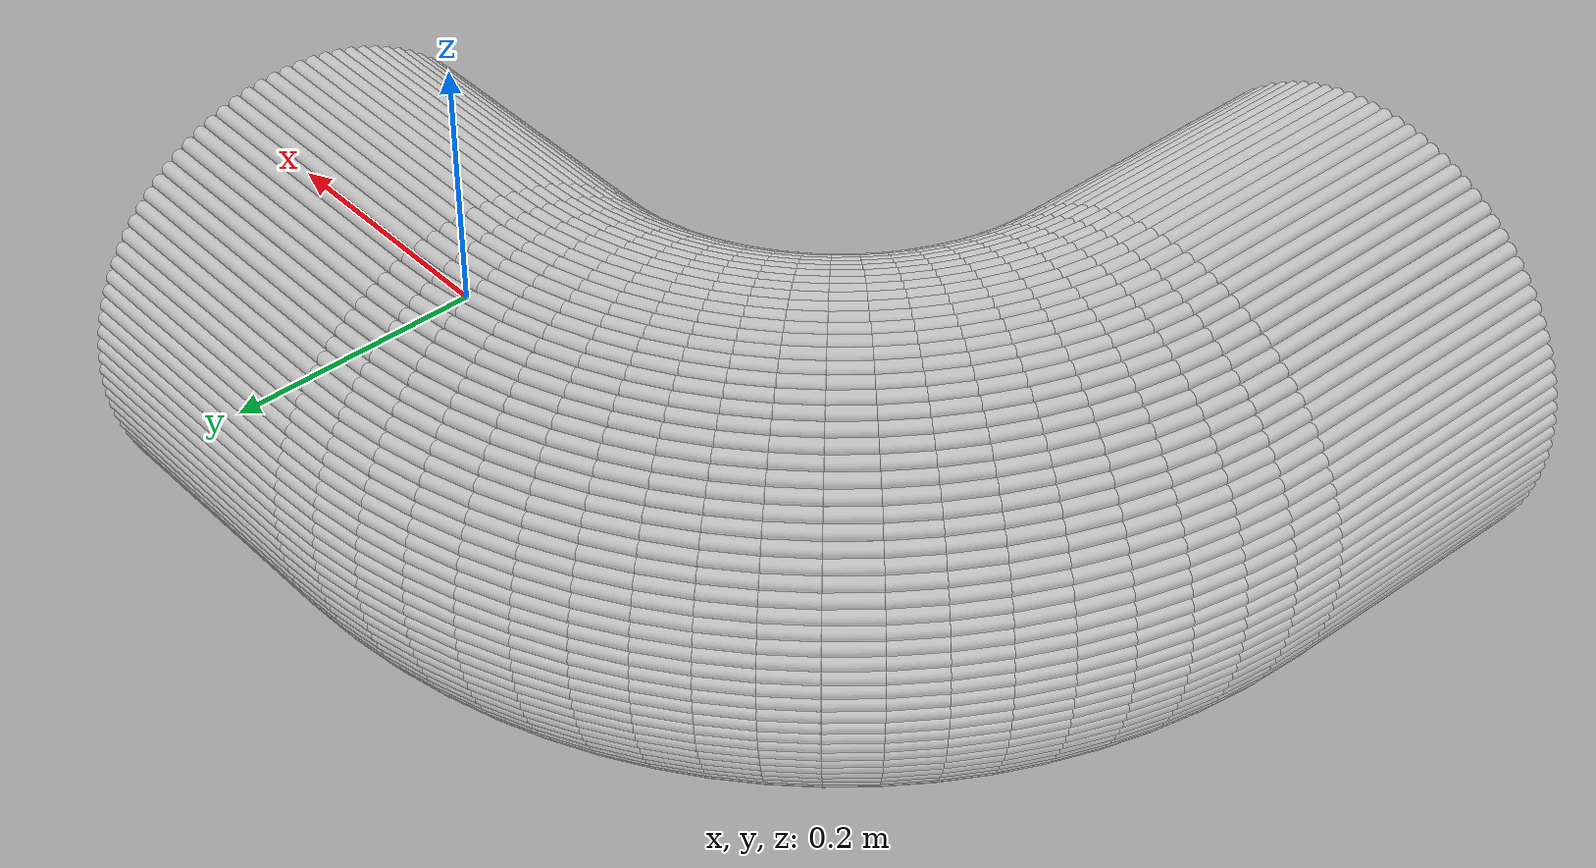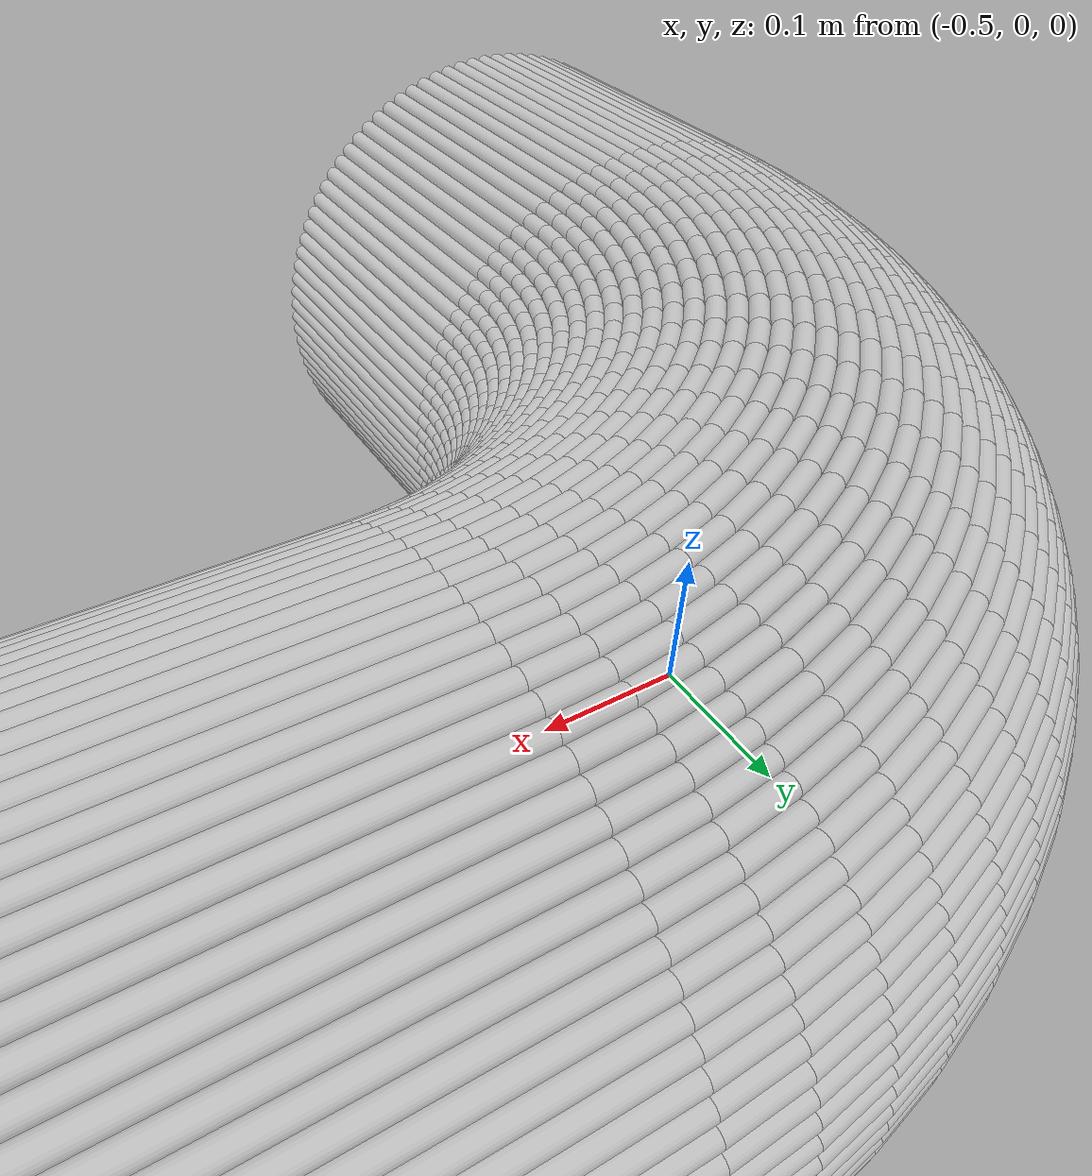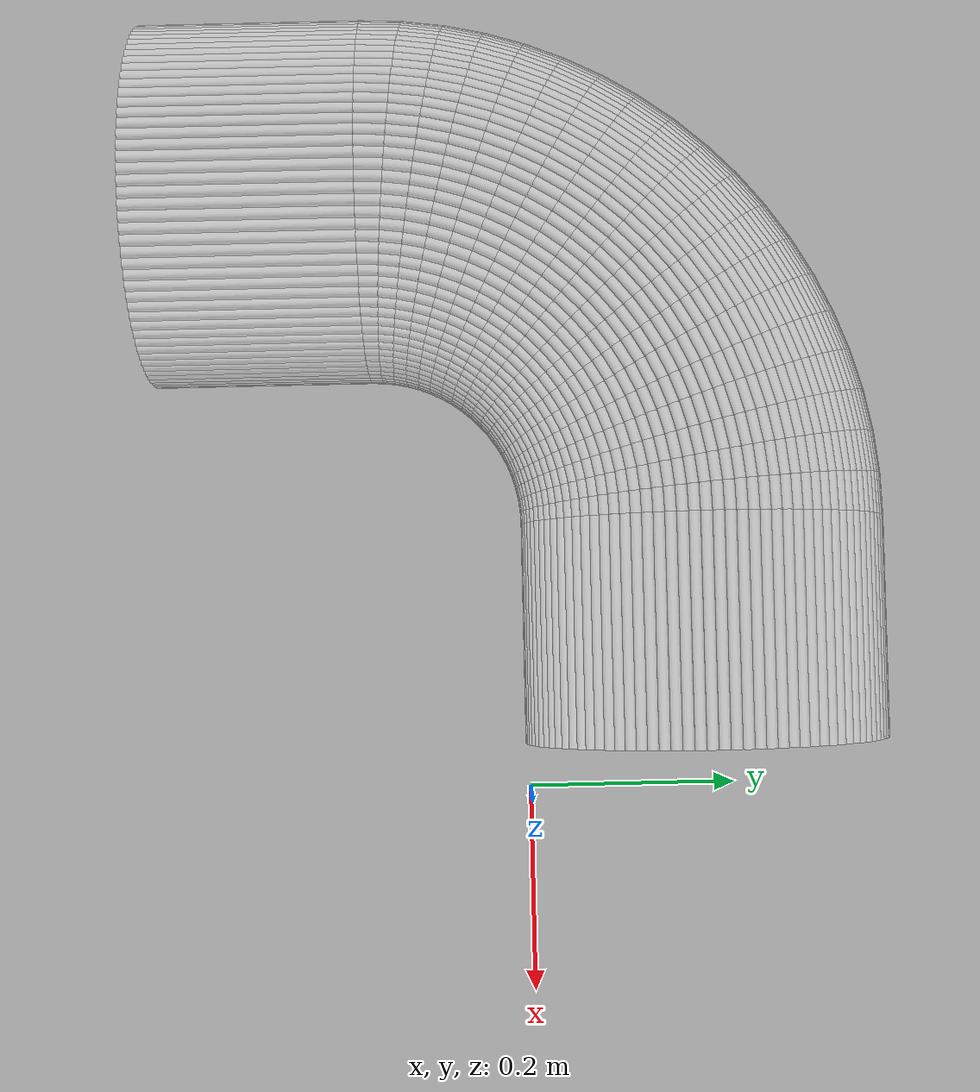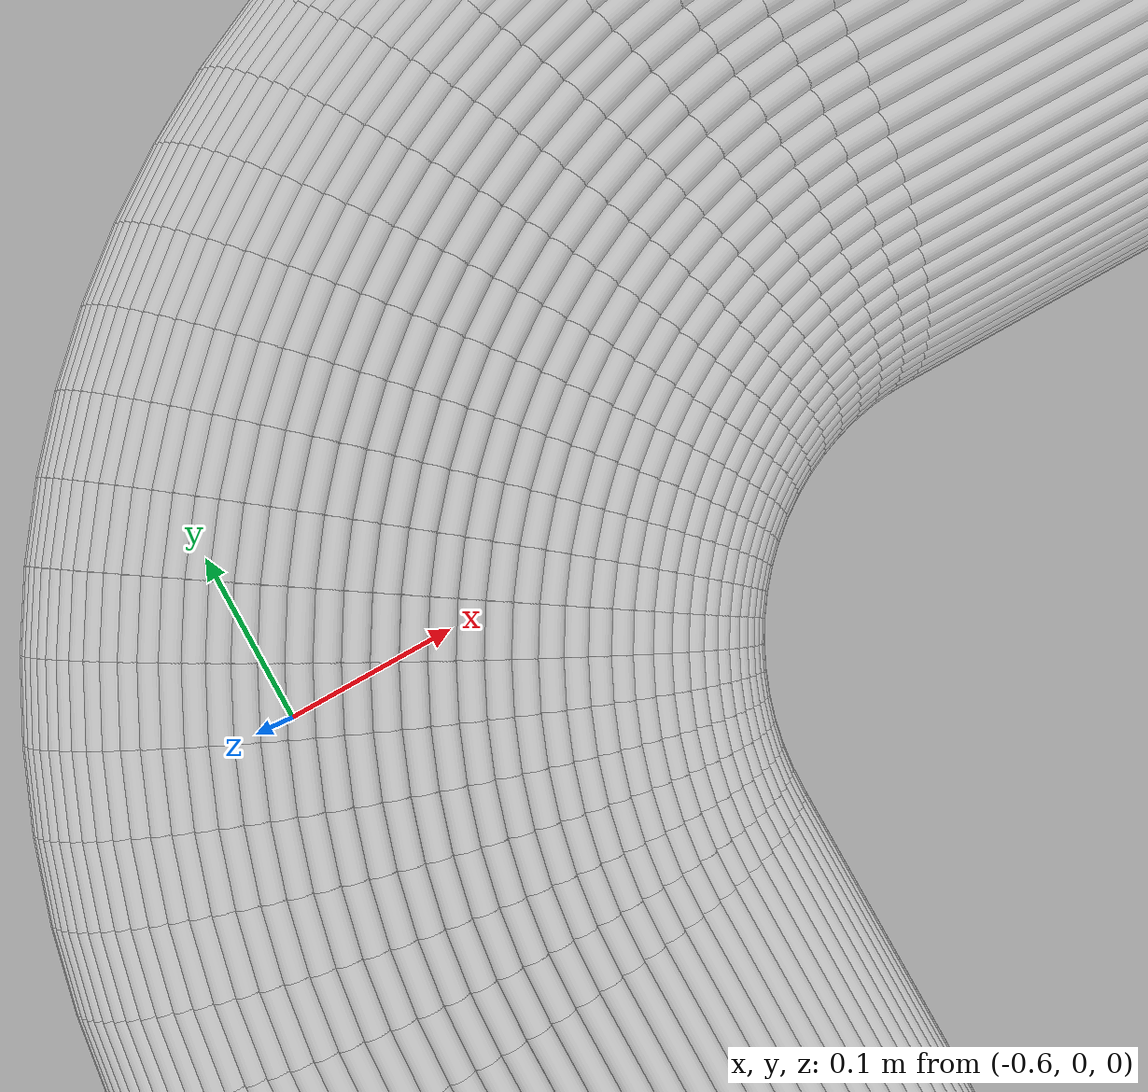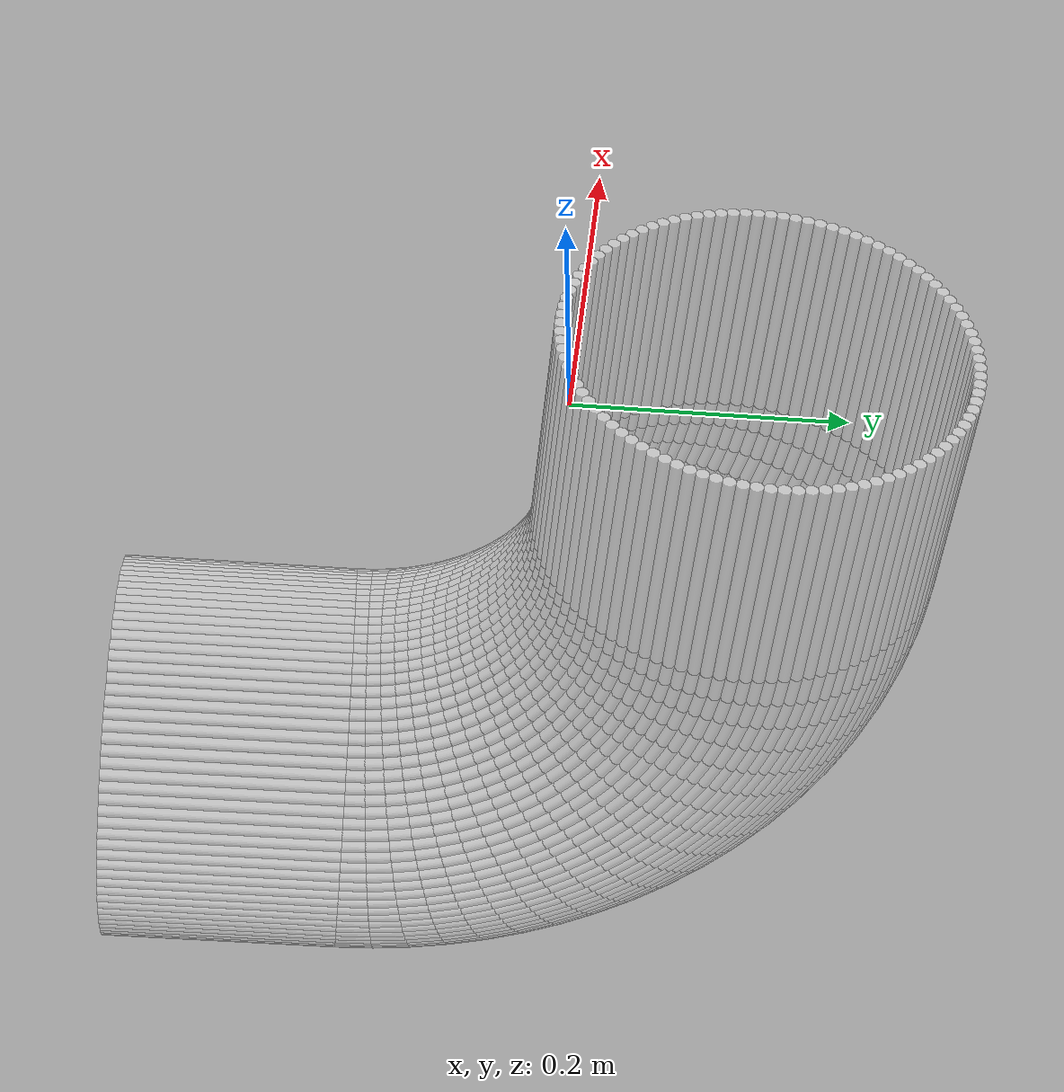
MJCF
<?xml version="1.0" encoding="utf-8"?>
<mujoco>
   <worldbody>
   <body pos="-0.25 -0.14 -0.02" euler="0 0 90">
      <geom euler=" 0 10 0 " fromto="0.46 -0.2 0.16 0.46 0 0.16" rgba="1 1 1 0.35"
            size="0.0050257"
            type="cylinder"/>
      <geom euler=" 0 20 0 " fromto="0.45968 -0.2 0.17005 0.45968 0 0.17005"
            rgba="1 1 1 0.35"
            size="0.0050257"
            type="cylinder"/>
      <geom euler=" 0 30 0 " fromto="0.45874 -0.2 0.18005 0.45874 0 0.18005"
            rgba="1 1 1 0.35"
            size="0.0050257"
            type="cylinder"/>
      <geom euler=" 0 40 0 " fromto="0.45717 -0.2 0.18998 0.45717 0 0.18998"
            rgba="1 1 1 0.35"
            size="0.0050257"
            type="cylinder"/>
      <geom euler=" 0 50 0 " fromto="0.45497 -0.2 0.19979 0.45497 0 0.19979"
            rgba="1 1 1 0.35"
            size="0.0050257"
            type="cylinder"/>
      <geom euler=" 0 60 0 " fromto="0.45217 -0.2 0.20944 0.45217 0 0.20944"
            rgba="1 1 1 0.35"
            size="0.0050257"
            type="cylinder"/>
      <geom euler=" 0 70 0 " fromto="0.44876 -0.2 0.2189 0.44876 0 0.2189"
            rgba="1 1 1 0.35"
            size="0.0050257"
            type="cylinder"/>
      <geom euler=" 0 80 0 " fromto="0.44477 -0.2 0.22812 0.44477 0 0.22812"
            rgba="1 1 1 0.35"
            size="0.0050257"
            type="cylinder"/>
      <geom euler=" 0 90 0 " fromto="0.44021 -0.2 0.23708 0.44021 0 0.23708"
            rgba="1 1 1 0.35"
            size="0.0050257"
            type="cylinder"/>
      <geom euler=" 0 100 0 " fromto="0.43509 -0.2 0.24573 0.43509 0 0.24573"
            rgba="1 1 1 0.35"
            size="0.0050257"
            type="cylinder"/>
      <geom euler=" 0 110 0 " fromto="0.42944 -0.2 0.25405 0.42944 0 0.25405"
            rgba="1 1 1 0.35"
            size="0.0050257"
            type="cylinder"/>
      <geom euler=" 0 120 0 " fromto="0.42328 -0.2 0.26199 0.42328 0 0.26199"
            rgba="1 1 1 0.35"
            size="0.0050257"
            type="cylinder"/>
      <geom euler=" 0 130 0 " fromto="0.41663 -0.2 0.26953 0.41663 0 0.26953"
            rgba="1 1 1 0.35"
            size="0.0050257"
            type="cylinder"/>
      <geom euler=" 0 140 0 " fromto="0.40953 -0.2 0.27663 0.40953 0 0.27663"
            rgba="1 1 1 0.35"
            size="0.0050257"
            type="cylinder"/>
      <geom euler=" 0 150 0 " fromto="0.40199 -0.2 0.28328 0.40199 0 0.28328"
            rgba="1 1 1 0.35"
            size="0.0050257"
            type="cylinder"/>
      <geom euler=" 0 160 0 " fromto="0.39405 -0.2 0.28944 0.39405 0 0.28944"
            rgba="1 1 1 0.35"
            size="0.0050257"
            type="cylinder"/>
      <geom euler=" 0 170 0 " fromto="0.38573 -0.2 0.29509 0.38573 0 0.29509"
            rgba="1 1 1 0.35"
            size="0.0050257"
            type="cylinder"/>
      <geom euler=" 0 180 0 " fromto="0.37708 -0.2 0.30021 0.37708 0 0.30021"
            rgba="1 1 1 0.35"
            size="0.0050257"
            type="cylinder"/>
      <geom euler=" 0 190 0 " fromto="0.36812 -0.2 0.30477 0.36812 0 0.30477"
            rgba="1 1 1 0.35"
            size="0.0050257"
            type="cylinder"/>
      <geom euler=" 0 200 0 " fromto="0.3589 -0.2 0.30876 0.3589 0 0.30876"
            rgba="1 1 1 0.35"
            size="0.0050257"
            type="cylinder"/>
      <geom euler=" 0 210 0 " fromto="0.34944 -0.2 0.31217 0.34944 0 0.31217"
            rgba="1 1 1 0.35"
            size="0.0050257"
            type="cylinder"/>
      <geom euler=" 0 220 0 " fromto="0.33979 -0.2 0.31497 0.33979 0 0.31497"
            rgba="1 1 1 0.35"
            size="0.0050257"
            type="cylinder"/>
      <geom euler=" 0 230 0 " fromto="0.32998 -0.2 0.31717 0.32998 0 0.31717"
            rgba="1 1 1 0.35"
            size="0.0050257"
            type="cylinder"/>
      <geom euler=" 0 240 0 " fromto="0.32005 -0.2 0.31874 0.32005 0 0.31874"
            rgba="1 1 1 0.35"
            size="0.0050257"
            type="cylinder"/>
      <geom euler=" 0 250 0 " fromto="0.31005 -0.2 0.31968 0.31005 0 0.31968"
            rgba="1 1 1 0.35"
            size="0.0050257"
            type="cylinder"/>
      <geom euler=" 0 260 0 " fromto="0.3 -0.2 0.32 0.3 0 0.32" rgba="1 1 1 0.35"
            size="0.0050257"
            type="cylinder"/>
      <geom euler=" 0 270 0 " fromto="0.28995 -0.2 0.31968 0.28995 0 0.31968"
            rgba="1 1 1 0.35"
            size="0.0050257"
            type="cylinder"/>
      <geom euler=" 0 280 0 " fromto="0.27995 -0.2 0.31874 0.27995 0 0.31874"
            rgba="1 1 1 0.35"
            size="0.0050257"
            type="cylinder"/>
      <geom euler=" 0 290 0 " fromto="0.27002 -0.2 0.31717 0.27002 0 0.31717"
            rgba="1 1 1 0.35"
            size="0.0050257"
            type="cylinder"/>
      <geom euler=" 0 300 0 " fromto="0.26021 -0.2 0.31497 0.26021 0 0.31497"
            rgba="1 1 1 0.35"
            size="0.0050257"
            type="cylinder"/>
      <geom euler=" 0 310 0 " fromto="0.25056 -0.2 0.31217 0.25056 0 0.31217"
            rgba="1 1 1 0.35"
            size="0.0050257"
            type="cylinder"/>
      <geom euler=" 0 320 0 " fromto="0.2411 -0.2 0.30876 0.2411 0 0.30876"
            rgba="1 1 1 0.35"
            size="0.0050257"
            type="cylinder"/>
      <geom euler=" 0 330 0 " fromto="0.23188 -0.2 0.30477 0.23188 0 0.30477"
            rgba="1 1 1 0.35"
            size="0.0050257"
            type="cylinder"/>
      <geom euler=" 0 340 0 " fromto="0.22292 -0.2 0.30021 0.22292 0 0.30021"
            rgba="1 1 1 0.35"
            size="0.0050257"
            type="cylinder"/>
      <geom euler=" 0 350 0 " fromto="0.21427 -0.2 0.29509 0.21427 0 0.29509"
            rgba="1 1 1 0.35"
            size="0.0050257"
            type="cylinder"/>
      <geom euler=" 0 360 0 " fromto="0.20595 -0.2 0.28944 0.20595 0 0.28944"
            rgba="1 1 1 0.35"
            size="0.0050257"
            type="cylinder"/>
      <geom euler=" 0 370 0 " fromto="0.19801 -0.2 0.28328 0.19801 0 0.28328"
            rgba="1 1 1 0.35"
            size="0.0050257"
            type="cylinder"/>
      <geom euler=" 0 380 0 " fromto="0.19047 -0.2 0.27663 0.19047 0 0.27663"
            rgba="1 1 1 0.35"
            size="0.0050257"
            type="cylinder"/>
      <geom euler=" 0 390 0 " fromto="0.18337 -0.2 0.26953 0.18337 0 0.26953"
            rgba="1 1 1 0.35"
            size="0.0050257"
            type="cylinder"/>
      <geom euler=" 0 400 0 " fromto="0.17672 -0.2 0.26199 0.17672 0 0.26199"
            rgba="1 1 1 0.35"
            size="0.0050257"
            type="cylinder"/>
      <geom euler=" 0 410 0 " fromto="0.17056 -0.2 0.25405 0.17056 0 0.25405"
            rgba="1 1 1 0.35"
            size="0.0050257"
            type="cylinder"/>
      <geom euler=" 0 420 0 " fromto="0.16491 -0.2 0.24573 0.16491 0 0.24573"
            rgba="1 1 1 0.35"
            size="0.0050257"
            type="cylinder"/>
      <geom euler=" 0 430 0 " fromto="0.15979 -0.2 0.23708 0.15979 0 0.23708"
            rgba="1 1 1 0.35"
            size="0.0050257"
            type="cylinder"/>
      <geom euler=" 0 440 0 " fromto="0.15523 -0.2 0.22812 0.15523 0 0.22812"
            rgba="1 1 1 0.35"
            size="0.0050257"
            type="cylinder"/>
      <geom euler=" 0 450 0 " fromto="0.15124 -0.2 0.2189 0.15124 0 0.2189"
            rgba="1 1 1 0.35"
            size="0.0050257"
            type="cylinder"/>
      <geom euler=" 0 460 0 " fromto="0.14783 -0.2 0.20944 0.14783 0 0.20944"
            rgba="1 1 1 0.35"
            size="0.0050257"
            type="cylinder"/>
      <geom euler=" 0 470 0 " fromto="0.14503 -0.2 0.19979 0.14503 0 0.19979"
            rgba="1 1 1 0.35"
            size="0.0050257"
            type="cylinder"/>
      <geom euler=" 0 480 0 " fromto="0.14283 -0.2 0.18998 0.14283 0 0.18998"
            rgba="1 1 1 0.35"
            size="0.0050257"
            type="cylinder"/>
      <geom euler=" 0 490 0 " fromto="0.14126 -0.2 0.18005 0.14126 0 0.18005"
            rgba="1 1 1 0.35"
            size="0.0050257"
            type="cylinder"/>
      <geom euler=" 0 500 0 " fromto="0.14032 -0.2 0.17005 0.14032 0 0.17005"
            rgba="1 1 1 0.35"
            size="0.0050257"
            type="cylinder"/>
      <geom euler=" 0 510 0 " fromto="0.14 -0.2 0.16 0.14 0 0.16" rgba="1 1 1 0.35"
            size="0.0050257"
            type="cylinder"/>
      <geom euler=" 0 520 0 " fromto="0.14032 -0.2 0.14995 0.14032 0 0.14995"
            rgba="1 1 1 0.35"
            size="0.0050257"
            type="cylinder"/>
      <geom euler=" 0 530 0 " fromto="0.14126 -0.2 0.13995 0.14126 0 0.13995"
            rgba="1 1 1 0.35"
            size="0.0050257"
            type="cylinder"/>
      <geom euler=" 0 540 0 " fromto="0.14283 -0.2 0.13002 0.14283 0 0.13002"
            rgba="1 1 1 0.35"
            size="0.0050257"
            type="cylinder"/>
      <geom euler=" 0 550 0 " fromto="0.14503 -0.2 0.12021 0.14503 0 0.12021"
            rgba="1 1 1 0.35"
            size="0.0050257"
            type="cylinder"/>
      <geom euler=" 0 560 0 " fromto="0.14783 -0.2 0.11056 0.14783 0 0.11056"
            rgba="1 1 1 0.35"
            size="0.0050257"
            type="cylinder"/>
      <geom euler=" 0 570 0 " fromto="0.15124 -0.2 0.1011 0.15124 0 0.1011"
            rgba="1 1 1 0.35"
            size="0.0050257"
            type="cylinder"/>
      <geom euler=" 0 580 0 " fromto="0.15523 -0.2 0.091875 0.15523 0 0.091875"
            rgba="1 1 1 0.35"
            size="0.0050257"
            type="cylinder"/>
      <geom euler=" 0 590 0 " fromto="0.15979 -0.2 0.082919 0.15979 0 0.082919"
            rgba="1 1 1 0.35"
            size="0.0050257"
            type="cylinder"/>
      <geom euler=" 0 600 0 " fromto="0.16491 -0.2 0.074268 0.16491 0 0.074268"
            rgba="1 1 1 0.35"
            size="0.0050257"
            type="cylinder"/>
      <geom euler=" 0 610 0 " fromto="0.17056 -0.2 0.065954 0.17056 0 0.065954"
            rgba="1 1 1 0.35"
            size="0.0050257"
            type="cylinder"/>
      <geom euler=" 0 620 0 " fromto="0.17672 -0.2 0.058012 0.17672 0 0.058012"
            rgba="1 1 1 0.35"
            size="0.0050257"
            type="cylinder"/>
      <geom euler=" 0 630 0 " fromto="0.18337 -0.2 0.050472 0.18337 0 0.050472"
            rgba="1 1 1 0.35"
            size="0.0050257"
            type="cylinder"/>
      <geom euler=" 0 640 0 " fromto="0.19047 -0.2 0.043365 0.19047 0 0.043365"
            rgba="1 1 1 0.35"
            size="0.0050257"
            type="cylinder"/>
      <geom euler=" 0 650 0 " fromto="0.19801 -0.2 0.036718 0.19801 0 0.036718"
            rgba="1 1 1 0.35"
            size="0.0050257"
            type="cylinder"/>
      <geom euler=" 0 660 0 " fromto="0.20595 -0.2 0.030557 0.20595 0 0.030557"
            rgba="1 1 1 0.35"
            size="0.0050257"
            type="cylinder"/>
      <geom euler=" 0 670 0 " fromto="0.21427 -0.2 0.024908 0.21427 0 0.024908"
            rgba="1 1 1 0.35"
            size="0.0050257"
            type="cylinder"/>
      <geom euler=" 0 680 0 " fromto="0.22292 -0.2 0.019791 0.22292 0 0.019791"
            rgba="1 1 1 0.35"
            size="0.0050257"
            type="cylinder"/>
      <geom euler=" 0 690 0 " fromto="0.23188 -0.2 0.015228 0.23188 0 0.015228"
            rgba="1 1 1 0.35"
            size="0.0050257"
            type="cylinder"/>
      <geom euler=" 0 700 0 " fromto="0.2411 -0.2 0.011236 0.2411 0 0.011236"
            rgba="1 1 1 0.35"
            size="0.0050257"
            type="cylinder"/>
      <geom euler=" 0 710 0 " fromto="0.25056 -0.2 0.007831 0.25056 0 0.007831"
            rgba="1 1 1 0.35"
            size="0.0050257"
            type="cylinder"/>
      <geom euler=" 0 720 0 " fromto="0.26021 -0.2 0.0050267 0.26021 0 0.0050267"
            rgba="1 1 1 0.35"
            size="0.0050257"
            type="cylinder"/>
      <geom euler=" 0 730 0 " fromto="0.27002 -0.2 0.002834 0.27002 0 0.002834"
            rgba="1 1 1 0.35"
            size="0.0050257"
            type="cylinder"/>
      <geom euler=" 0 740 0 " fromto="0.27995 -0.2 0.0012616 0.27995 0 0.0012616"
            rgba="1 1 1 0.35"
            size="0.0050257"
            type="cylinder"/>
      <geom euler=" 0 750 0 " fromto="0.28995 -0.2 0.00031572 0.28995 0 0.00031572"
            rgba="1 1 1 0.35"
            size="0.0050257"
            type="cylinder"/>
      <geom euler=" 0 760 0 " fromto="0.3 -0.2 0 0.3 0 0" rgba="1 1 1 0.35"
            size="0.0050257"
            type="cylinder"/>
      <geom euler=" 0 770 0 " fromto="0.31005 -0.2 0.00031572 0.31005 0 0.00031572"
            rgba="1 1 1 0.35"
            size="0.0050257"
            type="cylinder"/>
      <geom euler=" 0 780 0 " fromto="0.32005 -0.2 0.0012616 0.32005 0 0.0012616"
            rgba="1 1 1 0.35"
            size="0.0050257"
            type="cylinder"/>
      <geom euler=" 0 790 0 " fromto="0.32998 -0.2 0.002834 0.32998 0 0.002834"
            rgba="1 1 1 0.35"
            size="0.0050257"
            type="cylinder"/>
      <geom euler=" 0 800 0 " fromto="0.33979 -0.2 0.0050267 0.33979 0 0.0050267"
            rgba="1 1 1 0.35"
            size="0.0050257"
            type="cylinder"/>
      <geom euler=" 0 810 0 " fromto="0.34944 -0.2 0.007831 0.34944 0 0.007831"
            rgba="1 1 1 0.35"
            size="0.0050257"
            type="cylinder"/>
      <geom euler=" 0 820 0 " fromto="0.3589 -0.2 0.011236 0.3589 0 0.011236"
            rgba="1 1 1 0.35"
            size="0.0050257"
            type="cylinder"/>
      <geom euler=" 0 830 0 " fromto="0.36812 -0.2 0.015228 0.36812 0 0.015228"
            rgba="1 1 1 0.35"
            size="0.0050257"
            type="cylinder"/>
      <geom euler=" 0 840 0 " fromto="0.37708 -0.2 0.019791 0.37708 0 0.019791"
            rgba="1 1 1 0.35"
            size="0.0050257"
            type="cylinder"/>
      <geom euler=" 0 850 0 " fromto="0.38573 -0.2 0.024908 0.38573 0 0.024908"
            rgba="1 1 1 0.35"
            size="0.0050257"
            type="cylinder"/>
      <geom euler=" 0 860 0 " fromto="0.39405 -0.2 0.030557 0.39405 0 0.030557"
            rgba="1 1 1 0.35"
            size="0.0050257"
            type="cylinder"/>
      <geom euler=" 0 870 0 " fromto="0.40199 -0.2 0.036718 0.40199 0 0.036718"
            rgba="1 1 1 0.35"
            size="0.0050257"
            type="cylinder"/>
      <geom euler=" 0 880 0 " fromto="0.40953 -0.2 0.043365 0.40953 0 0.043365"
            rgba="1 1 1 0.35"
            size="0.0050257"
            type="cylinder"/>
      <geom euler=" 0 890 0 " fromto="0.41663 -0.2 0.050472 0.41663 0 0.050472"
            rgba="1 1 1 0.35"
            size="0.0050257"
            type="cylinder"/>
      <geom euler=" 0 900 0 " fromto="0.42328 -0.2 0.058012 0.42328 0 0.058012"
            rgba="1 1 1 0.35"
            size="0.0050257"
            type="cylinder"/>
      <geom euler=" 0 910 0 " fromto="0.42944 -0.2 0.065954 0.42944 0 0.065954"
            rgba="1 1 1 0.35"
            size="0.0050257"
            type="cylinder"/>
      <geom euler=" 0 920 0 " fromto="0.43509 -0.2 0.074268 0.43509 0 0.074268"
            rgba="1 1 1 0.35"
            size="0.0050257"
            type="cylinder"/>
      <geom euler=" 0 930 0 " fromto="0.44021 -0.2 0.082919 0.44021 0 0.082919"
            rgba="1 1 1 0.35"
            size="0.0050257"
            type="cylinder"/>
      <geom euler=" 0 940 0 " fromto="0.44477 -0.2 0.091875 0.44477 0 0.091875"
            rgba="1 1 1 0.35"
            size="0.0050257"
            type="cylinder"/>
      <geom euler=" 0 950 0 " fromto="0.44876 -0.2 0.1011 0.44876 0 0.1011"
            rgba="1 1 1 0.35"
            size="0.0050257"
            type="cylinder"/>
      <geom euler=" 0 960 0 " fromto="0.45217 -0.2 0.11056 0.45217 0 0.11056"
            rgba="1 1 1 0.35"
            size="0.0050257"
            type="cylinder"/>
      <geom euler=" 0 970 0 " fromto="0.45497 -0.2 0.12021 0.45497 0 0.12021"
            rgba="1 1 1 0.35"
            size="0.0050257"
            type="cylinder"/>
      <geom euler=" 0 980 0 " fromto="0.45717 -0.2 0.13002 0.45717 0 0.13002"
            rgba="1 1 1 0.35"
            size="0.0050257"
            type="cylinder"/>
      <geom euler=" 0 990 0 " fromto="0.45874 -0.2 0.13995 0.45874 0 0.13995"
            rgba="1 1 1 0.35"
            size="0.0050257"
            type="cylinder"/>
      <geom euler=" 0 1000 0 " fromto="0.45968 -0.2 0.14995 0.45968 0 0.14995"
            rgba="1 1 1 0.35"
            size="0.0050257"
            type="cylinder"/>
      <geom euler=" 0 10 0 " fromto="0.46 0 0.16 0.45843 0.037986 0.16" rgba="1 1 1 0.35"
            size="0.0050257"
            type="cylinder"/>
      <geom euler=" 0 20 0 " fromto="0.45968 0 0.17005 0.45811 0.03796 0.17005"
            rgba="1 1 1 0.35"
            size="0.0050257"
            type="cylinder"/>
      <geom euler=" 0 30 0 " fromto="0.45874 0 0.18005 0.45717 0.037882 0.18005"
            rgba="1 1 1 0.35"
            size="0.0050257"
            type="cylinder"/>
      <geom euler=" 0 40 0 " fromto="0.45717 0 0.18998 0.4556 0.037752 0.18998"
            rgba="1 1 1 0.35"
            size="0.0050257"
            type="cylinder"/>
      <geom euler=" 0 50 0 " fromto="0.45497 0 0.19979 0.45342 0.037571 0.19979"
            rgba="1 1 1 0.35"
            size="0.0050257"
            type="cylinder"/>
      <geom euler=" 0 60 0 " fromto="0.45217 0 0.20944 0.45062 0.03734 0.20944"
            rgba="1 1 1 0.35"
            size="0.0050257"
            type="cylinder"/>
      <geom euler=" 0 70 0 " fromto="0.44876 0 0.2189 0.44723 0.037059 0.2189"
            rgba="1 1 1 0.35"
            size="0.0050257"
            type="cylinder"/>
      <geom euler=" 0 80 0 " fromto="0.44477 0 0.22812 0.44325 0.036729 0.22812"
            rgba="1 1 1 0.35"
            size="0.0050257"
            type="cylinder"/>
      <geom euler=" 0 90 0 " fromto="0.44021 0 0.23708 0.43871 0.036352 0.23708"
            rgba="1 1 1 0.35"
            size="0.0050257"
            type="cylinder"/>
      <geom euler=" 0 100 0 " fromto="0.43509 0 0.24573 0.43361 0.03593 0.24573"
            rgba="1 1 1 0.35"
            size="0.0050257"
            type="cylinder"/>
      <geom euler=" 0 110 0 " fromto="0.42944 0 0.25405 0.42798 0.035463 0.25405"
            rgba="1 1 1 0.35"
            size="0.0050257"
            type="cylinder"/>
      <geom euler=" 0 120 0 " fromto="0.42328 0 0.26199 0.42184 0.034954 0.26199"
            rgba="1 1 1 0.35"
            size="0.0050257"
            type="cylinder"/>
      <geom euler=" 0 130 0 " fromto="0.41663 0 0.26953 0.41521 0.034405 0.26953"
            rgba="1 1 1 0.35"
            size="0.0050257"
            type="cylinder"/>
      <geom euler=" 0 140 0 " fromto="0.40953 0 0.27663 0.40813 0.033819 0.27663"
            rgba="1 1 1 0.35"
            size="0.0050257"
            type="cylinder"/>
      <geom euler=" 0 150 0 " fromto="0.40199 0 0.28328 0.40061 0.033196 0.28328"
            rgba="1 1 1 0.35"
            size="0.0050257"
            type="cylinder"/>
      <geom euler=" 0 160 0 " fromto="0.39405 0 0.28944 0.3927 0.03254 0.28944"
            rgba="1 1 1 0.35"
            size="0.0050257"
            type="cylinder"/>
      <geom euler=" 0 170 0 " fromto="0.38573 0 0.29509 0.38441 0.031854 0.29509"
            rgba="1 1 1 0.35"
            size="0.0050257"
            type="cylinder"/>
      <geom euler=" 0 180 0 " fromto="0.37708 0 0.30021 0.37579 0.031139 0.30021"
            rgba="1 1 1 0.35"
            size="0.0050257"
            type="cylinder"/>
      <geom euler=" 0 190 0 " fromto="0.36812 0 0.30477 0.36687 0.030399 0.30477"
            rgba="1 1 1 0.35"
            size="0.0050257"
            type="cylinder"/>
      <geom euler=" 0 200 0 " fromto="0.3589 0 0.30876 0.35767 0.029638 0.30876"
            rgba="1 1 1 0.35"
            size="0.0050257"
            type="cylinder"/>
      <geom euler=" 0 210 0 " fromto="0.34944 0 0.31217 0.34825 0.028857 0.31217"
            rgba="1 1 1 0.35"
            size="0.0050257"
            type="cylinder"/>
      <geom euler=" 0 220 0 " fromto="0.33979 0 0.31497 0.33863 0.02806 0.31497"
            rgba="1 1 1 0.35"
            size="0.0050257"
            type="cylinder"/>
      <geom euler=" 0 230 0 " fromto="0.32998 0 0.31717 0.32885 0.02725 0.31717"
            rgba="1 1 1 0.35"
            size="0.0050257"
            type="cylinder"/>
      <geom euler=" 0 240 0 " fromto="0.32005 0 0.31874 0.31896 0.02643 0.31874"
            rgba="1 1 1 0.35"
            size="0.0050257"
            type="cylinder"/>
      <geom euler=" 0 250 0 " fromto="0.31005 0 0.31968 0.30899 0.025603 0.31968"
            rgba="1 1 1 0.35"
            size="0.0050257"
            type="cylinder"/>
      <geom euler=" 0 260 0 " fromto="0.3 0 0.32 0.29898 0.024774 0.32" rgba="1 1 1 0.35"
            size="0.0050257"
            type="cylinder"/>
      <geom euler=" 0 270 0 " fromto="0.28995 0 0.31968 0.28896 0.023944 0.31968"
            rgba="1 1 1 0.35"
            size="0.0050257"
            type="cylinder"/>
      <geom euler=" 0 280 0 " fromto="0.27995 0 0.31874 0.27899 0.023118 0.31874"
            rgba="1 1 1 0.35"
            size="0.0050257"
            type="cylinder"/>
      <geom euler=" 0 290 0 " fromto="0.27002 0 0.31717 0.2691 0.022298 0.31717"
            rgba="1 1 1 0.35"
            size="0.0050257"
            type="cylinder"/>
      <geom euler=" 0 300 0 " fromto="0.26021 0 0.31497 0.25932 0.021488 0.31497"
            rgba="1 1 1 0.35"
            size="0.0050257"
            type="cylinder"/>
      <geom euler=" 0 310 0 " fromto="0.25056 0 0.31217 0.2497 0.020691 0.31217"
            rgba="1 1 1 0.35"
            size="0.0050257"
            type="cylinder"/>
      <geom euler=" 0 320 0 " fromto="0.2411 0 0.30876 0.24028 0.01991 0.30876"
            rgba="1 1 1 0.35"
            size="0.0050257"
            type="cylinder"/>
      <geom euler=" 0 330 0 " fromto="0.23188 0 0.30477 0.23108 0.019148 0.30477"
            rgba="1 1 1 0.35"
            size="0.0050257"
            type="cylinder"/>
      <geom euler=" 0 340 0 " fromto="0.22292 0 0.30021 0.22216 0.018409 0.30021"
            rgba="1 1 1 0.35"
            size="0.0050257"
            type="cylinder"/>
      <geom euler=" 0 350 0 " fromto="0.21427 0 0.29509 0.21354 0.017694 0.29509"
            rgba="1 1 1 0.35"
            size="0.0050257"
            type="cylinder"/>
      <geom euler=" 0 360 0 " fromto="0.20595 0 0.28944 0.20525 0.017008 0.28944"
            rgba="1 1 1 0.35"
            size="0.0050257"
            type="cylinder"/>
      <geom euler=" 0 370 0 " fromto="0.19801 0 0.28328 0.19734 0.016352 0.28328"
            rgba="1 1 1 0.35"
            size="0.0050257"
            type="cylinder"/>
      <geom euler=" 0 380 0 " fromto="0.19047 0 0.27663 0.18982 0.015729 0.27663"
            rgba="1 1 1 0.35"
            size="0.0050257"
            type="cylinder"/>
      <geom euler=" 0 390 0 " fromto="0.18337 0 0.26953 0.18274 0.015142 0.26953"
            rgba="1 1 1 0.35"
            size="0.0050257"
            type="cylinder"/>
      <geom euler=" 0 400 0 " fromto="0.17672 0 0.26199 0.17611 0.014593 0.26199"
            rgba="1 1 1 0.35"
            size="0.0050257"
            type="cylinder"/>
      <geom euler=" 0 410 0 " fromto="0.17056 0 0.25405 0.16997 0.014085 0.25405"
            rgba="1 1 1 0.35"
            size="0.0050257"
            type="cylinder"/>
      <geom euler=" 0 420 0 " fromto="0.16491 0 0.24573 0.16434 0.013618 0.24573"
            rgba="1 1 1 0.35"
            size="0.0050257"
            type="cylinder"/>
      <geom euler=" 0 430 0 " fromto="0.15979 0 0.23708 0.15925 0.013195 0.23708"
            rgba="1 1 1 0.35"
            size="0.0050257"
            type="cylinder"/>
      <geom euler=" 0 440 0 " fromto="0.15523 0 0.22812 0.1547 0.012819 0.22812"
            rgba="1 1 1 0.35"
            size="0.0050257"
            type="cylinder"/>
      <geom euler=" 0 450 0 " fromto="0.15124 0 0.2189 0.15072 0.012489 0.2189"
            rgba="1 1 1 0.35"
            size="0.0050257"
            type="cylinder"/>
      <geom euler=" 0 460 0 " fromto="0.14783 0 0.20944 0.14733 0.012208 0.20944"
            rgba="1 1 1 0.35"
            size="0.0050257"
            type="cylinder"/>
      <geom euler=" 0 470 0 " fromto="0.14503 0 0.19979 0.14453 0.011976 0.19979"
            rgba="1 1 1 0.35"
            size="0.0050257"
            type="cylinder"/>
      <geom euler=" 0 480 0 " fromto="0.14283 0 0.18998 0.14235 0.011795 0.18998"
            rgba="1 1 1 0.35"
            size="0.0050257"
            type="cylinder"/>
      <geom euler=" 0 490 0 " fromto="0.14126 0 0.18005 0.14078 0.011665 0.18005"
            rgba="1 1 1 0.35"
            size="0.0050257"
            type="cylinder"/>
      <geom euler=" 0 500 0 " fromto="0.14032 0 0.17005 0.13984 0.011587 0.17005"
            rgba="1 1 1 0.35"
            size="0.0050257"
            type="cylinder"/>
      <geom euler=" 0 510 0 " fromto="0.14 0 0.16 0.13952 0.011561 0.16" rgba="1 1 1 0.35"
            size="0.0050257"
            type="cylinder"/>
      <geom euler=" 0 520 0 " fromto="0.14032 0 0.14995 0.13984 0.011587 0.14995"
            rgba="1 1 1 0.35"
            size="0.0050257"
            type="cylinder"/>
      <geom euler=" 0 530 0 " fromto="0.14126 0 0.13995 0.14078 0.011665 0.13995"
            rgba="1 1 1 0.35"
            size="0.0050257"
            type="cylinder"/>
      <geom euler=" 0 540 0 " fromto="0.14283 0 0.13002 0.14235 0.011795 0.13002"
            rgba="1 1 1 0.35"
            size="0.0050257"
            type="cylinder"/>
      <geom euler=" 0 550 0 " fromto="0.14503 0 0.12021 0.14453 0.011976 0.12021"
            rgba="1 1 1 0.35"
            size="0.0050257"
            type="cylinder"/>
      <geom euler=" 0 560 0 " fromto="0.14783 0 0.11056 0.14733 0.012208 0.11056"
            rgba="1 1 1 0.35"
            size="0.0050257"
            type="cylinder"/>
      <geom euler=" 0 570 0 " fromto="0.15124 0 0.1011 0.15072 0.012489 0.1011"
            rgba="1 1 1 0.35"
            size="0.0050257"
            type="cylinder"/>
      <geom euler=" 0 580 0 " fromto="0.15523 0 0.091875 0.1547 0.012819 0.091875"
            rgba="1 1 1 0.35"
            size="0.0050257"
            type="cylinder"/>
      <geom euler=" 0 590 0 " fromto="0.15979 0 0.082919 0.15925 0.013195 0.082919"
            rgba="1 1 1 0.35"
            size="0.0050257"
            type="cylinder"/>
      <geom euler=" 0 600 0 " fromto="0.16491 0 0.074268 0.16434 0.013618 0.074268"
            rgba="1 1 1 0.35"
            size="0.0050257"
            type="cylinder"/>
      <geom euler=" 0 610 0 " fromto="0.17056 0 0.065954 0.16997 0.014085 0.065954"
            rgba="1 1 1 0.35"
            size="0.0050257"
            type="cylinder"/>
      <geom euler=" 0 620 0 " fromto="0.17672 0 0.058012 0.17611 0.014593 0.058012"
            rgba="1 1 1 0.35"
            size="0.0050257"
            type="cylinder"/>
      <geom euler=" 0 630 0 " fromto="0.18337 0 0.050472 0.18274 0.015142 0.050472"
            rgba="1 1 1 0.35"
            size="0.0050257"
            type="cylinder"/>
      <geom euler=" 0 640 0 " fromto="0.19047 0 0.043365 0.18982 0.015729 0.043365"
            rgba="1 1 1 0.35"
            size="0.0050257"
            type="cylinder"/>
      <geom euler=" 0 650 0 " fromto="0.19801 0 0.036718 0.19734 0.016352 0.036718"
            rgba="1 1 1 0.35"
            size="0.0050257"
            type="cylinder"/>
      <geom euler=" 0 660 0 " fromto="0.20595 0 0.030557 0.20525 0.017008 0.030557"
            rgba="1 1 1 0.35"
            size="0.0050257"
            type="cylinder"/>
      <geom euler=" 0 670 0 " fromto="0.21427 0 0.024908 0.21354 0.017694 0.024908"
            rgba="1 1 1 0.35"
            size="0.0050257"
            type="cylinder"/>
      <geom euler=" 0 680 0 " fromto="0.22292 0 0.019791 0.22216 0.018409 0.019791"
            rgba="1 1 1 0.35"
            size="0.0050257"
            type="cylinder"/>
      <geom euler=" 0 690 0 " fromto="0.23188 0 0.015228 0.23108 0.019148 0.015228"
            rgba="1 1 1 0.35"
            size="0.0050257"
            type="cylinder"/>
      <geom euler=" 0 700 0 " fromto="0.2411 0 0.011236 0.24028 0.01991 0.011236"
            rgba="1 1 1 0.35"
            size="0.0050257"
            type="cylinder"/>
      <geom euler=" 0 710 0 " fromto="0.25056 0 0.007831 0.2497 0.020691 0.007831"
            rgba="1 1 1 0.35"
            size="0.0050257"
            type="cylinder"/>
      <geom euler=" 0 720 0 " fromto="0.26021 0 0.0050267 0.25932 0.021488 0.0050267"
            rgba="1 1 1 0.35"
            size="0.0050257"
            type="cylinder"/>
      <geom euler=" 0 730 0 " fromto="0.27002 0 0.002834 0.2691 0.022298 0.002834"
            rgba="1 1 1 0.35"
            size="0.0050257"
            type="cylinder"/>
      <geom euler=" 0 740 0 " fromto="0.27995 0 0.0012616 0.27899 0.023118 0.0012616"
            rgba="1 1 1 0.35"
            size="0.0050257"
            type="cylinder"/>
      <geom euler=" 0 750 0 " fromto="0.28995 0 0.00031572 0.28896 0.023944 0.00031572"
            rgba="1 1 1 0.35"
            size="0.0050257"
            type="cylinder"/>
      <geom euler=" 0 760 0 " fromto="0.3 0 0 0.29898 0.024774 0" rgba="1 1 1 0.35"
            size="0.0050257"
            type="cylinder"/>
      <geom euler=" 0 770 0 " fromto="0.31005 0 0.00031572 0.30899 0.025603 0.00031572"
            rgba="1 1 1 0.35"
            size="0.0050257"
            type="cylinder"/>
      <geom euler=" 0 780 0 " fromto="0.32005 0 0.0012616 0.31896 0.02643 0.0012616"
            rgba="1 1 1 0.35"
            size="0.0050257"
            type="cylinder"/>
      <geom euler=" 0 790 0 " fromto="0.32998 0 0.002834 0.32885 0.02725 0.002834"
            rgba="1 1 1 0.35"
            size="0.0050257"
            type="cylinder"/>
      <geom euler=" 0 800 0 " fromto="0.33979 0 0.0050267 0.33863 0.02806 0.0050267"
            rgba="1 1 1 0.35"
            size="0.0050257"
            type="cylinder"/>
      <geom euler=" 0 810 0 " fromto="0.34944 0 0.007831 0.34825 0.028857 0.007831"
            rgba="1 1 1 0.35"
            size="0.0050257"
            type="cylinder"/>
      <geom euler=" 0 820 0 " fromto="0.3589 0 0.011236 0.35767 0.029638 0.011236"
            rgba="1 1 1 0.35"
            size="0.0050257"
            type="cylinder"/>
      <geom euler=" 0 830 0 " fromto="0.36812 0 0.015228 0.36687 0.030399 0.015228"
            rgba="1 1 1 0.35"
            size="0.0050257"
            type="cylinder"/>
      <geom euler=" 0 840 0 " fromto="0.37708 0 0.019791 0.37579 0.031139 0.019791"
            rgba="1 1 1 0.35"
            size="0.0050257"
            type="cylinder"/>
      <geom euler=" 0 850 0 " fromto="0.38573 0 0.024908 0.38441 0.031854 0.024908"
            rgba="1 1 1 0.35"
            size="0.0050257"
            type="cylinder"/>
      <geom euler=" 0 860 0 " fromto="0.39405 0 0.030557 0.3927 0.03254 0.030557"
            rgba="1 1 1 0.35"
            size="0.0050257"
            type="cylinder"/>
      <geom euler=" 0 870 0 " fromto="0.40199 0 0.036718 0.40061 0.033196 0.036718"
            rgba="1 1 1 0.35"
            size="0.0050257"
            type="cylinder"/>
      <geom euler=" 0 880 0 " fromto="0.40953 0 0.043365 0.40813 0.033819 0.043365"
            rgba="1 1 1 0.35"
            size="0.0050257"
            type="cylinder"/>
      <geom euler=" 0 890 0 " fromto="0.41663 0 0.050472 0.41521 0.034405 0.050472"
            rgba="1 1 1 0.35"
            size="0.0050257"
            type="cylinder"/>
      <geom euler=" 0 900 0 " fromto="0.42328 0 0.058012 0.42184 0.034954 0.058012"
            rgba="1 1 1 0.35"
            size="0.0050257"
            type="cylinder"/>
      <geom euler=" 0 910 0 " fromto="0.42944 0 0.065954 0.42798 0.035463 0.065954"
            rgba="1 1 1 0.35"
            size="0.0050257"
            type="cylinder"/>
      <geom euler=" 0 920 0 " fromto="0.43509 0 0.074268 0.43361 0.03593 0.074268"
            rgba="1 1 1 0.35"
            size="0.0050257"
            type="cylinder"/>
      <geom euler=" 0 930 0 " fromto="0.44021 0 0.082919 0.43871 0.036352 0.082919"
            rgba="1 1 1 0.35"
            size="0.0050257"
            type="cylinder"/>
      <geom euler=" 0 940 0 " fromto="0.44477 0 0.091875 0.44325 0.036729 0.091875"
            rgba="1 1 1 0.35"
            size="0.0050257"
            type="cylinder"/>
      <geom euler=" 0 950 0 " fromto="0.44876 0 0.1011 0.44723 0.037059 0.1011"
            rgba="1 1 1 0.35"
            size="0.0050257"
            type="cylinder"/>
      <geom euler=" 0 960 0 " fromto="0.45217 0 0.11056 0.45062 0.03734 0.11056"
            rgba="1 1 1 0.35"
            size="0.0050257"
            type="cylinder"/>
      <geom euler=" 0 970 0 " fromto="0.45497 0 0.12021 0.45342 0.037571 0.12021"
            rgba="1 1 1 0.35"
            size="0.0050257"
            type="cylinder"/>
      <geom euler=" 0 980 0 " fromto="0.45717 0 0.13002 0.4556 0.037752 0.13002"
            rgba="1 1 1 0.35"
            size="0.0050257"
            type="cylinder"/>
      <geom euler=" 0 990 0 " fromto="0.45874 0 0.13995 0.45717 0.037882 0.13995"
            rgba="1 1 1 0.35"
            size="0.0050257"
            type="cylinder"/>
      <geom euler=" 0 1000 0 " fromto="0.45968 0 0.14995 0.45811 0.03796 0.14995"
            rgba="1 1 1 0.35"
            size="0.0050257"
            type="cylinder"/>
      <geom euler=" 0 10 0 " fromto="0.45843 0.037986 0.16 0.45373 0.075714 0.16"
            rgba="1 1 1 0.35"
            size="0.0050257"
            type="cylinder"/>
      <geom euler=" 0 20 0 " fromto="0.45811 0.03796 0.17005 0.45341 0.075662 0.17005"
            rgba="1 1 1 0.35"
            size="0.0050257"
            type="cylinder"/>
      <geom euler=" 0 30 0 " fromto="0.45717 0.037882 0.18005 0.45248 0.075506 0.18005"
            rgba="1 1 1 0.35"
            size="0.0050257"
            type="cylinder"/>
      <geom euler=" 0 40 0 " fromto="0.4556 0.037752 0.18998 0.45093 0.075247 0.18998"
            rgba="1 1 1 0.35"
            size="0.0050257"
            type="cylinder"/>
      <geom euler=" 0 50 0 " fromto="0.45342 0.037571 0.19979 0.44877 0.074886 0.19979"
            rgba="1 1 1 0.35"
            size="0.0050257"
            type="cylinder"/>
      <geom euler=" 0 60 0 " fromto="0.45062 0.03734 0.20944 0.446 0.074425 0.20944"
            rgba="1 1 1 0.35"
            size="0.0050257"
            type="cylinder"/>
      <geom euler=" 0 70 0 " fromto="0.44723 0.037059 0.2189 0.44264 0.073864 0.2189"
            rgba="1 1 1 0.35"
            size="0.0050257"
            type="cylinder"/>
      <geom euler=" 0 80 0 " fromto="0.44325 0.036729 0.22812 0.43871 0.073207 0.22812"
            rgba="1 1 1 0.35"
            size="0.0050257"
            type="cylinder"/>
      <geom euler=" 0 90 0 " fromto="0.43871 0.036352 0.23708 0.43421 0.072456 0.23708"
            rgba="1 1 1 0.35"
            size="0.0050257"
            type="cylinder"/>
      <geom euler=" 0 100 0 " fromto="0.43361 0.03593 0.24573 0.42916 0.071614 0.24573"
            rgba="1 1 1 0.35"
            size="0.0050257"
            type="cylinder"/>
      <geom euler=" 0 110 0 " fromto="0.42798 0.035463 0.25405 0.42359 0.070684 0.25405"
            rgba="1 1 1 0.35"
            size="0.0050257"
            type="cylinder"/>
      <geom euler=" 0 120 0 " fromto="0.42184 0.034954 0.26199 0.41751 0.06967 0.26199"
            rgba="1 1 1 0.35"
            size="0.0050257"
            type="cylinder"/>
      <geom euler=" 0 130 0 " fromto="0.41521 0.034405 0.26953 0.41095 0.068576 0.26953"
            rgba="1 1 1 0.35"
            size="0.0050257"
            type="cylinder"/>
      <geom euler=" 0 140 0 " fromto="0.40813 0.033819 0.27663 0.40394 0.067406 0.27663"
            rgba="1 1 1 0.35"
            size="0.0050257"
            type="cylinder"/>
      <geom euler=" 0 150 0 " fromto="0.40061 0.033196 0.28328 0.39651 0.066165 0.28328"
            rgba="1 1 1 0.35"
            size="0.0050257"
            type="cylinder"/>
      <geom euler=" 0 160 0 " fromto="0.3927 0.03254 0.28944 0.38867 0.064858 0.28944"
            rgba="1 1 1 0.35"
            size="0.0050257"
            type="cylinder"/>
      <geom euler=" 0 170 0 " fromto="0.38441 0.031854 0.29509 0.38047 0.063489 0.29509"
            rgba="1 1 1 0.35"
            size="0.0050257"
            type="cylinder"/>
      <geom euler=" 0 180 0 " fromto="0.37579 0.031139 0.30021 0.37194 0.062065 0.30021"
            rgba="1 1 1 0.35"
            size="0.0050257"
            type="cylinder"/>
      <geom euler=" 0 190 0 " fromto="0.36687 0.030399 0.30477 0.3631 0.060591 0.30477"
            rgba="1 1 1 0.35"
            size="0.0050257"
            type="cylinder"/>
      <geom euler=" 0 200 0 " fromto="0.35767 0.029638 0.30876 0.35401 0.059073 0.30876"
            rgba="1 1 1 0.35"
            size="0.0050257"
            type="cylinder"/>
      <geom euler=" 0 210 0 " fromto="0.34825 0.028857 0.31217 0.34468 0.057516 0.31217"
            rgba="1 1 1 0.35"
            size="0.0050257"
            type="cylinder"/>
      <geom euler=" 0 220 0 " fromto="0.33863 0.02806 0.31497 0.33516 0.055928 0.31497"
            rgba="1 1 1 0.35"
            size="0.0050257"
            type="cylinder"/>
      <geom euler=" 0 230 0 " fromto="0.32885 0.02725 0.31717 0.32548 0.054313 0.31717"
            rgba="1 1 1 0.35"
            size="0.0050257"
            type="cylinder"/>
      <geom euler=" 0 240 0 " fromto="0.31896 0.02643 0.31874 0.31569 0.052679 0.31874"
            rgba="1 1 1 0.35"
            size="0.0050257"
            type="cylinder"/>
      <geom euler=" 0 250 0 " fromto="0.30899 0.025603 0.31968 0.30582 0.051032 0.31968"
            rgba="1 1 1 0.35"
            size="0.0050257"
            type="cylinder"/>
      <geom euler=" 0 260 0 " fromto="0.29898 0.024774 0.32 0.29591 0.049378 0.32"
            rgba="1 1 1 0.35"
            size="0.0050257"
            type="cylinder"/>
      <geom euler=" 0 270 0 " fromto="0.28896 0.023944 0.31968 0.286 0.047725 0.31968"
            rgba="1 1 1 0.35"
            size="0.0050257"
            type="cylinder"/>
      <geom euler=" 0 280 0 " fromto="0.27899 0.023118 0.31874 0.27613 0.046078 0.31874"
            rgba="1 1 1 0.35"
            size="0.0050257"
            type="cylinder"/>
      <geom euler=" 0 290 0 " fromto="0.2691 0.022298 0.31717 0.26634 0.044444 0.31717"
            rgba="1 1 1 0.35"
            size="0.0050257"
            type="cylinder"/>
      <geom euler=" 0 300 0 " fromto="0.25932 0.021488 0.31497 0.25666 0.042829 0.31497"
            rgba="1 1 1 0.35"
            size="0.0050257"
            type="cylinder"/>
      <geom euler=" 0 310 0 " fromto="0.2497 0.020691 0.31217 0.24714 0.04124 0.31217"
            rgba="1 1 1 0.35"
            size="0.0050257"
            type="cylinder"/>
      <geom euler=" 0 320 0 " fromto="0.24028 0.01991 0.30876 0.23781 0.039684 0.30876"
            rgba="1 1 1 0.35"
            size="0.0050257"
            type="cylinder"/>
      <geom euler=" 0 330 0 " fromto="0.23108 0.019148 0.30477 0.22871 0.038165 0.30477"
            rgba="1 1 1 0.35"
            size="0.0050257"
            type="cylinder"/>
      <geom euler=" 0 340 0 " fromto="0.22216 0.018409 0.30021 0.21988 0.036691 0.30021"
            rgba="1 1 1 0.35"
            size="0.0050257"
            type="cylinder"/>
      <geom euler=" 0 350 0 " fromto="0.21354 0.017694 0.29509 0.21135 0.035267 0.29509"
            rgba="1 1 1 0.35"
            size="0.0050257"
            type="cylinder"/>
      <geom euler=" 0 360 0 " fromto="0.20525 0.017008 0.28944 0.20315 0.033899 0.28944"
            rgba="1 1 1 0.35"
            size="0.0050257"
            type="cylinder"/>
      <geom euler=" 0 370 0 " fromto="0.19734 0.016352 0.28328 0.19531 0.032592 0.28328"
            rgba="1 1 1 0.35"
            size="0.0050257"
            type="cylinder"/>
      <geom euler=" 0 380 0 " fromto="0.18982 0.015729 0.27663 0.18787 0.031351 0.27663"
            rgba="1 1 1 0.35"
            size="0.0050257"
            type="cylinder"/>
      <geom euler=" 0 390 0 " fromto="0.18274 0.015142 0.26953 0.18086 0.030181 0.26953"
            rgba="1 1 1 0.35"
            size="0.0050257"
            type="cylinder"/>
      <geom euler=" 0 400 0 " fromto="0.17611 0.014593 0.26199 0.17431 0.029087 0.26199"
            rgba="1 1 1 0.35"
            size="0.0050257"
            type="cylinder"/>
      <geom euler=" 0 410 0 " fromto="0.16997 0.014085 0.25405 0.16823 0.028073 0.25405"
            rgba="1 1 1 0.35"
            size="0.0050257"
            type="cylinder"/>
      <geom euler=" 0 420 0 " fromto="0.16434 0.013618 0.24573 0.16266 0.027143 0.24573"
            rgba="1 1 1 0.35"
            size="0.0050257"
            type="cylinder"/>
      <geom euler=" 0 430 0 " fromto="0.15925 0.013195 0.23708 0.15761 0.026301 0.23708"
            rgba="1 1 1 0.35"
            size="0.0050257"
            type="cylinder"/>
      <geom euler=" 0 440 0 " fromto="0.1547 0.012819 0.22812 0.15311 0.02555 0.22812"
            rgba="1 1 1 0.35"
            size="0.0050257"
            type="cylinder"/>
      <geom euler=" 0 450 0 " fromto="0.15072 0.012489 0.2189 0.14917 0.024893 0.2189"
            rgba="1 1 1 0.35"
            size="0.0050257"
            type="cylinder"/>
      <geom euler=" 0 460 0 " fromto="0.14733 0.012208 0.20944 0.14581 0.024332 0.20944"
            rgba="1 1 1 0.35"
            size="0.0050257"
            type="cylinder"/>
      <geom euler=" 0 470 0 " fromto="0.14453 0.011976 0.19979 0.14305 0.023871 0.19979"
            rgba="1 1 1 0.35"
            size="0.0050257"
            type="cylinder"/>
      <geom euler=" 0 480 0 " fromto="0.14235 0.011795 0.18998 0.14089 0.02351 0.18998"
            rgba="1 1 1 0.35"
            size="0.0050257"
            type="cylinder"/>
      <geom euler=" 0 490 0 " fromto="0.14078 0.011665 0.18005 0.13934 0.023251 0.18005"
            rgba="1 1 1 0.35"
            size="0.0050257"
            type="cylinder"/>
      <geom euler=" 0 500 0 " fromto="0.13984 0.011587 0.17005 0.1384 0.023095 0.17005"
            rgba="1 1 1 0.35"
            size="0.0050257"
            type="cylinder"/>
      <geom euler=" 0 510 0 " fromto="0.13952 0.011561 0.16 0.13809 0.023043 0.16"
            rgba="1 1 1 0.35"
            size="0.0050257"
            type="cylinder"/>
      <geom euler=" 0 520 0 " fromto="0.13984 0.011587 0.14995 0.1384 0.023095 0.14995"
            rgba="1 1 1 0.35"
            size="0.0050257"
            type="cylinder"/>
      <geom euler=" 0 530 0 " fromto="0.14078 0.011665 0.13995 0.13934 0.023251 0.13995"
            rgba="1 1 1 0.35"
            size="0.0050257"
            type="cylinder"/>
      <geom euler=" 0 540 0 " fromto="0.14235 0.011795 0.13002 0.14089 0.02351 0.13002"
            rgba="1 1 1 0.35"
            size="0.0050257"
            type="cylinder"/>
      <geom euler=" 0 550 0 " fromto="0.14453 0.011976 0.12021 0.14305 0.023871 0.12021"
            rgba="1 1 1 0.35"
            size="0.0050257"
            type="cylinder"/>
      <geom euler=" 0 560 0 " fromto="0.14733 0.012208 0.11056 0.14581 0.024332 0.11056"
            rgba="1 1 1 0.35"
            size="0.0050257"
            type="cylinder"/>
      <geom euler=" 0 570 0 " fromto="0.15072 0.012489 0.1011 0.14917 0.024893 0.1011"
            rgba="1 1 1 0.35"
            size="0.0050257"
            type="cylinder"/>
      <geom euler=" 0 580 0 " fromto="0.1547 0.012819 0.091875 0.15311 0.02555 0.091875"
            rgba="1 1 1 0.35"
            size="0.0050257"
            type="cylinder"/>
      <geom euler=" 0 590 0 " fromto="0.15925 0.013195 0.082919 0.15761 0.026301 0.082919"
            rgba="1 1 1 0.35"
            size="0.0050257"
            type="cylinder"/>
      <geom euler=" 0 600 0 " fromto="0.16434 0.013618 0.074268 0.16266 0.027143 0.074268"
            rgba="1 1 1 0.35"
            size="0.0050257"
            type="cylinder"/>
      <geom euler=" 0 610 0 " fromto="0.16997 0.014085 0.065954 0.16823 0.028073 0.065954"
            rgba="1 1 1 0.35"
            size="0.0050257"
            type="cylinder"/>
      <geom euler=" 0 620 0 " fromto="0.17611 0.014593 0.058012 0.17431 0.029087 0.058012"
            rgba="1 1 1 0.35"
            size="0.0050257"
            type="cylinder"/>
      <geom euler=" 0 630 0 " fromto="0.18274 0.015142 0.050472 0.18086 0.030181 0.050472"
            rgba="1 1 1 0.35"
            size="0.0050257"
            type="cylinder"/>
      <geom euler=" 0 640 0 " fromto="0.18982 0.015729 0.043365 0.18787 0.031351 0.043365"
            rgba="1 1 1 0.35"
            size="0.0050257"
            type="cylinder"/>
      <geom euler=" 0 650 0 " fromto="0.19734 0.016352 0.036718 0.19531 0.032592 0.036718"
            rgba="1 1 1 0.35"
            size="0.0050257"
            type="cylinder"/>
      <geom euler=" 0 660 0 " fromto="0.20525 0.017008 0.030557 0.20315 0.033899 0.030557"
            rgba="1 1 1 0.35"
            size="0.0050257"
            type="cylinder"/>
      <geom euler=" 0 670 0 " fromto="0.21354 0.017694 0.024908 0.21135 0.035267 0.024908"
            rgba="1 1 1 0.35"
            size="0.0050257"
            type="cylinder"/>
      <geom euler=" 0 680 0 " fromto="0.22216 0.018409 0.019791 0.21988 0.036691 0.019791"
            rgba="1 1 1 0.35"
            size="0.0050257"
            type="cylinder"/>
      <geom euler=" 0 690 0 " fromto="0.23108 0.019148 0.015228 0.22871 0.038165 0.015228"
            rgba="1 1 1 0.35"
            size="0.0050257"
            type="cylinder"/>
      <geom euler=" 0 700 0 " fromto="0.24028 0.01991 0.011236 0.23781 0.039684 0.011236"
            rgba="1 1 1 0.35"
            size="0.0050257"
            type="cylinder"/>
      <geom euler=" 0 710 0 " fromto="0.2497 0.020691 0.007831 0.24714 0.04124 0.007831"
            rgba="1 1 1 0.35"
            size="0.0050257"
            type="cylinder"/>
      <geom euler=" 0 720 0 "
            fromto="0.25932 0.021488 0.0050267 0.25666 0.042829 0.0050267"
            rgba="1 1 1 0.35"
            size="0.0050257"
            type="cylinder"/>
      <geom euler=" 0 730 0 " fromto="0.2691 0.022298 0.002834 0.26634 0.044444 0.002834"
            rgba="1 1 1 0.35"
            size="0.0050257"
            type="cylinder"/>
      <geom euler=" 0 740 0 "
            fromto="0.27899 0.023118 0.0012616 0.27613 0.046078 0.0012616"
            rgba="1 1 1 0.35"
            size="0.0050257"
            type="cylinder"/>
      <geom euler=" 0 750 0 "
            fromto="0.28896 0.023944 0.00031572 0.286 0.047725 0.00031572"
            rgba="1 1 1 0.35"
            size="0.0050257"
            type="cylinder"/>
      <geom euler=" 0 760 0 " fromto="0.29898 0.024774 0 0.29591 0.049378 0"
            rgba="1 1 1 0.35"
            size="0.0050257"
            type="cylinder"/>
      <geom euler=" 0 770 0 "
            fromto="0.30899 0.025603 0.00031572 0.30582 0.051032 0.00031572"
            rgba="1 1 1 0.35"
            size="0.0050257"
            type="cylinder"/>
      <geom euler=" 0 780 0 " fromto="0.31896 0.02643 0.0012616 0.31569 0.052679 0.0012616"
            rgba="1 1 1 0.35"
            size="0.0050257"
            type="cylinder"/>
      <geom euler=" 0 790 0 " fromto="0.32885 0.02725 0.002834 0.32548 0.054313 0.002834"
            rgba="1 1 1 0.35"
            size="0.0050257"
            type="cylinder"/>
      <geom euler=" 0 800 0 " fromto="0.33863 0.02806 0.0050267 0.33516 0.055928 0.0050267"
            rgba="1 1 1 0.35"
            size="0.0050257"
            type="cylinder"/>
      <geom euler=" 0 810 0 " fromto="0.34825 0.028857 0.007831 0.34468 0.057516 0.007831"
            rgba="1 1 1 0.35"
            size="0.0050257"
            type="cylinder"/>
      <geom euler=" 0 820 0 " fromto="0.35767 0.029638 0.011236 0.35401 0.059073 0.011236"
            rgba="1 1 1 0.35"
            size="0.0050257"
            type="cylinder"/>
      <geom euler=" 0 830 0 " fromto="0.36687 0.030399 0.015228 0.3631 0.060591 0.015228"
            rgba="1 1 1 0.35"
            size="0.0050257"
            type="cylinder"/>
      <geom euler=" 0 840 0 " fromto="0.37579 0.031139 0.019791 0.37194 0.062065 0.019791"
            rgba="1 1 1 0.35"
            size="0.0050257"
            type="cylinder"/>
      <geom euler=" 0 850 0 " fromto="0.38441 0.031854 0.024908 0.38047 0.063489 0.024908"
            rgba="1 1 1 0.35"
            size="0.0050257"
            type="cylinder"/>
      <geom euler=" 0 860 0 " fromto="0.3927 0.03254 0.030557 0.38867 0.064858 0.030557"
            rgba="1 1 1 0.35"
            size="0.0050257"
            type="cylinder"/>
      <geom euler=" 0 870 0 " fromto="0.40061 0.033196 0.036718 0.39651 0.066165 0.036718"
            rgba="1 1 1 0.35"
            size="0.0050257"
            type="cylinder"/>
      <geom euler=" 0 880 0 " fromto="0.40813 0.033819 0.043365 0.40394 0.067406 0.043365"
            rgba="1 1 1 0.35"
            size="0.0050257"
            type="cylinder"/>
      <geom euler=" 0 890 0 " fromto="0.41521 0.034405 0.050472 0.41095 0.068576 0.050472"
            rgba="1 1 1 0.35"
            size="0.0050257"
            type="cylinder"/>
      <geom euler=" 0 900 0 " fromto="0.42184 0.034954 0.058012 0.41751 0.06967 0.058012"
            rgba="1 1 1 0.35"
            size="0.0050257"
            type="cylinder"/>
      <geom euler=" 0 910 0 " fromto="0.42798 0.035463 0.065954 0.42359 0.070684 0.065954"
            rgba="1 1 1 0.35"
            size="0.0050257"
            type="cylinder"/>
      <geom euler=" 0 920 0 " fromto="0.43361 0.03593 0.074268 0.42916 0.071614 0.074268"
            rgba="1 1 1 0.35"
            size="0.0050257"
            type="cylinder"/>
      <geom euler=" 0 930 0 " fromto="0.43871 0.036352 0.082919 0.43421 0.072456 0.082919"
            rgba="1 1 1 0.35"
            size="0.0050257"
            type="cylinder"/>
      <geom euler=" 0 940 0 " fromto="0.44325 0.036729 0.091875 0.43871 0.073207 0.091875"
            rgba="1 1 1 0.35"
            size="0.0050257"
            type="cylinder"/>
      <geom euler=" 0 950 0 " fromto="0.44723 0.037059 0.1011 0.44264 0.073864 0.1011"
            rgba="1 1 1 0.35"
            size="0.0050257"
            type="cylinder"/>
      <geom euler=" 0 960 0 " fromto="0.45062 0.03734 0.11056 0.446 0.074425 0.11056"
            rgba="1 1 1 0.35"
            size="0.0050257"
            type="cylinder"/>
      <geom euler=" 0 970 0 " fromto="0.45342 0.037571 0.12021 0.44877 0.074886 0.12021"
            rgba="1 1 1 0.35"
            size="0.0050257"
            type="cylinder"/>
      <geom euler=" 0 980 0 " fromto="0.4556 0.037752 0.13002 0.45093 0.075247 0.13002"
            rgba="1 1 1 0.35"
            size="0.0050257"
            type="cylinder"/>
      <geom euler=" 0 990 0 " fromto="0.45717 0.037882 0.13995 0.45248 0.075506 0.13995"
            rgba="1 1 1 0.35"
            size="0.0050257"
            type="cylinder"/>
      <geom euler=" 0 1000 0 " fromto="0.45811 0.03796 0.14995 0.45341 0.075662 0.14995"
            rgba="1 1 1 0.35"
            size="0.0050257"
            type="cylinder"/>
      <geom euler=" 0 10 0 " fromto="0.45373 0.075714 0.16 0.44592 0.11292 0.16"
            rgba="1 1 1 0.35"
            size="0.0050257"
            type="cylinder"/>
      <geom euler=" 0 20 0 " fromto="0.45341 0.075662 0.17005 0.44562 0.11285 0.17005"
            rgba="1 1 1 0.35"
            size="0.0050257"
            type="cylinder"/>
      <geom euler=" 0 30 0 " fromto="0.45248 0.075506 0.18005 0.4447 0.11261 0.18005"
            rgba="1 1 1 0.35"
            size="0.0050257"
            type="cylinder"/>
      <geom euler=" 0 40 0 " fromto="0.45093 0.075247 0.18998 0.44318 0.11223 0.18998"
            rgba="1 1 1 0.35"
            size="0.0050257"
            type="cylinder"/>
      <geom euler=" 0 50 0 " fromto="0.44877 0.074886 0.19979 0.44105 0.11169 0.19979"
            rgba="1 1 1 0.35"
            size="0.0050257"
            type="cylinder"/>
      <geom euler=" 0 60 0 " fromto="0.446 0.074425 0.20944 0.43833 0.111 0.20944"
            rgba="1 1 1 0.35"
            size="0.0050257"
            type="cylinder"/>
      <geom euler=" 0 70 0 " fromto="0.44264 0.073864 0.2189 0.43503 0.11017 0.2189"
            rgba="1 1 1 0.35"
            size="0.0050257"
            type="cylinder"/>
      <geom euler=" 0 80 0 " fromto="0.43871 0.073207 0.22812 0.43116 0.10919 0.22812"
            rgba="1 1 1 0.35"
            size="0.0050257"
            type="cylinder"/>
      <geom euler=" 0 90 0 " fromto="0.43421 0.072456 0.23708 0.42674 0.10806 0.23708"
            rgba="1 1 1 0.35"
            size="0.0050257"
            type="cylinder"/>
      <geom euler=" 0 100 0 " fromto="0.42916 0.071614 0.24573 0.42178 0.10681 0.24573"
            rgba="1 1 1 0.35"
            size="0.0050257"
            type="cylinder"/>
      <geom euler=" 0 110 0 " fromto="0.42359 0.070684 0.25405 0.4163 0.10542 0.25405"
            rgba="1 1 1 0.35"
            size="0.0050257"
            type="cylinder"/>
      <geom euler=" 0 120 0 " fromto="0.41751 0.06967 0.26199 0.41033 0.10391 0.26199"
            rgba="1 1 1 0.35"
            size="0.0050257"
            type="cylinder"/>
      <geom euler=" 0 130 0 " fromto="0.41095 0.068576 0.26953 0.40389 0.10228 0.26953"
            rgba="1 1 1 0.35"
            size="0.0050257"
            type="cylinder"/>
      <geom euler=" 0 140 0 " fromto="0.40394 0.067406 0.27663 0.397 0.10053 0.27663"
            rgba="1 1 1 0.35"
            size="0.0050257"
            type="cylinder"/>
      <geom euler=" 0 150 0 " fromto="0.39651 0.066165 0.28328 0.38969 0.098682 0.28328"
            rgba="1 1 1 0.35"
            size="0.0050257"
            type="cylinder"/>
      <geom euler=" 0 160 0 " fromto="0.38867 0.064858 0.28944 0.38199 0.096732 0.28944"
            rgba="1 1 1 0.35"
            size="0.0050257"
            type="cylinder"/>
      <geom euler=" 0 170 0 " fromto="0.38047 0.063489 0.29509 0.37393 0.094692 0.29509"
            rgba="1 1 1 0.35"
            size="0.0050257"
            type="cylinder"/>
      <geom euler=" 0 180 0 " fromto="0.37194 0.062065 0.30021 0.36554 0.092568 0.30021"
            rgba="1 1 1 0.35"
            size="0.0050257"
            type="cylinder"/>
      <geom euler=" 0 190 0 " fromto="0.3631 0.060591 0.30477 0.35686 0.090369 0.30477"
            rgba="1 1 1 0.35"
            size="0.0050257"
            type="cylinder"/>
      <geom euler=" 0 200 0 " fromto="0.35401 0.059073 0.30876 0.34792 0.088105 0.30876"
            rgba="1 1 1 0.35"
            size="0.0050257"
            type="cylinder"/>
      <geom euler=" 0 210 0 " fromto="0.34468 0.057516 0.31217 0.33875 0.085783 0.31217"
            rgba="1 1 1 0.35"
            size="0.0050257"
            type="cylinder"/>
      <geom euler=" 0 220 0 " fromto="0.33516 0.055928 0.31497 0.32939 0.083414 0.31497"
            rgba="1 1 1 0.35"
            size="0.0050257"
            type="cylinder"/>
      <geom euler=" 0 230 0 " fromto="0.32548 0.054313 0.31717 0.31988 0.081006 0.31717"
            rgba="1 1 1 0.35"
            size="0.0050257"
            type="cylinder"/>
      <geom euler=" 0 240 0 " fromto="0.31569 0.052679 0.31874 0.31026 0.078568 0.31874"
            rgba="1 1 1 0.35"
            size="0.0050257"
            type="cylinder"/>
      <geom euler=" 0 250 0 " fromto="0.30582 0.051032 0.31968 0.30056 0.076112 0.31968"
            rgba="1 1 1 0.35"
            size="0.0050257"
            type="cylinder"/>
      <geom euler=" 0 260 0 " fromto="0.29591 0.049378 0.32 0.29082 0.073646 0.32"
            rgba="1 1 1 0.35"
            size="0.0050257"
            type="cylinder"/>
      <geom euler=" 0 270 0 " fromto="0.286 0.047725 0.31968 0.28108 0.071179 0.31968"
            rgba="1 1 1 0.35"
            size="0.0050257"
            type="cylinder"/>
      <geom euler=" 0 280 0 " fromto="0.27613 0.046078 0.31874 0.27138 0.068723 0.31874"
            rgba="1 1 1 0.35"
            size="0.0050257"
            type="cylinder"/>
      <geom euler=" 0 290 0 " fromto="0.26634 0.044444 0.31717 0.26176 0.066286 0.31717"
            rgba="1 1 1 0.35"
            size="0.0050257"
            type="cylinder"/>
      <geom euler=" 0 300 0 " fromto="0.25666 0.042829 0.31497 0.25225 0.063878 0.31497"
            rgba="1 1 1 0.35"
            size="0.0050257"
            type="cylinder"/>
      <geom euler=" 0 310 0 " fromto="0.24714 0.04124 0.31217 0.24289 0.061508 0.31217"
            rgba="1 1 1 0.35"
            size="0.0050257"
            type="cylinder"/>
      <geom euler=" 0 320 0 " fromto="0.23781 0.039684 0.30876 0.23372 0.059187 0.30876"
            rgba="1 1 1 0.35"
            size="0.0050257"
            type="cylinder"/>
      <geom euler=" 0 330 0 " fromto="0.22871 0.038165 0.30477 0.22478 0.056922 0.30477"
            rgba="1 1 1 0.35"
            size="0.0050257"
            type="cylinder"/>
      <geom euler=" 0 340 0 " fromto="0.21988 0.036691 0.30021 0.2161 0.054723 0.30021"
            rgba="1 1 1 0.35"
            size="0.0050257"
            type="cylinder"/>
      <geom euler=" 0 350 0 " fromto="0.21135 0.035267 0.29509 0.20771 0.0526 0.29509"
            rgba="1 1 1 0.35"
            size="0.0050257"
            type="cylinder"/>
      <geom euler=" 0 360 0 " fromto="0.20315 0.033899 0.28944 0.19965 0.050559 0.28944"
            rgba="1 1 1 0.35"
            size="0.0050257"
            type="cylinder"/>
      <geom euler=" 0 370 0 " fromto="0.19531 0.032592 0.28328 0.19195 0.048609 0.28328"
            rgba="1 1 1 0.35"
            size="0.0050257"
            type="cylinder"/>
      <geom euler=" 0 380 0 " fromto="0.18787 0.031351 0.27663 0.18464 0.046758 0.27663"
            rgba="1 1 1 0.35"
            size="0.0050257"
            type="cylinder"/>
      <geom euler=" 0 390 0 " fromto="0.18086 0.030181 0.26953 0.17775 0.045013 0.26953"
            rgba="1 1 1 0.35"
            size="0.0050257"
            type="cylinder"/>
      <geom euler=" 0 400 0 " fromto="0.17431 0.029087 0.26199 0.17131 0.043382 0.26199"
            rgba="1 1 1 0.35"
            size="0.0050257"
            type="cylinder"/>
      <geom euler=" 0 410 0 " fromto="0.16823 0.028073 0.25405 0.16534 0.041869 0.25405"
            rgba="1 1 1 0.35"
            size="0.0050257"
            type="cylinder"/>
      <geom euler=" 0 420 0 " fromto="0.16266 0.027143 0.24573 0.15986 0.040482 0.24573"
            rgba="1 1 1 0.35"
            size="0.0050257"
            type="cylinder"/>
      <geom euler=" 0 430 0 " fromto="0.15761 0.026301 0.23708 0.1549 0.039226 0.23708"
            rgba="1 1 1 0.35"
            size="0.0050257"
            type="cylinder"/>
      <geom euler=" 0 440 0 " fromto="0.15311 0.02555 0.22812 0.15048 0.038106 0.22812"
            rgba="1 1 1 0.35"
            size="0.0050257"
            type="cylinder"/>
      <geom euler=" 0 450 0 " fromto="0.14917 0.024893 0.2189 0.14661 0.037126 0.2189"
            rgba="1 1 1 0.35"
            size="0.0050257"
            type="cylinder"/>
      <geom euler=" 0 460 0 " fromto="0.14581 0.024332 0.20944 0.14331 0.03629 0.20944"
            rgba="1 1 1 0.35"
            size="0.0050257"
            type="cylinder"/>
      <geom euler=" 0 470 0 " fromto="0.14305 0.023871 0.19979 0.14059 0.035602 0.19979"
            rgba="1 1 1 0.35"
            size="0.0050257"
            type="cylinder"/>
      <geom euler=" 0 480 0 " fromto="0.14089 0.02351 0.18998 0.13846 0.035064 0.18998"
            rgba="1 1 1 0.35"
            size="0.0050257"
            type="cylinder"/>
      <geom euler=" 0 490 0 " fromto="0.13934 0.023251 0.18005 0.13694 0.034678 0.18005"
            rgba="1 1 1 0.35"
            size="0.0050257"
            type="cylinder"/>
      <geom euler=" 0 500 0 " fromto="0.1384 0.023095 0.17005 0.13602 0.034445 0.17005"
            rgba="1 1 1 0.35"
            size="0.0050257"
            type="cylinder"/>
      <geom euler=" 0 510 0 " fromto="0.13809 0.023043 0.16 0.13572 0.034368 0.16"
            rgba="1 1 1 0.35"
            size="0.0050257"
            type="cylinder"/>
      <geom euler=" 0 520 0 " fromto="0.1384 0.023095 0.14995 0.13602 0.034445 0.14995"
            rgba="1 1 1 0.35"
            size="0.0050257"
            type="cylinder"/>
      <geom euler=" 0 530 0 " fromto="0.13934 0.023251 0.13995 0.13694 0.034678 0.13995"
            rgba="1 1 1 0.35"
            size="0.0050257"
            type="cylinder"/>
      <geom euler=" 0 540 0 " fromto="0.14089 0.02351 0.13002 0.13846 0.035064 0.13002"
            rgba="1 1 1 0.35"
            size="0.0050257"
            type="cylinder"/>
      <geom euler=" 0 550 0 " fromto="0.14305 0.023871 0.12021 0.14059 0.035602 0.12021"
            rgba="1 1 1 0.35"
            size="0.0050257"
            type="cylinder"/>
      <geom euler=" 0 560 0 " fromto="0.14581 0.024332 0.11056 0.14331 0.03629 0.11056"
            rgba="1 1 1 0.35"
            size="0.0050257"
            type="cylinder"/>
      <geom euler=" 0 570 0 " fromto="0.14917 0.024893 0.1011 0.14661 0.037126 0.1011"
            rgba="1 1 1 0.35"
            size="0.0050257"
            type="cylinder"/>
      <geom euler=" 0 580 0 " fromto="0.15311 0.02555 0.091875 0.15048 0.038106 0.091875"
            rgba="1 1 1 0.35"
            size="0.0050257"
            type="cylinder"/>
      <geom euler=" 0 590 0 " fromto="0.15761 0.026301 0.082919 0.1549 0.039226 0.082919"
            rgba="1 1 1 0.35"
            size="0.0050257"
            type="cylinder"/>
      <geom euler=" 0 600 0 " fromto="0.16266 0.027143 0.074268 0.15986 0.040482 0.074268"
            rgba="1 1 1 0.35"
            size="0.0050257"
            type="cylinder"/>
      <geom euler=" 0 610 0 " fromto="0.16823 0.028073 0.065954 0.16534 0.041869 0.065954"
            rgba="1 1 1 0.35"
            size="0.0050257"
            type="cylinder"/>
      <geom euler=" 0 620 0 " fromto="0.17431 0.029087 0.058012 0.17131 0.043382 0.058012"
            rgba="1 1 1 0.35"
            size="0.0050257"
            type="cylinder"/>
      <geom euler=" 0 630 0 " fromto="0.18086 0.030181 0.050472 0.17775 0.045013 0.050472"
            rgba="1 1 1 0.35"
            size="0.0050257"
            type="cylinder"/>
      <geom euler=" 0 640 0 " fromto="0.18787 0.031351 0.043365 0.18464 0.046758 0.043365"
            rgba="1 1 1 0.35"
            size="0.0050257"
            type="cylinder"/>
      <geom euler=" 0 650 0 " fromto="0.19531 0.032592 0.036718 0.19195 0.048609 0.036718"
            rgba="1 1 1 0.35"
            size="0.0050257"
            type="cylinder"/>
      <geom euler=" 0 660 0 " fromto="0.20315 0.033899 0.030557 0.19965 0.050559 0.030557"
            rgba="1 1 1 0.35"
            size="0.0050257"
            type="cylinder"/>
      <geom euler=" 0 670 0 " fromto="0.21135 0.035267 0.024908 0.20771 0.0526 0.024908"
            rgba="1 1 1 0.35"
            size="0.0050257"
            type="cylinder"/>
      <geom euler=" 0 680 0 " fromto="0.21988 0.036691 0.019791 0.2161 0.054723 0.019791"
            rgba="1 1 1 0.35"
            size="0.0050257"
            type="cylinder"/>
      <geom euler=" 0 690 0 " fromto="0.22871 0.038165 0.015228 0.22478 0.056922 0.015228"
            rgba="1 1 1 0.35"
            size="0.0050257"
            type="cylinder"/>
      <geom euler=" 0 700 0 " fromto="0.23781 0.039684 0.011236 0.23372 0.059187 0.011236"
            rgba="1 1 1 0.35"
            size="0.0050257"
            type="cylinder"/>
      <geom euler=" 0 710 0 " fromto="0.24714 0.04124 0.007831 0.24289 0.061508 0.007831"
            rgba="1 1 1 0.35"
            size="0.0050257"
            type="cylinder"/>
      <geom euler=" 0 720 0 "
            fromto="0.25666 0.042829 0.0050267 0.25225 0.063878 0.0050267"
            rgba="1 1 1 0.35"
            size="0.0050257"
            type="cylinder"/>
      <geom euler=" 0 730 0 " fromto="0.26634 0.044444 0.002834 0.26176 0.066286 0.002834"
            rgba="1 1 1 0.35"
            size="0.0050257"
            type="cylinder"/>
      <geom euler=" 0 740 0 "
            fromto="0.27613 0.046078 0.0012616 0.27138 0.068723 0.0012616"
            rgba="1 1 1 0.35"
            size="0.0050257"
            type="cylinder"/>
      <geom euler=" 0 750 0 "
            fromto="0.286 0.047725 0.00031572 0.28108 0.071179 0.00031572"
            rgba="1 1 1 0.35"
            size="0.0050257"
            type="cylinder"/>
      <geom euler=" 0 760 0 " fromto="0.29591 0.049378 0 0.29082 0.073646 0"
            rgba="1 1 1 0.35"
            size="0.0050257"
            type="cylinder"/>
      <geom euler=" 0 770 0 "
            fromto="0.30582 0.051032 0.00031572 0.30056 0.076112 0.00031572"
            rgba="1 1 1 0.35"
            size="0.0050257"
            type="cylinder"/>
      <geom euler=" 0 780 0 "
            fromto="0.31569 0.052679 0.0012616 0.31026 0.078568 0.0012616"
            rgba="1 1 1 0.35"
            size="0.0050257"
            type="cylinder"/>
      <geom euler=" 0 790 0 " fromto="0.32548 0.054313 0.002834 0.31988 0.081006 0.002834"
            rgba="1 1 1 0.35"
            size="0.0050257"
            type="cylinder"/>
      <geom euler=" 0 800 0 "
            fromto="0.33516 0.055928 0.0050267 0.32939 0.083414 0.0050267"
            rgba="1 1 1 0.35"
            size="0.0050257"
            type="cylinder"/>
      <geom euler=" 0 810 0 " fromto="0.34468 0.057516 0.007831 0.33875 0.085783 0.007831"
            rgba="1 1 1 0.35"
            size="0.0050257"
            type="cylinder"/>
      <geom euler=" 0 820 0 " fromto="0.35401 0.059073 0.011236 0.34792 0.088105 0.011236"
            rgba="1 1 1 0.35"
            size="0.0050257"
            type="cylinder"/>
      <geom euler=" 0 830 0 " fromto="0.3631 0.060591 0.015228 0.35686 0.090369 0.015228"
            rgba="1 1 1 0.35"
            size="0.0050257"
            type="cylinder"/>
      <geom euler=" 0 840 0 " fromto="0.37194 0.062065 0.019791 0.36554 0.092568 0.019791"
            rgba="1 1 1 0.35"
            size="0.0050257"
            type="cylinder"/>
      <geom euler=" 0 850 0 " fromto="0.38047 0.063489 0.024908 0.37393 0.094692 0.024908"
            rgba="1 1 1 0.35"
            size="0.0050257"
            type="cylinder"/>
      <geom euler=" 0 860 0 " fromto="0.38867 0.064858 0.030557 0.38199 0.096732 0.030557"
            rgba="1 1 1 0.35"
            size="0.0050257"
            type="cylinder"/>
      <geom euler=" 0 870 0 " fromto="0.39651 0.066165 0.036718 0.38969 0.098682 0.036718"
            rgba="1 1 1 0.35"
            size="0.0050257"
            type="cylinder"/>
      <geom euler=" 0 880 0 " fromto="0.40394 0.067406 0.043365 0.397 0.10053 0.043365"
            rgba="1 1 1 0.35"
            size="0.0050257"
            type="cylinder"/>
      <geom euler=" 0 890 0 " fromto="0.41095 0.068576 0.050472 0.40389 0.10228 0.050472"
            rgba="1 1 1 0.35"
            size="0.0050257"
            type="cylinder"/>
      <geom euler=" 0 900 0 " fromto="0.41751 0.06967 0.058012 0.41033 0.10391 0.058012"
            rgba="1 1 1 0.35"
            size="0.0050257"
            type="cylinder"/>
      <geom euler=" 0 910 0 " fromto="0.42359 0.070684 0.065954 0.4163 0.10542 0.065954"
            rgba="1 1 1 0.35"
            size="0.0050257"
            type="cylinder"/>
      <geom euler=" 0 920 0 " fromto="0.42916 0.071614 0.074268 0.42178 0.10681 0.074268"
            rgba="1 1 1 0.35"
            size="0.0050257"
            type="cylinder"/>
      <geom euler=" 0 930 0 " fromto="0.43421 0.072456 0.082919 0.42674 0.10806 0.082919"
            rgba="1 1 1 0.35"
            size="0.0050257"
            type="cylinder"/>
      <geom euler=" 0 940 0 " fromto="0.43871 0.073207 0.091875 0.43116 0.10919 0.091875"
            rgba="1 1 1 0.35"
            size="0.0050257"
            type="cylinder"/>
      <geom euler=" 0 950 0 " fromto="0.44264 0.073864 0.1011 0.43503 0.11017 0.1011"
            rgba="1 1 1 0.35"
            size="0.0050257"
            type="cylinder"/>
      <geom euler=" 0 960 0 " fromto="0.446 0.074425 0.11056 0.43833 0.111 0.11056"
            rgba="1 1 1 0.35"
            size="0.0050257"
            type="cylinder"/>
      <geom euler=" 0 970 0 " fromto="0.44877 0.074886 0.12021 0.44105 0.11169 0.12021"
            rgba="1 1 1 0.35"
            size="0.0050257"
            type="cylinder"/>
      <geom euler=" 0 980 0 " fromto="0.45093 0.075247 0.13002 0.44318 0.11223 0.13002"
            rgba="1 1 1 0.35"
            size="0.0050257"
            type="cylinder"/>
      <geom euler=" 0 990 0 " fromto="0.45248 0.075506 0.13995 0.4447 0.11261 0.13995"
            rgba="1 1 1 0.35"
            size="0.0050257"
            type="cylinder"/>
      <geom euler=" 0 1000 0 " fromto="0.45341 0.075662 0.14995 0.44562 0.11285 0.14995"
            rgba="1 1 1 0.35"
            size="0.0050257"
            type="cylinder"/>
      <geom euler=" 0 10 0 " fromto="0.44592 0.11292 0.16 0.43508 0.14936 0.16"
            rgba="1 1 1 0.35"
            size="0.0050257"
            type="cylinder"/>
      <geom euler=" 0 20 0 " fromto="0.44562 0.11285 0.17005 0.43478 0.14926 0.17005"
            rgba="1 1 1 0.35"
            size="0.0050257"
            type="cylinder"/>
      <geom euler=" 0 30 0 " fromto="0.4447 0.11261 0.18005 0.43388 0.14895 0.18005"
            rgba="1 1 1 0.35"
            size="0.0050257"
            type="cylinder"/>
      <geom euler=" 0 40 0 " fromto="0.44318 0.11223 0.18998 0.4324 0.14844 0.18998"
            rgba="1 1 1 0.35"
            size="0.0050257"
            type="cylinder"/>
      <geom euler=" 0 50 0 " fromto="0.44105 0.11169 0.19979 0.43032 0.14773 0.19979"
            rgba="1 1 1 0.35"
            size="0.0050257"
            type="cylinder"/>
      <geom euler=" 0 60 0 " fromto="0.43833 0.111 0.20944 0.42767 0.14682 0.20944"
            rgba="1 1 1 0.35"
            size="0.0050257"
            type="cylinder"/>
      <geom euler=" 0 70 0 " fromto="0.43503 0.11017 0.2189 0.42445 0.14571 0.2189"
            rgba="1 1 1 0.35"
            size="0.0050257"
            type="cylinder"/>
      <geom euler=" 0 80 0 " fromto="0.43116 0.10919 0.22812 0.42067 0.14442 0.22812"
            rgba="1 1 1 0.35"
            size="0.0050257"
            type="cylinder"/>
      <geom euler=" 0 90 0 " fromto="0.42674 0.10806 0.23708 0.41636 0.14294 0.23708"
            rgba="1 1 1 0.35"
            size="0.0050257"
            type="cylinder"/>
      <geom euler=" 0 100 0 " fromto="0.42178 0.10681 0.24573 0.41152 0.14127 0.24573"
            rgba="1 1 1 0.35"
            size="0.0050257"
            type="cylinder"/>
      <geom euler=" 0 110 0 " fromto="0.4163 0.10542 0.25405 0.40617 0.13944 0.25405"
            rgba="1 1 1 0.35"
            size="0.0050257"
            type="cylinder"/>
      <geom euler=" 0 120 0 " fromto="0.41033 0.10391 0.26199 0.40035 0.13744 0.26199"
            rgba="1 1 1 0.35"
            size="0.0050257"
            type="cylinder"/>
      <geom euler=" 0 130 0 " fromto="0.40389 0.10228 0.26953 0.39406 0.13528 0.26953"
            rgba="1 1 1 0.35"
            size="0.0050257"
            type="cylinder"/>
      <geom euler=" 0 140 0 " fromto="0.397 0.10053 0.27663 0.38734 0.13297 0.27663"
            rgba="1 1 1 0.35"
            size="0.0050257"
            type="cylinder"/>
      <geom euler=" 0 150 0 " fromto="0.38969 0.098682 0.28328 0.38021 0.13053 0.28328"
            rgba="1 1 1 0.35"
            size="0.0050257"
            type="cylinder"/>
      <geom euler=" 0 160 0 " fromto="0.38199 0.096732 0.28944 0.3727 0.12795 0.28944"
            rgba="1 1 1 0.35"
            size="0.0050257"
            type="cylinder"/>
      <geom euler=" 0 170 0 " fromto="0.37393 0.094692 0.29509 0.36483 0.12525 0.29509"
            rgba="1 1 1 0.35"
            size="0.0050257"
            type="cylinder"/>
      <geom euler=" 0 180 0 " fromto="0.36554 0.092568 0.30021 0.35665 0.12244 0.30021"
            rgba="1 1 1 0.35"
            size="0.0050257"
            type="cylinder"/>
      <geom euler=" 0 190 0 " fromto="0.35686 0.090369 0.30477 0.34818 0.11953 0.30477"
            rgba="1 1 1 0.35"
            size="0.0050257"
            type="cylinder"/>
      <geom euler=" 0 200 0 " fromto="0.34792 0.088105 0.30876 0.33945 0.11653 0.30876"
            rgba="1 1 1 0.35"
            size="0.0050257"
            type="cylinder"/>
      <geom euler=" 0 210 0 " fromto="0.33875 0.085783 0.31217 0.33051 0.11346 0.31217"
            rgba="1 1 1 0.35"
            size="0.0050257"
            type="cylinder"/>
      <geom euler=" 0 220 0 " fromto="0.32939 0.083414 0.31497 0.32138 0.11033 0.31497"
            rgba="1 1 1 0.35"
            size="0.0050257"
            type="cylinder"/>
      <geom euler=" 0 230 0 " fromto="0.31988 0.081006 0.31717 0.3121 0.10714 0.31717"
            rgba="1 1 1 0.35"
            size="0.0050257"
            type="cylinder"/>
      <geom euler=" 0 240 0 " fromto="0.31026 0.078568 0.31874 0.30271 0.10392 0.31874"
            rgba="1 1 1 0.35"
            size="0.0050257"
            type="cylinder"/>
      <geom euler=" 0 250 0 " fromto="0.30056 0.076112 0.31968 0.29325 0.10067 0.31968"
            rgba="1 1 1 0.35"
            size="0.0050257"
            type="cylinder"/>
      <geom euler=" 0 260 0 " fromto="0.29082 0.073646 0.32 0.28375 0.09741 0.32"
            rgba="1 1 1 0.35"
            size="0.0050257"
            type="cylinder"/>
      <geom euler=" 0 270 0 " fromto="0.28108 0.071179 0.31968 0.27424 0.094148 0.31968"
            rgba="1 1 1 0.35"
            size="0.0050257"
            type="cylinder"/>
      <geom euler=" 0 280 0 " fromto="0.27138 0.068723 0.31874 0.26478 0.090899 0.31874"
            rgba="1 1 1 0.35"
            size="0.0050257"
            type="cylinder"/>
      <geom euler=" 0 290 0 " fromto="0.26176 0.066286 0.31717 0.25539 0.087675 0.31717"
            rgba="1 1 1 0.35"
            size="0.0050257"
            type="cylinder"/>
      <geom euler=" 0 300 0 " fromto="0.25225 0.063878 0.31497 0.24611 0.08449 0.31497"
            rgba="1 1 1 0.35"
            size="0.0050257"
            type="cylinder"/>
      <geom euler=" 0 310 0 " fromto="0.24289 0.061508 0.31217 0.23698 0.081356 0.31217"
            rgba="1 1 1 0.35"
            size="0.0050257"
            type="cylinder"/>
      <geom euler=" 0 320 0 " fromto="0.23372 0.059187 0.30876 0.22804 0.078285 0.30876"
            rgba="1 1 1 0.35"
            size="0.0050257"
            type="cylinder"/>
      <geom euler=" 0 330 0 " fromto="0.22478 0.056922 0.30477 0.21931 0.07529 0.30477"
            rgba="1 1 1 0.35"
            size="0.0050257"
            type="cylinder"/>
      <geom euler=" 0 340 0 " fromto="0.2161 0.054723 0.30021 0.21084 0.072382 0.30021"
            rgba="1 1 1 0.35"
            size="0.0050257"
            type="cylinder"/>
      <geom euler=" 0 350 0 " fromto="0.20771 0.0526 0.29509 0.20266 0.069573 0.29509"
            rgba="1 1 1 0.35"
            size="0.0050257"
            type="cylinder"/>
      <geom euler=" 0 360 0 " fromto="0.19965 0.050559 0.28944 0.1948 0.066873 0.28944"
            rgba="1 1 1 0.35"
            size="0.0050257"
            type="cylinder"/>
      <geom euler=" 0 370 0 " fromto="0.19195 0.048609 0.28328 0.18728 0.064294 0.28328"
            rgba="1 1 1 0.35"
            size="0.0050257"
            type="cylinder"/>
      <geom euler=" 0 380 0 " fromto="0.18464 0.046758 0.27663 0.18015 0.061846 0.27663"
            rgba="1 1 1 0.35"
            size="0.0050257"
            type="cylinder"/>
      <geom euler=" 0 390 0 " fromto="0.17775 0.045013 0.26953 0.17343 0.059539 0.26953"
            rgba="1 1 1 0.35"
            size="0.0050257"
            type="cylinder"/>
      <geom euler=" 0 400 0 " fromto="0.17131 0.043382 0.26199 0.16714 0.05738 0.26199"
            rgba="1 1 1 0.35"
            size="0.0050257"
            type="cylinder"/>
      <geom euler=" 0 410 0 " fromto="0.16534 0.041869 0.25405 0.16132 0.05538 0.25405"
            rgba="1 1 1 0.35"
            size="0.0050257"
            type="cylinder"/>
      <geom euler=" 0 420 0 " fromto="0.15986 0.040482 0.24573 0.15597 0.053545 0.24573"
            rgba="1 1 1 0.35"
            size="0.0050257"
            type="cylinder"/>
      <geom euler=" 0 430 0 " fromto="0.1549 0.039226 0.23708 0.15113 0.051884 0.23708"
            rgba="1 1 1 0.35"
            size="0.0050257"
            type="cylinder"/>
      <geom euler=" 0 440 0 " fromto="0.15048 0.038106 0.22812 0.14682 0.050402 0.22812"
            rgba="1 1 1 0.35"
            size="0.0050257"
            type="cylinder"/>
      <geom euler=" 0 450 0 " fromto="0.14661 0.037126 0.2189 0.14304 0.049106 0.2189"
            rgba="1 1 1 0.35"
            size="0.0050257"
            type="cylinder"/>
      <geom euler=" 0 460 0 " fromto="0.14331 0.03629 0.20944 0.13982 0.048001 0.20944"
            rgba="1 1 1 0.35"
            size="0.0050257"
            type="cylinder"/>
      <geom euler=" 0 470 0 " fromto="0.14059 0.035602 0.19979 0.13717 0.04709 0.19979"
            rgba="1 1 1 0.35"
            size="0.0050257"
            type="cylinder"/>
      <geom euler=" 0 480 0 " fromto="0.13846 0.035064 0.18998 0.13509 0.046378 0.18998"
            rgba="1 1 1 0.35"
            size="0.0050257"
            type="cylinder"/>
      <geom euler=" 0 490 0 " fromto="0.13694 0.034678 0.18005 0.13361 0.045868 0.18005"
            rgba="1 1 1 0.35"
            size="0.0050257"
            type="cylinder"/>
      <geom euler=" 0 500 0 " fromto="0.13602 0.034445 0.17005 0.13271 0.04556 0.17005"
            rgba="1 1 1 0.35"
            size="0.0050257"
            type="cylinder"/>
      <geom euler=" 0 510 0 " fromto="0.13572 0.034368 0.16 0.13241 0.045458 0.16"
            rgba="1 1 1 0.35"
            size="0.0050257"
            type="cylinder"/>
      <geom euler=" 0 520 0 " fromto="0.13602 0.034445 0.14995 0.13271 0.04556 0.14995"
            rgba="1 1 1 0.35"
            size="0.0050257"
            type="cylinder"/>
      <geom euler=" 0 530 0 " fromto="0.13694 0.034678 0.13995 0.13361 0.045868 0.13995"
            rgba="1 1 1 0.35"
            size="0.0050257"
            type="cylinder"/>
      <geom euler=" 0 540 0 " fromto="0.13846 0.035064 0.13002 0.13509 0.046378 0.13002"
            rgba="1 1 1 0.35"
            size="0.0050257"
            type="cylinder"/>
      <geom euler=" 0 550 0 " fromto="0.14059 0.035602 0.12021 0.13717 0.04709 0.12021"
            rgba="1 1 1 0.35"
            size="0.0050257"
            type="cylinder"/>
      <geom euler=" 0 560 0 " fromto="0.14331 0.03629 0.11056 0.13982 0.048001 0.11056"
            rgba="1 1 1 0.35"
            size="0.0050257"
            type="cylinder"/>
      <geom euler=" 0 570 0 " fromto="0.14661 0.037126 0.1011 0.14304 0.049106 0.1011"
            rgba="1 1 1 0.35"
            size="0.0050257"
            type="cylinder"/>
      <geom euler=" 0 580 0 " fromto="0.15048 0.038106 0.091875 0.14682 0.050402 0.091875"
            rgba="1 1 1 0.35"
            size="0.0050257"
            type="cylinder"/>
      <geom euler=" 0 590 0 " fromto="0.1549 0.039226 0.082919 0.15113 0.051884 0.082919"
            rgba="1 1 1 0.35"
            size="0.0050257"
            type="cylinder"/>
      <geom euler=" 0 600 0 " fromto="0.15986 0.040482 0.074268 0.15597 0.053545 0.074268"
            rgba="1 1 1 0.35"
            size="0.0050257"
            type="cylinder"/>
      <geom euler=" 0 610 0 " fromto="0.16534 0.041869 0.065954 0.16132 0.05538 0.065954"
            rgba="1 1 1 0.35"
            size="0.0050257"
            type="cylinder"/>
      <geom euler=" 0 620 0 " fromto="0.17131 0.043382 0.058012 0.16714 0.05738 0.058012"
            rgba="1 1 1 0.35"
            size="0.0050257"
            type="cylinder"/>
      <geom euler=" 0 630 0 " fromto="0.17775 0.045013 0.050472 0.17343 0.059539 0.050472"
            rgba="1 1 1 0.35"
            size="0.0050257"
            type="cylinder"/>
      <geom euler=" 0 640 0 " fromto="0.18464 0.046758 0.043365 0.18015 0.061846 0.043365"
            rgba="1 1 1 0.35"
            size="0.0050257"
            type="cylinder"/>
      <geom euler=" 0 650 0 " fromto="0.19195 0.048609 0.036718 0.18728 0.064294 0.036718"
            rgba="1 1 1 0.35"
            size="0.0050257"
            type="cylinder"/>
      <geom euler=" 0 660 0 " fromto="0.19965 0.050559 0.030557 0.1948 0.066873 0.030557"
            rgba="1 1 1 0.35"
            size="0.0050257"
            type="cylinder"/>
      <geom euler=" 0 670 0 " fromto="0.20771 0.0526 0.024908 0.20266 0.069573 0.024908"
            rgba="1 1 1 0.35"
            size="0.0050257"
            type="cylinder"/>
      <geom euler=" 0 680 0 " fromto="0.2161 0.054723 0.019791 0.21084 0.072382 0.019791"
            rgba="1 1 1 0.35"
            size="0.0050257"
            type="cylinder"/>
      <geom euler=" 0 690 0 " fromto="0.22478 0.056922 0.015228 0.21931 0.07529 0.015228"
            rgba="1 1 1 0.35"
            size="0.0050257"
            type="cylinder"/>
      <geom euler=" 0 700 0 " fromto="0.23372 0.059187 0.011236 0.22804 0.078285 0.011236"
            rgba="1 1 1 0.35"
            size="0.0050257"
            type="cylinder"/>
      <geom euler=" 0 710 0 " fromto="0.24289 0.061508 0.007831 0.23698 0.081356 0.007831"
            rgba="1 1 1 0.35"
            size="0.0050257"
            type="cylinder"/>
      <geom euler=" 0 720 0 " fromto="0.25225 0.063878 0.0050267 0.24611 0.08449 0.0050267"
            rgba="1 1 1 0.35"
            size="0.0050257"
            type="cylinder"/>
      <geom euler=" 0 730 0 " fromto="0.26176 0.066286 0.002834 0.25539 0.087675 0.002834"
            rgba="1 1 1 0.35"
            size="0.0050257"
            type="cylinder"/>
      <geom euler=" 0 740 0 "
            fromto="0.27138 0.068723 0.0012616 0.26478 0.090899 0.0012616"
            rgba="1 1 1 0.35"
            size="0.0050257"
            type="cylinder"/>
      <geom euler=" 0 750 0 "
            fromto="0.28108 0.071179 0.00031572 0.27424 0.094148 0.00031572"
            rgba="1 1 1 0.35"
            size="0.0050257"
            type="cylinder"/>
      <geom euler=" 0 760 0 " fromto="0.29082 0.073646 0 0.28375 0.09741 0"
            rgba="1 1 1 0.35"
            size="0.0050257"
            type="cylinder"/>
      <geom euler=" 0 770 0 "
            fromto="0.30056 0.076112 0.00031572 0.29325 0.10067 0.00031572"
            rgba="1 1 1 0.35"
            size="0.0050257"
            type="cylinder"/>
      <geom euler=" 0 780 0 " fromto="0.31026 0.078568 0.0012616 0.30271 0.10392 0.0012616"
            rgba="1 1 1 0.35"
            size="0.0050257"
            type="cylinder"/>
      <geom euler=" 0 790 0 " fromto="0.31988 0.081006 0.002834 0.3121 0.10714 0.002834"
            rgba="1 1 1 0.35"
            size="0.0050257"
            type="cylinder"/>
      <geom euler=" 0 800 0 " fromto="0.32939 0.083414 0.0050267 0.32138 0.11033 0.0050267"
            rgba="1 1 1 0.35"
            size="0.0050257"
            type="cylinder"/>
      <geom euler=" 0 810 0 " fromto="0.33875 0.085783 0.007831 0.33051 0.11346 0.007831"
            rgba="1 1 1 0.35"
            size="0.0050257"
            type="cylinder"/>
      <geom euler=" 0 820 0 " fromto="0.34792 0.088105 0.011236 0.33945 0.11653 0.011236"
            rgba="1 1 1 0.35"
            size="0.0050257"
            type="cylinder"/>
      <geom euler=" 0 830 0 " fromto="0.35686 0.090369 0.015228 0.34818 0.11953 0.015228"
            rgba="1 1 1 0.35"
            size="0.0050257"
            type="cylinder"/>
      <geom euler=" 0 840 0 " fromto="0.36554 0.092568 0.019791 0.35665 0.12244 0.019791"
            rgba="1 1 1 0.35"
            size="0.0050257"
            type="cylinder"/>
      <geom euler=" 0 850 0 " fromto="0.37393 0.094692 0.024908 0.36483 0.12525 0.024908"
            rgba="1 1 1 0.35"
            size="0.0050257"
            type="cylinder"/>
      <geom euler=" 0 860 0 " fromto="0.38199 0.096732 0.030557 0.3727 0.12795 0.030557"
            rgba="1 1 1 0.35"
            size="0.0050257"
            type="cylinder"/>
      <geom euler=" 0 870 0 " fromto="0.38969 0.098682 0.036718 0.38021 0.13053 0.036718"
            rgba="1 1 1 0.35"
            size="0.0050257"
            type="cylinder"/>
      <geom euler=" 0 880 0 " fromto="0.397 0.10053 0.043365 0.38734 0.13297 0.043365"
            rgba="1 1 1 0.35"
            size="0.0050257"
            type="cylinder"/>
      <geom euler=" 0 890 0 " fromto="0.40389 0.10228 0.050472 0.39406 0.13528 0.050472"
            rgba="1 1 1 0.35"
            size="0.0050257"
            type="cylinder"/>
      <geom euler=" 0 900 0 " fromto="0.41033 0.10391 0.058012 0.40035 0.13744 0.058012"
            rgba="1 1 1 0.35"
            size="0.0050257"
            type="cylinder"/>
      <geom euler=" 0 910 0 " fromto="0.4163 0.10542 0.065954 0.40617 0.13944 0.065954"
            rgba="1 1 1 0.35"
            size="0.0050257"
            type="cylinder"/>
      <geom euler=" 0 920 0 " fromto="0.42178 0.10681 0.074268 0.41152 0.14127 0.074268"
            rgba="1 1 1 0.35"
            size="0.0050257"
            type="cylinder"/>
      <geom euler=" 0 930 0 " fromto="0.42674 0.10806 0.082919 0.41636 0.14294 0.082919"
            rgba="1 1 1 0.35"
            size="0.0050257"
            type="cylinder"/>
      <geom euler=" 0 940 0 " fromto="0.43116 0.10919 0.091875 0.42067 0.14442 0.091875"
            rgba="1 1 1 0.35"
            size="0.0050257"
            type="cylinder"/>
      <geom euler=" 0 950 0 " fromto="0.43503 0.11017 0.1011 0.42445 0.14571 0.1011"
            rgba="1 1 1 0.35"
            size="0.0050257"
            type="cylinder"/>
      <geom euler=" 0 960 0 " fromto="0.43833 0.111 0.11056 0.42767 0.14682 0.11056"
            rgba="1 1 1 0.35"
            size="0.0050257"
            type="cylinder"/>
      <geom euler=" 0 970 0 " fromto="0.44105 0.11169 0.12021 0.43032 0.14773 0.12021"
            rgba="1 1 1 0.35"
            size="0.0050257"
            type="cylinder"/>
      <geom euler=" 0 980 0 " fromto="0.44318 0.11223 0.13002 0.4324 0.14844 0.13002"
            rgba="1 1 1 0.35"
            size="0.0050257"
            type="cylinder"/>
      <geom euler=" 0 990 0 " fromto="0.4447 0.11261 0.13995 0.43388 0.14895 0.13995"
            rgba="1 1 1 0.35"
            size="0.0050257"
            type="cylinder"/>
      <geom euler=" 0 1000 0 " fromto="0.44562 0.11285 0.14995 0.43478 0.14926 0.14995"
            rgba="1 1 1 0.35"
            size="0.0050257"
            type="cylinder"/>
      <geom euler=" 0 10 0 " fromto="0.43508 0.14936 0.16 0.42126 0.18478 0.16"
            rgba="1 1 1 0.35"
            size="0.0050257"
            type="cylinder"/>
      <geom euler=" 0 20 0 " fromto="0.43478 0.14926 0.17005 0.42097 0.18465 0.17005"
            rgba="1 1 1 0.35"
            size="0.0050257"
            type="cylinder"/>
      <geom euler=" 0 30 0 " fromto="0.43388 0.14895 0.18005 0.4201 0.18427 0.18005"
            rgba="1 1 1 0.35"
            size="0.0050257"
            type="cylinder"/>
      <geom euler=" 0 40 0 " fromto="0.4324 0.14844 0.18998 0.41866 0.18364 0.18998"
            rgba="1 1 1 0.35"
            size="0.0050257"
            type="cylinder"/>
      <geom euler=" 0 50 0 " fromto="0.43032 0.14773 0.19979 0.41665 0.18276 0.19979"
            rgba="1 1 1 0.35"
            size="0.0050257"
            type="cylinder"/>
      <geom euler=" 0 60 0 " fromto="0.42767 0.14682 0.20944 0.41408 0.18163 0.20944"
            rgba="1 1 1 0.35"
            size="0.0050257"
            type="cylinder"/>
      <geom euler=" 0 70 0 " fromto="0.42445 0.14571 0.2189 0.41097 0.18027 0.2189"
            rgba="1 1 1 0.35"
            size="0.0050257"
            type="cylinder"/>
      <geom euler=" 0 80 0 " fromto="0.42067 0.14442 0.22812 0.40731 0.17866 0.22812"
            rgba="1 1 1 0.35"
            size="0.0050257"
            type="cylinder"/>
      <geom euler=" 0 90 0 " fromto="0.41636 0.14294 0.23708 0.40313 0.17683 0.23708"
            rgba="1 1 1 0.35"
            size="0.0050257"
            type="cylinder"/>
      <geom euler=" 0 100 0 " fromto="0.41152 0.14127 0.24573 0.39845 0.17477 0.24573"
            rgba="1 1 1 0.35"
            size="0.0050257"
            type="cylinder"/>
      <geom euler=" 0 110 0 " fromto="0.40617 0.13944 0.25405 0.39327 0.17251 0.25405"
            rgba="1 1 1 0.35"
            size="0.0050257"
            type="cylinder"/>
      <geom euler=" 0 120 0 " fromto="0.40035 0.13744 0.26199 0.38763 0.17003 0.26199"
            rgba="1 1 1 0.35"
            size="0.0050257"
            type="cylinder"/>
      <geom euler=" 0 130 0 " fromto="0.39406 0.13528 0.26953 0.38154 0.16736 0.26953"
            rgba="1 1 1 0.35"
            size="0.0050257"
            type="cylinder"/>
      <geom euler=" 0 140 0 " fromto="0.38734 0.13297 0.27663 0.37503 0.16451 0.27663"
            rgba="1 1 1 0.35"
            size="0.0050257"
            type="cylinder"/>
      <geom euler=" 0 150 0 " fromto="0.38021 0.13053 0.28328 0.36813 0.16148 0.28328"
            rgba="1 1 1 0.35"
            size="0.0050257"
            type="cylinder"/>
      <geom euler=" 0 160 0 " fromto="0.3727 0.12795 0.28944 0.36086 0.15829 0.28944"
            rgba="1 1 1 0.35"
            size="0.0050257"
            type="cylinder"/>
      <geom euler=" 0 170 0 " fromto="0.36483 0.12525 0.29509 0.35324 0.15495 0.29509"
            rgba="1 1 1 0.35"
            size="0.0050257"
            type="cylinder"/>
      <geom euler=" 0 180 0 " fromto="0.35665 0.12244 0.30021 0.34532 0.15147 0.30021"
            rgba="1 1 1 0.35"
            size="0.0050257"
            type="cylinder"/>
      <geom euler=" 0 190 0 " fromto="0.34818 0.11953 0.30477 0.33712 0.14787 0.30477"
            rgba="1 1 1 0.35"
            size="0.0050257"
            type="cylinder"/>
      <geom euler=" 0 200 0 " fromto="0.33945 0.11653 0.30876 0.32867 0.14417 0.30876"
            rgba="1 1 1 0.35"
            size="0.0050257"
            type="cylinder"/>
      <geom euler=" 0 210 0 " fromto="0.33051 0.11346 0.31217 0.32001 0.14037 0.31217"
            rgba="1 1 1 0.35"
            size="0.0050257"
            type="cylinder"/>
      <geom euler=" 0 220 0 " fromto="0.32138 0.11033 0.31497 0.31117 0.13649 0.31497"
            rgba="1 1 1 0.35"
            size="0.0050257"
            type="cylinder"/>
      <geom euler=" 0 230 0 " fromto="0.3121 0.10714 0.31717 0.30219 0.13255 0.31717"
            rgba="1 1 1 0.35"
            size="0.0050257"
            type="cylinder"/>
      <geom euler=" 0 240 0 " fromto="0.30271 0.10392 0.31874 0.2931 0.12856 0.31874"
            rgba="1 1 1 0.35"
            size="0.0050257"
            type="cylinder"/>
      <geom euler=" 0 250 0 " fromto="0.29325 0.10067 0.31968 0.28393 0.12454 0.31968"
            rgba="1 1 1 0.35"
            size="0.0050257"
            type="cylinder"/>
      <geom euler=" 0 260 0 " fromto="0.28375 0.09741 0.32 0.27473 0.12051 0.32"
            rgba="1 1 1 0.35"
            size="0.0050257"
            type="cylinder"/>
      <geom euler=" 0 270 0 " fromto="0.27424 0.094148 0.31968 0.26553 0.11647 0.31968"
            rgba="1 1 1 0.35"
            size="0.0050257"
            type="cylinder"/>
      <geom euler=" 0 280 0 " fromto="0.26478 0.090899 0.31874 0.25637 0.11245 0.31874"
            rgba="1 1 1 0.35"
            size="0.0050257"
            type="cylinder"/>
      <geom euler=" 0 290 0 " fromto="0.25539 0.087675 0.31717 0.24728 0.10847 0.31717"
            rgba="1 1 1 0.35"
            size="0.0050257"
            type="cylinder"/>
      <geom euler=" 0 300 0 " fromto="0.24611 0.08449 0.31497 0.23829 0.10453 0.31497"
            rgba="1 1 1 0.35"
            size="0.0050257"
            type="cylinder"/>
      <geom euler=" 0 310 0 " fromto="0.23698 0.081356 0.31217 0.22945 0.10065 0.31217"
            rgba="1 1 1 0.35"
            size="0.0050257"
            type="cylinder"/>
      <geom euler=" 0 320 0 " fromto="0.22804 0.078285 0.30876 0.22079 0.096849 0.30876"
            rgba="1 1 1 0.35"
            size="0.0050257"
            type="cylinder"/>
      <geom euler=" 0 330 0 " fromto="0.21931 0.07529 0.30477 0.21235 0.093143 0.30477"
            rgba="1 1 1 0.35"
            size="0.0050257"
            type="cylinder"/>
      <geom euler=" 0 340 0 " fromto="0.21084 0.072382 0.30021 0.20414 0.089546 0.30021"
            rgba="1 1 1 0.35"
            size="0.0050257"
            type="cylinder"/>
      <geom euler=" 0 350 0 " fromto="0.20266 0.069573 0.29509 0.19622 0.08607 0.29509"
            rgba="1 1 1 0.35"
            size="0.0050257"
            type="cylinder"/>
      <geom euler=" 0 360 0 " fromto="0.1948 0.066873 0.28944 0.18861 0.082731 0.28944"
            rgba="1 1 1 0.35"
            size="0.0050257"
            type="cylinder"/>
      <geom euler=" 0 370 0 " fromto="0.18728 0.064294 0.28328 0.18133 0.079541 0.28328"
            rgba="1 1 1 0.35"
            size="0.0050257"
            type="cylinder"/>
      <geom euler=" 0 380 0 " fromto="0.18015 0.061846 0.27663 0.17443 0.076512 0.27663"
            rgba="1 1 1 0.35"
            size="0.0050257"
            type="cylinder"/>
      <geom euler=" 0 390 0 " fromto="0.17343 0.059539 0.26953 0.16792 0.073657 0.26953"
            rgba="1 1 1 0.35"
            size="0.0050257"
            type="cylinder"/>
      <geom euler=" 0 400 0 " fromto="0.16714 0.05738 0.26199 0.16183 0.070987 0.26199"
            rgba="1 1 1 0.35"
            size="0.0050257"
            type="cylinder"/>
      <geom euler=" 0 410 0 " fromto="0.16132 0.05538 0.25405 0.15619 0.068512 0.25405"
            rgba="1 1 1 0.35"
            size="0.0050257"
            type="cylinder"/>
      <geom euler=" 0 420 0 " fromto="0.15597 0.053545 0.24573 0.15102 0.066243 0.24573"
            rgba="1 1 1 0.35"
            size="0.0050257"
            type="cylinder"/>
      <geom euler=" 0 430 0 " fromto="0.15113 0.051884 0.23708 0.14633 0.064187 0.23708"
            rgba="1 1 1 0.35"
            size="0.0050257"
            type="cylinder"/>
      <geom euler=" 0 440 0 " fromto="0.14682 0.050402 0.22812 0.14215 0.062354 0.22812"
            rgba="1 1 1 0.35"
            size="0.0050257"
            type="cylinder"/>
      <geom euler=" 0 450 0 " fromto="0.14304 0.049106 0.2189 0.1385 0.060751 0.2189"
            rgba="1 1 1 0.35"
            size="0.0050257"
            type="cylinder"/>
      <geom euler=" 0 460 0 " fromto="0.13982 0.048001 0.20944 0.13538 0.059383 0.20944"
            rgba="1 1 1 0.35"
            size="0.0050257"
            type="cylinder"/>
      <geom euler=" 0 470 0 " fromto="0.13717 0.04709 0.19979 0.13281 0.058257 0.19979"
            rgba="1 1 1 0.35"
            size="0.0050257"
            type="cylinder"/>
      <geom euler=" 0 480 0 " fromto="0.13509 0.046378 0.18998 0.1308 0.057376 0.18998"
            rgba="1 1 1 0.35"
            size="0.0050257"
            type="cylinder"/>
      <geom euler=" 0 490 0 " fromto="0.13361 0.045868 0.18005 0.12936 0.056744 0.18005"
            rgba="1 1 1 0.35"
            size="0.0050257"
            type="cylinder"/>
      <geom euler=" 0 500 0 " fromto="0.13271 0.04556 0.17005 0.1285 0.056364 0.17005"
            rgba="1 1 1 0.35"
            size="0.0050257"
            type="cylinder"/>
      <geom euler=" 0 510 0 " fromto="0.13241 0.045458 0.16 0.12821 0.056237 0.16"
            rgba="1 1 1 0.35"
            size="0.0050257"
            type="cylinder"/>
      <geom euler=" 0 520 0 " fromto="0.13271 0.04556 0.14995 0.1285 0.056364 0.14995"
            rgba="1 1 1 0.35"
            size="0.0050257"
            type="cylinder"/>
      <geom euler=" 0 530 0 " fromto="0.13361 0.045868 0.13995 0.12936 0.056744 0.13995"
            rgba="1 1 1 0.35"
            size="0.0050257"
            type="cylinder"/>
      <geom euler=" 0 540 0 " fromto="0.13509 0.046378 0.13002 0.1308 0.057376 0.13002"
            rgba="1 1 1 0.35"
            size="0.0050257"
            type="cylinder"/>
      <geom euler=" 0 550 0 " fromto="0.13717 0.04709 0.12021 0.13281 0.058257 0.12021"
            rgba="1 1 1 0.35"
            size="0.0050257"
            type="cylinder"/>
      <geom euler=" 0 560 0 " fromto="0.13982 0.048001 0.11056 0.13538 0.059383 0.11056"
            rgba="1 1 1 0.35"
            size="0.0050257"
            type="cylinder"/>
      <geom euler=" 0 570 0 " fromto="0.14304 0.049106 0.1011 0.1385 0.060751 0.1011"
            rgba="1 1 1 0.35"
            size="0.0050257"
            type="cylinder"/>
      <geom euler=" 0 580 0 " fromto="0.14682 0.050402 0.091875 0.14215 0.062354 0.091875"
            rgba="1 1 1 0.35"
            size="0.0050257"
            type="cylinder"/>
      <geom euler=" 0 590 0 " fromto="0.15113 0.051884 0.082919 0.14633 0.064187 0.082919"
            rgba="1 1 1 0.35"
            size="0.0050257"
            type="cylinder"/>
      <geom euler=" 0 600 0 " fromto="0.15597 0.053545 0.074268 0.15102 0.066243 0.074268"
            rgba="1 1 1 0.35"
            size="0.0050257"
            type="cylinder"/>
      <geom euler=" 0 610 0 " fromto="0.16132 0.05538 0.065954 0.15619 0.068512 0.065954"
            rgba="1 1 1 0.35"
            size="0.0050257"
            type="cylinder"/>
      <geom euler=" 0 620 0 " fromto="0.16714 0.05738 0.058012 0.16183 0.070987 0.058012"
            rgba="1 1 1 0.35"
            size="0.0050257"
            type="cylinder"/>
      <geom euler=" 0 630 0 " fromto="0.17343 0.059539 0.050472 0.16792 0.073657 0.050472"
            rgba="1 1 1 0.35"
            size="0.0050257"
            type="cylinder"/>
      <geom euler=" 0 640 0 " fromto="0.18015 0.061846 0.043365 0.17443 0.076512 0.043365"
            rgba="1 1 1 0.35"
            size="0.0050257"
            type="cylinder"/>
      <geom euler=" 0 650 0 " fromto="0.18728 0.064294 0.036718 0.18133 0.079541 0.036718"
            rgba="1 1 1 0.35"
            size="0.0050257"
            type="cylinder"/>
      <geom euler=" 0 660 0 " fromto="0.1948 0.066873 0.030557 0.18861 0.082731 0.030557"
            rgba="1 1 1 0.35"
            size="0.0050257"
            type="cylinder"/>
      <geom euler=" 0 670 0 " fromto="0.20266 0.069573 0.024908 0.19622 0.08607 0.024908"
            rgba="1 1 1 0.35"
            size="0.0050257"
            type="cylinder"/>
      <geom euler=" 0 680 0 " fromto="0.21084 0.072382 0.019791 0.20414 0.089546 0.019791"
            rgba="1 1 1 0.35"
            size="0.0050257"
            type="cylinder"/>
      <geom euler=" 0 690 0 " fromto="0.21931 0.07529 0.015228 0.21235 0.093143 0.015228"
            rgba="1 1 1 0.35"
            size="0.0050257"
            type="cylinder"/>
      <geom euler=" 0 700 0 " fromto="0.22804 0.078285 0.011236 0.22079 0.096849 0.011236"
            rgba="1 1 1 0.35"
            size="0.0050257"
            type="cylinder"/>
      <geom euler=" 0 710 0 " fromto="0.23698 0.081356 0.007831 0.22945 0.10065 0.007831"
            rgba="1 1 1 0.35"
            size="0.0050257"
            type="cylinder"/>
      <geom euler=" 0 720 0 " fromto="0.24611 0.08449 0.0050267 0.23829 0.10453 0.0050267"
            rgba="1 1 1 0.35"
            size="0.0050257"
            type="cylinder"/>
      <geom euler=" 0 730 0 " fromto="0.25539 0.087675 0.002834 0.24728 0.10847 0.002834"
            rgba="1 1 1 0.35"
            size="0.0050257"
            type="cylinder"/>
      <geom euler=" 0 740 0 " fromto="0.26478 0.090899 0.0012616 0.25637 0.11245 0.0012616"
            rgba="1 1 1 0.35"
            size="0.0050257"
            type="cylinder"/>
      <geom euler=" 0 750 0 "
            fromto="0.27424 0.094148 0.00031572 0.26553 0.11647 0.00031572"
            rgba="1 1 1 0.35"
            size="0.0050257"
            type="cylinder"/>
      <geom euler=" 0 760 0 " fromto="0.28375 0.09741 0 0.27473 0.12051 0"
            rgba="1 1 1 0.35"
            size="0.0050257"
            type="cylinder"/>
      <geom euler=" 0 770 0 "
            fromto="0.29325 0.10067 0.00031572 0.28393 0.12454 0.00031572"
            rgba="1 1 1 0.35"
            size="0.0050257"
            type="cylinder"/>
      <geom euler=" 0 780 0 " fromto="0.30271 0.10392 0.0012616 0.2931 0.12856 0.0012616"
            rgba="1 1 1 0.35"
            size="0.0050257"
            type="cylinder"/>
      <geom euler=" 0 790 0 " fromto="0.3121 0.10714 0.002834 0.30219 0.13255 0.002834"
            rgba="1 1 1 0.35"
            size="0.0050257"
            type="cylinder"/>
      <geom euler=" 0 800 0 " fromto="0.32138 0.11033 0.0050267 0.31117 0.13649 0.0050267"
            rgba="1 1 1 0.35"
            size="0.0050257"
            type="cylinder"/>
      <geom euler=" 0 810 0 " fromto="0.33051 0.11346 0.007831 0.32001 0.14037 0.007831"
            rgba="1 1 1 0.35"
            size="0.0050257"
            type="cylinder"/>
      <geom euler=" 0 820 0 " fromto="0.33945 0.11653 0.011236 0.32867 0.14417 0.011236"
            rgba="1 1 1 0.35"
            size="0.0050257"
            type="cylinder"/>
      <geom euler=" 0 830 0 " fromto="0.34818 0.11953 0.015228 0.33712 0.14787 0.015228"
            rgba="1 1 1 0.35"
            size="0.0050257"
            type="cylinder"/>
      <geom euler=" 0 840 0 " fromto="0.35665 0.12244 0.019791 0.34532 0.15147 0.019791"
            rgba="1 1 1 0.35"
            size="0.0050257"
            type="cylinder"/>
      <geom euler=" 0 850 0 " fromto="0.36483 0.12525 0.024908 0.35324 0.15495 0.024908"
            rgba="1 1 1 0.35"
            size="0.0050257"
            type="cylinder"/>
      <geom euler=" 0 860 0 " fromto="0.3727 0.12795 0.030557 0.36086 0.15829 0.030557"
            rgba="1 1 1 0.35"
            size="0.0050257"
            type="cylinder"/>
      <geom euler=" 0 870 0 " fromto="0.38021 0.13053 0.036718 0.36813 0.16148 0.036718"
            rgba="1 1 1 0.35"
            size="0.0050257"
            type="cylinder"/>
      <geom euler=" 0 880 0 " fromto="0.38734 0.13297 0.043365 0.37503 0.16451 0.043365"
            rgba="1 1 1 0.35"
            size="0.0050257"
            type="cylinder"/>
      <geom euler=" 0 890 0 " fromto="0.39406 0.13528 0.050472 0.38154 0.16736 0.050472"
            rgba="1 1 1 0.35"
            size="0.0050257"
            type="cylinder"/>
      <geom euler=" 0 900 0 " fromto="0.40035 0.13744 0.058012 0.38763 0.17003 0.058012"
            rgba="1 1 1 0.35"
            size="0.0050257"
            type="cylinder"/>
      <geom euler=" 0 910 0 " fromto="0.40617 0.13944 0.065954 0.39327 0.17251 0.065954"
            rgba="1 1 1 0.35"
            size="0.0050257"
            type="cylinder"/>
      <geom euler=" 0 920 0 " fromto="0.41152 0.14127 0.074268 0.39845 0.17477 0.074268"
            rgba="1 1 1 0.35"
            size="0.0050257"
            type="cylinder"/>
      <geom euler=" 0 930 0 " fromto="0.41636 0.14294 0.082919 0.40313 0.17683 0.082919"
            rgba="1 1 1 0.35"
            size="0.0050257"
            type="cylinder"/>
      <geom euler=" 0 940 0 " fromto="0.42067 0.14442 0.091875 0.40731 0.17866 0.091875"
            rgba="1 1 1 0.35"
            size="0.0050257"
            type="cylinder"/>
      <geom euler=" 0 950 0 " fromto="0.42445 0.14571 0.1011 0.41097 0.18027 0.1011"
            rgba="1 1 1 0.35"
            size="0.0050257"
            type="cylinder"/>
      <geom euler=" 0 960 0 " fromto="0.42767 0.14682 0.11056 0.41408 0.18163 0.11056"
            rgba="1 1 1 0.35"
            size="0.0050257"
            type="cylinder"/>
      <geom euler=" 0 970 0 " fromto="0.43032 0.14773 0.12021 0.41665 0.18276 0.12021"
            rgba="1 1 1 0.35"
            size="0.0050257"
            type="cylinder"/>
      <geom euler=" 0 980 0 " fromto="0.4324 0.14844 0.13002 0.41866 0.18364 0.13002"
            rgba="1 1 1 0.35"
            size="0.0050257"
            type="cylinder"/>
      <geom euler=" 0 990 0 " fromto="0.43388 0.14895 0.13995 0.4201 0.18427 0.13995"
            rgba="1 1 1 0.35"
            size="0.0050257"
            type="cylinder"/>
      <geom euler=" 0 1000 0 " fromto="0.43478 0.14926 0.14995 0.42097 0.18465 0.14995"
            rgba="1 1 1 0.35"
            size="0.0050257"
            type="cylinder"/>
      <geom euler=" 0 10 0 " fromto="0.42126 0.18478 0.16 0.40456 0.21894 0.16"
            rgba="1 1 1 0.35"
            size="0.0050257"
            type="cylinder"/>
      <geom euler=" 0 20 0 " fromto="0.42097 0.18465 0.17005 0.40428 0.21879 0.17005"
            rgba="1 1 1 0.35"
            size="0.0050257"
            type="cylinder"/>
      <geom euler=" 0 30 0 " fromto="0.4201 0.18427 0.18005 0.40345 0.21834 0.18005"
            rgba="1 1 1 0.35"
            size="0.0050257"
            type="cylinder"/>
      <geom euler=" 0 40 0 " fromto="0.41866 0.18364 0.18998 0.40207 0.21759 0.18998"
            rgba="1 1 1 0.35"
            size="0.0050257"
            type="cylinder"/>
      <geom euler=" 0 50 0 " fromto="0.41665 0.18276 0.19979 0.40014 0.21654 0.19979"
            rgba="1 1 1 0.35"
            size="0.0050257"
            type="cylinder"/>
      <geom euler=" 0 60 0 " fromto="0.41408 0.18163 0.20944 0.39767 0.21521 0.20944"
            rgba="1 1 1 0.35"
            size="0.0050257"
            type="cylinder"/>
      <geom euler=" 0 70 0 " fromto="0.41097 0.18027 0.2189 0.39468 0.21359 0.2189"
            rgba="1 1 1 0.35"
            size="0.0050257"
            type="cylinder"/>
      <geom euler=" 0 80 0 " fromto="0.40731 0.17866 0.22812 0.39117 0.21169 0.22812"
            rgba="1 1 1 0.35"
            size="0.0050257"
            type="cylinder"/>
      <geom euler=" 0 90 0 " fromto="0.40313 0.17683 0.23708 0.38715 0.20952 0.23708"
            rgba="1 1 1 0.35"
            size="0.0050257"
            type="cylinder"/>
      <geom euler=" 0 100 0 " fromto="0.39845 0.17477 0.24573 0.38265 0.20708 0.24573"
            rgba="1 1 1 0.35"
            size="0.0050257"
            type="cylinder"/>
      <geom euler=" 0 110 0 " fromto="0.39327 0.17251 0.25405 0.37768 0.20439 0.25405"
            rgba="1 1 1 0.35"
            size="0.0050257"
            type="cylinder"/>
      <geom euler=" 0 120 0 " fromto="0.38763 0.17003 0.26199 0.37227 0.20146 0.26199"
            rgba="1 1 1 0.35"
            size="0.0050257"
            type="cylinder"/>
      <geom euler=" 0 130 0 " fromto="0.38154 0.16736 0.26953 0.36642 0.1983 0.26953"
            rgba="1 1 1 0.35"
            size="0.0050257"
            type="cylinder"/>
      <geom euler=" 0 140 0 " fromto="0.37503 0.16451 0.27663 0.36017 0.19491 0.27663"
            rgba="1 1 1 0.35"
            size="0.0050257"
            type="cylinder"/>
      <geom euler=" 0 150 0 " fromto="0.36813 0.16148 0.28328 0.35354 0.19133 0.28328"
            rgba="1 1 1 0.35"
            size="0.0050257"
            type="cylinder"/>
      <geom euler=" 0 160 0 " fromto="0.36086 0.15829 0.28944 0.34655 0.18754 0.28944"
            rgba="1 1 1 0.35"
            size="0.0050257"
            type="cylinder"/>
      <geom euler=" 0 170 0 " fromto="0.35324 0.15495 0.29509 0.33924 0.18359 0.29509"
            rgba="1 1 1 0.35"
            size="0.0050257"
            type="cylinder"/>
      <geom euler=" 0 180 0 " fromto="0.34532 0.15147 0.30021 0.33163 0.17947 0.30021"
            rgba="1 1 1 0.35"
            size="0.0050257"
            type="cylinder"/>
      <geom euler=" 0 190 0 " fromto="0.33712 0.14787 0.30477 0.32376 0.17521 0.30477"
            rgba="1 1 1 0.35"
            size="0.0050257"
            type="cylinder"/>
      <geom euler=" 0 200 0 " fromto="0.32867 0.14417 0.30876 0.31564 0.17082 0.30876"
            rgba="1 1 1 0.35"
            size="0.0050257"
            type="cylinder"/>
      <geom euler=" 0 210 0 " fromto="0.32001 0.14037 0.31217 0.30733 0.16632 0.31217"
            rgba="1 1 1 0.35"
            size="0.0050257"
            type="cylinder"/>
      <geom euler=" 0 220 0 " fromto="0.31117 0.13649 0.31497 0.29884 0.16172 0.31497"
            rgba="1 1 1 0.35"
            size="0.0050257"
            type="cylinder"/>
      <geom euler=" 0 230 0 " fromto="0.30219 0.13255 0.31717 0.29021 0.15705 0.31717"
            rgba="1 1 1 0.35"
            size="0.0050257"
            type="cylinder"/>
      <geom euler=" 0 240 0 " fromto="0.2931 0.12856 0.31874 0.28148 0.15233 0.31874"
            rgba="1 1 1 0.35"
            size="0.0050257"
            type="cylinder"/>
      <geom euler=" 0 250 0 " fromto="0.28393 0.12454 0.31968 0.27268 0.14757 0.31968"
            rgba="1 1 1 0.35"
            size="0.0050257"
            type="cylinder"/>
      <geom euler=" 0 260 0 " fromto="0.27473 0.12051 0.32 0.26384 0.14278 0.32"
            rgba="1 1 1 0.35"
            size="0.0050257"
            type="cylinder"/>
      <geom euler=" 0 270 0 " fromto="0.26553 0.11647 0.31968 0.25501 0.138 0.31968"
            rgba="1 1 1 0.35"
            size="0.0050257"
            type="cylinder"/>
      <geom euler=" 0 280 0 " fromto="0.25637 0.11245 0.31874 0.24621 0.13324 0.31874"
            rgba="1 1 1 0.35"
            size="0.0050257"
            type="cylinder"/>
      <geom euler=" 0 290 0 " fromto="0.24728 0.10847 0.31717 0.23747 0.12851 0.31717"
            rgba="1 1 1 0.35"
            size="0.0050257"
            type="cylinder"/>
      <geom euler=" 0 300 0 " fromto="0.23829 0.10453 0.31497 0.22885 0.12385 0.31497"
            rgba="1 1 1 0.35"
            size="0.0050257"
            type="cylinder"/>
      <geom euler=" 0 310 0 " fromto="0.22945 0.10065 0.31217 0.22036 0.11925 0.31217"
            rgba="1 1 1 0.35"
            size="0.0050257"
            type="cylinder"/>
      <geom euler=" 0 320 0 " fromto="0.22079 0.096849 0.30876 0.21204 0.11475 0.30876"
            rgba="1 1 1 0.35"
            size="0.0050257"
            type="cylinder"/>
      <geom euler=" 0 330 0 " fromto="0.21235 0.093143 0.30477 0.20393 0.11036 0.30477"
            rgba="1 1 1 0.35"
            size="0.0050257"
            type="cylinder"/>
      <geom euler=" 0 340 0 " fromto="0.20414 0.089546 0.30021 0.19605 0.1061 0.30021"
            rgba="1 1 1 0.35"
            size="0.0050257"
            type="cylinder"/>
      <geom euler=" 0 350 0 " fromto="0.19622 0.08607 0.29509 0.18844 0.10198 0.29509"
            rgba="1 1 1 0.35"
            size="0.0050257"
            type="cylinder"/>
      <geom euler=" 0 360 0 " fromto="0.18861 0.082731 0.28944 0.18113 0.098023 0.28944"
            rgba="1 1 1 0.35"
            size="0.0050257"
            type="cylinder"/>
      <geom euler=" 0 370 0 " fromto="0.18133 0.079541 0.28328 0.17415 0.094243 0.28328"
            rgba="1 1 1 0.35"
            size="0.0050257"
            type="cylinder"/>
      <geom euler=" 0 380 0 " fromto="0.17443 0.076512 0.27663 0.16752 0.090655 0.27663"
            rgba="1 1 1 0.35"
            size="0.0050257"
            type="cylinder"/>
      <geom euler=" 0 390 0 " fromto="0.16792 0.073657 0.26953 0.16126 0.087272 0.26953"
            rgba="1 1 1 0.35"
            size="0.0050257"
            type="cylinder"/>
      <geom euler=" 0 400 0 " fromto="0.16183 0.070987 0.26199 0.15542 0.084108 0.26199"
            rgba="1 1 1 0.35"
            size="0.0050257"
            type="cylinder"/>
      <geom euler=" 0 410 0 " fromto="0.15619 0.068512 0.25405 0.15 0.081176 0.25405"
            rgba="1 1 1 0.35"
            size="0.0050257"
            type="cylinder"/>
      <geom euler=" 0 420 0 " fromto="0.15102 0.066243 0.24573 0.14503 0.078487 0.24573"
            rgba="1 1 1 0.35"
            size="0.0050257"
            type="cylinder"/>
      <geom euler=" 0 430 0 " fromto="0.14633 0.064187 0.23708 0.14053 0.076052 0.23708"
            rgba="1 1 1 0.35"
            size="0.0050257"
            type="cylinder"/>
      <geom euler=" 0 440 0 " fromto="0.14215 0.062354 0.22812 0.13652 0.07388 0.22812"
            rgba="1 1 1 0.35"
            size="0.0050257"
            type="cylinder"/>
      <geom euler=" 0 450 0 " fromto="0.1385 0.060751 0.2189 0.13301 0.07198 0.2189"
            rgba="1 1 1 0.35"
            size="0.0050257"
            type="cylinder"/>
      <geom euler=" 0 460 0 " fromto="0.13538 0.059383 0.20944 0.13001 0.07036 0.20944"
            rgba="1 1 1 0.35"
            size="0.0050257"
            type="cylinder"/>
      <geom euler=" 0 470 0 " fromto="0.13281 0.058257 0.19979 0.12755 0.069025 0.19979"
            rgba="1 1 1 0.35"
            size="0.0050257"
            type="cylinder"/>
      <geom euler=" 0 480 0 " fromto="0.1308 0.057376 0.18998 0.12562 0.067981 0.18998"
            rgba="1 1 1 0.35"
            size="0.0050257"
            type="cylinder"/>
      <geom euler=" 0 490 0 " fromto="0.12936 0.056744 0.18005 0.12424 0.067233 0.18005"
            rgba="1 1 1 0.35"
            size="0.0050257"
            type="cylinder"/>
      <geom euler=" 0 500 0 " fromto="0.1285 0.056364 0.17005 0.1234 0.066783 0.17005"
            rgba="1 1 1 0.35"
            size="0.0050257"
            type="cylinder"/>
      <geom euler=" 0 510 0 " fromto="0.12821 0.056237 0.16 0.12313 0.066633 0.16"
            rgba="1 1 1 0.35"
            size="0.0050257"
            type="cylinder"/>
      <geom euler=" 0 520 0 " fromto="0.1285 0.056364 0.14995 0.1234 0.066783 0.14995"
            rgba="1 1 1 0.35"
            size="0.0050257"
            type="cylinder"/>
      <geom euler=" 0 530 0 " fromto="0.12936 0.056744 0.13995 0.12424 0.067233 0.13995"
            rgba="1 1 1 0.35"
            size="0.0050257"
            type="cylinder"/>
      <geom euler=" 0 540 0 " fromto="0.1308 0.057376 0.13002 0.12562 0.067981 0.13002"
            rgba="1 1 1 0.35"
            size="0.0050257"
            type="cylinder"/>
      <geom euler=" 0 550 0 " fromto="0.13281 0.058257 0.12021 0.12755 0.069025 0.12021"
            rgba="1 1 1 0.35"
            size="0.0050257"
            type="cylinder"/>
      <geom euler=" 0 560 0 " fromto="0.13538 0.059383 0.11056 0.13001 0.07036 0.11056"
            rgba="1 1 1 0.35"
            size="0.0050257"
            type="cylinder"/>
      <geom euler=" 0 570 0 " fromto="0.1385 0.060751 0.1011 0.13301 0.07198 0.1011"
            rgba="1 1 1 0.35"
            size="0.0050257"
            type="cylinder"/>
      <geom euler=" 0 580 0 " fromto="0.14215 0.062354 0.091875 0.13652 0.07388 0.091875"
            rgba="1 1 1 0.35"
            size="0.0050257"
            type="cylinder"/>
      <geom euler=" 0 590 0 " fromto="0.14633 0.064187 0.082919 0.14053 0.076052 0.082919"
            rgba="1 1 1 0.35"
            size="0.0050257"
            type="cylinder"/>
      <geom euler=" 0 600 0 " fromto="0.15102 0.066243 0.074268 0.14503 0.078487 0.074268"
            rgba="1 1 1 0.35"
            size="0.0050257"
            type="cylinder"/>
      <geom euler=" 0 610 0 " fromto="0.15619 0.068512 0.065954 0.15 0.081176 0.065954"
            rgba="1 1 1 0.35"
            size="0.0050257"
            type="cylinder"/>
      <geom euler=" 0 620 0 " fromto="0.16183 0.070987 0.058012 0.15542 0.084108 0.058012"
            rgba="1 1 1 0.35"
            size="0.0050257"
            type="cylinder"/>
      <geom euler=" 0 630 0 " fromto="0.16792 0.073657 0.050472 0.16126 0.087272 0.050472"
            rgba="1 1 1 0.35"
            size="0.0050257"
            type="cylinder"/>
      <geom euler=" 0 640 0 " fromto="0.17443 0.076512 0.043365 0.16752 0.090655 0.043365"
            rgba="1 1 1 0.35"
            size="0.0050257"
            type="cylinder"/>
      <geom euler=" 0 650 0 " fromto="0.18133 0.079541 0.036718 0.17415 0.094243 0.036718"
            rgba="1 1 1 0.35"
            size="0.0050257"
            type="cylinder"/>
      <geom euler=" 0 660 0 " fromto="0.18861 0.082731 0.030557 0.18113 0.098023 0.030557"
            rgba="1 1 1 0.35"
            size="0.0050257"
            type="cylinder"/>
      <geom euler=" 0 670 0 " fromto="0.19622 0.08607 0.024908 0.18844 0.10198 0.024908"
            rgba="1 1 1 0.35"
            size="0.0050257"
            type="cylinder"/>
      <geom euler=" 0 680 0 " fromto="0.20414 0.089546 0.019791 0.19605 0.1061 0.019791"
            rgba="1 1 1 0.35"
            size="0.0050257"
            type="cylinder"/>
      <geom euler=" 0 690 0 " fromto="0.21235 0.093143 0.015228 0.20393 0.11036 0.015228"
            rgba="1 1 1 0.35"
            size="0.0050257"
            type="cylinder"/>
      <geom euler=" 0 700 0 " fromto="0.22079 0.096849 0.011236 0.21204 0.11475 0.011236"
            rgba="1 1 1 0.35"
            size="0.0050257"
            type="cylinder"/>
      <geom euler=" 0 710 0 " fromto="0.22945 0.10065 0.007831 0.22036 0.11925 0.007831"
            rgba="1 1 1 0.35"
            size="0.0050257"
            type="cylinder"/>
      <geom euler=" 0 720 0 " fromto="0.23829 0.10453 0.0050267 0.22885 0.12385 0.0050267"
            rgba="1 1 1 0.35"
            size="0.0050257"
            type="cylinder"/>
      <geom euler=" 0 730 0 " fromto="0.24728 0.10847 0.002834 0.23747 0.12851 0.002834"
            rgba="1 1 1 0.35"
            size="0.0050257"
            type="cylinder"/>
      <geom euler=" 0 740 0 " fromto="0.25637 0.11245 0.0012616 0.24621 0.13324 0.0012616"
            rgba="1 1 1 0.35"
            size="0.0050257"
            type="cylinder"/>
      <geom euler=" 0 750 0 " fromto="0.26553 0.11647 0.00031572 0.25501 0.138 0.00031572"
            rgba="1 1 1 0.35"
            size="0.0050257"
            type="cylinder"/>
      <geom euler=" 0 760 0 " fromto="0.27473 0.12051 0 0.26384 0.14278 0"
            rgba="1 1 1 0.35"
            size="0.0050257"
            type="cylinder"/>
      <geom euler=" 0 770 0 "
            fromto="0.28393 0.12454 0.00031572 0.27268 0.14757 0.00031572"
            rgba="1 1 1 0.35"
            size="0.0050257"
            type="cylinder"/>
      <geom euler=" 0 780 0 " fromto="0.2931 0.12856 0.0012616 0.28148 0.15233 0.0012616"
            rgba="1 1 1 0.35"
            size="0.0050257"
            type="cylinder"/>
      <geom euler=" 0 790 0 " fromto="0.30219 0.13255 0.002834 0.29021 0.15705 0.002834"
            rgba="1 1 1 0.35"
            size="0.0050257"
            type="cylinder"/>
      <geom euler=" 0 800 0 " fromto="0.31117 0.13649 0.0050267 0.29884 0.16172 0.0050267"
            rgba="1 1 1 0.35"
            size="0.0050257"
            type="cylinder"/>
      <geom euler=" 0 810 0 " fromto="0.32001 0.14037 0.007831 0.30733 0.16632 0.007831"
            rgba="1 1 1 0.35"
            size="0.0050257"
            type="cylinder"/>
      <geom euler=" 0 820 0 " fromto="0.32867 0.14417 0.011236 0.31564 0.17082 0.011236"
            rgba="1 1 1 0.35"
            size="0.0050257"
            type="cylinder"/>
      <geom euler=" 0 830 0 " fromto="0.33712 0.14787 0.015228 0.32376 0.17521 0.015228"
            rgba="1 1 1 0.35"
            size="0.0050257"
            type="cylinder"/>
      <geom euler=" 0 840 0 " fromto="0.34532 0.15147 0.019791 0.33163 0.17947 0.019791"
            rgba="1 1 1 0.35"
            size="0.0050257"
            type="cylinder"/>
      <geom euler=" 0 850 0 " fromto="0.35324 0.15495 0.024908 0.33924 0.18359 0.024908"
            rgba="1 1 1 0.35"
            size="0.0050257"
            type="cylinder"/>
      <geom euler=" 0 860 0 " fromto="0.36086 0.15829 0.030557 0.34655 0.18754 0.030557"
            rgba="1 1 1 0.35"
            size="0.0050257"
            type="cylinder"/>
      <geom euler=" 0 870 0 " fromto="0.36813 0.16148 0.036718 0.35354 0.19133 0.036718"
            rgba="1 1 1 0.35"
            size="0.0050257"
            type="cylinder"/>
      <geom euler=" 0 880 0 " fromto="0.37503 0.16451 0.043365 0.36017 0.19491 0.043365"
            rgba="1 1 1 0.35"
            size="0.0050257"
            type="cylinder"/>
      <geom euler=" 0 890 0 " fromto="0.38154 0.16736 0.050472 0.36642 0.1983 0.050472"
            rgba="1 1 1 0.35"
            size="0.0050257"
            type="cylinder"/>
      <geom euler=" 0 900 0 " fromto="0.38763 0.17003 0.058012 0.37227 0.20146 0.058012"
            rgba="1 1 1 0.35"
            size="0.0050257"
            type="cylinder"/>
      <geom euler=" 0 910 0 " fromto="0.39327 0.17251 0.065954 0.37768 0.20439 0.065954"
            rgba="1 1 1 0.35"
            size="0.0050257"
            type="cylinder"/>
      <geom euler=" 0 920 0 " fromto="0.39845 0.17477 0.074268 0.38265 0.20708 0.074268"
            rgba="1 1 1 0.35"
            size="0.0050257"
            type="cylinder"/>
      <geom euler=" 0 930 0 " fromto="0.40313 0.17683 0.082919 0.38715 0.20952 0.082919"
            rgba="1 1 1 0.35"
            size="0.0050257"
            type="cylinder"/>
      <geom euler=" 0 940 0 " fromto="0.40731 0.17866 0.091875 0.39117 0.21169 0.091875"
            rgba="1 1 1 0.35"
            size="0.0050257"
            type="cylinder"/>
      <geom euler=" 0 950 0 " fromto="0.41097 0.18027 0.1011 0.39468 0.21359 0.1011"
            rgba="1 1 1 0.35"
            size="0.0050257"
            type="cylinder"/>
      <geom euler=" 0 960 0 " fromto="0.41408 0.18163 0.11056 0.39767 0.21521 0.11056"
            rgba="1 1 1 0.35"
            size="0.0050257"
            type="cylinder"/>
      <geom euler=" 0 970 0 " fromto="0.41665 0.18276 0.12021 0.40014 0.21654 0.12021"
            rgba="1 1 1 0.35"
            size="0.0050257"
            type="cylinder"/>
      <geom euler=" 0 980 0 " fromto="0.41866 0.18364 0.13002 0.40207 0.21759 0.13002"
            rgba="1 1 1 0.35"
            size="0.0050257"
            type="cylinder"/>
      <geom euler=" 0 990 0 " fromto="0.4201 0.18427 0.13995 0.40345 0.21834 0.13995"
            rgba="1 1 1 0.35"
            size="0.0050257"
            type="cylinder"/>
      <geom euler=" 0 1000 0 " fromto="0.42097 0.18465 0.14995 0.40428 0.21879 0.14995"
            rgba="1 1 1 0.35"
            size="0.0050257"
            type="cylinder"/>
      <geom euler=" 0 10 0 " fromto="0.40456 0.21894 0.16 0.3851 0.2516 0.16"
            rgba="1 1 1 0.35"
            size="0.0050257"
            type="cylinder"/>
      <geom euler=" 0 20 0 " fromto="0.40428 0.21879 0.17005 0.38483 0.25142 0.17005"
            rgba="1 1 1 0.35"
            size="0.0050257"
            type="cylinder"/>
      <geom euler=" 0 30 0 " fromto="0.40345 0.21834 0.18005 0.38404 0.25091 0.18005"
            rgba="1 1 1 0.35"
            size="0.0050257"
            type="cylinder"/>
      <geom euler=" 0 40 0 " fromto="0.40207 0.21759 0.18998 0.38272 0.25005 0.18998"
            rgba="1 1 1 0.35"
            size="0.0050257"
            type="cylinder"/>
      <geom euler=" 0 50 0 " fromto="0.40014 0.21654 0.19979 0.38089 0.24885 0.19979"
            rgba="1 1 1 0.35"
            size="0.0050257"
            type="cylinder"/>
      <geom euler=" 0 60 0 " fromto="0.39767 0.21521 0.20944 0.37854 0.24731 0.20944"
            rgba="1 1 1 0.35"
            size="0.0050257"
            type="cylinder"/>
      <geom euler=" 0 70 0 " fromto="0.39468 0.21359 0.2189 0.37569 0.24545 0.2189"
            rgba="1 1 1 0.35"
            size="0.0050257"
            type="cylinder"/>
      <geom euler=" 0 80 0 " fromto="0.39117 0.21169 0.22812 0.37235 0.24327 0.22812"
            rgba="1 1 1 0.35"
            size="0.0050257"
            type="cylinder"/>
      <geom euler=" 0 90 0 " fromto="0.38715 0.20952 0.23708 0.36853 0.24077 0.23708"
            rgba="1 1 1 0.35"
            size="0.0050257"
            type="cylinder"/>
      <geom euler=" 0 100 0 " fromto="0.38265 0.20708 0.24573 0.36424 0.23797 0.24573"
            rgba="1 1 1 0.35"
            size="0.0050257"
            type="cylinder"/>
      <geom euler=" 0 110 0 " fromto="0.37768 0.20439 0.25405 0.35952 0.23488 0.25405"
            rgba="1 1 1 0.35"
            size="0.0050257"
            type="cylinder"/>
      <geom euler=" 0 120 0 " fromto="0.37227 0.20146 0.26199 0.35436 0.23151 0.26199"
            rgba="1 1 1 0.35"
            size="0.0050257"
            type="cylinder"/>
      <geom euler=" 0 130 0 " fromto="0.36642 0.1983 0.26953 0.34879 0.22788 0.26953"
            rgba="1 1 1 0.35"
            size="0.0050257"
            type="cylinder"/>
      <geom euler=" 0 140 0 " fromto="0.36017 0.19491 0.27663 0.34284 0.22399 0.27663"
            rgba="1 1 1 0.35"
            size="0.0050257"
            type="cylinder"/>
      <geom euler=" 0 150 0 " fromto="0.35354 0.19133 0.28328 0.33653 0.21987 0.28328"
            rgba="1 1 1 0.35"
            size="0.0050257"
            type="cylinder"/>
      <geom euler=" 0 160 0 " fromto="0.34655 0.18754 0.28944 0.32988 0.21552 0.28944"
            rgba="1 1 1 0.35"
            size="0.0050257"
            type="cylinder"/>
      <geom euler=" 0 170 0 " fromto="0.33924 0.18359 0.29509 0.32292 0.21098 0.29509"
            rgba="1 1 1 0.35"
            size="0.0050257"
            type="cylinder"/>
      <geom euler=" 0 180 0 " fromto="0.33163 0.17947 0.30021 0.31568 0.20624 0.30021"
            rgba="1 1 1 0.35"
            size="0.0050257"
            type="cylinder"/>
      <geom euler=" 0 190 0 " fromto="0.32376 0.17521 0.30477 0.30818 0.20135 0.30477"
            rgba="1 1 1 0.35"
            size="0.0050257"
            type="cylinder"/>
      <geom euler=" 0 200 0 " fromto="0.31564 0.17082 0.30876 0.30046 0.1963 0.30876"
            rgba="1 1 1 0.35"
            size="0.0050257"
            type="cylinder"/>
      <geom euler=" 0 210 0 " fromto="0.30733 0.16632 0.31217 0.29254 0.19113 0.31217"
            rgba="1 1 1 0.35"
            size="0.0050257"
            type="cylinder"/>
      <geom euler=" 0 220 0 " fromto="0.29884 0.16172 0.31497 0.28446 0.18585 0.31497"
            rgba="1 1 1 0.35"
            size="0.0050257"
            type="cylinder"/>
      <geom euler=" 0 230 0 " fromto="0.29021 0.15705 0.31717 0.27625 0.18048 0.31717"
            rgba="1 1 1 0.35"
            size="0.0050257"
            type="cylinder"/>
      <geom euler=" 0 240 0 " fromto="0.28148 0.15233 0.31874 0.26794 0.17505 0.31874"
            rgba="1 1 1 0.35"
            size="0.0050257"
            type="cylinder"/>
      <geom euler=" 0 250 0 " fromto="0.27268 0.14757 0.31968 0.25956 0.16958 0.31968"
            rgba="1 1 1 0.35"
            size="0.0050257"
            type="cylinder"/>
      <geom euler=" 0 260 0 " fromto="0.26384 0.14278 0.32 0.25115 0.16408 0.32"
            rgba="1 1 1 0.35"
            size="0.0050257"
            type="cylinder"/>
      <geom euler=" 0 270 0 " fromto="0.25501 0.138 0.31968 0.24274 0.15859 0.31968"
            rgba="1 1 1 0.35"
            size="0.0050257"
            type="cylinder"/>
      <geom euler=" 0 280 0 " fromto="0.24621 0.13324 0.31874 0.23436 0.15312 0.31874"
            rgba="1 1 1 0.35"
            size="0.0050257"
            type="cylinder"/>
      <geom euler=" 0 290 0 " fromto="0.23747 0.12851 0.31717 0.22605 0.14769 0.31717"
            rgba="1 1 1 0.35"
            size="0.0050257"
            type="cylinder"/>
      <geom euler=" 0 300 0 " fromto="0.22885 0.12385 0.31497 0.21784 0.14232 0.31497"
            rgba="1 1 1 0.35"
            size="0.0050257"
            type="cylinder"/>
      <geom euler=" 0 310 0 " fromto="0.22036 0.11925 0.31217 0.20976 0.13704 0.31217"
            rgba="1 1 1 0.35"
            size="0.0050257"
            type="cylinder"/>
      <geom euler=" 0 320 0 " fromto="0.21204 0.11475 0.30876 0.20184 0.13187 0.30876"
            rgba="1 1 1 0.35"
            size="0.0050257"
            type="cylinder"/>
      <geom euler=" 0 330 0 " fromto="0.20393 0.11036 0.30477 0.19412 0.12682 0.30477"
            rgba="1 1 1 0.35"
            size="0.0050257"
            type="cylinder"/>
      <geom euler=" 0 340 0 " fromto="0.19605 0.1061 0.30021 0.18662 0.12193 0.30021"
            rgba="1 1 1 0.35"
            size="0.0050257"
            type="cylinder"/>
      <geom euler=" 0 350 0 " fromto="0.18844 0.10198 0.29509 0.17938 0.11719 0.29509"
            rgba="1 1 1 0.35"
            size="0.0050257"
            type="cylinder"/>
      <geom euler=" 0 360 0 " fromto="0.18113 0.098023 0.28944 0.17242 0.11265 0.28944"
            rgba="1 1 1 0.35"
            size="0.0050257"
            type="cylinder"/>
      <geom euler=" 0 370 0 " fromto="0.17415 0.094243 0.28328 0.16577 0.1083 0.28328"
            rgba="1 1 1 0.35"
            size="0.0050257"
            type="cylinder"/>
      <geom euler=" 0 380 0 " fromto="0.16752 0.090655 0.27663 0.15946 0.10418 0.27663"
            rgba="1 1 1 0.35"
            size="0.0050257"
            type="cylinder"/>
      <geom euler=" 0 390 0 " fromto="0.16126 0.087272 0.26953 0.15351 0.10029 0.26953"
            rgba="1 1 1 0.35"
            size="0.0050257"
            type="cylinder"/>
      <geom euler=" 0 400 0 " fromto="0.15542 0.084108 0.26199 0.14794 0.096656 0.26199"
            rgba="1 1 1 0.35"
            size="0.0050257"
            type="cylinder"/>
      <geom euler=" 0 410 0 " fromto="0.15 0.081176 0.25405 0.14278 0.093286 0.25405"
            rgba="1 1 1 0.35"
            size="0.0050257"
            type="cylinder"/>
      <geom euler=" 0 420 0 " fromto="0.14503 0.078487 0.24573 0.13806 0.090196 0.24573"
            rgba="1 1 1 0.35"
            size="0.0050257"
            type="cylinder"/>
      <geom euler=" 0 430 0 " fromto="0.14053 0.076052 0.23708 0.13377 0.087397 0.23708"
            rgba="1 1 1 0.35"
            size="0.0050257"
            type="cylinder"/>
      <geom euler=" 0 440 0 " fromto="0.13652 0.07388 0.22812 0.12995 0.084901 0.22812"
            rgba="1 1 1 0.35"
            size="0.0050257"
            type="cylinder"/>
      <geom euler=" 0 450 0 " fromto="0.13301 0.07198 0.2189 0.12661 0.082718 0.2189"
            rgba="1 1 1 0.35"
            size="0.0050257"
            type="cylinder"/>
      <geom euler=" 0 460 0 " fromto="0.13001 0.07036 0.20944 0.12376 0.080856 0.20944"
            rgba="1 1 1 0.35"
            size="0.0050257"
            type="cylinder"/>
      <geom euler=" 0 470 0 " fromto="0.12755 0.069025 0.19979 0.12141 0.079322 0.19979"
            rgba="1 1 1 0.35"
            size="0.0050257"
            type="cylinder"/>
      <geom euler=" 0 480 0 " fromto="0.12562 0.067981 0.18998 0.11958 0.078123 0.18998"
            rgba="1 1 1 0.35"
            size="0.0050257"
            type="cylinder"/>
      <geom euler=" 0 490 0 " fromto="0.12424 0.067233 0.18005 0.11826 0.077263 0.18005"
            rgba="1 1 1 0.35"
            size="0.0050257"
            type="cylinder"/>
      <geom euler=" 0 500 0 " fromto="0.1234 0.066783 0.17005 0.11747 0.076745 0.17005"
            rgba="1 1 1 0.35"
            size="0.0050257"
            type="cylinder"/>
      <geom euler=" 0 510 0 " fromto="0.12313 0.066633 0.16 0.1172 0.076573 0.16"
            rgba="1 1 1 0.35"
            size="0.0050257"
            type="cylinder"/>
      <geom euler=" 0 520 0 " fromto="0.1234 0.066783 0.14995 0.11747 0.076745 0.14995"
            rgba="1 1 1 0.35"
            size="0.0050257"
            type="cylinder"/>
      <geom euler=" 0 530 0 " fromto="0.12424 0.067233 0.13995 0.11826 0.077263 0.13995"
            rgba="1 1 1 0.35"
            size="0.0050257"
            type="cylinder"/>
      <geom euler=" 0 540 0 " fromto="0.12562 0.067981 0.13002 0.11958 0.078123 0.13002"
            rgba="1 1 1 0.35"
            size="0.0050257"
            type="cylinder"/>
      <geom euler=" 0 550 0 " fromto="0.12755 0.069025 0.12021 0.12141 0.079322 0.12021"
            rgba="1 1 1 0.35"
            size="0.0050257"
            type="cylinder"/>
      <geom euler=" 0 560 0 " fromto="0.13001 0.07036 0.11056 0.12376 0.080856 0.11056"
            rgba="1 1 1 0.35"
            size="0.0050257"
            type="cylinder"/>
      <geom euler=" 0 570 0 " fromto="0.13301 0.07198 0.1011 0.12661 0.082718 0.1011"
            rgba="1 1 1 0.35"
            size="0.0050257"
            type="cylinder"/>
      <geom euler=" 0 580 0 " fromto="0.13652 0.07388 0.091875 0.12995 0.084901 0.091875"
            rgba="1 1 1 0.35"
            size="0.0050257"
            type="cylinder"/>
      <geom euler=" 0 590 0 " fromto="0.14053 0.076052 0.082919 0.13377 0.087397 0.082919"
            rgba="1 1 1 0.35"
            size="0.0050257"
            type="cylinder"/>
      <geom euler=" 0 600 0 " fromto="0.14503 0.078487 0.074268 0.13806 0.090196 0.074268"
            rgba="1 1 1 0.35"
            size="0.0050257"
            type="cylinder"/>
      <geom euler=" 0 610 0 " fromto="0.15 0.081176 0.065954 0.14278 0.093286 0.065954"
            rgba="1 1 1 0.35"
            size="0.0050257"
            type="cylinder"/>
      <geom euler=" 0 620 0 " fromto="0.15542 0.084108 0.058012 0.14794 0.096656 0.058012"
            rgba="1 1 1 0.35"
            size="0.0050257"
            type="cylinder"/>
      <geom euler=" 0 630 0 " fromto="0.16126 0.087272 0.050472 0.15351 0.10029 0.050472"
            rgba="1 1 1 0.35"
            size="0.0050257"
            type="cylinder"/>
      <geom euler=" 0 640 0 " fromto="0.16752 0.090655 0.043365 0.15946 0.10418 0.043365"
            rgba="1 1 1 0.35"
            size="0.0050257"
            type="cylinder"/>
      <geom euler=" 0 650 0 " fromto="0.17415 0.094243 0.036718 0.16577 0.1083 0.036718"
            rgba="1 1 1 0.35"
            size="0.0050257"
            type="cylinder"/>
      <geom euler=" 0 660 0 " fromto="0.18113 0.098023 0.030557 0.17242 0.11265 0.030557"
            rgba="1 1 1 0.35"
            size="0.0050257"
            type="cylinder"/>
      <geom euler=" 0 670 0 " fromto="0.18844 0.10198 0.024908 0.17938 0.11719 0.024908"
            rgba="1 1 1 0.35"
            size="0.0050257"
            type="cylinder"/>
      <geom euler=" 0 680 0 " fromto="0.19605 0.1061 0.019791 0.18662 0.12193 0.019791"
            rgba="1 1 1 0.35"
            size="0.0050257"
            type="cylinder"/>
      <geom euler=" 0 690 0 " fromto="0.20393 0.11036 0.015228 0.19412 0.12682 0.015228"
            rgba="1 1 1 0.35"
            size="0.0050257"
            type="cylinder"/>
      <geom euler=" 0 700 0 " fromto="0.21204 0.11475 0.011236 0.20184 0.13187 0.011236"
            rgba="1 1 1 0.35"
            size="0.0050257"
            type="cylinder"/>
      <geom euler=" 0 710 0 " fromto="0.22036 0.11925 0.007831 0.20976 0.13704 0.007831"
            rgba="1 1 1 0.35"
            size="0.0050257"
            type="cylinder"/>
      <geom euler=" 0 720 0 " fromto="0.22885 0.12385 0.0050267 0.21784 0.14232 0.0050267"
            rgba="1 1 1 0.35"
            size="0.0050257"
            type="cylinder"/>
      <geom euler=" 0 730 0 " fromto="0.23747 0.12851 0.002834 0.22605 0.14769 0.002834"
            rgba="1 1 1 0.35"
            size="0.0050257"
            type="cylinder"/>
      <geom euler=" 0 740 0 " fromto="0.24621 0.13324 0.0012616 0.23436 0.15312 0.0012616"
            rgba="1 1 1 0.35"
            size="0.0050257"
            type="cylinder"/>
      <geom euler=" 0 750 0 " fromto="0.25501 0.138 0.00031572 0.24274 0.15859 0.00031572"
            rgba="1 1 1 0.35"
            size="0.0050257"
            type="cylinder"/>
      <geom euler=" 0 760 0 " fromto="0.26384 0.14278 0 0.25115 0.16408 0"
            rgba="1 1 1 0.35"
            size="0.0050257"
            type="cylinder"/>
      <geom euler=" 0 770 0 "
            fromto="0.27268 0.14757 0.00031572 0.25956 0.16958 0.00031572"
            rgba="1 1 1 0.35"
            size="0.0050257"
            type="cylinder"/>
      <geom euler=" 0 780 0 " fromto="0.28148 0.15233 0.0012616 0.26794 0.17505 0.0012616"
            rgba="1 1 1 0.35"
            size="0.0050257"
            type="cylinder"/>
      <geom euler=" 0 790 0 " fromto="0.29021 0.15705 0.002834 0.27625 0.18048 0.002834"
            rgba="1 1 1 0.35"
            size="0.0050257"
            type="cylinder"/>
      <geom euler=" 0 800 0 " fromto="0.29884 0.16172 0.0050267 0.28446 0.18585 0.0050267"
            rgba="1 1 1 0.35"
            size="0.0050257"
            type="cylinder"/>
      <geom euler=" 0 810 0 " fromto="0.30733 0.16632 0.007831 0.29254 0.19113 0.007831"
            rgba="1 1 1 0.35"
            size="0.0050257"
            type="cylinder"/>
      <geom euler=" 0 820 0 " fromto="0.31564 0.17082 0.011236 0.30046 0.1963 0.011236"
            rgba="1 1 1 0.35"
            size="0.0050257"
            type="cylinder"/>
      <geom euler=" 0 830 0 " fromto="0.32376 0.17521 0.015228 0.30818 0.20135 0.015228"
            rgba="1 1 1 0.35"
            size="0.0050257"
            type="cylinder"/>
      <geom euler=" 0 840 0 " fromto="0.33163 0.17947 0.019791 0.31568 0.20624 0.019791"
            rgba="1 1 1 0.35"
            size="0.0050257"
            type="cylinder"/>
      <geom euler=" 0 850 0 " fromto="0.33924 0.18359 0.024908 0.32292 0.21098 0.024908"
            rgba="1 1 1 0.35"
            size="0.0050257"
            type="cylinder"/>
      <geom euler=" 0 860 0 " fromto="0.34655 0.18754 0.030557 0.32988 0.21552 0.030557"
            rgba="1 1 1 0.35"
            size="0.0050257"
            type="cylinder"/>
      <geom euler=" 0 870 0 " fromto="0.35354 0.19133 0.036718 0.33653 0.21987 0.036718"
            rgba="1 1 1 0.35"
            size="0.0050257"
            type="cylinder"/>
      <geom euler=" 0 880 0 " fromto="0.36017 0.19491 0.043365 0.34284 0.22399 0.043365"
            rgba="1 1 1 0.35"
            size="0.0050257"
            type="cylinder"/>
      <geom euler=" 0 890 0 " fromto="0.36642 0.1983 0.050472 0.34879 0.22788 0.050472"
            rgba="1 1 1 0.35"
            size="0.0050257"
            type="cylinder"/>
      <geom euler=" 0 900 0 " fromto="0.37227 0.20146 0.058012 0.35436 0.23151 0.058012"
            rgba="1 1 1 0.35"
            size="0.0050257"
            type="cylinder"/>
      <geom euler=" 0 910 0 " fromto="0.37768 0.20439 0.065954 0.35952 0.23488 0.065954"
            rgba="1 1 1 0.35"
            size="0.0050257"
            type="cylinder"/>
      <geom euler=" 0 920 0 " fromto="0.38265 0.20708 0.074268 0.36424 0.23797 0.074268"
            rgba="1 1 1 0.35"
            size="0.0050257"
            type="cylinder"/>
      <geom euler=" 0 930 0 " fromto="0.38715 0.20952 0.082919 0.36853 0.24077 0.082919"
            rgba="1 1 1 0.35"
            size="0.0050257"
            type="cylinder"/>
      <geom euler=" 0 940 0 " fromto="0.39117 0.21169 0.091875 0.37235 0.24327 0.091875"
            rgba="1 1 1 0.35"
            size="0.0050257"
            type="cylinder"/>
      <geom euler=" 0 950 0 " fromto="0.39468 0.21359 0.1011 0.37569 0.24545 0.1011"
            rgba="1 1 1 0.35"
            size="0.0050257"
            type="cylinder"/>
      <geom euler=" 0 960 0 " fromto="0.39767 0.21521 0.11056 0.37854 0.24731 0.11056"
            rgba="1 1 1 0.35"
            size="0.0050257"
            type="cylinder"/>
      <geom euler=" 0 970 0 " fromto="0.40014 0.21654 0.12021 0.38089 0.24885 0.12021"
            rgba="1 1 1 0.35"
            size="0.0050257"
            type="cylinder"/>
      <geom euler=" 0 980 0 " fromto="0.40207 0.21759 0.13002 0.38272 0.25005 0.13002"
            rgba="1 1 1 0.35"
            size="0.0050257"
            type="cylinder"/>
      <geom euler=" 0 990 0 " fromto="0.40345 0.21834 0.13995 0.38404 0.25091 0.13995"
            rgba="1 1 1 0.35"
            size="0.0050257"
            type="cylinder"/>
      <geom euler=" 0 1000 0 " fromto="0.40428 0.21879 0.14995 0.38483 0.25142 0.14995"
            rgba="1 1 1 0.35"
            size="0.0050257"
            type="cylinder"/>
      <geom euler=" 0 10 0 " fromto="0.3851 0.2516 0.16 0.363 0.28254 0.16"
            rgba="1 1 1 0.35"
            size="0.0050257"
            type="cylinder"/>
      <geom euler=" 0 20 0 " fromto="0.38483 0.25142 0.17005 0.36276 0.28234 0.17005"
            rgba="1 1 1 0.35"
            size="0.0050257"
            type="cylinder"/>
      <geom euler=" 0 30 0 " fromto="0.38404 0.25091 0.18005 0.36201 0.28176 0.18005"
            rgba="1 1 1 0.35"
            size="0.0050257"
            type="cylinder"/>
      <geom euler=" 0 40 0 " fromto="0.38272 0.25005 0.18998 0.36077 0.2808 0.18998"
            rgba="1 1 1 0.35"
            size="0.0050257"
            type="cylinder"/>
      <geom euler=" 0 50 0 " fromto="0.38089 0.24885 0.19979 0.35904 0.27945 0.19979"
            rgba="1 1 1 0.35"
            size="0.0050257"
            type="cylinder"/>
      <geom euler=" 0 60 0 " fromto="0.37854 0.24731 0.20944 0.35682 0.27773 0.20944"
            rgba="1 1 1 0.35"
            size="0.0050257"
            type="cylinder"/>
      <geom euler=" 0 70 0 " fromto="0.37569 0.24545 0.2189 0.35414 0.27564 0.2189"
            rgba="1 1 1 0.35"
            size="0.0050257"
            type="cylinder"/>
      <geom euler=" 0 80 0 " fromto="0.37235 0.24327 0.22812 0.35099 0.27318 0.22812"
            rgba="1 1 1 0.35"
            size="0.0050257"
            type="cylinder"/>
      <geom euler=" 0 90 0 " fromto="0.36853 0.24077 0.23708 0.34739 0.27038 0.23708"
            rgba="1 1 1 0.35"
            size="0.0050257"
            type="cylinder"/>
      <geom euler=" 0 100 0 " fromto="0.36424 0.23797 0.24573 0.34335 0.26724 0.24573"
            rgba="1 1 1 0.35"
            size="0.0050257"
            type="cylinder"/>
      <geom euler=" 0 110 0 " fromto="0.35952 0.23488 0.25405 0.33889 0.26377 0.25405"
            rgba="1 1 1 0.35"
            size="0.0050257"
            type="cylinder"/>
      <geom euler=" 0 120 0 " fromto="0.35436 0.23151 0.26199 0.33403 0.25999 0.26199"
            rgba="1 1 1 0.35"
            size="0.0050257"
            type="cylinder"/>
      <geom euler=" 0 130 0 " fromto="0.34879 0.22788 0.26953 0.32878 0.2559 0.26953"
            rgba="1 1 1 0.35"
            size="0.0050257"
            type="cylinder"/>
      <geom euler=" 0 140 0 " fromto="0.34284 0.22399 0.27663 0.32317 0.25154 0.27663"
            rgba="1 1 1 0.35"
            size="0.0050257"
            type="cylinder"/>
      <geom euler=" 0 150 0 " fromto="0.33653 0.21987 0.28328 0.31722 0.24691 0.28328"
            rgba="1 1 1 0.35"
            size="0.0050257"
            type="cylinder"/>
      <geom euler=" 0 160 0 " fromto="0.32988 0.21552 0.28944 0.31096 0.24203 0.28944"
            rgba="1 1 1 0.35"
            size="0.0050257"
            type="cylinder"/>
      <geom euler=" 0 170 0 " fromto="0.32292 0.21098 0.29509 0.3044 0.23692 0.29509"
            rgba="1 1 1 0.35"
            size="0.0050257"
            type="cylinder"/>
      <geom euler=" 0 180 0 " fromto="0.31568 0.20624 0.30021 0.29757 0.23161 0.30021"
            rgba="1 1 1 0.35"
            size="0.0050257"
            type="cylinder"/>
      <geom euler=" 0 190 0 " fromto="0.30818 0.20135 0.30477 0.2905 0.22611 0.30477"
            rgba="1 1 1 0.35"
            size="0.0050257"
            type="cylinder"/>
      <geom euler=" 0 200 0 " fromto="0.30046 0.1963 0.30876 0.28322 0.22044 0.30876"
            rgba="1 1 1 0.35"
            size="0.0050257"
            type="cylinder"/>
      <geom euler=" 0 210 0 " fromto="0.29254 0.19113 0.31217 0.27576 0.21463 0.31217"
            rgba="1 1 1 0.35"
            size="0.0050257"
            type="cylinder"/>
      <geom euler=" 0 220 0 " fromto="0.28446 0.18585 0.31497 0.26814 0.2087 0.31497"
            rgba="1 1 1 0.35"
            size="0.0050257"
            type="cylinder"/>
      <geom euler=" 0 230 0 " fromto="0.27625 0.18048 0.31717 0.2604 0.20268 0.31717"
            rgba="1 1 1 0.35"
            size="0.0050257"
            type="cylinder"/>
      <geom euler=" 0 240 0 " fromto="0.26794 0.17505 0.31874 0.25257 0.19658 0.31874"
            rgba="1 1 1 0.35"
            size="0.0050257"
            type="cylinder"/>
      <geom euler=" 0 250 0 " fromto="0.25956 0.16958 0.31968 0.24467 0.19043 0.31968"
            rgba="1 1 1 0.35"
            size="0.0050257"
            type="cylinder"/>
      <geom euler=" 0 260 0 " fromto="0.25115 0.16408 0.32 0.23674 0.18426 0.32"
            rgba="1 1 1 0.35"
            size="0.0050257"
            type="cylinder"/>
      <geom euler=" 0 270 0 " fromto="0.24274 0.15859 0.31968 0.22881 0.17809 0.31968"
            rgba="1 1 1 0.35"
            size="0.0050257"
            type="cylinder"/>
      <geom euler=" 0 280 0 " fromto="0.23436 0.15312 0.31874 0.22092 0.17195 0.31874"
            rgba="1 1 1 0.35"
            size="0.0050257"
            type="cylinder"/>
      <geom euler=" 0 290 0 " fromto="0.22605 0.14769 0.31717 0.21308 0.16585 0.31717"
            rgba="1 1 1 0.35"
            size="0.0050257"
            type="cylinder"/>
      <geom euler=" 0 300 0 " fromto="0.21784 0.14232 0.31497 0.20534 0.15982 0.31497"
            rgba="1 1 1 0.35"
            size="0.0050257"
            type="cylinder"/>
      <geom euler=" 0 310 0 " fromto="0.20976 0.13704 0.31217 0.19772 0.1539 0.31217"
            rgba="1 1 1 0.35"
            size="0.0050257"
            type="cylinder"/>
      <geom euler=" 0 320 0 " fromto="0.20184 0.13187 0.30876 0.19026 0.14809 0.30876"
            rgba="1 1 1 0.35"
            size="0.0050257"
            type="cylinder"/>
      <geom euler=" 0 330 0 " fromto="0.19412 0.12682 0.30477 0.18298 0.14242 0.30477"
            rgba="1 1 1 0.35"
            size="0.0050257"
            type="cylinder"/>
      <geom euler=" 0 340 0 " fromto="0.18662 0.12193 0.30021 0.17591 0.13692 0.30021"
            rgba="1 1 1 0.35"
            size="0.0050257"
            type="cylinder"/>
      <geom euler=" 0 350 0 " fromto="0.17938 0.11719 0.29509 0.16909 0.13161 0.29509"
            rgba="1 1 1 0.35"
            size="0.0050257"
            type="cylinder"/>
      <geom euler=" 0 360 0 " fromto="0.17242 0.11265 0.28944 0.16253 0.1265 0.28944"
            rgba="1 1 1 0.35"
            size="0.0050257"
            type="cylinder"/>
      <geom euler=" 0 370 0 " fromto="0.16577 0.1083 0.28328 0.15626 0.12162 0.28328"
            rgba="1 1 1 0.35"
            size="0.0050257"
            type="cylinder"/>
      <geom euler=" 0 380 0 " fromto="0.15946 0.10418 0.27663 0.15031 0.11699 0.27663"
            rgba="1 1 1 0.35"
            size="0.0050257"
            type="cylinder"/>
      <geom euler=" 0 390 0 " fromto="0.15351 0.10029 0.26953 0.1447 0.11263 0.26953"
            rgba="1 1 1 0.35"
            size="0.0050257"
            type="cylinder"/>
      <geom euler=" 0 400 0 " fromto="0.14794 0.096656 0.26199 0.13946 0.10854 0.26199"
            rgba="1 1 1 0.35"
            size="0.0050257"
            type="cylinder"/>
      <geom euler=" 0 410 0 " fromto="0.14278 0.093286 0.25405 0.13459 0.10476 0.25405"
            rgba="1 1 1 0.35"
            size="0.0050257"
            type="cylinder"/>
      <geom euler=" 0 420 0 " fromto="0.13806 0.090196 0.24573 0.13014 0.10129 0.24573"
            rgba="1 1 1 0.35"
            size="0.0050257"
            type="cylinder"/>
      <geom euler=" 0 430 0 " fromto="0.13377 0.087397 0.23708 0.1261 0.098146 0.23708"
            rgba="1 1 1 0.35"
            size="0.0050257"
            type="cylinder"/>
      <geom euler=" 0 440 0 " fromto="0.12995 0.084901 0.22812 0.1225 0.095343 0.22812"
            rgba="1 1 1 0.35"
            size="0.0050257"
            type="cylinder"/>
      <geom euler=" 0 450 0 " fromto="0.12661 0.082718 0.2189 0.11935 0.092891 0.2189"
            rgba="1 1 1 0.35"
            size="0.0050257"
            type="cylinder"/>
      <geom euler=" 0 460 0 " fromto="0.12376 0.080856 0.20944 0.11666 0.0908 0.20944"
            rgba="1 1 1 0.35"
            size="0.0050257"
            type="cylinder"/>
      <geom euler=" 0 470 0 " fromto="0.12141 0.079322 0.19979 0.11445 0.089077 0.19979"
            rgba="1 1 1 0.35"
            size="0.0050257"
            type="cylinder"/>
      <geom euler=" 0 480 0 " fromto="0.11958 0.078123 0.18998 0.11272 0.08773 0.18998"
            rgba="1 1 1 0.35"
            size="0.0050257"
            type="cylinder"/>
      <geom euler=" 0 490 0 " fromto="0.11826 0.077263 0.18005 0.11148 0.086765 0.18005"
            rgba="1 1 1 0.35"
            size="0.0050257"
            type="cylinder"/>
      <geom euler=" 0 500 0 " fromto="0.11747 0.076745 0.17005 0.11073 0.086184 0.17005"
            rgba="1 1 1 0.35"
            size="0.0050257"
            type="cylinder"/>
      <geom euler=" 0 510 0 " fromto="0.1172 0.076573 0.16 0.11048 0.08599 0.16"
            rgba="1 1 1 0.35"
            size="0.0050257"
            type="cylinder"/>
      <geom euler=" 0 520 0 " fromto="0.11747 0.076745 0.14995 0.11073 0.086184 0.14995"
            rgba="1 1 1 0.35"
            size="0.0050257"
            type="cylinder"/>
      <geom euler=" 0 530 0 " fromto="0.11826 0.077263 0.13995 0.11148 0.086765 0.13995"
            rgba="1 1 1 0.35"
            size="0.0050257"
            type="cylinder"/>
      <geom euler=" 0 540 0 " fromto="0.11958 0.078123 0.13002 0.11272 0.08773 0.13002"
            rgba="1 1 1 0.35"
            size="0.0050257"
            type="cylinder"/>
      <geom euler=" 0 550 0 " fromto="0.12141 0.079322 0.12021 0.11445 0.089077 0.12021"
            rgba="1 1 1 0.35"
            size="0.0050257"
            type="cylinder"/>
      <geom euler=" 0 560 0 " fromto="0.12376 0.080856 0.11056 0.11666 0.0908 0.11056"
            rgba="1 1 1 0.35"
            size="0.0050257"
            type="cylinder"/>
      <geom euler=" 0 570 0 " fromto="0.12661 0.082718 0.1011 0.11935 0.092891 0.1011"
            rgba="1 1 1 0.35"
            size="0.0050257"
            type="cylinder"/>
      <geom euler=" 0 580 0 " fromto="0.12995 0.084901 0.091875 0.1225 0.095343 0.091875"
            rgba="1 1 1 0.35"
            size="0.0050257"
            type="cylinder"/>
      <geom euler=" 0 590 0 " fromto="0.13377 0.087397 0.082919 0.1261 0.098146 0.082919"
            rgba="1 1 1 0.35"
            size="0.0050257"
            type="cylinder"/>
      <geom euler=" 0 600 0 " fromto="0.13806 0.090196 0.074268 0.13014 0.10129 0.074268"
            rgba="1 1 1 0.35"
            size="0.0050257"
            type="cylinder"/>
      <geom euler=" 0 610 0 " fromto="0.14278 0.093286 0.065954 0.13459 0.10476 0.065954"
            rgba="1 1 1 0.35"
            size="0.0050257"
            type="cylinder"/>
      <geom euler=" 0 620 0 " fromto="0.14794 0.096656 0.058012 0.13946 0.10854 0.058012"
            rgba="1 1 1 0.35"
            size="0.0050257"
            type="cylinder"/>
      <geom euler=" 0 630 0 " fromto="0.15351 0.10029 0.050472 0.1447 0.11263 0.050472"
            rgba="1 1 1 0.35"
            size="0.0050257"
            type="cylinder"/>
      <geom euler=" 0 640 0 " fromto="0.15946 0.10418 0.043365 0.15031 0.11699 0.043365"
            rgba="1 1 1 0.35"
            size="0.0050257"
            type="cylinder"/>
      <geom euler=" 0 650 0 " fromto="0.16577 0.1083 0.036718 0.15626 0.12162 0.036718"
            rgba="1 1 1 0.35"
            size="0.0050257"
            type="cylinder"/>
      <geom euler=" 0 660 0 " fromto="0.17242 0.11265 0.030557 0.16253 0.1265 0.030557"
            rgba="1 1 1 0.35"
            size="0.0050257"
            type="cylinder"/>
      <geom euler=" 0 670 0 " fromto="0.17938 0.11719 0.024908 0.16909 0.13161 0.024908"
            rgba="1 1 1 0.35"
            size="0.0050257"
            type="cylinder"/>
      <geom euler=" 0 680 0 " fromto="0.18662 0.12193 0.019791 0.17591 0.13692 0.019791"
            rgba="1 1 1 0.35"
            size="0.0050257"
            type="cylinder"/>
      <geom euler=" 0 690 0 " fromto="0.19412 0.12682 0.015228 0.18298 0.14242 0.015228"
            rgba="1 1 1 0.35"
            size="0.0050257"
            type="cylinder"/>
      <geom euler=" 0 700 0 " fromto="0.20184 0.13187 0.011236 0.19026 0.14809 0.011236"
            rgba="1 1 1 0.35"
            size="0.0050257"
            type="cylinder"/>
      <geom euler=" 0 710 0 " fromto="0.20976 0.13704 0.007831 0.19772 0.1539 0.007831"
            rgba="1 1 1 0.35"
            size="0.0050257"
            type="cylinder"/>
      <geom euler=" 0 720 0 " fromto="0.21784 0.14232 0.0050267 0.20534 0.15982 0.0050267"
            rgba="1 1 1 0.35"
            size="0.0050257"
            type="cylinder"/>
      <geom euler=" 0 730 0 " fromto="0.22605 0.14769 0.002834 0.21308 0.16585 0.002834"
            rgba="1 1 1 0.35"
            size="0.0050257"
            type="cylinder"/>
      <geom euler=" 0 740 0 " fromto="0.23436 0.15312 0.0012616 0.22092 0.17195 0.0012616"
            rgba="1 1 1 0.35"
            size="0.0050257"
            type="cylinder"/>
      <geom euler=" 0 750 0 "
            fromto="0.24274 0.15859 0.00031572 0.22881 0.17809 0.00031572"
            rgba="1 1 1 0.35"
            size="0.0050257"
            type="cylinder"/>
      <geom euler=" 0 760 0 " fromto="0.25115 0.16408 0 0.23674 0.18426 0"
            rgba="1 1 1 0.35"
            size="0.0050257"
            type="cylinder"/>
      <geom euler=" 0 770 0 "
            fromto="0.25956 0.16958 0.00031572 0.24467 0.19043 0.00031572"
            rgba="1 1 1 0.35"
            size="0.0050257"
            type="cylinder"/>
      <geom euler=" 0 780 0 " fromto="0.26794 0.17505 0.0012616 0.25257 0.19658 0.0012616"
            rgba="1 1 1 0.35"
            size="0.0050257"
            type="cylinder"/>
      <geom euler=" 0 790 0 " fromto="0.27625 0.18048 0.002834 0.2604 0.20268 0.002834"
            rgba="1 1 1 0.35"
            size="0.0050257"
            type="cylinder"/>
      <geom euler=" 0 800 0 " fromto="0.28446 0.18585 0.0050267 0.26814 0.2087 0.0050267"
            rgba="1 1 1 0.35"
            size="0.0050257"
            type="cylinder"/>
      <geom euler=" 0 810 0 " fromto="0.29254 0.19113 0.007831 0.27576 0.21463 0.007831"
            rgba="1 1 1 0.35"
            size="0.0050257"
            type="cylinder"/>
      <geom euler=" 0 820 0 " fromto="0.30046 0.1963 0.011236 0.28322 0.22044 0.011236"
            rgba="1 1 1 0.35"
            size="0.0050257"
            type="cylinder"/>
      <geom euler=" 0 830 0 " fromto="0.30818 0.20135 0.015228 0.2905 0.22611 0.015228"
            rgba="1 1 1 0.35"
            size="0.0050257"
            type="cylinder"/>
      <geom euler=" 0 840 0 " fromto="0.31568 0.20624 0.019791 0.29757 0.23161 0.019791"
            rgba="1 1 1 0.35"
            size="0.0050257"
            type="cylinder"/>
      <geom euler=" 0 850 0 " fromto="0.32292 0.21098 0.024908 0.3044 0.23692 0.024908"
            rgba="1 1 1 0.35"
            size="0.0050257"
            type="cylinder"/>
      <geom euler=" 0 860 0 " fromto="0.32988 0.21552 0.030557 0.31096 0.24203 0.030557"
            rgba="1 1 1 0.35"
            size="0.0050257"
            type="cylinder"/>
      <geom euler=" 0 870 0 " fromto="0.33653 0.21987 0.036718 0.31722 0.24691 0.036718"
            rgba="1 1 1 0.35"
            size="0.0050257"
            type="cylinder"/>
      <geom euler=" 0 880 0 " fromto="0.34284 0.22399 0.043365 0.32317 0.25154 0.043365"
            rgba="1 1 1 0.35"
            size="0.0050257"
            type="cylinder"/>
      <geom euler=" 0 890 0 " fromto="0.34879 0.22788 0.050472 0.32878 0.2559 0.050472"
            rgba="1 1 1 0.35"
            size="0.0050257"
            type="cylinder"/>
      <geom euler=" 0 900 0 " fromto="0.35436 0.23151 0.058012 0.33403 0.25999 0.058012"
            rgba="1 1 1 0.35"
            size="0.0050257"
            type="cylinder"/>
      <geom euler=" 0 910 0 " fromto="0.35952 0.23488 0.065954 0.33889 0.26377 0.065954"
            rgba="1 1 1 0.35"
            size="0.0050257"
            type="cylinder"/>
      <geom euler=" 0 920 0 " fromto="0.36424 0.23797 0.074268 0.34335 0.26724 0.074268"
            rgba="1 1 1 0.35"
            size="0.0050257"
            type="cylinder"/>
      <geom euler=" 0 930 0 " fromto="0.36853 0.24077 0.082919 0.34739 0.27038 0.082919"
            rgba="1 1 1 0.35"
            size="0.0050257"
            type="cylinder"/>
      <geom euler=" 0 940 0 " fromto="0.37235 0.24327 0.091875 0.35099 0.27318 0.091875"
            rgba="1 1 1 0.35"
            size="0.0050257"
            type="cylinder"/>
      <geom euler=" 0 950 0 " fromto="0.37569 0.24545 0.1011 0.35414 0.27564 0.1011"
            rgba="1 1 1 0.35"
            size="0.0050257"
            type="cylinder"/>
      <geom euler=" 0 960 0 " fromto="0.37854 0.24731 0.11056 0.35682 0.27773 0.11056"
            rgba="1 1 1 0.35"
            size="0.0050257"
            type="cylinder"/>
      <geom euler=" 0 970 0 " fromto="0.38089 0.24885 0.12021 0.35904 0.27945 0.12021"
            rgba="1 1 1 0.35"
            size="0.0050257"
            type="cylinder"/>
      <geom euler=" 0 980 0 " fromto="0.38272 0.25005 0.13002 0.36077 0.2808 0.13002"
            rgba="1 1 1 0.35"
            size="0.0050257"
            type="cylinder"/>
      <geom euler=" 0 990 0 " fromto="0.38404 0.25091 0.13995 0.36201 0.28176 0.13995"
            rgba="1 1 1 0.35"
            size="0.0050257"
            type="cylinder"/>
      <geom euler=" 0 1000 0 " fromto="0.38483 0.25142 0.14995 0.36276 0.28234 0.14995"
            rgba="1 1 1 0.35"
            size="0.0050257"
            type="cylinder"/>
      <geom euler=" 0 10 0 " fromto="0.363 0.28254 0.16 0.33843 0.31155 0.16"
            rgba="1 1 1 0.35"
            size="0.0050257"
            type="cylinder"/>
      <geom euler=" 0 20 0 " fromto="0.36276 0.28234 0.17005 0.3382 0.31134 0.17005"
            rgba="1 1 1 0.35"
            size="0.0050257"
            type="cylinder"/>
      <geom euler=" 0 30 0 " fromto="0.36201 0.28176 0.18005 0.3375 0.3107 0.18005"
            rgba="1 1 1 0.35"
            size="0.0050257"
            type="cylinder"/>
      <geom euler=" 0 40 0 " fromto="0.36077 0.2808 0.18998 0.33635 0.30963 0.18998"
            rgba="1 1 1 0.35"
            size="0.0050257"
            type="cylinder"/>
      <geom euler=" 0 50 0 " fromto="0.35904 0.27945 0.19979 0.33473 0.30815 0.19979"
            rgba="1 1 1 0.35"
            size="0.0050257"
            type="cylinder"/>
      <geom euler=" 0 60 0 " fromto="0.35682 0.27773 0.20944 0.33267 0.30625 0.20944"
            rgba="1 1 1 0.35"
            size="0.0050257"
            type="cylinder"/>
      <geom euler=" 0 70 0 " fromto="0.35414 0.27564 0.2189 0.33017 0.30394 0.2189"
            rgba="1 1 1 0.35"
            size="0.0050257"
            type="cylinder"/>
      <geom euler=" 0 80 0 " fromto="0.35099 0.27318 0.22812 0.32723 0.30124 0.22812"
            rgba="1 1 1 0.35"
            size="0.0050257"
            type="cylinder"/>
      <geom euler=" 0 90 0 " fromto="0.34739 0.27038 0.23708 0.32387 0.29815 0.23708"
            rgba="1 1 1 0.35"
            size="0.0050257"
            type="cylinder"/>
      <geom euler=" 0 100 0 " fromto="0.34335 0.26724 0.24573 0.32011 0.29468 0.24573"
            rgba="1 1 1 0.35"
            size="0.0050257"
            type="cylinder"/>
      <geom euler=" 0 110 0 " fromto="0.33889 0.26377 0.25405 0.31595 0.29085 0.25405"
            rgba="1 1 1 0.35"
            size="0.0050257"
            type="cylinder"/>
      <geom euler=" 0 120 0 " fromto="0.33403 0.25999 0.26199 0.31142 0.28668 0.26199"
            rgba="1 1 1 0.35"
            size="0.0050257"
            type="cylinder"/>
      <geom euler=" 0 130 0 " fromto="0.32878 0.2559 0.26953 0.30653 0.28218 0.26953"
            rgba="1 1 1 0.35"
            size="0.0050257"
            type="cylinder"/>
      <geom euler=" 0 140 0 " fromto="0.32317 0.25154 0.27663 0.3013 0.27737 0.27663"
            rgba="1 1 1 0.35"
            size="0.0050257"
            type="cylinder"/>
      <geom euler=" 0 150 0 " fromto="0.31722 0.24691 0.28328 0.29575 0.27226 0.28328"
            rgba="1 1 1 0.35"
            size="0.0050257"
            type="cylinder"/>
      <geom euler=" 0 160 0 " fromto="0.31096 0.24203 0.28944 0.28991 0.26688 0.28944"
            rgba="1 1 1 0.35"
            size="0.0050257"
            type="cylinder"/>
      <geom euler=" 0 170 0 " fromto="0.3044 0.23692 0.29509 0.28379 0.26125 0.29509"
            rgba="1 1 1 0.35"
            size="0.0050257"
            type="cylinder"/>
      <geom euler=" 0 180 0 " fromto="0.29757 0.23161 0.30021 0.27743 0.25539 0.30021"
            rgba="1 1 1 0.35"
            size="0.0050257"
            type="cylinder"/>
      <geom euler=" 0 190 0 " fromto="0.2905 0.22611 0.30477 0.27084 0.24932 0.30477"
            rgba="1 1 1 0.35"
            size="0.0050257"
            type="cylinder"/>
      <geom euler=" 0 200 0 " fromto="0.28322 0.22044 0.30876 0.26405 0.24308 0.30876"
            rgba="1 1 1 0.35"
            size="0.0050257"
            type="cylinder"/>
      <geom euler=" 0 210 0 " fromto="0.27576 0.21463 0.31217 0.25709 0.23667 0.31217"
            rgba="1 1 1 0.35"
            size="0.0050257"
            type="cylinder"/>
      <geom euler=" 0 220 0 " fromto="0.26814 0.2087 0.31497 0.24999 0.23013 0.31497"
            rgba="1 1 1 0.35"
            size="0.0050257"
            type="cylinder"/>
      <geom euler=" 0 230 0 " fromto="0.2604 0.20268 0.31717 0.24277 0.22349 0.31717"
            rgba="1 1 1 0.35"
            size="0.0050257"
            type="cylinder"/>
      <geom euler=" 0 240 0 " fromto="0.25257 0.19658 0.31874 0.23547 0.21677 0.31874"
            rgba="1 1 1 0.35"
            size="0.0050257"
            type="cylinder"/>
      <geom euler=" 0 250 0 " fromto="0.24467 0.19043 0.31968 0.22811 0.20999 0.31968"
            rgba="1 1 1 0.35"
            size="0.0050257"
            type="cylinder"/>
      <geom euler=" 0 260 0 " fromto="0.23674 0.18426 0.32 0.22072 0.20318 0.32"
            rgba="1 1 1 0.35"
            size="0.0050257"
            type="cylinder"/>
      <geom euler=" 0 270 0 " fromto="0.22881 0.17809 0.31968 0.21333 0.19638 0.31968"
            rgba="1 1 1 0.35"
            size="0.0050257"
            type="cylinder"/>
      <geom euler=" 0 280 0 " fromto="0.22092 0.17195 0.31874 0.20596 0.1896 0.31874"
            rgba="1 1 1 0.35"
            size="0.0050257"
            type="cylinder"/>
      <geom euler=" 0 290 0 " fromto="0.21308 0.16585 0.31717 0.19866 0.18288 0.31717"
            rgba="1 1 1 0.35"
            size="0.0050257"
            type="cylinder"/>
      <geom euler=" 0 300 0 " fromto="0.20534 0.15982 0.31497 0.19144 0.17624 0.31497"
            rgba="1 1 1 0.35"
            size="0.0050257"
            type="cylinder"/>
      <geom euler=" 0 310 0 " fromto="0.19772 0.1539 0.31217 0.18434 0.1697 0.31217"
            rgba="1 1 1 0.35"
            size="0.0050257"
            type="cylinder"/>
      <geom euler=" 0 320 0 " fromto="0.19026 0.14809 0.30876 0.17738 0.16329 0.30876"
            rgba="1 1 1 0.35"
            size="0.0050257"
            type="cylinder"/>
      <geom euler=" 0 330 0 " fromto="0.18298 0.14242 0.30477 0.1706 0.15704 0.30477"
            rgba="1 1 1 0.35"
            size="0.0050257"
            type="cylinder"/>
      <geom euler=" 0 340 0 " fromto="0.17591 0.13692 0.30021 0.16401 0.15098 0.30021"
            rgba="1 1 1 0.35"
            size="0.0050257"
            type="cylinder"/>
      <geom euler=" 0 350 0 " fromto="0.16909 0.13161 0.29509 0.15764 0.14512 0.29509"
            rgba="1 1 1 0.35"
            size="0.0050257"
            type="cylinder"/>
      <geom euler=" 0 360 0 " fromto="0.16253 0.1265 0.28944 0.15153 0.13949 0.28944"
            rgba="1 1 1 0.35"
            size="0.0050257"
            type="cylinder"/>
      <geom euler=" 0 370 0 " fromto="0.15626 0.12162 0.28328 0.14568 0.13411 0.28328"
            rgba="1 1 1 0.35"
            size="0.0050257"
            type="cylinder"/>
      <geom euler=" 0 380 0 " fromto="0.15031 0.11699 0.27663 0.14014 0.129 0.27663"
            rgba="1 1 1 0.35"
            size="0.0050257"
            type="cylinder"/>
      <geom euler=" 0 390 0 " fromto="0.1447 0.11263 0.26953 0.13491 0.12419 0.26953"
            rgba="1 1 1 0.35"
            size="0.0050257"
            type="cylinder"/>
      <geom euler=" 0 400 0 " fromto="0.13946 0.10854 0.26199 0.13002 0.11969 0.26199"
            rgba="1 1 1 0.35"
            size="0.0050257"
            type="cylinder"/>
      <geom euler=" 0 410 0 " fromto="0.13459 0.10476 0.25405 0.12548 0.11552 0.25405"
            rgba="1 1 1 0.35"
            size="0.0050257"
            type="cylinder"/>
      <geom euler=" 0 420 0 " fromto="0.13014 0.10129 0.24573 0.12133 0.11169 0.24573"
            rgba="1 1 1 0.35"
            size="0.0050257"
            type="cylinder"/>
      <geom euler=" 0 430 0 " fromto="0.1261 0.098146 0.23708 0.11756 0.10822 0.23708"
            rgba="1 1 1 0.35"
            size="0.0050257"
            type="cylinder"/>
      <geom euler=" 0 440 0 " fromto="0.1225 0.095343 0.22812 0.1142 0.10513 0.22812"
            rgba="1 1 1 0.35"
            size="0.0050257"
            type="cylinder"/>
      <geom euler=" 0 450 0 " fromto="0.11935 0.092891 0.2189 0.11127 0.10243 0.2189"
            rgba="1 1 1 0.35"
            size="0.0050257"
            type="cylinder"/>
      <geom euler=" 0 460 0 " fromto="0.11666 0.0908 0.20944 0.10876 0.10012 0.20944"
            rgba="1 1 1 0.35"
            size="0.0050257"
            type="cylinder"/>
      <geom euler=" 0 470 0 " fromto="0.11445 0.089077 0.19979 0.1067 0.098224 0.19979"
            rgba="1 1 1 0.35"
            size="0.0050257"
            type="cylinder"/>
      <geom euler=" 0 480 0 " fromto="0.11272 0.08773 0.18998 0.10509 0.096739 0.18998"
            rgba="1 1 1 0.35"
            size="0.0050257"
            type="cylinder"/>
      <geom euler=" 0 490 0 " fromto="0.11148 0.086765 0.18005 0.10393 0.095674 0.18005"
            rgba="1 1 1 0.35"
            size="0.0050257"
            type="cylinder"/>
      <geom euler=" 0 500 0 " fromto="0.11073 0.086184 0.17005 0.10323 0.095033 0.17005"
            rgba="1 1 1 0.35"
            size="0.0050257"
            type="cylinder"/>
      <geom euler=" 0 510 0 " fromto="0.11048 0.08599 0.16 0.103 0.094819 0.16"
            rgba="1 1 1 0.35"
            size="0.0050257"
            type="cylinder"/>
      <geom euler=" 0 520 0 " fromto="0.11073 0.086184 0.14995 0.10323 0.095033 0.14995"
            rgba="1 1 1 0.35"
            size="0.0050257"
            type="cylinder"/>
      <geom euler=" 0 530 0 " fromto="0.11148 0.086765 0.13995 0.10393 0.095674 0.13995"
            rgba="1 1 1 0.35"
            size="0.0050257"
            type="cylinder"/>
      <geom euler=" 0 540 0 " fromto="0.11272 0.08773 0.13002 0.10509 0.096739 0.13002"
            rgba="1 1 1 0.35"
            size="0.0050257"
            type="cylinder"/>
      <geom euler=" 0 550 0 " fromto="0.11445 0.089077 0.12021 0.1067 0.098224 0.12021"
            rgba="1 1 1 0.35"
            size="0.0050257"
            type="cylinder"/>
      <geom euler=" 0 560 0 " fromto="0.11666 0.0908 0.11056 0.10876 0.10012 0.11056"
            rgba="1 1 1 0.35"
            size="0.0050257"
            type="cylinder"/>
      <geom euler=" 0 570 0 " fromto="0.11935 0.092891 0.1011 0.11127 0.10243 0.1011"
            rgba="1 1 1 0.35"
            size="0.0050257"
            type="cylinder"/>
      <geom euler=" 0 580 0 " fromto="0.1225 0.095343 0.091875 0.1142 0.10513 0.091875"
            rgba="1 1 1 0.35"
            size="0.0050257"
            type="cylinder"/>
      <geom euler=" 0 590 0 " fromto="0.1261 0.098146 0.082919 0.11756 0.10822 0.082919"
            rgba="1 1 1 0.35"
            size="0.0050257"
            type="cylinder"/>
      <geom euler=" 0 600 0 " fromto="0.13014 0.10129 0.074268 0.12133 0.11169 0.074268"
            rgba="1 1 1 0.35"
            size="0.0050257"
            type="cylinder"/>
      <geom euler=" 0 610 0 " fromto="0.13459 0.10476 0.065954 0.12548 0.11552 0.065954"
            rgba="1 1 1 0.35"
            size="0.0050257"
            type="cylinder"/>
      <geom euler=" 0 620 0 " fromto="0.13946 0.10854 0.058012 0.13002 0.11969 0.058012"
            rgba="1 1 1 0.35"
            size="0.0050257"
            type="cylinder"/>
      <geom euler=" 0 630 0 " fromto="0.1447 0.11263 0.050472 0.13491 0.12419 0.050472"
            rgba="1 1 1 0.35"
            size="0.0050257"
            type="cylinder"/>
      <geom euler=" 0 640 0 " fromto="0.15031 0.11699 0.043365 0.14014 0.129 0.043365"
            rgba="1 1 1 0.35"
            size="0.0050257"
            type="cylinder"/>
      <geom euler=" 0 650 0 " fromto="0.15626 0.12162 0.036718 0.14568 0.13411 0.036718"
            rgba="1 1 1 0.35"
            size="0.0050257"
            type="cylinder"/>
      <geom euler=" 0 660 0 " fromto="0.16253 0.1265 0.030557 0.15153 0.13949 0.030557"
            rgba="1 1 1 0.35"
            size="0.0050257"
            type="cylinder"/>
      <geom euler=" 0 670 0 " fromto="0.16909 0.13161 0.024908 0.15764 0.14512 0.024908"
            rgba="1 1 1 0.35"
            size="0.0050257"
            type="cylinder"/>
      <geom euler=" 0 680 0 " fromto="0.17591 0.13692 0.019791 0.16401 0.15098 0.019791"
            rgba="1 1 1 0.35"
            size="0.0050257"
            type="cylinder"/>
      <geom euler=" 0 690 0 " fromto="0.18298 0.14242 0.015228 0.1706 0.15704 0.015228"
            rgba="1 1 1 0.35"
            size="0.0050257"
            type="cylinder"/>
      <geom euler=" 0 700 0 " fromto="0.19026 0.14809 0.011236 0.17738 0.16329 0.011236"
            rgba="1 1 1 0.35"
            size="0.0050257"
            type="cylinder"/>
      <geom euler=" 0 710 0 " fromto="0.19772 0.1539 0.007831 0.18434 0.1697 0.007831"
            rgba="1 1 1 0.35"
            size="0.0050257"
            type="cylinder"/>
      <geom euler=" 0 720 0 " fromto="0.20534 0.15982 0.0050267 0.19144 0.17624 0.0050267"
            rgba="1 1 1 0.35"
            size="0.0050257"
            type="cylinder"/>
      <geom euler=" 0 730 0 " fromto="0.21308 0.16585 0.002834 0.19866 0.18288 0.002834"
            rgba="1 1 1 0.35"
            size="0.0050257"
            type="cylinder"/>
      <geom euler=" 0 740 0 " fromto="0.22092 0.17195 0.0012616 0.20596 0.1896 0.0012616"
            rgba="1 1 1 0.35"
            size="0.0050257"
            type="cylinder"/>
      <geom euler=" 0 750 0 "
            fromto="0.22881 0.17809 0.00031572 0.21333 0.19638 0.00031572"
            rgba="1 1 1 0.35"
            size="0.0050257"
            type="cylinder"/>
      <geom euler=" 0 760 0 " fromto="0.23674 0.18426 0 0.22072 0.20318 0"
            rgba="1 1 1 0.35"
            size="0.0050257"
            type="cylinder"/>
      <geom euler=" 0 770 0 "
            fromto="0.24467 0.19043 0.00031572 0.22811 0.20999 0.00031572"
            rgba="1 1 1 0.35"
            size="0.0050257"
            type="cylinder"/>
      <geom euler=" 0 780 0 " fromto="0.25257 0.19658 0.0012616 0.23547 0.21677 0.0012616"
            rgba="1 1 1 0.35"
            size="0.0050257"
            type="cylinder"/>
      <geom euler=" 0 790 0 " fromto="0.2604 0.20268 0.002834 0.24277 0.22349 0.002834"
            rgba="1 1 1 0.35"
            size="0.0050257"
            type="cylinder"/>
      <geom euler=" 0 800 0 " fromto="0.26814 0.2087 0.0050267 0.24999 0.23013 0.0050267"
            rgba="1 1 1 0.35"
            size="0.0050257"
            type="cylinder"/>
      <geom euler=" 0 810 0 " fromto="0.27576 0.21463 0.007831 0.25709 0.23667 0.007831"
            rgba="1 1 1 0.35"
            size="0.0050257"
            type="cylinder"/>
      <geom euler=" 0 820 0 " fromto="0.28322 0.22044 0.011236 0.26405 0.24308 0.011236"
            rgba="1 1 1 0.35"
            size="0.0050257"
            type="cylinder"/>
      <geom euler=" 0 830 0 " fromto="0.2905 0.22611 0.015228 0.27084 0.24932 0.015228"
            rgba="1 1 1 0.35"
            size="0.0050257"
            type="cylinder"/>
      <geom euler=" 0 840 0 " fromto="0.29757 0.23161 0.019791 0.27743 0.25539 0.019791"
            rgba="1 1 1 0.35"
            size="0.0050257"
            type="cylinder"/>
      <geom euler=" 0 850 0 " fromto="0.3044 0.23692 0.024908 0.28379 0.26125 0.024908"
            rgba="1 1 1 0.35"
            size="0.0050257"
            type="cylinder"/>
      <geom euler=" 0 860 0 " fromto="0.31096 0.24203 0.030557 0.28991 0.26688 0.030557"
            rgba="1 1 1 0.35"
            size="0.0050257"
            type="cylinder"/>
      <geom euler=" 0 870 0 " fromto="0.31722 0.24691 0.036718 0.29575 0.27226 0.036718"
            rgba="1 1 1 0.35"
            size="0.0050257"
            type="cylinder"/>
      <geom euler=" 0 880 0 " fromto="0.32317 0.25154 0.043365 0.3013 0.27737 0.043365"
            rgba="1 1 1 0.35"
            size="0.0050257"
            type="cylinder"/>
      <geom euler=" 0 890 0 " fromto="0.32878 0.2559 0.050472 0.30653 0.28218 0.050472"
            rgba="1 1 1 0.35"
            size="0.0050257"
            type="cylinder"/>
      <geom euler=" 0 900 0 " fromto="0.33403 0.25999 0.058012 0.31142 0.28668 0.058012"
            rgba="1 1 1 0.35"
            size="0.0050257"
            type="cylinder"/>
      <geom euler=" 0 910 0 " fromto="0.33889 0.26377 0.065954 0.31595 0.29085 0.065954"
            rgba="1 1 1 0.35"
            size="0.0050257"
            type="cylinder"/>
      <geom euler=" 0 920 0 " fromto="0.34335 0.26724 0.074268 0.32011 0.29468 0.074268"
            rgba="1 1 1 0.35"
            size="0.0050257"
            type="cylinder"/>
      <geom euler=" 0 930 0 " fromto="0.34739 0.27038 0.082919 0.32387 0.29815 0.082919"
            rgba="1 1 1 0.35"
            size="0.0050257"
            type="cylinder"/>
      <geom euler=" 0 940 0 " fromto="0.35099 0.27318 0.091875 0.32723 0.30124 0.091875"
            rgba="1 1 1 0.35"
            size="0.0050257"
            type="cylinder"/>
      <geom euler=" 0 950 0 " fromto="0.35414 0.27564 0.1011 0.33017 0.30394 0.1011"
            rgba="1 1 1 0.35"
            size="0.0050257"
            type="cylinder"/>
      <geom euler=" 0 960 0 " fromto="0.35682 0.27773 0.11056 0.33267 0.30625 0.11056"
            rgba="1 1 1 0.35"
            size="0.0050257"
            type="cylinder"/>
      <geom euler=" 0 970 0 " fromto="0.35904 0.27945 0.12021 0.33473 0.30815 0.12021"
            rgba="1 1 1 0.35"
            size="0.0050257"
            type="cylinder"/>
      <geom euler=" 0 980 0 " fromto="0.36077 0.2808 0.13002 0.33635 0.30963 0.13002"
            rgba="1 1 1 0.35"
            size="0.0050257"
            type="cylinder"/>
      <geom euler=" 0 990 0 " fromto="0.36201 0.28176 0.13995 0.3375 0.3107 0.13995"
            rgba="1 1 1 0.35"
            size="0.0050257"
            type="cylinder"/>
      <geom euler=" 0 1000 0 " fromto="0.36276 0.28234 0.14995 0.3382 0.31134 0.14995"
            rgba="1 1 1 0.35"
            size="0.0050257"
            type="cylinder"/>
      <geom euler=" 0 10 0 " fromto="0.33843 0.31155 0.16 0.31155 0.33843 0.16"
            rgba="1 1 1 0.35"
            size="0.0050257"
            type="cylinder"/>
      <geom euler=" 0 20 0 " fromto="0.3382 0.31134 0.17005 0.31134 0.3382 0.17005"
            rgba="1 1 1 0.35"
            size="0.0050257"
            type="cylinder"/>
      <geom euler=" 0 30 0 " fromto="0.3375 0.3107 0.18005 0.3107 0.3375 0.18005"
            rgba="1 1 1 0.35"
            size="0.0050257"
            type="cylinder"/>
      <geom euler=" 0 40 0 " fromto="0.33635 0.30963 0.18998 0.30963 0.33635 0.18998"
            rgba="1 1 1 0.35"
            size="0.0050257"
            type="cylinder"/>
      <geom euler=" 0 50 0 " fromto="0.33473 0.30815 0.19979 0.30815 0.33473 0.19979"
            rgba="1 1 1 0.35"
            size="0.0050257"
            type="cylinder"/>
      <geom euler=" 0 60 0 " fromto="0.33267 0.30625 0.20944 0.30625 0.33267 0.20944"
            rgba="1 1 1 0.35"
            size="0.0050257"
            type="cylinder"/>
      <geom euler=" 0 70 0 " fromto="0.33017 0.30394 0.2189 0.30394 0.33017 0.2189"
            rgba="1 1 1 0.35"
            size="0.0050257"
            type="cylinder"/>
      <geom euler=" 0 80 0 " fromto="0.32723 0.30124 0.22812 0.30124 0.32723 0.22812"
            rgba="1 1 1 0.35"
            size="0.0050257"
            type="cylinder"/>
      <geom euler=" 0 90 0 " fromto="0.32387 0.29815 0.23708 0.29815 0.32387 0.23708"
            rgba="1 1 1 0.35"
            size="0.0050257"
            type="cylinder"/>
      <geom euler=" 0 100 0 " fromto="0.32011 0.29468 0.24573 0.29468 0.32011 0.24573"
            rgba="1 1 1 0.35"
            size="0.0050257"
            type="cylinder"/>
      <geom euler=" 0 110 0 " fromto="0.31595 0.29085 0.25405 0.29085 0.31595 0.25405"
            rgba="1 1 1 0.35"
            size="0.0050257"
            type="cylinder"/>
      <geom euler=" 0 120 0 " fromto="0.31142 0.28668 0.26199 0.28668 0.31142 0.26199"
            rgba="1 1 1 0.35"
            size="0.0050257"
            type="cylinder"/>
      <geom euler=" 0 130 0 " fromto="0.30653 0.28218 0.26953 0.28218 0.30653 0.26953"
            rgba="1 1 1 0.35"
            size="0.0050257"
            type="cylinder"/>
      <geom euler=" 0 140 0 " fromto="0.3013 0.27737 0.27663 0.27737 0.3013 0.27663"
            rgba="1 1 1 0.35"
            size="0.0050257"
            type="cylinder"/>
      <geom euler=" 0 150 0 " fromto="0.29575 0.27226 0.28328 0.27226 0.29575 0.28328"
            rgba="1 1 1 0.35"
            size="0.0050257"
            type="cylinder"/>
      <geom euler=" 0 160 0 " fromto="0.28991 0.26688 0.28944 0.26688 0.28991 0.28944"
            rgba="1 1 1 0.35"
            size="0.0050257"
            type="cylinder"/>
      <geom euler=" 0 170 0 " fromto="0.28379 0.26125 0.29509 0.26125 0.28379 0.29509"
            rgba="1 1 1 0.35"
            size="0.0050257"
            type="cylinder"/>
      <geom euler=" 0 180 0 " fromto="0.27743 0.25539 0.30021 0.25539 0.27743 0.30021"
            rgba="1 1 1 0.35"
            size="0.0050257"
            type="cylinder"/>
      <geom euler=" 0 190 0 " fromto="0.27084 0.24932 0.30477 0.24932 0.27084 0.30477"
            rgba="1 1 1 0.35"
            size="0.0050257"
            type="cylinder"/>
      <geom euler=" 0 200 0 " fromto="0.26405 0.24308 0.30876 0.24308 0.26405 0.30876"
            rgba="1 1 1 0.35"
            size="0.0050257"
            type="cylinder"/>
      <geom euler=" 0 210 0 " fromto="0.25709 0.23667 0.31217 0.23667 0.25709 0.31217"
            rgba="1 1 1 0.35"
            size="0.0050257"
            type="cylinder"/>
      <geom euler=" 0 220 0 " fromto="0.24999 0.23013 0.31497 0.23013 0.24999 0.31497"
            rgba="1 1 1 0.35"
            size="0.0050257"
            type="cylinder"/>
      <geom euler=" 0 230 0 " fromto="0.24277 0.22349 0.31717 0.22349 0.24277 0.31717"
            rgba="1 1 1 0.35"
            size="0.0050257"
            type="cylinder"/>
      <geom euler=" 0 240 0 " fromto="0.23547 0.21677 0.31874 0.21677 0.23547 0.31874"
            rgba="1 1 1 0.35"
            size="0.0050257"
            type="cylinder"/>
      <geom euler=" 0 250 0 " fromto="0.22811 0.20999 0.31968 0.20999 0.22811 0.31968"
            rgba="1 1 1 0.35"
            size="0.0050257"
            type="cylinder"/>
      <geom euler=" 0 260 0 " fromto="0.22072 0.20318 0.32 0.20318 0.22072 0.32"
            rgba="1 1 1 0.35"
            size="0.0050257"
            type="cylinder"/>
      <geom euler=" 0 270 0 " fromto="0.21333 0.19638 0.31968 0.19638 0.21333 0.31968"
            rgba="1 1 1 0.35"
            size="0.0050257"
            type="cylinder"/>
      <geom euler=" 0 280 0 " fromto="0.20596 0.1896 0.31874 0.1896 0.20596 0.31874"
            rgba="1 1 1 0.35"
            size="0.0050257"
            type="cylinder"/>
      <geom euler=" 0 290 0 " fromto="0.19866 0.18288 0.31717 0.18288 0.19866 0.31717"
            rgba="1 1 1 0.35"
            size="0.0050257"
            type="cylinder"/>
      <geom euler=" 0 300 0 " fromto="0.19144 0.17624 0.31497 0.17624 0.19144 0.31497"
            rgba="1 1 1 0.35"
            size="0.0050257"
            type="cylinder"/>
      <geom euler=" 0 310 0 " fromto="0.18434 0.1697 0.31217 0.1697 0.18434 0.31217"
            rgba="1 1 1 0.35"
            size="0.0050257"
            type="cylinder"/>
      <geom euler=" 0 320 0 " fromto="0.17738 0.16329 0.30876 0.16329 0.17738 0.30876"
            rgba="1 1 1 0.35"
            size="0.0050257"
            type="cylinder"/>
      <geom euler=" 0 330 0 " fromto="0.1706 0.15704 0.30477 0.15704 0.1706 0.30477"
            rgba="1 1 1 0.35"
            size="0.0050257"
            type="cylinder"/>
      <geom euler=" 0 340 0 " fromto="0.16401 0.15098 0.30021 0.15098 0.16401 0.30021"
            rgba="1 1 1 0.35"
            size="0.0050257"
            type="cylinder"/>
      <geom euler=" 0 350 0 " fromto="0.15764 0.14512 0.29509 0.14512 0.15764 0.29509"
            rgba="1 1 1 0.35"
            size="0.0050257"
            type="cylinder"/>
      <geom euler=" 0 360 0 " fromto="0.15153 0.13949 0.28944 0.13949 0.15153 0.28944"
            rgba="1 1 1 0.35"
            size="0.0050257"
            type="cylinder"/>
      <geom euler=" 0 370 0 " fromto="0.14568 0.13411 0.28328 0.13411 0.14568 0.28328"
            rgba="1 1 1 0.35"
            size="0.0050257"
            type="cylinder"/>
      <geom euler=" 0 380 0 " fromto="0.14014 0.129 0.27663 0.129 0.14014 0.27663"
            rgba="1 1 1 0.35"
            size="0.0050257"
            type="cylinder"/>
      <geom euler=" 0 390 0 " fromto="0.13491 0.12419 0.26953 0.12419 0.13491 0.26953"
            rgba="1 1 1 0.35"
            size="0.0050257"
            type="cylinder"/>
      <geom euler=" 0 400 0 " fromto="0.13002 0.11969 0.26199 0.11969 0.13002 0.26199"
            rgba="1 1 1 0.35"
            size="0.0050257"
            type="cylinder"/>
      <geom euler=" 0 410 0 " fromto="0.12548 0.11552 0.25405 0.11552 0.12548 0.25405"
            rgba="1 1 1 0.35"
            size="0.0050257"
            type="cylinder"/>
      <geom euler=" 0 420 0 " fromto="0.12133 0.11169 0.24573 0.11169 0.12133 0.24573"
            rgba="1 1 1 0.35"
            size="0.0050257"
            type="cylinder"/>
      <geom euler=" 0 430 0 " fromto="0.11756 0.10822 0.23708 0.10822 0.11756 0.23708"
            rgba="1 1 1 0.35"
            size="0.0050257"
            type="cylinder"/>
      <geom euler=" 0 440 0 " fromto="0.1142 0.10513 0.22812 0.10513 0.1142 0.22812"
            rgba="1 1 1 0.35"
            size="0.0050257"
            type="cylinder"/>
      <geom euler=" 0 450 0 " fromto="0.11127 0.10243 0.2189 0.10243 0.11127 0.2189"
            rgba="1 1 1 0.35"
            size="0.0050257"
            type="cylinder"/>
      <geom euler=" 0 460 0 " fromto="0.10876 0.10012 0.20944 0.10012 0.10876 0.20944"
            rgba="1 1 1 0.35"
            size="0.0050257"
            type="cylinder"/>
      <geom euler=" 0 470 0 " fromto="0.1067 0.098224 0.19979 0.098224 0.1067 0.19979"
            rgba="1 1 1 0.35"
            size="0.0050257"
            type="cylinder"/>
      <geom euler=" 0 480 0 " fromto="0.10509 0.096739 0.18998 0.096739 0.10509 0.18998"
            rgba="1 1 1 0.35"
            size="0.0050257"
            type="cylinder"/>
      <geom euler=" 0 490 0 " fromto="0.10393 0.095674 0.18005 0.095674 0.10393 0.18005"
            rgba="1 1 1 0.35"
            size="0.0050257"
            type="cylinder"/>
      <geom euler=" 0 500 0 " fromto="0.10323 0.095033 0.17005 0.095033 0.10323 0.17005"
            rgba="1 1 1 0.35"
            size="0.0050257"
            type="cylinder"/>
      <geom euler=" 0 510 0 " fromto="0.103 0.094819 0.16 0.094819 0.103 0.16"
            rgba="1 1 1 0.35"
            size="0.0050257"
            type="cylinder"/>
      <geom euler=" 0 520 0 " fromto="0.10323 0.095033 0.14995 0.095033 0.10323 0.14995"
            rgba="1 1 1 0.35"
            size="0.0050257"
            type="cylinder"/>
      <geom euler=" 0 530 0 " fromto="0.10393 0.095674 0.13995 0.095674 0.10393 0.13995"
            rgba="1 1 1 0.35"
            size="0.0050257"
            type="cylinder"/>
      <geom euler=" 0 540 0 " fromto="0.10509 0.096739 0.13002 0.096739 0.10509 0.13002"
            rgba="1 1 1 0.35"
            size="0.0050257"
            type="cylinder"/>
      <geom euler=" 0 550 0 " fromto="0.1067 0.098224 0.12021 0.098224 0.1067 0.12021"
            rgba="1 1 1 0.35"
            size="0.0050257"
            type="cylinder"/>
      <geom euler=" 0 560 0 " fromto="0.10876 0.10012 0.11056 0.10012 0.10876 0.11056"
            rgba="1 1 1 0.35"
            size="0.0050257"
            type="cylinder"/>
      <geom euler=" 0 570 0 " fromto="0.11127 0.10243 0.1011 0.10243 0.11127 0.1011"
            rgba="1 1 1 0.35"
            size="0.0050257"
            type="cylinder"/>
      <geom euler=" 0 580 0 " fromto="0.1142 0.10513 0.091875 0.10513 0.1142 0.091875"
            rgba="1 1 1 0.35"
            size="0.0050257"
            type="cylinder"/>
      <geom euler=" 0 590 0 " fromto="0.11756 0.10822 0.082919 0.10822 0.11756 0.082919"
            rgba="1 1 1 0.35"
            size="0.0050257"
            type="cylinder"/>
      <geom euler=" 0 600 0 " fromto="0.12133 0.11169 0.074268 0.11169 0.12133 0.074268"
            rgba="1 1 1 0.35"
            size="0.0050257"
            type="cylinder"/>
      <geom euler=" 0 610 0 " fromto="0.12548 0.11552 0.065954 0.11552 0.12548 0.065954"
            rgba="1 1 1 0.35"
            size="0.0050257"
            type="cylinder"/>
      <geom euler=" 0 620 0 " fromto="0.13002 0.11969 0.058012 0.11969 0.13002 0.058012"
            rgba="1 1 1 0.35"
            size="0.0050257"
            type="cylinder"/>
      <geom euler=" 0 630 0 " fromto="0.13491 0.12419 0.050472 0.12419 0.13491 0.050472"
            rgba="1 1 1 0.35"
            size="0.0050257"
            type="cylinder"/>
      <geom euler=" 0 640 0 " fromto="0.14014 0.129 0.043365 0.129 0.14014 0.043365"
            rgba="1 1 1 0.35"
            size="0.0050257"
            type="cylinder"/>
      <geom euler=" 0 650 0 " fromto="0.14568 0.13411 0.036718 0.13411 0.14568 0.036718"
            rgba="1 1 1 0.35"
            size="0.0050257"
            type="cylinder"/>
      <geom euler=" 0 660 0 " fromto="0.15153 0.13949 0.030557 0.13949 0.15153 0.030557"
            rgba="1 1 1 0.35"
            size="0.0050257"
            type="cylinder"/>
      <geom euler=" 0 670 0 " fromto="0.15764 0.14512 0.024908 0.14512 0.15764 0.024908"
            rgba="1 1 1 0.35"
            size="0.0050257"
            type="cylinder"/>
      <geom euler=" 0 680 0 " fromto="0.16401 0.15098 0.019791 0.15098 0.16401 0.019791"
            rgba="1 1 1 0.35"
            size="0.0050257"
            type="cylinder"/>
      <geom euler=" 0 690 0 " fromto="0.1706 0.15704 0.015228 0.15704 0.1706 0.015228"
            rgba="1 1 1 0.35"
            size="0.0050257"
            type="cylinder"/>
      <geom euler=" 0 700 0 " fromto="0.17738 0.16329 0.011236 0.16329 0.17738 0.011236"
            rgba="1 1 1 0.35"
            size="0.0050257"
            type="cylinder"/>
      <geom euler=" 0 710 0 " fromto="0.18434 0.1697 0.007831 0.1697 0.18434 0.007831"
            rgba="1 1 1 0.35"
            size="0.0050257"
            type="cylinder"/>
      <geom euler=" 0 720 0 " fromto="0.19144 0.17624 0.0050267 0.17624 0.19144 0.0050267"
            rgba="1 1 1 0.35"
            size="0.0050257"
            type="cylinder"/>
      <geom euler=" 0 730 0 " fromto="0.19866 0.18288 0.002834 0.18288 0.19866 0.002834"
            rgba="1 1 1 0.35"
            size="0.0050257"
            type="cylinder"/>
      <geom euler=" 0 740 0 " fromto="0.20596 0.1896 0.0012616 0.1896 0.20596 0.0012616"
            rgba="1 1 1 0.35"
            size="0.0050257"
            type="cylinder"/>
      <geom euler=" 0 750 0 "
            fromto="0.21333 0.19638 0.00031572 0.19638 0.21333 0.00031572"
            rgba="1 1 1 0.35"
            size="0.0050257"
            type="cylinder"/>
      <geom euler=" 0 760 0 " fromto="0.22072 0.20318 0 0.20318 0.22072 0"
            rgba="1 1 1 0.35"
            size="0.0050257"
            type="cylinder"/>
      <geom euler=" 0 770 0 "
            fromto="0.22811 0.20999 0.00031572 0.20999 0.22811 0.00031572"
            rgba="1 1 1 0.35"
            size="0.0050257"
            type="cylinder"/>
      <geom euler=" 0 780 0 " fromto="0.23547 0.21677 0.0012616 0.21677 0.23547 0.0012616"
            rgba="1 1 1 0.35"
            size="0.0050257"
            type="cylinder"/>
      <geom euler=" 0 790 0 " fromto="0.24277 0.22349 0.002834 0.22349 0.24277 0.002834"
            rgba="1 1 1 0.35"
            size="0.0050257"
            type="cylinder"/>
      <geom euler=" 0 800 0 " fromto="0.24999 0.23013 0.0050267 0.23013 0.24999 0.0050267"
            rgba="1 1 1 0.35"
            size="0.0050257"
            type="cylinder"/>
      <geom euler=" 0 810 0 " fromto="0.25709 0.23667 0.007831 0.23667 0.25709 0.007831"
            rgba="1 1 1 0.35"
            size="0.0050257"
            type="cylinder"/>
      <geom euler=" 0 820 0 " fromto="0.26405 0.24308 0.011236 0.24308 0.26405 0.011236"
            rgba="1 1 1 0.35"
            size="0.0050257"
            type="cylinder"/>
      <geom euler=" 0 830 0 " fromto="0.27084 0.24932 0.015228 0.24932 0.27084 0.015228"
            rgba="1 1 1 0.35"
            size="0.0050257"
            type="cylinder"/>
      <geom euler=" 0 840 0 " fromto="0.27743 0.25539 0.019791 0.25539 0.27743 0.019791"
            rgba="1 1 1 0.35"
            size="0.0050257"
            type="cylinder"/>
      <geom euler=" 0 850 0 " fromto="0.28379 0.26125 0.024908 0.26125 0.28379 0.024908"
            rgba="1 1 1 0.35"
            size="0.0050257"
            type="cylinder"/>
      <geom euler=" 0 860 0 " fromto="0.28991 0.26688 0.030557 0.26688 0.28991 0.030557"
            rgba="1 1 1 0.35"
            size="0.0050257"
            type="cylinder"/>
      <geom euler=" 0 870 0 " fromto="0.29575 0.27226 0.036718 0.27226 0.29575 0.036718"
            rgba="1 1 1 0.35"
            size="0.0050257"
            type="cylinder"/>
      <geom euler=" 0 880 0 " fromto="0.3013 0.27737 0.043365 0.27737 0.3013 0.043365"
            rgba="1 1 1 0.35"
            size="0.0050257"
            type="cylinder"/>
      <geom euler=" 0 890 0 " fromto="0.30653 0.28218 0.050472 0.28218 0.30653 0.050472"
            rgba="1 1 1 0.35"
            size="0.0050257"
            type="cylinder"/>
      <geom euler=" 0 900 0 " fromto="0.31142 0.28668 0.058012 0.28668 0.31142 0.058012"
            rgba="1 1 1 0.35"
            size="0.0050257"
            type="cylinder"/>
      <geom euler=" 0 910 0 " fromto="0.31595 0.29085 0.065954 0.29085 0.31595 0.065954"
            rgba="1 1 1 0.35"
            size="0.0050257"
            type="cylinder"/>
      <geom euler=" 0 920 0 " fromto="0.32011 0.29468 0.074268 0.29468 0.32011 0.074268"
            rgba="1 1 1 0.35"
            size="0.0050257"
            type="cylinder"/>
      <geom euler=" 0 930 0 " fromto="0.32387 0.29815 0.082919 0.29815 0.32387 0.082919"
            rgba="1 1 1 0.35"
            size="0.0050257"
            type="cylinder"/>
      <geom euler=" 0 940 0 " fromto="0.32723 0.30124 0.091875 0.30124 0.32723 0.091875"
            rgba="1 1 1 0.35"
            size="0.0050257"
            type="cylinder"/>
      <geom euler=" 0 950 0 " fromto="0.33017 0.30394 0.1011 0.30394 0.33017 0.1011"
            rgba="1 1 1 0.35"
            size="0.0050257"
            type="cylinder"/>
      <geom euler=" 0 960 0 " fromto="0.33267 0.30625 0.11056 0.30625 0.33267 0.11056"
            rgba="1 1 1 0.35"
            size="0.0050257"
            type="cylinder"/>
      <geom euler=" 0 970 0 " fromto="0.33473 0.30815 0.12021 0.30815 0.33473 0.12021"
            rgba="1 1 1 0.35"
            size="0.0050257"
            type="cylinder"/>
      <geom euler=" 0 980 0 " fromto="0.33635 0.30963 0.13002 0.30963 0.33635 0.13002"
            rgba="1 1 1 0.35"
            size="0.0050257"
            type="cylinder"/>
      <geom euler=" 0 990 0 " fromto="0.3375 0.3107 0.13995 0.3107 0.3375 0.13995"
            rgba="1 1 1 0.35"
            size="0.0050257"
            type="cylinder"/>
      <geom euler=" 0 1000 0 " fromto="0.3382 0.31134 0.14995 0.31134 0.3382 0.14995"
            rgba="1 1 1 0.35"
            size="0.0050257"
            type="cylinder"/>
      <geom euler=" 0 10 0 " fromto="0.31155 0.33843 0.16 0.28254 0.363 0.16"
            rgba="1 1 1 0.35"
            size="0.0050257"
            type="cylinder"/>
      <geom euler=" 0 20 0 " fromto="0.31134 0.3382 0.17005 0.28234 0.36276 0.17005"
            rgba="1 1 1 0.35"
            size="0.0050257"
            type="cylinder"/>
      <geom euler=" 0 30 0 " fromto="0.3107 0.3375 0.18005 0.28176 0.36201 0.18005"
            rgba="1 1 1 0.35"
            size="0.0050257"
            type="cylinder"/>
      <geom euler=" 0 40 0 " fromto="0.30963 0.33635 0.18998 0.2808 0.36077 0.18998"
            rgba="1 1 1 0.35"
            size="0.0050257"
            type="cylinder"/>
      <geom euler=" 0 50 0 " fromto="0.30815 0.33473 0.19979 0.27945 0.35904 0.19979"
            rgba="1 1 1 0.35"
            size="0.0050257"
            type="cylinder"/>
      <geom euler=" 0 60 0 " fromto="0.30625 0.33267 0.20944 0.27773 0.35682 0.20944"
            rgba="1 1 1 0.35"
            size="0.0050257"
            type="cylinder"/>
      <geom euler=" 0 70 0 " fromto="0.30394 0.33017 0.2189 0.27564 0.35414 0.2189"
            rgba="1 1 1 0.35"
            size="0.0050257"
            type="cylinder"/>
      <geom euler=" 0 80 0 " fromto="0.30124 0.32723 0.22812 0.27318 0.35099 0.22812"
            rgba="1 1 1 0.35"
            size="0.0050257"
            type="cylinder"/>
      <geom euler=" 0 90 0 " fromto="0.29815 0.32387 0.23708 0.27038 0.34739 0.23708"
            rgba="1 1 1 0.35"
            size="0.0050257"
            type="cylinder"/>
      <geom euler=" 0 100 0 " fromto="0.29468 0.32011 0.24573 0.26724 0.34335 0.24573"
            rgba="1 1 1 0.35"
            size="0.0050257"
            type="cylinder"/>
      <geom euler=" 0 110 0 " fromto="0.29085 0.31595 0.25405 0.26377 0.33889 0.25405"
            rgba="1 1 1 0.35"
            size="0.0050257"
            type="cylinder"/>
      <geom euler=" 0 120 0 " fromto="0.28668 0.31142 0.26199 0.25999 0.33403 0.26199"
            rgba="1 1 1 0.35"
            size="0.0050257"
            type="cylinder"/>
      <geom euler=" 0 130 0 " fromto="0.28218 0.30653 0.26953 0.2559 0.32878 0.26953"
            rgba="1 1 1 0.35"
            size="0.0050257"
            type="cylinder"/>
      <geom euler=" 0 140 0 " fromto="0.27737 0.3013 0.27663 0.25154 0.32317 0.27663"
            rgba="1 1 1 0.35"
            size="0.0050257"
            type="cylinder"/>
      <geom euler=" 0 150 0 " fromto="0.27226 0.29575 0.28328 0.24691 0.31722 0.28328"
            rgba="1 1 1 0.35"
            size="0.0050257"
            type="cylinder"/>
      <geom euler=" 0 160 0 " fromto="0.26688 0.28991 0.28944 0.24203 0.31096 0.28944"
            rgba="1 1 1 0.35"
            size="0.0050257"
            type="cylinder"/>
      <geom euler=" 0 170 0 " fromto="0.26125 0.28379 0.29509 0.23692 0.3044 0.29509"
            rgba="1 1 1 0.35"
            size="0.0050257"
            type="cylinder"/>
      <geom euler=" 0 180 0 " fromto="0.25539 0.27743 0.30021 0.23161 0.29757 0.30021"
            rgba="1 1 1 0.35"
            size="0.0050257"
            type="cylinder"/>
      <geom euler=" 0 190 0 " fromto="0.24932 0.27084 0.30477 0.22611 0.2905 0.30477"
            rgba="1 1 1 0.35"
            size="0.0050257"
            type="cylinder"/>
      <geom euler=" 0 200 0 " fromto="0.24308 0.26405 0.30876 0.22044 0.28322 0.30876"
            rgba="1 1 1 0.35"
            size="0.0050257"
            type="cylinder"/>
      <geom euler=" 0 210 0 " fromto="0.23667 0.25709 0.31217 0.21463 0.27576 0.31217"
            rgba="1 1 1 0.35"
            size="0.0050257"
            type="cylinder"/>
      <geom euler=" 0 220 0 " fromto="0.23013 0.24999 0.31497 0.2087 0.26814 0.31497"
            rgba="1 1 1 0.35"
            size="0.0050257"
            type="cylinder"/>
      <geom euler=" 0 230 0 " fromto="0.22349 0.24277 0.31717 0.20268 0.2604 0.31717"
            rgba="1 1 1 0.35"
            size="0.0050257"
            type="cylinder"/>
      <geom euler=" 0 240 0 " fromto="0.21677 0.23547 0.31874 0.19658 0.25257 0.31874"
            rgba="1 1 1 0.35"
            size="0.0050257"
            type="cylinder"/>
      <geom euler=" 0 250 0 " fromto="0.20999 0.22811 0.31968 0.19043 0.24467 0.31968"
            rgba="1 1 1 0.35"
            size="0.0050257"
            type="cylinder"/>
      <geom euler=" 0 260 0 " fromto="0.20318 0.22072 0.32 0.18426 0.23674 0.32"
            rgba="1 1 1 0.35"
            size="0.0050257"
            type="cylinder"/>
      <geom euler=" 0 270 0 " fromto="0.19638 0.21333 0.31968 0.17809 0.22881 0.31968"
            rgba="1 1 1 0.35"
            size="0.0050257"
            type="cylinder"/>
      <geom euler=" 0 280 0 " fromto="0.1896 0.20596 0.31874 0.17195 0.22092 0.31874"
            rgba="1 1 1 0.35"
            size="0.0050257"
            type="cylinder"/>
      <geom euler=" 0 290 0 " fromto="0.18288 0.19866 0.31717 0.16585 0.21308 0.31717"
            rgba="1 1 1 0.35"
            size="0.0050257"
            type="cylinder"/>
      <geom euler=" 0 300 0 " fromto="0.17624 0.19144 0.31497 0.15982 0.20534 0.31497"
            rgba="1 1 1 0.35"
            size="0.0050257"
            type="cylinder"/>
      <geom euler=" 0 310 0 " fromto="0.1697 0.18434 0.31217 0.1539 0.19772 0.31217"
            rgba="1 1 1 0.35"
            size="0.0050257"
            type="cylinder"/>
      <geom euler=" 0 320 0 " fromto="0.16329 0.17738 0.30876 0.14809 0.19026 0.30876"
            rgba="1 1 1 0.35"
            size="0.0050257"
            type="cylinder"/>
      <geom euler=" 0 330 0 " fromto="0.15704 0.1706 0.30477 0.14242 0.18298 0.30477"
            rgba="1 1 1 0.35"
            size="0.0050257"
            type="cylinder"/>
      <geom euler=" 0 340 0 " fromto="0.15098 0.16401 0.30021 0.13692 0.17591 0.30021"
            rgba="1 1 1 0.35"
            size="0.0050257"
            type="cylinder"/>
      <geom euler=" 0 350 0 " fromto="0.14512 0.15764 0.29509 0.13161 0.16909 0.29509"
            rgba="1 1 1 0.35"
            size="0.0050257"
            type="cylinder"/>
      <geom euler=" 0 360 0 " fromto="0.13949 0.15153 0.28944 0.1265 0.16253 0.28944"
            rgba="1 1 1 0.35"
            size="0.0050257"
            type="cylinder"/>
      <geom euler=" 0 370 0 " fromto="0.13411 0.14568 0.28328 0.12162 0.15626 0.28328"
            rgba="1 1 1 0.35"
            size="0.0050257"
            type="cylinder"/>
      <geom euler=" 0 380 0 " fromto="0.129 0.14014 0.27663 0.11699 0.15031 0.27663"
            rgba="1 1 1 0.35"
            size="0.0050257"
            type="cylinder"/>
      <geom euler=" 0 390 0 " fromto="0.12419 0.13491 0.26953 0.11263 0.1447 0.26953"
            rgba="1 1 1 0.35"
            size="0.0050257"
            type="cylinder"/>
      <geom euler=" 0 400 0 " fromto="0.11969 0.13002 0.26199 0.10854 0.13946 0.26199"
            rgba="1 1 1 0.35"
            size="0.0050257"
            type="cylinder"/>
      <geom euler=" 0 410 0 " fromto="0.11552 0.12548 0.25405 0.10476 0.13459 0.25405"
            rgba="1 1 1 0.35"
            size="0.0050257"
            type="cylinder"/>
      <geom euler=" 0 420 0 " fromto="0.11169 0.12133 0.24573 0.10129 0.13014 0.24573"
            rgba="1 1 1 0.35"
            size="0.0050257"
            type="cylinder"/>
      <geom euler=" 0 430 0 " fromto="0.10822 0.11756 0.23708 0.098146 0.1261 0.23708"
            rgba="1 1 1 0.35"
            size="0.0050257"
            type="cylinder"/>
      <geom euler=" 0 440 0 " fromto="0.10513 0.1142 0.22812 0.095343 0.1225 0.22812"
            rgba="1 1 1 0.35"
            size="0.0050257"
            type="cylinder"/>
      <geom euler=" 0 450 0 " fromto="0.10243 0.11127 0.2189 0.092891 0.11935 0.2189"
            rgba="1 1 1 0.35"
            size="0.0050257"
            type="cylinder"/>
      <geom euler=" 0 460 0 " fromto="0.10012 0.10876 0.20944 0.0908 0.11666 0.20944"
            rgba="1 1 1 0.35"
            size="0.0050257"
            type="cylinder"/>
      <geom euler=" 0 470 0 " fromto="0.098224 0.1067 0.19979 0.089077 0.11445 0.19979"
            rgba="1 1 1 0.35"
            size="0.0050257"
            type="cylinder"/>
      <geom euler=" 0 480 0 " fromto="0.096739 0.10509 0.18998 0.08773 0.11272 0.18998"
            rgba="1 1 1 0.35"
            size="0.0050257"
            type="cylinder"/>
      <geom euler=" 0 490 0 " fromto="0.095674 0.10393 0.18005 0.086765 0.11148 0.18005"
            rgba="1 1 1 0.35"
            size="0.0050257"
            type="cylinder"/>
      <geom euler=" 0 500 0 " fromto="0.095033 0.10323 0.17005 0.086184 0.11073 0.17005"
            rgba="1 1 1 0.35"
            size="0.0050257"
            type="cylinder"/>
      <geom euler=" 0 510 0 " fromto="0.094819 0.103 0.16 0.08599 0.11048 0.16"
            rgba="1 1 1 0.35"
            size="0.0050257"
            type="cylinder"/>
      <geom euler=" 0 520 0 " fromto="0.095033 0.10323 0.14995 0.086184 0.11073 0.14995"
            rgba="1 1 1 0.35"
            size="0.0050257"
            type="cylinder"/>
      <geom euler=" 0 530 0 " fromto="0.095674 0.10393 0.13995 0.086765 0.11148 0.13995"
            rgba="1 1 1 0.35"
            size="0.0050257"
            type="cylinder"/>
      <geom euler=" 0 540 0 " fromto="0.096739 0.10509 0.13002 0.08773 0.11272 0.13002"
            rgba="1 1 1 0.35"
            size="0.0050257"
            type="cylinder"/>
      <geom euler=" 0 550 0 " fromto="0.098224 0.1067 0.12021 0.089077 0.11445 0.12021"
            rgba="1 1 1 0.35"
            size="0.0050257"
            type="cylinder"/>
      <geom euler=" 0 560 0 " fromto="0.10012 0.10876 0.11056 0.0908 0.11666 0.11056"
            rgba="1 1 1 0.35"
            size="0.0050257"
            type="cylinder"/>
      <geom euler=" 0 570 0 " fromto="0.10243 0.11127 0.1011 0.092891 0.11935 0.1011"
            rgba="1 1 1 0.35"
            size="0.0050257"
            type="cylinder"/>
      <geom euler=" 0 580 0 " fromto="0.10513 0.1142 0.091875 0.095343 0.1225 0.091875"
            rgba="1 1 1 0.35"
            size="0.0050257"
            type="cylinder"/>
      <geom euler=" 0 590 0 " fromto="0.10822 0.11756 0.082919 0.098146 0.1261 0.082919"
            rgba="1 1 1 0.35"
            size="0.0050257"
            type="cylinder"/>
      <geom euler=" 0 600 0 " fromto="0.11169 0.12133 0.074268 0.10129 0.13014 0.074268"
            rgba="1 1 1 0.35"
            size="0.0050257"
            type="cylinder"/>
      <geom euler=" 0 610 0 " fromto="0.11552 0.12548 0.065954 0.10476 0.13459 0.065954"
            rgba="1 1 1 0.35"
            size="0.0050257"
            type="cylinder"/>
      <geom euler=" 0 620 0 " fromto="0.11969 0.13002 0.058012 0.10854 0.13946 0.058012"
            rgba="1 1 1 0.35"
            size="0.0050257"
            type="cylinder"/>
      <geom euler=" 0 630 0 " fromto="0.12419 0.13491 0.050472 0.11263 0.1447 0.050472"
            rgba="1 1 1 0.35"
            size="0.0050257"
            type="cylinder"/>
      <geom euler=" 0 640 0 " fromto="0.129 0.14014 0.043365 0.11699 0.15031 0.043365"
            rgba="1 1 1 0.35"
            size="0.0050257"
            type="cylinder"/>
      <geom euler=" 0 650 0 " fromto="0.13411 0.14568 0.036718 0.12162 0.15626 0.036718"
            rgba="1 1 1 0.35"
            size="0.0050257"
            type="cylinder"/>
      <geom euler=" 0 660 0 " fromto="0.13949 0.15153 0.030557 0.1265 0.16253 0.030557"
            rgba="1 1 1 0.35"
            size="0.0050257"
            type="cylinder"/>
      <geom euler=" 0 670 0 " fromto="0.14512 0.15764 0.024908 0.13161 0.16909 0.024908"
            rgba="1 1 1 0.35"
            size="0.0050257"
            type="cylinder"/>
      <geom euler=" 0 680 0 " fromto="0.15098 0.16401 0.019791 0.13692 0.17591 0.019791"
            rgba="1 1 1 0.35"
            size="0.0050257"
            type="cylinder"/>
      <geom euler=" 0 690 0 " fromto="0.15704 0.1706 0.015228 0.14242 0.18298 0.015228"
            rgba="1 1 1 0.35"
            size="0.0050257"
            type="cylinder"/>
      <geom euler=" 0 700 0 " fromto="0.16329 0.17738 0.011236 0.14809 0.19026 0.011236"
            rgba="1 1 1 0.35"
            size="0.0050257"
            type="cylinder"/>
      <geom euler=" 0 710 0 " fromto="0.1697 0.18434 0.007831 0.1539 0.19772 0.007831"
            rgba="1 1 1 0.35"
            size="0.0050257"
            type="cylinder"/>
      <geom euler=" 0 720 0 " fromto="0.17624 0.19144 0.0050267 0.15982 0.20534 0.0050267"
            rgba="1 1 1 0.35"
            size="0.0050257"
            type="cylinder"/>
      <geom euler=" 0 730 0 " fromto="0.18288 0.19866 0.002834 0.16585 0.21308 0.002834"
            rgba="1 1 1 0.35"
            size="0.0050257"
            type="cylinder"/>
      <geom euler=" 0 740 0 " fromto="0.1896 0.20596 0.0012616 0.17195 0.22092 0.0012616"
            rgba="1 1 1 0.35"
            size="0.0050257"
            type="cylinder"/>
      <geom euler=" 0 750 0 "
            fromto="0.19638 0.21333 0.00031572 0.17809 0.22881 0.00031572"
            rgba="1 1 1 0.35"
            size="0.0050257"
            type="cylinder"/>
      <geom euler=" 0 760 0 " fromto="0.20318 0.22072 0 0.18426 0.23674 0"
            rgba="1 1 1 0.35"
            size="0.0050257"
            type="cylinder"/>
      <geom euler=" 0 770 0 "
            fromto="0.20999 0.22811 0.00031572 0.19043 0.24467 0.00031572"
            rgba="1 1 1 0.35"
            size="0.0050257"
            type="cylinder"/>
      <geom euler=" 0 780 0 " fromto="0.21677 0.23547 0.0012616 0.19658 0.25257 0.0012616"
            rgba="1 1 1 0.35"
            size="0.0050257"
            type="cylinder"/>
      <geom euler=" 0 790 0 " fromto="0.22349 0.24277 0.002834 0.20268 0.2604 0.002834"
            rgba="1 1 1 0.35"
            size="0.0050257"
            type="cylinder"/>
      <geom euler=" 0 800 0 " fromto="0.23013 0.24999 0.0050267 0.2087 0.26814 0.0050267"
            rgba="1 1 1 0.35"
            size="0.0050257"
            type="cylinder"/>
      <geom euler=" 0 810 0 " fromto="0.23667 0.25709 0.007831 0.21463 0.27576 0.007831"
            rgba="1 1 1 0.35"
            size="0.0050257"
            type="cylinder"/>
      <geom euler=" 0 820 0 " fromto="0.24308 0.26405 0.011236 0.22044 0.28322 0.011236"
            rgba="1 1 1 0.35"
            size="0.0050257"
            type="cylinder"/>
      <geom euler=" 0 830 0 " fromto="0.24932 0.27084 0.015228 0.22611 0.2905 0.015228"
            rgba="1 1 1 0.35"
            size="0.0050257"
            type="cylinder"/>
      <geom euler=" 0 840 0 " fromto="0.25539 0.27743 0.019791 0.23161 0.29757 0.019791"
            rgba="1 1 1 0.35"
            size="0.0050257"
            type="cylinder"/>
      <geom euler=" 0 850 0 " fromto="0.26125 0.28379 0.024908 0.23692 0.3044 0.024908"
            rgba="1 1 1 0.35"
            size="0.0050257"
            type="cylinder"/>
      <geom euler=" 0 860 0 " fromto="0.26688 0.28991 0.030557 0.24203 0.31096 0.030557"
            rgba="1 1 1 0.35"
            size="0.0050257"
            type="cylinder"/>
      <geom euler=" 0 870 0 " fromto="0.27226 0.29575 0.036718 0.24691 0.31722 0.036718"
            rgba="1 1 1 0.35"
            size="0.0050257"
            type="cylinder"/>
      <geom euler=" 0 880 0 " fromto="0.27737 0.3013 0.043365 0.25154 0.32317 0.043365"
            rgba="1 1 1 0.35"
            size="0.0050257"
            type="cylinder"/>
      <geom euler=" 0 890 0 " fromto="0.28218 0.30653 0.050472 0.2559 0.32878 0.050472"
            rgba="1 1 1 0.35"
            size="0.0050257"
            type="cylinder"/>
      <geom euler=" 0 900 0 " fromto="0.28668 0.31142 0.058012 0.25999 0.33403 0.058012"
            rgba="1 1 1 0.35"
            size="0.0050257"
            type="cylinder"/>
      <geom euler=" 0 910 0 " fromto="0.29085 0.31595 0.065954 0.26377 0.33889 0.065954"
            rgba="1 1 1 0.35"
            size="0.0050257"
            type="cylinder"/>
      <geom euler=" 0 920 0 " fromto="0.29468 0.32011 0.074268 0.26724 0.34335 0.074268"
            rgba="1 1 1 0.35"
            size="0.0050257"
            type="cylinder"/>
      <geom euler=" 0 930 0 " fromto="0.29815 0.32387 0.082919 0.27038 0.34739 0.082919"
            rgba="1 1 1 0.35"
            size="0.0050257"
            type="cylinder"/>
      <geom euler=" 0 940 0 " fromto="0.30124 0.32723 0.091875 0.27318 0.35099 0.091875"
            rgba="1 1 1 0.35"
            size="0.0050257"
            type="cylinder"/>
      <geom euler=" 0 950 0 " fromto="0.30394 0.33017 0.1011 0.27564 0.35414 0.1011"
            rgba="1 1 1 0.35"
            size="0.0050257"
            type="cylinder"/>
      <geom euler=" 0 960 0 " fromto="0.30625 0.33267 0.11056 0.27773 0.35682 0.11056"
            rgba="1 1 1 0.35"
            size="0.0050257"
            type="cylinder"/>
      <geom euler=" 0 970 0 " fromto="0.30815 0.33473 0.12021 0.27945 0.35904 0.12021"
            rgba="1 1 1 0.35"
            size="0.0050257"
            type="cylinder"/>
      <geom euler=" 0 980 0 " fromto="0.30963 0.33635 0.13002 0.2808 0.36077 0.13002"
            rgba="1 1 1 0.35"
            size="0.0050257"
            type="cylinder"/>
      <geom euler=" 0 990 0 " fromto="0.3107 0.3375 0.13995 0.28176 0.36201 0.13995"
            rgba="1 1 1 0.35"
            size="0.0050257"
            type="cylinder"/>
      <geom euler=" 0 1000 0 " fromto="0.31134 0.3382 0.14995 0.28234 0.36276 0.14995"
            rgba="1 1 1 0.35"
            size="0.0050257"
            type="cylinder"/>
      <geom euler=" 0 10 0 " fromto="0.28254 0.363 0.16 0.2516 0.3851 0.16"
            rgba="1 1 1 0.35"
            size="0.0050257"
            type="cylinder"/>
      <geom euler=" 0 20 0 " fromto="0.28234 0.36276 0.17005 0.25142 0.38483 0.17005"
            rgba="1 1 1 0.35"
            size="0.0050257"
            type="cylinder"/>
      <geom euler=" 0 30 0 " fromto="0.28176 0.36201 0.18005 0.25091 0.38404 0.18005"
            rgba="1 1 1 0.35"
            size="0.0050257"
            type="cylinder"/>
      <geom euler=" 0 40 0 " fromto="0.2808 0.36077 0.18998 0.25005 0.38272 0.18998"
            rgba="1 1 1 0.35"
            size="0.0050257"
            type="cylinder"/>
      <geom euler=" 0 50 0 " fromto="0.27945 0.35904 0.19979 0.24885 0.38089 0.19979"
            rgba="1 1 1 0.35"
            size="0.0050257"
            type="cylinder"/>
      <geom euler=" 0 60 0 " fromto="0.27773 0.35682 0.20944 0.24731 0.37854 0.20944"
            rgba="1 1 1 0.35"
            size="0.0050257"
            type="cylinder"/>
      <geom euler=" 0 70 0 " fromto="0.27564 0.35414 0.2189 0.24545 0.37569 0.2189"
            rgba="1 1 1 0.35"
            size="0.0050257"
            type="cylinder"/>
      <geom euler=" 0 80 0 " fromto="0.27318 0.35099 0.22812 0.24327 0.37235 0.22812"
            rgba="1 1 1 0.35"
            size="0.0050257"
            type="cylinder"/>
      <geom euler=" 0 90 0 " fromto="0.27038 0.34739 0.23708 0.24077 0.36853 0.23708"
            rgba="1 1 1 0.35"
            size="0.0050257"
            type="cylinder"/>
      <geom euler=" 0 100 0 " fromto="0.26724 0.34335 0.24573 0.23797 0.36424 0.24573"
            rgba="1 1 1 0.35"
            size="0.0050257"
            type="cylinder"/>
      <geom euler=" 0 110 0 " fromto="0.26377 0.33889 0.25405 0.23488 0.35952 0.25405"
            rgba="1 1 1 0.35"
            size="0.0050257"
            type="cylinder"/>
      <geom euler=" 0 120 0 " fromto="0.25999 0.33403 0.26199 0.23151 0.35436 0.26199"
            rgba="1 1 1 0.35"
            size="0.0050257"
            type="cylinder"/>
      <geom euler=" 0 130 0 " fromto="0.2559 0.32878 0.26953 0.22788 0.34879 0.26953"
            rgba="1 1 1 0.35"
            size="0.0050257"
            type="cylinder"/>
      <geom euler=" 0 140 0 " fromto="0.25154 0.32317 0.27663 0.22399 0.34284 0.27663"
            rgba="1 1 1 0.35"
            size="0.0050257"
            type="cylinder"/>
      <geom euler=" 0 150 0 " fromto="0.24691 0.31722 0.28328 0.21987 0.33653 0.28328"
            rgba="1 1 1 0.35"
            size="0.0050257"
            type="cylinder"/>
      <geom euler=" 0 160 0 " fromto="0.24203 0.31096 0.28944 0.21552 0.32988 0.28944"
            rgba="1 1 1 0.35"
            size="0.0050257"
            type="cylinder"/>
      <geom euler=" 0 170 0 " fromto="0.23692 0.3044 0.29509 0.21098 0.32292 0.29509"
            rgba="1 1 1 0.35"
            size="0.0050257"
            type="cylinder"/>
      <geom euler=" 0 180 0 " fromto="0.23161 0.29757 0.30021 0.20624 0.31568 0.30021"
            rgba="1 1 1 0.35"
            size="0.0050257"
            type="cylinder"/>
      <geom euler=" 0 190 0 " fromto="0.22611 0.2905 0.30477 0.20135 0.30818 0.30477"
            rgba="1 1 1 0.35"
            size="0.0050257"
            type="cylinder"/>
      <geom euler=" 0 200 0 " fromto="0.22044 0.28322 0.30876 0.1963 0.30046 0.30876"
            rgba="1 1 1 0.35"
            size="0.0050257"
            type="cylinder"/>
      <geom euler=" 0 210 0 " fromto="0.21463 0.27576 0.31217 0.19113 0.29254 0.31217"
            rgba="1 1 1 0.35"
            size="0.0050257"
            type="cylinder"/>
      <geom euler=" 0 220 0 " fromto="0.2087 0.26814 0.31497 0.18585 0.28446 0.31497"
            rgba="1 1 1 0.35"
            size="0.0050257"
            type="cylinder"/>
      <geom euler=" 0 230 0 " fromto="0.20268 0.2604 0.31717 0.18048 0.27625 0.31717"
            rgba="1 1 1 0.35"
            size="0.0050257"
            type="cylinder"/>
      <geom euler=" 0 240 0 " fromto="0.19658 0.25257 0.31874 0.17505 0.26794 0.31874"
            rgba="1 1 1 0.35"
            size="0.0050257"
            type="cylinder"/>
      <geom euler=" 0 250 0 " fromto="0.19043 0.24467 0.31968 0.16958 0.25956 0.31968"
            rgba="1 1 1 0.35"
            size="0.0050257"
            type="cylinder"/>
      <geom euler=" 0 260 0 " fromto="0.18426 0.23674 0.32 0.16408 0.25115 0.32"
            rgba="1 1 1 0.35"
            size="0.0050257"
            type="cylinder"/>
      <geom euler=" 0 270 0 " fromto="0.17809 0.22881 0.31968 0.15859 0.24274 0.31968"
            rgba="1 1 1 0.35"
            size="0.0050257"
            type="cylinder"/>
      <geom euler=" 0 280 0 " fromto="0.17195 0.22092 0.31874 0.15312 0.23436 0.31874"
            rgba="1 1 1 0.35"
            size="0.0050257"
            type="cylinder"/>
      <geom euler=" 0 290 0 " fromto="0.16585 0.21308 0.31717 0.14769 0.22605 0.31717"
            rgba="1 1 1 0.35"
            size="0.0050257"
            type="cylinder"/>
      <geom euler=" 0 300 0 " fromto="0.15982 0.20534 0.31497 0.14232 0.21784 0.31497"
            rgba="1 1 1 0.35"
            size="0.0050257"
            type="cylinder"/>
      <geom euler=" 0 310 0 " fromto="0.1539 0.19772 0.31217 0.13704 0.20976 0.31217"
            rgba="1 1 1 0.35"
            size="0.0050257"
            type="cylinder"/>
      <geom euler=" 0 320 0 " fromto="0.14809 0.19026 0.30876 0.13187 0.20184 0.30876"
            rgba="1 1 1 0.35"
            size="0.0050257"
            type="cylinder"/>
      <geom euler=" 0 330 0 " fromto="0.14242 0.18298 0.30477 0.12682 0.19412 0.30477"
            rgba="1 1 1 0.35"
            size="0.0050257"
            type="cylinder"/>
      <geom euler=" 0 340 0 " fromto="0.13692 0.17591 0.30021 0.12193 0.18662 0.30021"
            rgba="1 1 1 0.35"
            size="0.0050257"
            type="cylinder"/>
      <geom euler=" 0 350 0 " fromto="0.13161 0.16909 0.29509 0.11719 0.17938 0.29509"
            rgba="1 1 1 0.35"
            size="0.0050257"
            type="cylinder"/>
      <geom euler=" 0 360 0 " fromto="0.1265 0.16253 0.28944 0.11265 0.17242 0.28944"
            rgba="1 1 1 0.35"
            size="0.0050257"
            type="cylinder"/>
      <geom euler=" 0 370 0 " fromto="0.12162 0.15626 0.28328 0.1083 0.16577 0.28328"
            rgba="1 1 1 0.35"
            size="0.0050257"
            type="cylinder"/>
      <geom euler=" 0 380 0 " fromto="0.11699 0.15031 0.27663 0.10418 0.15946 0.27663"
            rgba="1 1 1 0.35"
            size="0.0050257"
            type="cylinder"/>
      <geom euler=" 0 390 0 " fromto="0.11263 0.1447 0.26953 0.10029 0.15351 0.26953"
            rgba="1 1 1 0.35"
            size="0.0050257"
            type="cylinder"/>
      <geom euler=" 0 400 0 " fromto="0.10854 0.13946 0.26199 0.096656 0.14794 0.26199"
            rgba="1 1 1 0.35"
            size="0.0050257"
            type="cylinder"/>
      <geom euler=" 0 410 0 " fromto="0.10476 0.13459 0.25405 0.093286 0.14278 0.25405"
            rgba="1 1 1 0.35"
            size="0.0050257"
            type="cylinder"/>
      <geom euler=" 0 420 0 " fromto="0.10129 0.13014 0.24573 0.090196 0.13806 0.24573"
            rgba="1 1 1 0.35"
            size="0.0050257"
            type="cylinder"/>
      <geom euler=" 0 430 0 " fromto="0.098146 0.1261 0.23708 0.087397 0.13377 0.23708"
            rgba="1 1 1 0.35"
            size="0.0050257"
            type="cylinder"/>
      <geom euler=" 0 440 0 " fromto="0.095343 0.1225 0.22812 0.084901 0.12995 0.22812"
            rgba="1 1 1 0.35"
            size="0.0050257"
            type="cylinder"/>
      <geom euler=" 0 450 0 " fromto="0.092891 0.11935 0.2189 0.082718 0.12661 0.2189"
            rgba="1 1 1 0.35"
            size="0.0050257"
            type="cylinder"/>
      <geom euler=" 0 460 0 " fromto="0.0908 0.11666 0.20944 0.080856 0.12376 0.20944"
            rgba="1 1 1 0.35"
            size="0.0050257"
            type="cylinder"/>
      <geom euler=" 0 470 0 " fromto="0.089077 0.11445 0.19979 0.079322 0.12141 0.19979"
            rgba="1 1 1 0.35"
            size="0.0050257"
            type="cylinder"/>
      <geom euler=" 0 480 0 " fromto="0.08773 0.11272 0.18998 0.078123 0.11958 0.18998"
            rgba="1 1 1 0.35"
            size="0.0050257"
            type="cylinder"/>
      <geom euler=" 0 490 0 " fromto="0.086765 0.11148 0.18005 0.077263 0.11826 0.18005"
            rgba="1 1 1 0.35"
            size="0.0050257"
            type="cylinder"/>
      <geom euler=" 0 500 0 " fromto="0.086184 0.11073 0.17005 0.076745 0.11747 0.17005"
            rgba="1 1 1 0.35"
            size="0.0050257"
            type="cylinder"/>
      <geom euler=" 0 510 0 " fromto="0.08599 0.11048 0.16 0.076573 0.1172 0.16"
            rgba="1 1 1 0.35"
            size="0.0050257"
            type="cylinder"/>
      <geom euler=" 0 520 0 " fromto="0.086184 0.11073 0.14995 0.076745 0.11747 0.14995"
            rgba="1 1 1 0.35"
            size="0.0050257"
            type="cylinder"/>
      <geom euler=" 0 530 0 " fromto="0.086765 0.11148 0.13995 0.077263 0.11826 0.13995"
            rgba="1 1 1 0.35"
            size="0.0050257"
            type="cylinder"/>
      <geom euler=" 0 540 0 " fromto="0.08773 0.11272 0.13002 0.078123 0.11958 0.13002"
            rgba="1 1 1 0.35"
            size="0.0050257"
            type="cylinder"/>
      <geom euler=" 0 550 0 " fromto="0.089077 0.11445 0.12021 0.079322 0.12141 0.12021"
            rgba="1 1 1 0.35"
            size="0.0050257"
            type="cylinder"/>
      <geom euler=" 0 560 0 " fromto="0.0908 0.11666 0.11056 0.080856 0.12376 0.11056"
            rgba="1 1 1 0.35"
            size="0.0050257"
            type="cylinder"/>
      <geom euler=" 0 570 0 " fromto="0.092891 0.11935 0.1011 0.082718 0.12661 0.1011"
            rgba="1 1 1 0.35"
            size="0.0050257"
            type="cylinder"/>
      <geom euler=" 0 580 0 " fromto="0.095343 0.1225 0.091875 0.084901 0.12995 0.091875"
            rgba="1 1 1 0.35"
            size="0.0050257"
            type="cylinder"/>
      <geom euler=" 0 590 0 " fromto="0.098146 0.1261 0.082919 0.087397 0.13377 0.082919"
            rgba="1 1 1 0.35"
            size="0.0050257"
            type="cylinder"/>
      <geom euler=" 0 600 0 " fromto="0.10129 0.13014 0.074268 0.090196 0.13806 0.074268"
            rgba="1 1 1 0.35"
            size="0.0050257"
            type="cylinder"/>
      <geom euler=" 0 610 0 " fromto="0.10476 0.13459 0.065954 0.093286 0.14278 0.065954"
            rgba="1 1 1 0.35"
            size="0.0050257"
            type="cylinder"/>
      <geom euler=" 0 620 0 " fromto="0.10854 0.13946 0.058012 0.096656 0.14794 0.058012"
            rgba="1 1 1 0.35"
            size="0.0050257"
            type="cylinder"/>
      <geom euler=" 0 630 0 " fromto="0.11263 0.1447 0.050472 0.10029 0.15351 0.050472"
            rgba="1 1 1 0.35"
            size="0.0050257"
            type="cylinder"/>
      <geom euler=" 0 640 0 " fromto="0.11699 0.15031 0.043365 0.10418 0.15946 0.043365"
            rgba="1 1 1 0.35"
            size="0.0050257"
            type="cylinder"/>
      <geom euler=" 0 650 0 " fromto="0.12162 0.15626 0.036718 0.1083 0.16577 0.036718"
            rgba="1 1 1 0.35"
            size="0.0050257"
            type="cylinder"/>
      <geom euler=" 0 660 0 " fromto="0.1265 0.16253 0.030557 0.11265 0.17242 0.030557"
            rgba="1 1 1 0.35"
            size="0.0050257"
            type="cylinder"/>
      <geom euler=" 0 670 0 " fromto="0.13161 0.16909 0.024908 0.11719 0.17938 0.024908"
            rgba="1 1 1 0.35"
            size="0.0050257"
            type="cylinder"/>
      <geom euler=" 0 680 0 " fromto="0.13692 0.17591 0.019791 0.12193 0.18662 0.019791"
            rgba="1 1 1 0.35"
            size="0.0050257"
            type="cylinder"/>
      <geom euler=" 0 690 0 " fromto="0.14242 0.18298 0.015228 0.12682 0.19412 0.015228"
            rgba="1 1 1 0.35"
            size="0.0050257"
            type="cylinder"/>
      <geom euler=" 0 700 0 " fromto="0.14809 0.19026 0.011236 0.13187 0.20184 0.011236"
            rgba="1 1 1 0.35"
            size="0.0050257"
            type="cylinder"/>
      <geom euler=" 0 710 0 " fromto="0.1539 0.19772 0.007831 0.13704 0.20976 0.007831"
            rgba="1 1 1 0.35"
            size="0.0050257"
            type="cylinder"/>
      <geom euler=" 0 720 0 " fromto="0.15982 0.20534 0.0050267 0.14232 0.21784 0.0050267"
            rgba="1 1 1 0.35"
            size="0.0050257"
            type="cylinder"/>
      <geom euler=" 0 730 0 " fromto="0.16585 0.21308 0.002834 0.14769 0.22605 0.002834"
            rgba="1 1 1 0.35"
            size="0.0050257"
            type="cylinder"/>
      <geom euler=" 0 740 0 " fromto="0.17195 0.22092 0.0012616 0.15312 0.23436 0.0012616"
            rgba="1 1 1 0.35"
            size="0.0050257"
            type="cylinder"/>
      <geom euler=" 0 750 0 "
            fromto="0.17809 0.22881 0.00031572 0.15859 0.24274 0.00031572"
            rgba="1 1 1 0.35"
            size="0.0050257"
            type="cylinder"/>
      <geom euler=" 0 760 0 " fromto="0.18426 0.23674 0 0.16408 0.25115 0"
            rgba="1 1 1 0.35"
            size="0.0050257"
            type="cylinder"/>
      <geom euler=" 0 770 0 "
            fromto="0.19043 0.24467 0.00031572 0.16958 0.25956 0.00031572"
            rgba="1 1 1 0.35"
            size="0.0050257"
            type="cylinder"/>
      <geom euler=" 0 780 0 " fromto="0.19658 0.25257 0.0012616 0.17505 0.26794 0.0012616"
            rgba="1 1 1 0.35"
            size="0.0050257"
            type="cylinder"/>
      <geom euler=" 0 790 0 " fromto="0.20268 0.2604 0.002834 0.18048 0.27625 0.002834"
            rgba="1 1 1 0.35"
            size="0.0050257"
            type="cylinder"/>
      <geom euler=" 0 800 0 " fromto="0.2087 0.26814 0.0050267 0.18585 0.28446 0.0050267"
            rgba="1 1 1 0.35"
            size="0.0050257"
            type="cylinder"/>
      <geom euler=" 0 810 0 " fromto="0.21463 0.27576 0.007831 0.19113 0.29254 0.007831"
            rgba="1 1 1 0.35"
            size="0.0050257"
            type="cylinder"/>
      <geom euler=" 0 820 0 " fromto="0.22044 0.28322 0.011236 0.1963 0.30046 0.011236"
            rgba="1 1 1 0.35"
            size="0.0050257"
            type="cylinder"/>
      <geom euler=" 0 830 0 " fromto="0.22611 0.2905 0.015228 0.20135 0.30818 0.015228"
            rgba="1 1 1 0.35"
            size="0.0050257"
            type="cylinder"/>
      <geom euler=" 0 840 0 " fromto="0.23161 0.29757 0.019791 0.20624 0.31568 0.019791"
            rgba="1 1 1 0.35"
            size="0.0050257"
            type="cylinder"/>
      <geom euler=" 0 850 0 " fromto="0.23692 0.3044 0.024908 0.21098 0.32292 0.024908"
            rgba="1 1 1 0.35"
            size="0.0050257"
            type="cylinder"/>
      <geom euler=" 0 860 0 " fromto="0.24203 0.31096 0.030557 0.21552 0.32988 0.030557"
            rgba="1 1 1 0.35"
            size="0.0050257"
            type="cylinder"/>
      <geom euler=" 0 870 0 " fromto="0.24691 0.31722 0.036718 0.21987 0.33653 0.036718"
            rgba="1 1 1 0.35"
            size="0.0050257"
            type="cylinder"/>
      <geom euler=" 0 880 0 " fromto="0.25154 0.32317 0.043365 0.22399 0.34284 0.043365"
            rgba="1 1 1 0.35"
            size="0.0050257"
            type="cylinder"/>
      <geom euler=" 0 890 0 " fromto="0.2559 0.32878 0.050472 0.22788 0.34879 0.050472"
            rgba="1 1 1 0.35"
            size="0.0050257"
            type="cylinder"/>
      <geom euler=" 0 900 0 " fromto="0.25999 0.33403 0.058012 0.23151 0.35436 0.058012"
            rgba="1 1 1 0.35"
            size="0.0050257"
            type="cylinder"/>
      <geom euler=" 0 910 0 " fromto="0.26377 0.33889 0.065954 0.23488 0.35952 0.065954"
            rgba="1 1 1 0.35"
            size="0.0050257"
            type="cylinder"/>
      <geom euler=" 0 920 0 " fromto="0.26724 0.34335 0.074268 0.23797 0.36424 0.074268"
            rgba="1 1 1 0.35"
            size="0.0050257"
            type="cylinder"/>
      <geom euler=" 0 930 0 " fromto="0.27038 0.34739 0.082919 0.24077 0.36853 0.082919"
            rgba="1 1 1 0.35"
            size="0.0050257"
            type="cylinder"/>
      <geom euler=" 0 940 0 " fromto="0.27318 0.35099 0.091875 0.24327 0.37235 0.091875"
            rgba="1 1 1 0.35"
            size="0.0050257"
            type="cylinder"/>
      <geom euler=" 0 950 0 " fromto="0.27564 0.35414 0.1011 0.24545 0.37569 0.1011"
            rgba="1 1 1 0.35"
            size="0.0050257"
            type="cylinder"/>
      <geom euler=" 0 960 0 " fromto="0.27773 0.35682 0.11056 0.24731 0.37854 0.11056"
            rgba="1 1 1 0.35"
            size="0.0050257"
            type="cylinder"/>
      <geom euler=" 0 970 0 " fromto="0.27945 0.35904 0.12021 0.24885 0.38089 0.12021"
            rgba="1 1 1 0.35"
            size="0.0050257"
            type="cylinder"/>
      <geom euler=" 0 980 0 " fromto="0.2808 0.36077 0.13002 0.25005 0.38272 0.13002"
            rgba="1 1 1 0.35"
            size="0.0050257"
            type="cylinder"/>
      <geom euler=" 0 990 0 " fromto="0.28176 0.36201 0.13995 0.25091 0.38404 0.13995"
            rgba="1 1 1 0.35"
            size="0.0050257"
            type="cylinder"/>
      <geom euler=" 0 1000 0 " fromto="0.28234 0.36276 0.14995 0.25142 0.38483 0.14995"
            rgba="1 1 1 0.35"
            size="0.0050257"
            type="cylinder"/>
      <geom euler=" 0 10 0 " fromto="0.2516 0.3851 0.16 0.21894 0.40456 0.16"
            rgba="1 1 1 0.35"
            size="0.0050257"
            type="cylinder"/>
      <geom euler=" 0 20 0 " fromto="0.25142 0.38483 0.17005 0.21879 0.40428 0.17005"
            rgba="1 1 1 0.35"
            size="0.0050257"
            type="cylinder"/>
      <geom euler=" 0 30 0 " fromto="0.25091 0.38404 0.18005 0.21834 0.40345 0.18005"
            rgba="1 1 1 0.35"
            size="0.0050257"
            type="cylinder"/>
      <geom euler=" 0 40 0 " fromto="0.25005 0.38272 0.18998 0.21759 0.40207 0.18998"
            rgba="1 1 1 0.35"
            size="0.0050257"
            type="cylinder"/>
      <geom euler=" 0 50 0 " fromto="0.24885 0.38089 0.19979 0.21654 0.40014 0.19979"
            rgba="1 1 1 0.35"
            size="0.0050257"
            type="cylinder"/>
      <geom euler=" 0 60 0 " fromto="0.24731 0.37854 0.20944 0.21521 0.39767 0.20944"
            rgba="1 1 1 0.35"
            size="0.0050257"
            type="cylinder"/>
      <geom euler=" 0 70 0 " fromto="0.24545 0.37569 0.2189 0.21359 0.39468 0.2189"
            rgba="1 1 1 0.35"
            size="0.0050257"
            type="cylinder"/>
      <geom euler=" 0 80 0 " fromto="0.24327 0.37235 0.22812 0.21169 0.39117 0.22812"
            rgba="1 1 1 0.35"
            size="0.0050257"
            type="cylinder"/>
      <geom euler=" 0 90 0 " fromto="0.24077 0.36853 0.23708 0.20952 0.38715 0.23708"
            rgba="1 1 1 0.35"
            size="0.0050257"
            type="cylinder"/>
      <geom euler=" 0 100 0 " fromto="0.23797 0.36424 0.24573 0.20708 0.38265 0.24573"
            rgba="1 1 1 0.35"
            size="0.0050257"
            type="cylinder"/>
      <geom euler=" 0 110 0 " fromto="0.23488 0.35952 0.25405 0.20439 0.37768 0.25405"
            rgba="1 1 1 0.35"
            size="0.0050257"
            type="cylinder"/>
      <geom euler=" 0 120 0 " fromto="0.23151 0.35436 0.26199 0.20146 0.37227 0.26199"
            rgba="1 1 1 0.35"
            size="0.0050257"
            type="cylinder"/>
      <geom euler=" 0 130 0 " fromto="0.22788 0.34879 0.26953 0.1983 0.36642 0.26953"
            rgba="1 1 1 0.35"
            size="0.0050257"
            type="cylinder"/>
      <geom euler=" 0 140 0 " fromto="0.22399 0.34284 0.27663 0.19491 0.36017 0.27663"
            rgba="1 1 1 0.35"
            size="0.0050257"
            type="cylinder"/>
      <geom euler=" 0 150 0 " fromto="0.21987 0.33653 0.28328 0.19133 0.35354 0.28328"
            rgba="1 1 1 0.35"
            size="0.0050257"
            type="cylinder"/>
      <geom euler=" 0 160 0 " fromto="0.21552 0.32988 0.28944 0.18754 0.34655 0.28944"
            rgba="1 1 1 0.35"
            size="0.0050257"
            type="cylinder"/>
      <geom euler=" 0 170 0 " fromto="0.21098 0.32292 0.29509 0.18359 0.33924 0.29509"
            rgba="1 1 1 0.35"
            size="0.0050257"
            type="cylinder"/>
      <geom euler=" 0 180 0 " fromto="0.20624 0.31568 0.30021 0.17947 0.33163 0.30021"
            rgba="1 1 1 0.35"
            size="0.0050257"
            type="cylinder"/>
      <geom euler=" 0 190 0 " fromto="0.20135 0.30818 0.30477 0.17521 0.32376 0.30477"
            rgba="1 1 1 0.35"
            size="0.0050257"
            type="cylinder"/>
      <geom euler=" 0 200 0 " fromto="0.1963 0.30046 0.30876 0.17082 0.31564 0.30876"
            rgba="1 1 1 0.35"
            size="0.0050257"
            type="cylinder"/>
      <geom euler=" 0 210 0 " fromto="0.19113 0.29254 0.31217 0.16632 0.30733 0.31217"
            rgba="1 1 1 0.35"
            size="0.0050257"
            type="cylinder"/>
      <geom euler=" 0 220 0 " fromto="0.18585 0.28446 0.31497 0.16172 0.29884 0.31497"
            rgba="1 1 1 0.35"
            size="0.0050257"
            type="cylinder"/>
      <geom euler=" 0 230 0 " fromto="0.18048 0.27625 0.31717 0.15705 0.29021 0.31717"
            rgba="1 1 1 0.35"
            size="0.0050257"
            type="cylinder"/>
      <geom euler=" 0 240 0 " fromto="0.17505 0.26794 0.31874 0.15233 0.28148 0.31874"
            rgba="1 1 1 0.35"
            size="0.0050257"
            type="cylinder"/>
      <geom euler=" 0 250 0 " fromto="0.16958 0.25956 0.31968 0.14757 0.27268 0.31968"
            rgba="1 1 1 0.35"
            size="0.0050257"
            type="cylinder"/>
      <geom euler=" 0 260 0 " fromto="0.16408 0.25115 0.32 0.14278 0.26384 0.32"
            rgba="1 1 1 0.35"
            size="0.0050257"
            type="cylinder"/>
      <geom euler=" 0 270 0 " fromto="0.15859 0.24274 0.31968 0.138 0.25501 0.31968"
            rgba="1 1 1 0.35"
            size="0.0050257"
            type="cylinder"/>
      <geom euler=" 0 280 0 " fromto="0.15312 0.23436 0.31874 0.13324 0.24621 0.31874"
            rgba="1 1 1 0.35"
            size="0.0050257"
            type="cylinder"/>
      <geom euler=" 0 290 0 " fromto="0.14769 0.22605 0.31717 0.12851 0.23747 0.31717"
            rgba="1 1 1 0.35"
            size="0.0050257"
            type="cylinder"/>
      <geom euler=" 0 300 0 " fromto="0.14232 0.21784 0.31497 0.12385 0.22885 0.31497"
            rgba="1 1 1 0.35"
            size="0.0050257"
            type="cylinder"/>
      <geom euler=" 0 310 0 " fromto="0.13704 0.20976 0.31217 0.11925 0.22036 0.31217"
            rgba="1 1 1 0.35"
            size="0.0050257"
            type="cylinder"/>
      <geom euler=" 0 320 0 " fromto="0.13187 0.20184 0.30876 0.11475 0.21204 0.30876"
            rgba="1 1 1 0.35"
            size="0.0050257"
            type="cylinder"/>
      <geom euler=" 0 330 0 " fromto="0.12682 0.19412 0.30477 0.11036 0.20393 0.30477"
            rgba="1 1 1 0.35"
            size="0.0050257"
            type="cylinder"/>
      <geom euler=" 0 340 0 " fromto="0.12193 0.18662 0.30021 0.1061 0.19605 0.30021"
            rgba="1 1 1 0.35"
            size="0.0050257"
            type="cylinder"/>
      <geom euler=" 0 350 0 " fromto="0.11719 0.17938 0.29509 0.10198 0.18844 0.29509"
            rgba="1 1 1 0.35"
            size="0.0050257"
            type="cylinder"/>
      <geom euler=" 0 360 0 " fromto="0.11265 0.17242 0.28944 0.098023 0.18113 0.28944"
            rgba="1 1 1 0.35"
            size="0.0050257"
            type="cylinder"/>
      <geom euler=" 0 370 0 " fromto="0.1083 0.16577 0.28328 0.094243 0.17415 0.28328"
            rgba="1 1 1 0.35"
            size="0.0050257"
            type="cylinder"/>
      <geom euler=" 0 380 0 " fromto="0.10418 0.15946 0.27663 0.090655 0.16752 0.27663"
            rgba="1 1 1 0.35"
            size="0.0050257"
            type="cylinder"/>
      <geom euler=" 0 390 0 " fromto="0.10029 0.15351 0.26953 0.087272 0.16126 0.26953"
            rgba="1 1 1 0.35"
            size="0.0050257"
            type="cylinder"/>
      <geom euler=" 0 400 0 " fromto="0.096656 0.14794 0.26199 0.084108 0.15542 0.26199"
            rgba="1 1 1 0.35"
            size="0.0050257"
            type="cylinder"/>
      <geom euler=" 0 410 0 " fromto="0.093286 0.14278 0.25405 0.081176 0.15 0.25405"
            rgba="1 1 1 0.35"
            size="0.0050257"
            type="cylinder"/>
      <geom euler=" 0 420 0 " fromto="0.090196 0.13806 0.24573 0.078487 0.14503 0.24573"
            rgba="1 1 1 0.35"
            size="0.0050257"
            type="cylinder"/>
      <geom euler=" 0 430 0 " fromto="0.087397 0.13377 0.23708 0.076052 0.14053 0.23708"
            rgba="1 1 1 0.35"
            size="0.0050257"
            type="cylinder"/>
      <geom euler=" 0 440 0 " fromto="0.084901 0.12995 0.22812 0.07388 0.13652 0.22812"
            rgba="1 1 1 0.35"
            size="0.0050257"
            type="cylinder"/>
      <geom euler=" 0 450 0 " fromto="0.082718 0.12661 0.2189 0.07198 0.13301 0.2189"
            rgba="1 1 1 0.35"
            size="0.0050257"
            type="cylinder"/>
      <geom euler=" 0 460 0 " fromto="0.080856 0.12376 0.20944 0.07036 0.13001 0.20944"
            rgba="1 1 1 0.35"
            size="0.0050257"
            type="cylinder"/>
      <geom euler=" 0 470 0 " fromto="0.079322 0.12141 0.19979 0.069025 0.12755 0.19979"
            rgba="1 1 1 0.35"
            size="0.0050257"
            type="cylinder"/>
      <geom euler=" 0 480 0 " fromto="0.078123 0.11958 0.18998 0.067981 0.12562 0.18998"
            rgba="1 1 1 0.35"
            size="0.0050257"
            type="cylinder"/>
      <geom euler=" 0 490 0 " fromto="0.077263 0.11826 0.18005 0.067233 0.12424 0.18005"
            rgba="1 1 1 0.35"
            size="0.0050257"
            type="cylinder"/>
      <geom euler=" 0 500 0 " fromto="0.076745 0.11747 0.17005 0.066783 0.1234 0.17005"
            rgba="1 1 1 0.35"
            size="0.0050257"
            type="cylinder"/>
      <geom euler=" 0 510 0 " fromto="0.076573 0.1172 0.16 0.066633 0.12313 0.16"
            rgba="1 1 1 0.35"
            size="0.0050257"
            type="cylinder"/>
      <geom euler=" 0 520 0 " fromto="0.076745 0.11747 0.14995 0.066783 0.1234 0.14995"
            rgba="1 1 1 0.35"
            size="0.0050257"
            type="cylinder"/>
      <geom euler=" 0 530 0 " fromto="0.077263 0.11826 0.13995 0.067233 0.12424 0.13995"
            rgba="1 1 1 0.35"
            size="0.0050257"
            type="cylinder"/>
      <geom euler=" 0 540 0 " fromto="0.078123 0.11958 0.13002 0.067981 0.12562 0.13002"
            rgba="1 1 1 0.35"
            size="0.0050257"
            type="cylinder"/>
      <geom euler=" 0 550 0 " fromto="0.079322 0.12141 0.12021 0.069025 0.12755 0.12021"
            rgba="1 1 1 0.35"
            size="0.0050257"
            type="cylinder"/>
      <geom euler=" 0 560 0 " fromto="0.080856 0.12376 0.11056 0.07036 0.13001 0.11056"
            rgba="1 1 1 0.35"
            size="0.0050257"
            type="cylinder"/>
      <geom euler=" 0 570 0 " fromto="0.082718 0.12661 0.1011 0.07198 0.13301 0.1011"
            rgba="1 1 1 0.35"
            size="0.0050257"
            type="cylinder"/>
      <geom euler=" 0 580 0 " fromto="0.084901 0.12995 0.091875 0.07388 0.13652 0.091875"
            rgba="1 1 1 0.35"
            size="0.0050257"
            type="cylinder"/>
      <geom euler=" 0 590 0 " fromto="0.087397 0.13377 0.082919 0.076052 0.14053 0.082919"
            rgba="1 1 1 0.35"
            size="0.0050257"
            type="cylinder"/>
      <geom euler=" 0 600 0 " fromto="0.090196 0.13806 0.074268 0.078487 0.14503 0.074268"
            rgba="1 1 1 0.35"
            size="0.0050257"
            type="cylinder"/>
      <geom euler=" 0 610 0 " fromto="0.093286 0.14278 0.065954 0.081176 0.15 0.065954"
            rgba="1 1 1 0.35"
            size="0.0050257"
            type="cylinder"/>
      <geom euler=" 0 620 0 " fromto="0.096656 0.14794 0.058012 0.084108 0.15542 0.058012"
            rgba="1 1 1 0.35"
            size="0.0050257"
            type="cylinder"/>
      <geom euler=" 0 630 0 " fromto="0.10029 0.15351 0.050472 0.087272 0.16126 0.050472"
            rgba="1 1 1 0.35"
            size="0.0050257"
            type="cylinder"/>
      <geom euler=" 0 640 0 " fromto="0.10418 0.15946 0.043365 0.090655 0.16752 0.043365"
            rgba="1 1 1 0.35"
            size="0.0050257"
            type="cylinder"/>
      <geom euler=" 0 650 0 " fromto="0.1083 0.16577 0.036718 0.094243 0.17415 0.036718"
            rgba="1 1 1 0.35"
            size="0.0050257"
            type="cylinder"/>
      <geom euler=" 0 660 0 " fromto="0.11265 0.17242 0.030557 0.098023 0.18113 0.030557"
            rgba="1 1 1 0.35"
            size="0.0050257"
            type="cylinder"/>
      <geom euler=" 0 670 0 " fromto="0.11719 0.17938 0.024908 0.10198 0.18844 0.024908"
            rgba="1 1 1 0.35"
            size="0.0050257"
            type="cylinder"/>
      <geom euler=" 0 680 0 " fromto="0.12193 0.18662 0.019791 0.1061 0.19605 0.019791"
            rgba="1 1 1 0.35"
            size="0.0050257"
            type="cylinder"/>
      <geom euler=" 0 690 0 " fromto="0.12682 0.19412 0.015228 0.11036 0.20393 0.015228"
            rgba="1 1 1 0.35"
            size="0.0050257"
            type="cylinder"/>
      <geom euler=" 0 700 0 " fromto="0.13187 0.20184 0.011236 0.11475 0.21204 0.011236"
            rgba="1 1 1 0.35"
            size="0.0050257"
            type="cylinder"/>
      <geom euler=" 0 710 0 " fromto="0.13704 0.20976 0.007831 0.11925 0.22036 0.007831"
            rgba="1 1 1 0.35"
            size="0.0050257"
            type="cylinder"/>
      <geom euler=" 0 720 0 " fromto="0.14232 0.21784 0.0050267 0.12385 0.22885 0.0050267"
            rgba="1 1 1 0.35"
            size="0.0050257"
            type="cylinder"/>
      <geom euler=" 0 730 0 " fromto="0.14769 0.22605 0.002834 0.12851 0.23747 0.002834"
            rgba="1 1 1 0.35"
            size="0.0050257"
            type="cylinder"/>
      <geom euler=" 0 740 0 " fromto="0.15312 0.23436 0.0012616 0.13324 0.24621 0.0012616"
            rgba="1 1 1 0.35"
            size="0.0050257"
            type="cylinder"/>
      <geom euler=" 0 750 0 " fromto="0.15859 0.24274 0.00031572 0.138 0.25501 0.00031572"
            rgba="1 1 1 0.35"
            size="0.0050257"
            type="cylinder"/>
      <geom euler=" 0 760 0 " fromto="0.16408 0.25115 0 0.14278 0.26384 0"
            rgba="1 1 1 0.35"
            size="0.0050257"
            type="cylinder"/>
      <geom euler=" 0 770 0 "
            fromto="0.16958 0.25956 0.00031572 0.14757 0.27268 0.00031572"
            rgba="1 1 1 0.35"
            size="0.0050257"
            type="cylinder"/>
      <geom euler=" 0 780 0 " fromto="0.17505 0.26794 0.0012616 0.15233 0.28148 0.0012616"
            rgba="1 1 1 0.35"
            size="0.0050257"
            type="cylinder"/>
      <geom euler=" 0 790 0 " fromto="0.18048 0.27625 0.002834 0.15705 0.29021 0.002834"
            rgba="1 1 1 0.35"
            size="0.0050257"
            type="cylinder"/>
      <geom euler=" 0 800 0 " fromto="0.18585 0.28446 0.0050267 0.16172 0.29884 0.0050267"
            rgba="1 1 1 0.35"
            size="0.0050257"
            type="cylinder"/>
      <geom euler=" 0 810 0 " fromto="0.19113 0.29254 0.007831 0.16632 0.30733 0.007831"
            rgba="1 1 1 0.35"
            size="0.0050257"
            type="cylinder"/>
      <geom euler=" 0 820 0 " fromto="0.1963 0.30046 0.011236 0.17082 0.31564 0.011236"
            rgba="1 1 1 0.35"
            size="0.0050257"
            type="cylinder"/>
      <geom euler=" 0 830 0 " fromto="0.20135 0.30818 0.015228 0.17521 0.32376 0.015228"
            rgba="1 1 1 0.35"
            size="0.0050257"
            type="cylinder"/>
      <geom euler=" 0 840 0 " fromto="0.20624 0.31568 0.019791 0.17947 0.33163 0.019791"
            rgba="1 1 1 0.35"
            size="0.0050257"
            type="cylinder"/>
      <geom euler=" 0 850 0 " fromto="0.21098 0.32292 0.024908 0.18359 0.33924 0.024908"
            rgba="1 1 1 0.35"
            size="0.0050257"
            type="cylinder"/>
      <geom euler=" 0 860 0 " fromto="0.21552 0.32988 0.030557 0.18754 0.34655 0.030557"
            rgba="1 1 1 0.35"
            size="0.0050257"
            type="cylinder"/>
      <geom euler=" 0 870 0 " fromto="0.21987 0.33653 0.036718 0.19133 0.35354 0.036718"
            rgba="1 1 1 0.35"
            size="0.0050257"
            type="cylinder"/>
      <geom euler=" 0 880 0 " fromto="0.22399 0.34284 0.043365 0.19491 0.36017 0.043365"
            rgba="1 1 1 0.35"
            size="0.0050257"
            type="cylinder"/>
      <geom euler=" 0 890 0 " fromto="0.22788 0.34879 0.050472 0.1983 0.36642 0.050472"
            rgba="1 1 1 0.35"
            size="0.0050257"
            type="cylinder"/>
      <geom euler=" 0 900 0 " fromto="0.23151 0.35436 0.058012 0.20146 0.37227 0.058012"
            rgba="1 1 1 0.35"
            size="0.0050257"
            type="cylinder"/>
      <geom euler=" 0 910 0 " fromto="0.23488 0.35952 0.065954 0.20439 0.37768 0.065954"
            rgba="1 1 1 0.35"
            size="0.0050257"
            type="cylinder"/>
      <geom euler=" 0 920 0 " fromto="0.23797 0.36424 0.074268 0.20708 0.38265 0.074268"
            rgba="1 1 1 0.35"
            size="0.0050257"
            type="cylinder"/>
      <geom euler=" 0 930 0 " fromto="0.24077 0.36853 0.082919 0.20952 0.38715 0.082919"
            rgba="1 1 1 0.35"
            size="0.0050257"
            type="cylinder"/>
      <geom euler=" 0 940 0 " fromto="0.24327 0.37235 0.091875 0.21169 0.39117 0.091875"
            rgba="1 1 1 0.35"
            size="0.0050257"
            type="cylinder"/>
      <geom euler=" 0 950 0 " fromto="0.24545 0.37569 0.1011 0.21359 0.39468 0.1011"
            rgba="1 1 1 0.35"
            size="0.0050257"
            type="cylinder"/>
      <geom euler=" 0 960 0 " fromto="0.24731 0.37854 0.11056 0.21521 0.39767 0.11056"
            rgba="1 1 1 0.35"
            size="0.0050257"
            type="cylinder"/>
      <geom euler=" 0 970 0 " fromto="0.24885 0.38089 0.12021 0.21654 0.40014 0.12021"
            rgba="1 1 1 0.35"
            size="0.0050257"
            type="cylinder"/>
      <geom euler=" 0 980 0 " fromto="0.25005 0.38272 0.13002 0.21759 0.40207 0.13002"
            rgba="1 1 1 0.35"
            size="0.0050257"
            type="cylinder"/>
      <geom euler=" 0 990 0 " fromto="0.25091 0.38404 0.13995 0.21834 0.40345 0.13995"
            rgba="1 1 1 0.35"
            size="0.0050257"
            type="cylinder"/>
      <geom euler=" 0 1000 0 " fromto="0.25142 0.38483 0.14995 0.21879 0.40428 0.14995"
            rgba="1 1 1 0.35"
            size="0.0050257"
            type="cylinder"/>
      <geom euler=" 0 10 0 " fromto="0.21894 0.40456 0.16 0.18478 0.42126 0.16"
            rgba="1 1 1 0.35"
            size="0.0050257"
            type="cylinder"/>
      <geom euler=" 0 20 0 " fromto="0.21879 0.40428 0.17005 0.18465 0.42097 0.17005"
            rgba="1 1 1 0.35"
            size="0.0050257"
            type="cylinder"/>
      <geom euler=" 0 30 0 " fromto="0.21834 0.40345 0.18005 0.18427 0.4201 0.18005"
            rgba="1 1 1 0.35"
            size="0.0050257"
            type="cylinder"/>
      <geom euler=" 0 40 0 " fromto="0.21759 0.40207 0.18998 0.18364 0.41866 0.18998"
            rgba="1 1 1 0.35"
            size="0.0050257"
            type="cylinder"/>
      <geom euler=" 0 50 0 " fromto="0.21654 0.40014 0.19979 0.18276 0.41665 0.19979"
            rgba="1 1 1 0.35"
            size="0.0050257"
            type="cylinder"/>
      <geom euler=" 0 60 0 " fromto="0.21521 0.39767 0.20944 0.18163 0.41408 0.20944"
            rgba="1 1 1 0.35"
            size="0.0050257"
            type="cylinder"/>
      <geom euler=" 0 70 0 " fromto="0.21359 0.39468 0.2189 0.18027 0.41097 0.2189"
            rgba="1 1 1 0.35"
            size="0.0050257"
            type="cylinder"/>
      <geom euler=" 0 80 0 " fromto="0.21169 0.39117 0.22812 0.17866 0.40731 0.22812"
            rgba="1 1 1 0.35"
            size="0.0050257"
            type="cylinder"/>
      <geom euler=" 0 90 0 " fromto="0.20952 0.38715 0.23708 0.17683 0.40313 0.23708"
            rgba="1 1 1 0.35"
            size="0.0050257"
            type="cylinder"/>
      <geom euler=" 0 100 0 " fromto="0.20708 0.38265 0.24573 0.17477 0.39845 0.24573"
            rgba="1 1 1 0.35"
            size="0.0050257"
            type="cylinder"/>
      <geom euler=" 0 110 0 " fromto="0.20439 0.37768 0.25405 0.17251 0.39327 0.25405"
            rgba="1 1 1 0.35"
            size="0.0050257"
            type="cylinder"/>
      <geom euler=" 0 120 0 " fromto="0.20146 0.37227 0.26199 0.17003 0.38763 0.26199"
            rgba="1 1 1 0.35"
            size="0.0050257"
            type="cylinder"/>
      <geom euler=" 0 130 0 " fromto="0.1983 0.36642 0.26953 0.16736 0.38154 0.26953"
            rgba="1 1 1 0.35"
            size="0.0050257"
            type="cylinder"/>
      <geom euler=" 0 140 0 " fromto="0.19491 0.36017 0.27663 0.16451 0.37503 0.27663"
            rgba="1 1 1 0.35"
            size="0.0050257"
            type="cylinder"/>
      <geom euler=" 0 150 0 " fromto="0.19133 0.35354 0.28328 0.16148 0.36813 0.28328"
            rgba="1 1 1 0.35"
            size="0.0050257"
            type="cylinder"/>
      <geom euler=" 0 160 0 " fromto="0.18754 0.34655 0.28944 0.15829 0.36086 0.28944"
            rgba="1 1 1 0.35"
            size="0.0050257"
            type="cylinder"/>
      <geom euler=" 0 170 0 " fromto="0.18359 0.33924 0.29509 0.15495 0.35324 0.29509"
            rgba="1 1 1 0.35"
            size="0.0050257"
            type="cylinder"/>
      <geom euler=" 0 180 0 " fromto="0.17947 0.33163 0.30021 0.15147 0.34532 0.30021"
            rgba="1 1 1 0.35"
            size="0.0050257"
            type="cylinder"/>
      <geom euler=" 0 190 0 " fromto="0.17521 0.32376 0.30477 0.14787 0.33712 0.30477"
            rgba="1 1 1 0.35"
            size="0.0050257"
            type="cylinder"/>
      <geom euler=" 0 200 0 " fromto="0.17082 0.31564 0.30876 0.14417 0.32867 0.30876"
            rgba="1 1 1 0.35"
            size="0.0050257"
            type="cylinder"/>
      <geom euler=" 0 210 0 " fromto="0.16632 0.30733 0.31217 0.14037 0.32001 0.31217"
            rgba="1 1 1 0.35"
            size="0.0050257"
            type="cylinder"/>
      <geom euler=" 0 220 0 " fromto="0.16172 0.29884 0.31497 0.13649 0.31117 0.31497"
            rgba="1 1 1 0.35"
            size="0.0050257"
            type="cylinder"/>
      <geom euler=" 0 230 0 " fromto="0.15705 0.29021 0.31717 0.13255 0.30219 0.31717"
            rgba="1 1 1 0.35"
            size="0.0050257"
            type="cylinder"/>
      <geom euler=" 0 240 0 " fromto="0.15233 0.28148 0.31874 0.12856 0.2931 0.31874"
            rgba="1 1 1 0.35"
            size="0.0050257"
            type="cylinder"/>
      <geom euler=" 0 250 0 " fromto="0.14757 0.27268 0.31968 0.12454 0.28393 0.31968"
            rgba="1 1 1 0.35"
            size="0.0050257"
            type="cylinder"/>
      <geom euler=" 0 260 0 " fromto="0.14278 0.26384 0.32 0.12051 0.27473 0.32"
            rgba="1 1 1 0.35"
            size="0.0050257"
            type="cylinder"/>
      <geom euler=" 0 270 0 " fromto="0.138 0.25501 0.31968 0.11647 0.26553 0.31968"
            rgba="1 1 1 0.35"
            size="0.0050257"
            type="cylinder"/>
      <geom euler=" 0 280 0 " fromto="0.13324 0.24621 0.31874 0.11245 0.25637 0.31874"
            rgba="1 1 1 0.35"
            size="0.0050257"
            type="cylinder"/>
      <geom euler=" 0 290 0 " fromto="0.12851 0.23747 0.31717 0.10847 0.24728 0.31717"
            rgba="1 1 1 0.35"
            size="0.0050257"
            type="cylinder"/>
      <geom euler=" 0 300 0 " fromto="0.12385 0.22885 0.31497 0.10453 0.23829 0.31497"
            rgba="1 1 1 0.35"
            size="0.0050257"
            type="cylinder"/>
      <geom euler=" 0 310 0 " fromto="0.11925 0.22036 0.31217 0.10065 0.22945 0.31217"
            rgba="1 1 1 0.35"
            size="0.0050257"
            type="cylinder"/>
      <geom euler=" 0 320 0 " fromto="0.11475 0.21204 0.30876 0.096849 0.22079 0.30876"
            rgba="1 1 1 0.35"
            size="0.0050257"
            type="cylinder"/>
      <geom euler=" 0 330 0 " fromto="0.11036 0.20393 0.30477 0.093143 0.21235 0.30477"
            rgba="1 1 1 0.35"
            size="0.0050257"
            type="cylinder"/>
      <geom euler=" 0 340 0 " fromto="0.1061 0.19605 0.30021 0.089546 0.20414 0.30021"
            rgba="1 1 1 0.35"
            size="0.0050257"
            type="cylinder"/>
      <geom euler=" 0 350 0 " fromto="0.10198 0.18844 0.29509 0.08607 0.19622 0.29509"
            rgba="1 1 1 0.35"
            size="0.0050257"
            type="cylinder"/>
      <geom euler=" 0 360 0 " fromto="0.098023 0.18113 0.28944 0.082731 0.18861 0.28944"
            rgba="1 1 1 0.35"
            size="0.0050257"
            type="cylinder"/>
      <geom euler=" 0 370 0 " fromto="0.094243 0.17415 0.28328 0.079541 0.18133 0.28328"
            rgba="1 1 1 0.35"
            size="0.0050257"
            type="cylinder"/>
      <geom euler=" 0 380 0 " fromto="0.090655 0.16752 0.27663 0.076512 0.17443 0.27663"
            rgba="1 1 1 0.35"
            size="0.0050257"
            type="cylinder"/>
      <geom euler=" 0 390 0 " fromto="0.087272 0.16126 0.26953 0.073657 0.16792 0.26953"
            rgba="1 1 1 0.35"
            size="0.0050257"
            type="cylinder"/>
      <geom euler=" 0 400 0 " fromto="0.084108 0.15542 0.26199 0.070987 0.16183 0.26199"
            rgba="1 1 1 0.35"
            size="0.0050257"
            type="cylinder"/>
      <geom euler=" 0 410 0 " fromto="0.081176 0.15 0.25405 0.068512 0.15619 0.25405"
            rgba="1 1 1 0.35"
            size="0.0050257"
            type="cylinder"/>
      <geom euler=" 0 420 0 " fromto="0.078487 0.14503 0.24573 0.066243 0.15102 0.24573"
            rgba="1 1 1 0.35"
            size="0.0050257"
            type="cylinder"/>
      <geom euler=" 0 430 0 " fromto="0.076052 0.14053 0.23708 0.064187 0.14633 0.23708"
            rgba="1 1 1 0.35"
            size="0.0050257"
            type="cylinder"/>
      <geom euler=" 0 440 0 " fromto="0.07388 0.13652 0.22812 0.062354 0.14215 0.22812"
            rgba="1 1 1 0.35"
            size="0.0050257"
            type="cylinder"/>
      <geom euler=" 0 450 0 " fromto="0.07198 0.13301 0.2189 0.060751 0.1385 0.2189"
            rgba="1 1 1 0.35"
            size="0.0050257"
            type="cylinder"/>
      <geom euler=" 0 460 0 " fromto="0.07036 0.13001 0.20944 0.059383 0.13538 0.20944"
            rgba="1 1 1 0.35"
            size="0.0050257"
            type="cylinder"/>
      <geom euler=" 0 470 0 " fromto="0.069025 0.12755 0.19979 0.058257 0.13281 0.19979"
            rgba="1 1 1 0.35"
            size="0.0050257"
            type="cylinder"/>
      <geom euler=" 0 480 0 " fromto="0.067981 0.12562 0.18998 0.057376 0.1308 0.18998"
            rgba="1 1 1 0.35"
            size="0.0050257"
            type="cylinder"/>
      <geom euler=" 0 490 0 " fromto="0.067233 0.12424 0.18005 0.056744 0.12936 0.18005"
            rgba="1 1 1 0.35"
            size="0.0050257"
            type="cylinder"/>
      <geom euler=" 0 500 0 " fromto="0.066783 0.1234 0.17005 0.056364 0.1285 0.17005"
            rgba="1 1 1 0.35"
            size="0.0050257"
            type="cylinder"/>
      <geom euler=" 0 510 0 " fromto="0.066633 0.12313 0.16 0.056237 0.12821 0.16"
            rgba="1 1 1 0.35"
            size="0.0050257"
            type="cylinder"/>
      <geom euler=" 0 520 0 " fromto="0.066783 0.1234 0.14995 0.056364 0.1285 0.14995"
            rgba="1 1 1 0.35"
            size="0.0050257"
            type="cylinder"/>
      <geom euler=" 0 530 0 " fromto="0.067233 0.12424 0.13995 0.056744 0.12936 0.13995"
            rgba="1 1 1 0.35"
            size="0.0050257"
            type="cylinder"/>
      <geom euler=" 0 540 0 " fromto="0.067981 0.12562 0.13002 0.057376 0.1308 0.13002"
            rgba="1 1 1 0.35"
            size="0.0050257"
            type="cylinder"/>
      <geom euler=" 0 550 0 " fromto="0.069025 0.12755 0.12021 0.058257 0.13281 0.12021"
            rgba="1 1 1 0.35"
            size="0.0050257"
            type="cylinder"/>
      <geom euler=" 0 560 0 " fromto="0.07036 0.13001 0.11056 0.059383 0.13538 0.11056"
            rgba="1 1 1 0.35"
            size="0.0050257"
            type="cylinder"/>
      <geom euler=" 0 570 0 " fromto="0.07198 0.13301 0.1011 0.060751 0.1385 0.1011"
            rgba="1 1 1 0.35"
            size="0.0050257"
            type="cylinder"/>
      <geom euler=" 0 580 0 " fromto="0.07388 0.13652 0.091875 0.062354 0.14215 0.091875"
            rgba="1 1 1 0.35"
            size="0.0050257"
            type="cylinder"/>
      <geom euler=" 0 590 0 " fromto="0.076052 0.14053 0.082919 0.064187 0.14633 0.082919"
            rgba="1 1 1 0.35"
            size="0.0050257"
            type="cylinder"/>
      <geom euler=" 0 600 0 " fromto="0.078487 0.14503 0.074268 0.066243 0.15102 0.074268"
            rgba="1 1 1 0.35"
            size="0.0050257"
            type="cylinder"/>
      <geom euler=" 0 610 0 " fromto="0.081176 0.15 0.065954 0.068512 0.15619 0.065954"
            rgba="1 1 1 0.35"
            size="0.0050257"
            type="cylinder"/>
      <geom euler=" 0 620 0 " fromto="0.084108 0.15542 0.058012 0.070987 0.16183 0.058012"
            rgba="1 1 1 0.35"
            size="0.0050257"
            type="cylinder"/>
      <geom euler=" 0 630 0 " fromto="0.087272 0.16126 0.050472 0.073657 0.16792 0.050472"
            rgba="1 1 1 0.35"
            size="0.0050257"
            type="cylinder"/>
      <geom euler=" 0 640 0 " fromto="0.090655 0.16752 0.043365 0.076512 0.17443 0.043365"
            rgba="1 1 1 0.35"
            size="0.0050257"
            type="cylinder"/>
      <geom euler=" 0 650 0 " fromto="0.094243 0.17415 0.036718 0.079541 0.18133 0.036718"
            rgba="1 1 1 0.35"
            size="0.0050257"
            type="cylinder"/>
      <geom euler=" 0 660 0 " fromto="0.098023 0.18113 0.030557 0.082731 0.18861 0.030557"
            rgba="1 1 1 0.35"
            size="0.0050257"
            type="cylinder"/>
      <geom euler=" 0 670 0 " fromto="0.10198 0.18844 0.024908 0.08607 0.19622 0.024908"
            rgba="1 1 1 0.35"
            size="0.0050257"
            type="cylinder"/>
      <geom euler=" 0 680 0 " fromto="0.1061 0.19605 0.019791 0.089546 0.20414 0.019791"
            rgba="1 1 1 0.35"
            size="0.0050257"
            type="cylinder"/>
      <geom euler=" 0 690 0 " fromto="0.11036 0.20393 0.015228 0.093143 0.21235 0.015228"
            rgba="1 1 1 0.35"
            size="0.0050257"
            type="cylinder"/>
      <geom euler=" 0 700 0 " fromto="0.11475 0.21204 0.011236 0.096849 0.22079 0.011236"
            rgba="1 1 1 0.35"
            size="0.0050257"
            type="cylinder"/>
      <geom euler=" 0 710 0 " fromto="0.11925 0.22036 0.007831 0.10065 0.22945 0.007831"
            rgba="1 1 1 0.35"
            size="0.0050257"
            type="cylinder"/>
      <geom euler=" 0 720 0 " fromto="0.12385 0.22885 0.0050267 0.10453 0.23829 0.0050267"
            rgba="1 1 1 0.35"
            size="0.0050257"
            type="cylinder"/>
      <geom euler=" 0 730 0 " fromto="0.12851 0.23747 0.002834 0.10847 0.24728 0.002834"
            rgba="1 1 1 0.35"
            size="0.0050257"
            type="cylinder"/>
      <geom euler=" 0 740 0 " fromto="0.13324 0.24621 0.0012616 0.11245 0.25637 0.0012616"
            rgba="1 1 1 0.35"
            size="0.0050257"
            type="cylinder"/>
      <geom euler=" 0 750 0 " fromto="0.138 0.25501 0.00031572 0.11647 0.26553 0.00031572"
            rgba="1 1 1 0.35"
            size="0.0050257"
            type="cylinder"/>
      <geom euler=" 0 760 0 " fromto="0.14278 0.26384 0 0.12051 0.27473 0"
            rgba="1 1 1 0.35"
            size="0.0050257"
            type="cylinder"/>
      <geom euler=" 0 770 0 "
            fromto="0.14757 0.27268 0.00031572 0.12454 0.28393 0.00031572"
            rgba="1 1 1 0.35"
            size="0.0050257"
            type="cylinder"/>
      <geom euler=" 0 780 0 " fromto="0.15233 0.28148 0.0012616 0.12856 0.2931 0.0012616"
            rgba="1 1 1 0.35"
            size="0.0050257"
            type="cylinder"/>
      <geom euler=" 0 790 0 " fromto="0.15705 0.29021 0.002834 0.13255 0.30219 0.002834"
            rgba="1 1 1 0.35"
            size="0.0050257"
            type="cylinder"/>
      <geom euler=" 0 800 0 " fromto="0.16172 0.29884 0.0050267 0.13649 0.31117 0.0050267"
            rgba="1 1 1 0.35"
            size="0.0050257"
            type="cylinder"/>
      <geom euler=" 0 810 0 " fromto="0.16632 0.30733 0.007831 0.14037 0.32001 0.007831"
            rgba="1 1 1 0.35"
            size="0.0050257"
            type="cylinder"/>
      <geom euler=" 0 820 0 " fromto="0.17082 0.31564 0.011236 0.14417 0.32867 0.011236"
            rgba="1 1 1 0.35"
            size="0.0050257"
            type="cylinder"/>
      <geom euler=" 0 830 0 " fromto="0.17521 0.32376 0.015228 0.14787 0.33712 0.015228"
            rgba="1 1 1 0.35"
            size="0.0050257"
            type="cylinder"/>
      <geom euler=" 0 840 0 " fromto="0.17947 0.33163 0.019791 0.15147 0.34532 0.019791"
            rgba="1 1 1 0.35"
            size="0.0050257"
            type="cylinder"/>
      <geom euler=" 0 850 0 " fromto="0.18359 0.33924 0.024908 0.15495 0.35324 0.024908"
            rgba="1 1 1 0.35"
            size="0.0050257"
            type="cylinder"/>
      <geom euler=" 0 860 0 " fromto="0.18754 0.34655 0.030557 0.15829 0.36086 0.030557"
            rgba="1 1 1 0.35"
            size="0.0050257"
            type="cylinder"/>
      <geom euler=" 0 870 0 " fromto="0.19133 0.35354 0.036718 0.16148 0.36813 0.036718"
            rgba="1 1 1 0.35"
            size="0.0050257"
            type="cylinder"/>
      <geom euler=" 0 880 0 " fromto="0.19491 0.36017 0.043365 0.16451 0.37503 0.043365"
            rgba="1 1 1 0.35"
            size="0.0050257"
            type="cylinder"/>
      <geom euler=" 0 890 0 " fromto="0.1983 0.36642 0.050472 0.16736 0.38154 0.050472"
            rgba="1 1 1 0.35"
            size="0.0050257"
            type="cylinder"/>
      <geom euler=" 0 900 0 " fromto="0.20146 0.37227 0.058012 0.17003 0.38763 0.058012"
            rgba="1 1 1 0.35"
            size="0.0050257"
            type="cylinder"/>
      <geom euler=" 0 910 0 " fromto="0.20439 0.37768 0.065954 0.17251 0.39327 0.065954"
            rgba="1 1 1 0.35"
            size="0.0050257"
            type="cylinder"/>
      <geom euler=" 0 920 0 " fromto="0.20708 0.38265 0.074268 0.17477 0.39845 0.074268"
            rgba="1 1 1 0.35"
            size="0.0050257"
            type="cylinder"/>
      <geom euler=" 0 930 0 " fromto="0.20952 0.38715 0.082919 0.17683 0.40313 0.082919"
            rgba="1 1 1 0.35"
            size="0.0050257"
            type="cylinder"/>
      <geom euler=" 0 940 0 " fromto="0.21169 0.39117 0.091875 0.17866 0.40731 0.091875"
            rgba="1 1 1 0.35"
            size="0.0050257"
            type="cylinder"/>
      <geom euler=" 0 950 0 " fromto="0.21359 0.39468 0.1011 0.18027 0.41097 0.1011"
            rgba="1 1 1 0.35"
            size="0.0050257"
            type="cylinder"/>
      <geom euler=" 0 960 0 " fromto="0.21521 0.39767 0.11056 0.18163 0.41408 0.11056"
            rgba="1 1 1 0.35"
            size="0.0050257"
            type="cylinder"/>
      <geom euler=" 0 970 0 " fromto="0.21654 0.40014 0.12021 0.18276 0.41665 0.12021"
            rgba="1 1 1 0.35"
            size="0.0050257"
            type="cylinder"/>
      <geom euler=" 0 980 0 " fromto="0.21759 0.40207 0.13002 0.18364 0.41866 0.13002"
            rgba="1 1 1 0.35"
            size="0.0050257"
            type="cylinder"/>
      <geom euler=" 0 990 0 " fromto="0.21834 0.40345 0.13995 0.18427 0.4201 0.13995"
            rgba="1 1 1 0.35"
            size="0.0050257"
            type="cylinder"/>
      <geom euler=" 0 1000 0 " fromto="0.21879 0.40428 0.14995 0.18465 0.42097 0.14995"
            rgba="1 1 1 0.35"
            size="0.0050257"
            type="cylinder"/>
      <geom euler=" 0 10 0 " fromto="0.18478 0.42126 0.16 0.14936 0.43508 0.16"
            rgba="1 1 1 0.35"
            size="0.0050257"
            type="cylinder"/>
      <geom euler=" 0 20 0 " fromto="0.18465 0.42097 0.17005 0.14926 0.43478 0.17005"
            rgba="1 1 1 0.35"
            size="0.0050257"
            type="cylinder"/>
      <geom euler=" 0 30 0 " fromto="0.18427 0.4201 0.18005 0.14895 0.43388 0.18005"
            rgba="1 1 1 0.35"
            size="0.0050257"
            type="cylinder"/>
      <geom euler=" 0 40 0 " fromto="0.18364 0.41866 0.18998 0.14844 0.4324 0.18998"
            rgba="1 1 1 0.35"
            size="0.0050257"
            type="cylinder"/>
      <geom euler=" 0 50 0 " fromto="0.18276 0.41665 0.19979 0.14773 0.43032 0.19979"
            rgba="1 1 1 0.35"
            size="0.0050257"
            type="cylinder"/>
      <geom euler=" 0 60 0 " fromto="0.18163 0.41408 0.20944 0.14682 0.42767 0.20944"
            rgba="1 1 1 0.35"
            size="0.0050257"
            type="cylinder"/>
      <geom euler=" 0 70 0 " fromto="0.18027 0.41097 0.2189 0.14571 0.42445 0.2189"
            rgba="1 1 1 0.35"
            size="0.0050257"
            type="cylinder"/>
      <geom euler=" 0 80 0 " fromto="0.17866 0.40731 0.22812 0.14442 0.42067 0.22812"
            rgba="1 1 1 0.35"
            size="0.0050257"
            type="cylinder"/>
      <geom euler=" 0 90 0 " fromto="0.17683 0.40313 0.23708 0.14294 0.41636 0.23708"
            rgba="1 1 1 0.35"
            size="0.0050257"
            type="cylinder"/>
      <geom euler=" 0 100 0 " fromto="0.17477 0.39845 0.24573 0.14127 0.41152 0.24573"
            rgba="1 1 1 0.35"
            size="0.0050257"
            type="cylinder"/>
      <geom euler=" 0 110 0 " fromto="0.17251 0.39327 0.25405 0.13944 0.40617 0.25405"
            rgba="1 1 1 0.35"
            size="0.0050257"
            type="cylinder"/>
      <geom euler=" 0 120 0 " fromto="0.17003 0.38763 0.26199 0.13744 0.40035 0.26199"
            rgba="1 1 1 0.35"
            size="0.0050257"
            type="cylinder"/>
      <geom euler=" 0 130 0 " fromto="0.16736 0.38154 0.26953 0.13528 0.39406 0.26953"
            rgba="1 1 1 0.35"
            size="0.0050257"
            type="cylinder"/>
      <geom euler=" 0 140 0 " fromto="0.16451 0.37503 0.27663 0.13297 0.38734 0.27663"
            rgba="1 1 1 0.35"
            size="0.0050257"
            type="cylinder"/>
      <geom euler=" 0 150 0 " fromto="0.16148 0.36813 0.28328 0.13053 0.38021 0.28328"
            rgba="1 1 1 0.35"
            size="0.0050257"
            type="cylinder"/>
      <geom euler=" 0 160 0 " fromto="0.15829 0.36086 0.28944 0.12795 0.3727 0.28944"
            rgba="1 1 1 0.35"
            size="0.0050257"
            type="cylinder"/>
      <geom euler=" 0 170 0 " fromto="0.15495 0.35324 0.29509 0.12525 0.36483 0.29509"
            rgba="1 1 1 0.35"
            size="0.0050257"
            type="cylinder"/>
      <geom euler=" 0 180 0 " fromto="0.15147 0.34532 0.30021 0.12244 0.35665 0.30021"
            rgba="1 1 1 0.35"
            size="0.0050257"
            type="cylinder"/>
      <geom euler=" 0 190 0 " fromto="0.14787 0.33712 0.30477 0.11953 0.34818 0.30477"
            rgba="1 1 1 0.35"
            size="0.0050257"
            type="cylinder"/>
      <geom euler=" 0 200 0 " fromto="0.14417 0.32867 0.30876 0.11653 0.33945 0.30876"
            rgba="1 1 1 0.35"
            size="0.0050257"
            type="cylinder"/>
      <geom euler=" 0 210 0 " fromto="0.14037 0.32001 0.31217 0.11346 0.33051 0.31217"
            rgba="1 1 1 0.35"
            size="0.0050257"
            type="cylinder"/>
      <geom euler=" 0 220 0 " fromto="0.13649 0.31117 0.31497 0.11033 0.32138 0.31497"
            rgba="1 1 1 0.35"
            size="0.0050257"
            type="cylinder"/>
      <geom euler=" 0 230 0 " fromto="0.13255 0.30219 0.31717 0.10714 0.3121 0.31717"
            rgba="1 1 1 0.35"
            size="0.0050257"
            type="cylinder"/>
      <geom euler=" 0 240 0 " fromto="0.12856 0.2931 0.31874 0.10392 0.30271 0.31874"
            rgba="1 1 1 0.35"
            size="0.0050257"
            type="cylinder"/>
      <geom euler=" 0 250 0 " fromto="0.12454 0.28393 0.31968 0.10067 0.29325 0.31968"
            rgba="1 1 1 0.35"
            size="0.0050257"
            type="cylinder"/>
      <geom euler=" 0 260 0 " fromto="0.12051 0.27473 0.32 0.09741 0.28375 0.32"
            rgba="1 1 1 0.35"
            size="0.0050257"
            type="cylinder"/>
      <geom euler=" 0 270 0 " fromto="0.11647 0.26553 0.31968 0.094148 0.27424 0.31968"
            rgba="1 1 1 0.35"
            size="0.0050257"
            type="cylinder"/>
      <geom euler=" 0 280 0 " fromto="0.11245 0.25637 0.31874 0.090899 0.26478 0.31874"
            rgba="1 1 1 0.35"
            size="0.0050257"
            type="cylinder"/>
      <geom euler=" 0 290 0 " fromto="0.10847 0.24728 0.31717 0.087675 0.25539 0.31717"
            rgba="1 1 1 0.35"
            size="0.0050257"
            type="cylinder"/>
      <geom euler=" 0 300 0 " fromto="0.10453 0.23829 0.31497 0.08449 0.24611 0.31497"
            rgba="1 1 1 0.35"
            size="0.0050257"
            type="cylinder"/>
      <geom euler=" 0 310 0 " fromto="0.10065 0.22945 0.31217 0.081356 0.23698 0.31217"
            rgba="1 1 1 0.35"
            size="0.0050257"
            type="cylinder"/>
      <geom euler=" 0 320 0 " fromto="0.096849 0.22079 0.30876 0.078285 0.22804 0.30876"
            rgba="1 1 1 0.35"
            size="0.0050257"
            type="cylinder"/>
      <geom euler=" 0 330 0 " fromto="0.093143 0.21235 0.30477 0.07529 0.21931 0.30477"
            rgba="1 1 1 0.35"
            size="0.0050257"
            type="cylinder"/>
      <geom euler=" 0 340 0 " fromto="0.089546 0.20414 0.30021 0.072382 0.21084 0.30021"
            rgba="1 1 1 0.35"
            size="0.0050257"
            type="cylinder"/>
      <geom euler=" 0 350 0 " fromto="0.08607 0.19622 0.29509 0.069573 0.20266 0.29509"
            rgba="1 1 1 0.35"
            size="0.0050257"
            type="cylinder"/>
      <geom euler=" 0 360 0 " fromto="0.082731 0.18861 0.28944 0.066873 0.1948 0.28944"
            rgba="1 1 1 0.35"
            size="0.0050257"
            type="cylinder"/>
      <geom euler=" 0 370 0 " fromto="0.079541 0.18133 0.28328 0.064294 0.18728 0.28328"
            rgba="1 1 1 0.35"
            size="0.0050257"
            type="cylinder"/>
      <geom euler=" 0 380 0 " fromto="0.076512 0.17443 0.27663 0.061846 0.18015 0.27663"
            rgba="1 1 1 0.35"
            size="0.0050257"
            type="cylinder"/>
      <geom euler=" 0 390 0 " fromto="0.073657 0.16792 0.26953 0.059539 0.17343 0.26953"
            rgba="1 1 1 0.35"
            size="0.0050257"
            type="cylinder"/>
      <geom euler=" 0 400 0 " fromto="0.070987 0.16183 0.26199 0.05738 0.16714 0.26199"
            rgba="1 1 1 0.35"
            size="0.0050257"
            type="cylinder"/>
      <geom euler=" 0 410 0 " fromto="0.068512 0.15619 0.25405 0.05538 0.16132 0.25405"
            rgba="1 1 1 0.35"
            size="0.0050257"
            type="cylinder"/>
      <geom euler=" 0 420 0 " fromto="0.066243 0.15102 0.24573 0.053545 0.15597 0.24573"
            rgba="1 1 1 0.35"
            size="0.0050257"
            type="cylinder"/>
      <geom euler=" 0 430 0 " fromto="0.064187 0.14633 0.23708 0.051884 0.15113 0.23708"
            rgba="1 1 1 0.35"
            size="0.0050257"
            type="cylinder"/>
      <geom euler=" 0 440 0 " fromto="0.062354 0.14215 0.22812 0.050402 0.14682 0.22812"
            rgba="1 1 1 0.35"
            size="0.0050257"
            type="cylinder"/>
      <geom euler=" 0 450 0 " fromto="0.060751 0.1385 0.2189 0.049106 0.14304 0.2189"
            rgba="1 1 1 0.35"
            size="0.0050257"
            type="cylinder"/>
      <geom euler=" 0 460 0 " fromto="0.059383 0.13538 0.20944 0.048001 0.13982 0.20944"
            rgba="1 1 1 0.35"
            size="0.0050257"
            type="cylinder"/>
      <geom euler=" 0 470 0 " fromto="0.058257 0.13281 0.19979 0.04709 0.13717 0.19979"
            rgba="1 1 1 0.35"
            size="0.0050257"
            type="cylinder"/>
      <geom euler=" 0 480 0 " fromto="0.057376 0.1308 0.18998 0.046378 0.13509 0.18998"
            rgba="1 1 1 0.35"
            size="0.0050257"
            type="cylinder"/>
      <geom euler=" 0 490 0 " fromto="0.056744 0.12936 0.18005 0.045868 0.13361 0.18005"
            rgba="1 1 1 0.35"
            size="0.0050257"
            type="cylinder"/>
      <geom euler=" 0 500 0 " fromto="0.056364 0.1285 0.17005 0.04556 0.13271 0.17005"
            rgba="1 1 1 0.35"
            size="0.0050257"
            type="cylinder"/>
      <geom euler=" 0 510 0 " fromto="0.056237 0.12821 0.16 0.045458 0.13241 0.16"
            rgba="1 1 1 0.35"
            size="0.0050257"
            type="cylinder"/>
      <geom euler=" 0 520 0 " fromto="0.056364 0.1285 0.14995 0.04556 0.13271 0.14995"
            rgba="1 1 1 0.35"
            size="0.0050257"
            type="cylinder"/>
      <geom euler=" 0 530 0 " fromto="0.056744 0.12936 0.13995 0.045868 0.13361 0.13995"
            rgba="1 1 1 0.35"
            size="0.0050257"
            type="cylinder"/>
      <geom euler=" 0 540 0 " fromto="0.057376 0.1308 0.13002 0.046378 0.13509 0.13002"
            rgba="1 1 1 0.35"
            size="0.0050257"
            type="cylinder"/>
      <geom euler=" 0 550 0 " fromto="0.058257 0.13281 0.12021 0.04709 0.13717 0.12021"
            rgba="1 1 1 0.35"
            size="0.0050257"
            type="cylinder"/>
      <geom euler=" 0 560 0 " fromto="0.059383 0.13538 0.11056 0.048001 0.13982 0.11056"
            rgba="1 1 1 0.35"
            size="0.0050257"
            type="cylinder"/>
      <geom euler=" 0 570 0 " fromto="0.060751 0.1385 0.1011 0.049106 0.14304 0.1011"
            rgba="1 1 1 0.35"
            size="0.0050257"
            type="cylinder"/>
      <geom euler=" 0 580 0 " fromto="0.062354 0.14215 0.091875 0.050402 0.14682 0.091875"
            rgba="1 1 1 0.35"
            size="0.0050257"
            type="cylinder"/>
      <geom euler=" 0 590 0 " fromto="0.064187 0.14633 0.082919 0.051884 0.15113 0.082919"
            rgba="1 1 1 0.35"
            size="0.0050257"
            type="cylinder"/>
      <geom euler=" 0 600 0 " fromto="0.066243 0.15102 0.074268 0.053545 0.15597 0.074268"
            rgba="1 1 1 0.35"
            size="0.0050257"
            type="cylinder"/>
      <geom euler=" 0 610 0 " fromto="0.068512 0.15619 0.065954 0.05538 0.16132 0.065954"
            rgba="1 1 1 0.35"
            size="0.0050257"
            type="cylinder"/>
      <geom euler=" 0 620 0 " fromto="0.070987 0.16183 0.058012 0.05738 0.16714 0.058012"
            rgba="1 1 1 0.35"
            size="0.0050257"
            type="cylinder"/>
      <geom euler=" 0 630 0 " fromto="0.073657 0.16792 0.050472 0.059539 0.17343 0.050472"
            rgba="1 1 1 0.35"
            size="0.0050257"
            type="cylinder"/>
      <geom euler=" 0 640 0 " fromto="0.076512 0.17443 0.043365 0.061846 0.18015 0.043365"
            rgba="1 1 1 0.35"
            size="0.0050257"
            type="cylinder"/>
      <geom euler=" 0 650 0 " fromto="0.079541 0.18133 0.036718 0.064294 0.18728 0.036718"
            rgba="1 1 1 0.35"
            size="0.0050257"
            type="cylinder"/>
      <geom euler=" 0 660 0 " fromto="0.082731 0.18861 0.030557 0.066873 0.1948 0.030557"
            rgba="1 1 1 0.35"
            size="0.0050257"
            type="cylinder"/>
      <geom euler=" 0 670 0 " fromto="0.08607 0.19622 0.024908 0.069573 0.20266 0.024908"
            rgba="1 1 1 0.35"
            size="0.0050257"
            type="cylinder"/>
      <geom euler=" 0 680 0 " fromto="0.089546 0.20414 0.019791 0.072382 0.21084 0.019791"
            rgba="1 1 1 0.35"
            size="0.0050257"
            type="cylinder"/>
      <geom euler=" 0 690 0 " fromto="0.093143 0.21235 0.015228 0.07529 0.21931 0.015228"
            rgba="1 1 1 0.35"
            size="0.0050257"
            type="cylinder"/>
      <geom euler=" 0 700 0 " fromto="0.096849 0.22079 0.011236 0.078285 0.22804 0.011236"
            rgba="1 1 1 0.35"
            size="0.0050257"
            type="cylinder"/>
      <geom euler=" 0 710 0 " fromto="0.10065 0.22945 0.007831 0.081356 0.23698 0.007831"
            rgba="1 1 1 0.35"
            size="0.0050257"
            type="cylinder"/>
      <geom euler=" 0 720 0 " fromto="0.10453 0.23829 0.0050267 0.08449 0.24611 0.0050267"
            rgba="1 1 1 0.35"
            size="0.0050257"
            type="cylinder"/>
      <geom euler=" 0 730 0 " fromto="0.10847 0.24728 0.002834 0.087675 0.25539 0.002834"
            rgba="1 1 1 0.35"
            size="0.0050257"
            type="cylinder"/>
      <geom euler=" 0 740 0 " fromto="0.11245 0.25637 0.0012616 0.090899 0.26478 0.0012616"
            rgba="1 1 1 0.35"
            size="0.0050257"
            type="cylinder"/>
      <geom euler=" 0 750 0 "
            fromto="0.11647 0.26553 0.00031572 0.094148 0.27424 0.00031572"
            rgba="1 1 1 0.35"
            size="0.0050257"
            type="cylinder"/>
      <geom euler=" 0 760 0 " fromto="0.12051 0.27473 0 0.09741 0.28375 0"
            rgba="1 1 1 0.35"
            size="0.0050257"
            type="cylinder"/>
      <geom euler=" 0 770 0 "
            fromto="0.12454 0.28393 0.00031572 0.10067 0.29325 0.00031572"
            rgba="1 1 1 0.35"
            size="0.0050257"
            type="cylinder"/>
      <geom euler=" 0 780 0 " fromto="0.12856 0.2931 0.0012616 0.10392 0.30271 0.0012616"
            rgba="1 1 1 0.35"
            size="0.0050257"
            type="cylinder"/>
      <geom euler=" 0 790 0 " fromto="0.13255 0.30219 0.002834 0.10714 0.3121 0.002834"
            rgba="1 1 1 0.35"
            size="0.0050257"
            type="cylinder"/>
      <geom euler=" 0 800 0 " fromto="0.13649 0.31117 0.0050267 0.11033 0.32138 0.0050267"
            rgba="1 1 1 0.35"
            size="0.0050257"
            type="cylinder"/>
      <geom euler=" 0 810 0 " fromto="0.14037 0.32001 0.007831 0.11346 0.33051 0.007831"
            rgba="1 1 1 0.35"
            size="0.0050257"
            type="cylinder"/>
      <geom euler=" 0 820 0 " fromto="0.14417 0.32867 0.011236 0.11653 0.33945 0.011236"
            rgba="1 1 1 0.35"
            size="0.0050257"
            type="cylinder"/>
      <geom euler=" 0 830 0 " fromto="0.14787 0.33712 0.015228 0.11953 0.34818 0.015228"
            rgba="1 1 1 0.35"
            size="0.0050257"
            type="cylinder"/>
      <geom euler=" 0 840 0 " fromto="0.15147 0.34532 0.019791 0.12244 0.35665 0.019791"
            rgba="1 1 1 0.35"
            size="0.0050257"
            type="cylinder"/>
      <geom euler=" 0 850 0 " fromto="0.15495 0.35324 0.024908 0.12525 0.36483 0.024908"
            rgba="1 1 1 0.35"
            size="0.0050257"
            type="cylinder"/>
      <geom euler=" 0 860 0 " fromto="0.15829 0.36086 0.030557 0.12795 0.3727 0.030557"
            rgba="1 1 1 0.35"
            size="0.0050257"
            type="cylinder"/>
      <geom euler=" 0 870 0 " fromto="0.16148 0.36813 0.036718 0.13053 0.38021 0.036718"
            rgba="1 1 1 0.35"
            size="0.0050257"
            type="cylinder"/>
      <geom euler=" 0 880 0 " fromto="0.16451 0.37503 0.043365 0.13297 0.38734 0.043365"
            rgba="1 1 1 0.35"
            size="0.0050257"
            type="cylinder"/>
      <geom euler=" 0 890 0 " fromto="0.16736 0.38154 0.050472 0.13528 0.39406 0.050472"
            rgba="1 1 1 0.35"
            size="0.0050257"
            type="cylinder"/>
      <geom euler=" 0 900 0 " fromto="0.17003 0.38763 0.058012 0.13744 0.40035 0.058012"
            rgba="1 1 1 0.35"
            size="0.0050257"
            type="cylinder"/>
      <geom euler=" 0 910 0 " fromto="0.17251 0.39327 0.065954 0.13944 0.40617 0.065954"
            rgba="1 1 1 0.35"
            size="0.0050257"
            type="cylinder"/>
      <geom euler=" 0 920 0 " fromto="0.17477 0.39845 0.074268 0.14127 0.41152 0.074268"
            rgba="1 1 1 0.35"
            size="0.0050257"
            type="cylinder"/>
      <geom euler=" 0 930 0 " fromto="0.17683 0.40313 0.082919 0.14294 0.41636 0.082919"
            rgba="1 1 1 0.35"
            size="0.0050257"
            type="cylinder"/>
      <geom euler=" 0 940 0 " fromto="0.17866 0.40731 0.091875 0.14442 0.42067 0.091875"
            rgba="1 1 1 0.35"
            size="0.0050257"
            type="cylinder"/>
      <geom euler=" 0 950 0 " fromto="0.18027 0.41097 0.1011 0.14571 0.42445 0.1011"
            rgba="1 1 1 0.35"
            size="0.0050257"
            type="cylinder"/>
      <geom euler=" 0 960 0 " fromto="0.18163 0.41408 0.11056 0.14682 0.42767 0.11056"
            rgba="1 1 1 0.35"
            size="0.0050257"
            type="cylinder"/>
      <geom euler=" 0 970 0 " fromto="0.18276 0.41665 0.12021 0.14773 0.43032 0.12021"
            rgba="1 1 1 0.35"
            size="0.0050257"
            type="cylinder"/>
      <geom euler=" 0 980 0 " fromto="0.18364 0.41866 0.13002 0.14844 0.4324 0.13002"
            rgba="1 1 1 0.35"
            size="0.0050257"
            type="cylinder"/>
      <geom euler=" 0 990 0 " fromto="0.18427 0.4201 0.13995 0.14895 0.43388 0.13995"
            rgba="1 1 1 0.35"
            size="0.0050257"
            type="cylinder"/>
      <geom euler=" 0 1000 0 " fromto="0.18465 0.42097 0.14995 0.14926 0.43478 0.14995"
            rgba="1 1 1 0.35"
            size="0.0050257"
            type="cylinder"/>
      <geom euler=" 0 10 0 " fromto="0.14936 0.43508 0.16 0.11292 0.44592 0.16"
            rgba="1 1 1 0.35"
            size="0.0050257"
            type="cylinder"/>
      <geom euler=" 0 20 0 " fromto="0.14926 0.43478 0.17005 0.11285 0.44562 0.17005"
            rgba="1 1 1 0.35"
            size="0.0050257"
            type="cylinder"/>
      <geom euler=" 0 30 0 " fromto="0.14895 0.43388 0.18005 0.11261 0.4447 0.18005"
            rgba="1 1 1 0.35"
            size="0.0050257"
            type="cylinder"/>
      <geom euler=" 0 40 0 " fromto="0.14844 0.4324 0.18998 0.11223 0.44318 0.18998"
            rgba="1 1 1 0.35"
            size="0.0050257"
            type="cylinder"/>
      <geom euler=" 0 50 0 " fromto="0.14773 0.43032 0.19979 0.11169 0.44105 0.19979"
            rgba="1 1 1 0.35"
            size="0.0050257"
            type="cylinder"/>
      <geom euler=" 0 60 0 " fromto="0.14682 0.42767 0.20944 0.111 0.43833 0.20944"
            rgba="1 1 1 0.35"
            size="0.0050257"
            type="cylinder"/>
      <geom euler=" 0 70 0 " fromto="0.14571 0.42445 0.2189 0.11017 0.43503 0.2189"
            rgba="1 1 1 0.35"
            size="0.0050257"
            type="cylinder"/>
      <geom euler=" 0 80 0 " fromto="0.14442 0.42067 0.22812 0.10919 0.43116 0.22812"
            rgba="1 1 1 0.35"
            size="0.0050257"
            type="cylinder"/>
      <geom euler=" 0 90 0 " fromto="0.14294 0.41636 0.23708 0.10806 0.42674 0.23708"
            rgba="1 1 1 0.35"
            size="0.0050257"
            type="cylinder"/>
      <geom euler=" 0 100 0 " fromto="0.14127 0.41152 0.24573 0.10681 0.42178 0.24573"
            rgba="1 1 1 0.35"
            size="0.0050257"
            type="cylinder"/>
      <geom euler=" 0 110 0 " fromto="0.13944 0.40617 0.25405 0.10542 0.4163 0.25405"
            rgba="1 1 1 0.35"
            size="0.0050257"
            type="cylinder"/>
      <geom euler=" 0 120 0 " fromto="0.13744 0.40035 0.26199 0.10391 0.41033 0.26199"
            rgba="1 1 1 0.35"
            size="0.0050257"
            type="cylinder"/>
      <geom euler=" 0 130 0 " fromto="0.13528 0.39406 0.26953 0.10228 0.40389 0.26953"
            rgba="1 1 1 0.35"
            size="0.0050257"
            type="cylinder"/>
      <geom euler=" 0 140 0 " fromto="0.13297 0.38734 0.27663 0.10053 0.397 0.27663"
            rgba="1 1 1 0.35"
            size="0.0050257"
            type="cylinder"/>
      <geom euler=" 0 150 0 " fromto="0.13053 0.38021 0.28328 0.098682 0.38969 0.28328"
            rgba="1 1 1 0.35"
            size="0.0050257"
            type="cylinder"/>
      <geom euler=" 0 160 0 " fromto="0.12795 0.3727 0.28944 0.096732 0.38199 0.28944"
            rgba="1 1 1 0.35"
            size="0.0050257"
            type="cylinder"/>
      <geom euler=" 0 170 0 " fromto="0.12525 0.36483 0.29509 0.094692 0.37393 0.29509"
            rgba="1 1 1 0.35"
            size="0.0050257"
            type="cylinder"/>
      <geom euler=" 0 180 0 " fromto="0.12244 0.35665 0.30021 0.092568 0.36554 0.30021"
            rgba="1 1 1 0.35"
            size="0.0050257"
            type="cylinder"/>
      <geom euler=" 0 190 0 " fromto="0.11953 0.34818 0.30477 0.090369 0.35686 0.30477"
            rgba="1 1 1 0.35"
            size="0.0050257"
            type="cylinder"/>
      <geom euler=" 0 200 0 " fromto="0.11653 0.33945 0.30876 0.088105 0.34792 0.30876"
            rgba="1 1 1 0.35"
            size="0.0050257"
            type="cylinder"/>
      <geom euler=" 0 210 0 " fromto="0.11346 0.33051 0.31217 0.085783 0.33875 0.31217"
            rgba="1 1 1 0.35"
            size="0.0050257"
            type="cylinder"/>
      <geom euler=" 0 220 0 " fromto="0.11033 0.32138 0.31497 0.083414 0.32939 0.31497"
            rgba="1 1 1 0.35"
            size="0.0050257"
            type="cylinder"/>
      <geom euler=" 0 230 0 " fromto="0.10714 0.3121 0.31717 0.081006 0.31988 0.31717"
            rgba="1 1 1 0.35"
            size="0.0050257"
            type="cylinder"/>
      <geom euler=" 0 240 0 " fromto="0.10392 0.30271 0.31874 0.078568 0.31026 0.31874"
            rgba="1 1 1 0.35"
            size="0.0050257"
            type="cylinder"/>
      <geom euler=" 0 250 0 " fromto="0.10067 0.29325 0.31968 0.076112 0.30056 0.31968"
            rgba="1 1 1 0.35"
            size="0.0050257"
            type="cylinder"/>
      <geom euler=" 0 260 0 " fromto="0.09741 0.28375 0.32 0.073646 0.29082 0.32"
            rgba="1 1 1 0.35"
            size="0.0050257"
            type="cylinder"/>
      <geom euler=" 0 270 0 " fromto="0.094148 0.27424 0.31968 0.071179 0.28108 0.31968"
            rgba="1 1 1 0.35"
            size="0.0050257"
            type="cylinder"/>
      <geom euler=" 0 280 0 " fromto="0.090899 0.26478 0.31874 0.068723 0.27138 0.31874"
            rgba="1 1 1 0.35"
            size="0.0050257"
            type="cylinder"/>
      <geom euler=" 0 290 0 " fromto="0.087675 0.25539 0.31717 0.066286 0.26176 0.31717"
            rgba="1 1 1 0.35"
            size="0.0050257"
            type="cylinder"/>
      <geom euler=" 0 300 0 " fromto="0.08449 0.24611 0.31497 0.063878 0.25225 0.31497"
            rgba="1 1 1 0.35"
            size="0.0050257"
            type="cylinder"/>
      <geom euler=" 0 310 0 " fromto="0.081356 0.23698 0.31217 0.061508 0.24289 0.31217"
            rgba="1 1 1 0.35"
            size="0.0050257"
            type="cylinder"/>
      <geom euler=" 0 320 0 " fromto="0.078285 0.22804 0.30876 0.059187 0.23372 0.30876"
            rgba="1 1 1 0.35"
            size="0.0050257"
            type="cylinder"/>
      <geom euler=" 0 330 0 " fromto="0.07529 0.21931 0.30477 0.056922 0.22478 0.30477"
            rgba="1 1 1 0.35"
            size="0.0050257"
            type="cylinder"/>
      <geom euler=" 0 340 0 " fromto="0.072382 0.21084 0.30021 0.054723 0.2161 0.30021"
            rgba="1 1 1 0.35"
            size="0.0050257"
            type="cylinder"/>
      <geom euler=" 0 350 0 " fromto="0.069573 0.20266 0.29509 0.0526 0.20771 0.29509"
            rgba="1 1 1 0.35"
            size="0.0050257"
            type="cylinder"/>
      <geom euler=" 0 360 0 " fromto="0.066873 0.1948 0.28944 0.050559 0.19965 0.28944"
            rgba="1 1 1 0.35"
            size="0.0050257"
            type="cylinder"/>
      <geom euler=" 0 370 0 " fromto="0.064294 0.18728 0.28328 0.048609 0.19195 0.28328"
            rgba="1 1 1 0.35"
            size="0.0050257"
            type="cylinder"/>
      <geom euler=" 0 380 0 " fromto="0.061846 0.18015 0.27663 0.046758 0.18464 0.27663"
            rgba="1 1 1 0.35"
            size="0.0050257"
            type="cylinder"/>
      <geom euler=" 0 390 0 " fromto="0.059539 0.17343 0.26953 0.045013 0.17775 0.26953"
            rgba="1 1 1 0.35"
            size="0.0050257"
            type="cylinder"/>
      <geom euler=" 0 400 0 " fromto="0.05738 0.16714 0.26199 0.043382 0.17131 0.26199"
            rgba="1 1 1 0.35"
            size="0.0050257"
            type="cylinder"/>
      <geom euler=" 0 410 0 " fromto="0.05538 0.16132 0.25405 0.041869 0.16534 0.25405"
            rgba="1 1 1 0.35"
            size="0.0050257"
            type="cylinder"/>
      <geom euler=" 0 420 0 " fromto="0.053545 0.15597 0.24573 0.040482 0.15986 0.24573"
            rgba="1 1 1 0.35"
            size="0.0050257"
            type="cylinder"/>
      <geom euler=" 0 430 0 " fromto="0.051884 0.15113 0.23708 0.039226 0.1549 0.23708"
            rgba="1 1 1 0.35"
            size="0.0050257"
            type="cylinder"/>
      <geom euler=" 0 440 0 " fromto="0.050402 0.14682 0.22812 0.038106 0.15048 0.22812"
            rgba="1 1 1 0.35"
            size="0.0050257"
            type="cylinder"/>
      <geom euler=" 0 450 0 " fromto="0.049106 0.14304 0.2189 0.037126 0.14661 0.2189"
            rgba="1 1 1 0.35"
            size="0.0050257"
            type="cylinder"/>
      <geom euler=" 0 460 0 " fromto="0.048001 0.13982 0.20944 0.03629 0.14331 0.20944"
            rgba="1 1 1 0.35"
            size="0.0050257"
            type="cylinder"/>
      <geom euler=" 0 470 0 " fromto="0.04709 0.13717 0.19979 0.035602 0.14059 0.19979"
            rgba="1 1 1 0.35"
            size="0.0050257"
            type="cylinder"/>
      <geom euler=" 0 480 0 " fromto="0.046378 0.13509 0.18998 0.035064 0.13846 0.18998"
            rgba="1 1 1 0.35"
            size="0.0050257"
            type="cylinder"/>
      <geom euler=" 0 490 0 " fromto="0.045868 0.13361 0.18005 0.034678 0.13694 0.18005"
            rgba="1 1 1 0.35"
            size="0.0050257"
            type="cylinder"/>
      <geom euler=" 0 500 0 " fromto="0.04556 0.13271 0.17005 0.034445 0.13602 0.17005"
            rgba="1 1 1 0.35"
            size="0.0050257"
            type="cylinder"/>
      <geom euler=" 0 510 0 " fromto="0.045458 0.13241 0.16 0.034368 0.13572 0.16"
            rgba="1 1 1 0.35"
            size="0.0050257"
            type="cylinder"/>
      <geom euler=" 0 520 0 " fromto="0.04556 0.13271 0.14995 0.034445 0.13602 0.14995"
            rgba="1 1 1 0.35"
            size="0.0050257"
            type="cylinder"/>
      <geom euler=" 0 530 0 " fromto="0.045868 0.13361 0.13995 0.034678 0.13694 0.13995"
            rgba="1 1 1 0.35"
            size="0.0050257"
            type="cylinder"/>
      <geom euler=" 0 540 0 " fromto="0.046378 0.13509 0.13002 0.035064 0.13846 0.13002"
            rgba="1 1 1 0.35"
            size="0.0050257"
            type="cylinder"/>
      <geom euler=" 0 550 0 " fromto="0.04709 0.13717 0.12021 0.035602 0.14059 0.12021"
            rgba="1 1 1 0.35"
            size="0.0050257"
            type="cylinder"/>
      <geom euler=" 0 560 0 " fromto="0.048001 0.13982 0.11056 0.03629 0.14331 0.11056"
            rgba="1 1 1 0.35"
            size="0.0050257"
            type="cylinder"/>
      <geom euler=" 0 570 0 " fromto="0.049106 0.14304 0.1011 0.037126 0.14661 0.1011"
            rgba="1 1 1 0.35"
            size="0.0050257"
            type="cylinder"/>
      <geom euler=" 0 580 0 " fromto="0.050402 0.14682 0.091875 0.038106 0.15048 0.091875"
            rgba="1 1 1 0.35"
            size="0.0050257"
            type="cylinder"/>
      <geom euler=" 0 590 0 " fromto="0.051884 0.15113 0.082919 0.039226 0.1549 0.082919"
            rgba="1 1 1 0.35"
            size="0.0050257"
            type="cylinder"/>
      <geom euler=" 0 600 0 " fromto="0.053545 0.15597 0.074268 0.040482 0.15986 0.074268"
            rgba="1 1 1 0.35"
            size="0.0050257"
            type="cylinder"/>
      <geom euler=" 0 610 0 " fromto="0.05538 0.16132 0.065954 0.041869 0.16534 0.065954"
            rgba="1 1 1 0.35"
            size="0.0050257"
            type="cylinder"/>
      <geom euler=" 0 620 0 " fromto="0.05738 0.16714 0.058012 0.043382 0.17131 0.058012"
            rgba="1 1 1 0.35"
            size="0.0050257"
            type="cylinder"/>
      <geom euler=" 0 630 0 " fromto="0.059539 0.17343 0.050472 0.045013 0.17775 0.050472"
            rgba="1 1 1 0.35"
            size="0.0050257"
            type="cylinder"/>
      <geom euler=" 0 640 0 " fromto="0.061846 0.18015 0.043365 0.046758 0.18464 0.043365"
            rgba="1 1 1 0.35"
            size="0.0050257"
            type="cylinder"/>
      <geom euler=" 0 650 0 " fromto="0.064294 0.18728 0.036718 0.048609 0.19195 0.036718"
            rgba="1 1 1 0.35"
            size="0.0050257"
            type="cylinder"/>
      <geom euler=" 0 660 0 " fromto="0.066873 0.1948 0.030557 0.050559 0.19965 0.030557"
            rgba="1 1 1 0.35"
            size="0.0050257"
            type="cylinder"/>
      <geom euler=" 0 670 0 " fromto="0.069573 0.20266 0.024908 0.0526 0.20771 0.024908"
            rgba="1 1 1 0.35"
            size="0.0050257"
            type="cylinder"/>
      <geom euler=" 0 680 0 " fromto="0.072382 0.21084 0.019791 0.054723 0.2161 0.019791"
            rgba="1 1 1 0.35"
            size="0.0050257"
            type="cylinder"/>
      <geom euler=" 0 690 0 " fromto="0.07529 0.21931 0.015228 0.056922 0.22478 0.015228"
            rgba="1 1 1 0.35"
            size="0.0050257"
            type="cylinder"/>
      <geom euler=" 0 700 0 " fromto="0.078285 0.22804 0.011236 0.059187 0.23372 0.011236"
            rgba="1 1 1 0.35"
            size="0.0050257"
            type="cylinder"/>
      <geom euler=" 0 710 0 " fromto="0.081356 0.23698 0.007831 0.061508 0.24289 0.007831"
            rgba="1 1 1 0.35"
            size="0.0050257"
            type="cylinder"/>
      <geom euler=" 0 720 0 " fromto="0.08449 0.24611 0.0050267 0.063878 0.25225 0.0050267"
            rgba="1 1 1 0.35"
            size="0.0050257"
            type="cylinder"/>
      <geom euler=" 0 730 0 " fromto="0.087675 0.25539 0.002834 0.066286 0.26176 0.002834"
            rgba="1 1 1 0.35"
            size="0.0050257"
            type="cylinder"/>
      <geom euler=" 0 740 0 "
            fromto="0.090899 0.26478 0.0012616 0.068723 0.27138 0.0012616"
            rgba="1 1 1 0.35"
            size="0.0050257"
            type="cylinder"/>
      <geom euler=" 0 750 0 "
            fromto="0.094148 0.27424 0.00031572 0.071179 0.28108 0.00031572"
            rgba="1 1 1 0.35"
            size="0.0050257"
            type="cylinder"/>
      <geom euler=" 0 760 0 " fromto="0.09741 0.28375 0 0.073646 0.29082 0"
            rgba="1 1 1 0.35"
            size="0.0050257"
            type="cylinder"/>
      <geom euler=" 0 770 0 "
            fromto="0.10067 0.29325 0.00031572 0.076112 0.30056 0.00031572"
            rgba="1 1 1 0.35"
            size="0.0050257"
            type="cylinder"/>
      <geom euler=" 0 780 0 " fromto="0.10392 0.30271 0.0012616 0.078568 0.31026 0.0012616"
            rgba="1 1 1 0.35"
            size="0.0050257"
            type="cylinder"/>
      <geom euler=" 0 790 0 " fromto="0.10714 0.3121 0.002834 0.081006 0.31988 0.002834"
            rgba="1 1 1 0.35"
            size="0.0050257"
            type="cylinder"/>
      <geom euler=" 0 800 0 " fromto="0.11033 0.32138 0.0050267 0.083414 0.32939 0.0050267"
            rgba="1 1 1 0.35"
            size="0.0050257"
            type="cylinder"/>
      <geom euler=" 0 810 0 " fromto="0.11346 0.33051 0.007831 0.085783 0.33875 0.007831"
            rgba="1 1 1 0.35"
            size="0.0050257"
            type="cylinder"/>
      <geom euler=" 0 820 0 " fromto="0.11653 0.33945 0.011236 0.088105 0.34792 0.011236"
            rgba="1 1 1 0.35"
            size="0.0050257"
            type="cylinder"/>
      <geom euler=" 0 830 0 " fromto="0.11953 0.34818 0.015228 0.090369 0.35686 0.015228"
            rgba="1 1 1 0.35"
            size="0.0050257"
            type="cylinder"/>
      <geom euler=" 0 840 0 " fromto="0.12244 0.35665 0.019791 0.092568 0.36554 0.019791"
            rgba="1 1 1 0.35"
            size="0.0050257"
            type="cylinder"/>
      <geom euler=" 0 850 0 " fromto="0.12525 0.36483 0.024908 0.094692 0.37393 0.024908"
            rgba="1 1 1 0.35"
            size="0.0050257"
            type="cylinder"/>
      <geom euler=" 0 860 0 " fromto="0.12795 0.3727 0.030557 0.096732 0.38199 0.030557"
            rgba="1 1 1 0.35"
            size="0.0050257"
            type="cylinder"/>
      <geom euler=" 0 870 0 " fromto="0.13053 0.38021 0.036718 0.098682 0.38969 0.036718"
            rgba="1 1 1 0.35"
            size="0.0050257"
            type="cylinder"/>
      <geom euler=" 0 880 0 " fromto="0.13297 0.38734 0.043365 0.10053 0.397 0.043365"
            rgba="1 1 1 0.35"
            size="0.0050257"
            type="cylinder"/>
      <geom euler=" 0 890 0 " fromto="0.13528 0.39406 0.050472 0.10228 0.40389 0.050472"
            rgba="1 1 1 0.35"
            size="0.0050257"
            type="cylinder"/>
      <geom euler=" 0 900 0 " fromto="0.13744 0.40035 0.058012 0.10391 0.41033 0.058012"
            rgba="1 1 1 0.35"
            size="0.0050257"
            type="cylinder"/>
      <geom euler=" 0 910 0 " fromto="0.13944 0.40617 0.065954 0.10542 0.4163 0.065954"
            rgba="1 1 1 0.35"
            size="0.0050257"
            type="cylinder"/>
      <geom euler=" 0 920 0 " fromto="0.14127 0.41152 0.074268 0.10681 0.42178 0.074268"
            rgba="1 1 1 0.35"
            size="0.0050257"
            type="cylinder"/>
      <geom euler=" 0 930 0 " fromto="0.14294 0.41636 0.082919 0.10806 0.42674 0.082919"
            rgba="1 1 1 0.35"
            size="0.0050257"
            type="cylinder"/>
      <geom euler=" 0 940 0 " fromto="0.14442 0.42067 0.091875 0.10919 0.43116 0.091875"
            rgba="1 1 1 0.35"
            size="0.0050257"
            type="cylinder"/>
      <geom euler=" 0 950 0 " fromto="0.14571 0.42445 0.1011 0.11017 0.43503 0.1011"
            rgba="1 1 1 0.35"
            size="0.0050257"
            type="cylinder"/>
      <geom euler=" 0 960 0 " fromto="0.14682 0.42767 0.11056 0.111 0.43833 0.11056"
            rgba="1 1 1 0.35"
            size="0.0050257"
            type="cylinder"/>
      <geom euler=" 0 970 0 " fromto="0.14773 0.43032 0.12021 0.11169 0.44105 0.12021"
            rgba="1 1 1 0.35"
            size="0.0050257"
            type="cylinder"/>
      <geom euler=" 0 980 0 " fromto="0.14844 0.4324 0.13002 0.11223 0.44318 0.13002"
            rgba="1 1 1 0.35"
            size="0.0050257"
            type="cylinder"/>
      <geom euler=" 0 990 0 " fromto="0.14895 0.43388 0.13995 0.11261 0.4447 0.13995"
            rgba="1 1 1 0.35"
            size="0.0050257"
            type="cylinder"/>
      <geom euler=" 0 1000 0 " fromto="0.14926 0.43478 0.14995 0.11285 0.44562 0.14995"
            rgba="1 1 1 0.35"
            size="0.0050257"
            type="cylinder"/>
      <geom euler=" 0 10 0 " fromto="0.11292 0.44592 0.16 0.075714 0.45373 0.16"
            rgba="1 1 1 0.35"
            size="0.0050257"
            type="cylinder"/>
      <geom euler=" 0 20 0 " fromto="0.11285 0.44562 0.17005 0.075662 0.45341 0.17005"
            rgba="1 1 1 0.35"
            size="0.0050257"
            type="cylinder"/>
      <geom euler=" 0 30 0 " fromto="0.11261 0.4447 0.18005 0.075506 0.45248 0.18005"
            rgba="1 1 1 0.35"
            size="0.0050257"
            type="cylinder"/>
      <geom euler=" 0 40 0 " fromto="0.11223 0.44318 0.18998 0.075247 0.45093 0.18998"
            rgba="1 1 1 0.35"
            size="0.0050257"
            type="cylinder"/>
      <geom euler=" 0 50 0 " fromto="0.11169 0.44105 0.19979 0.074886 0.44877 0.19979"
            rgba="1 1 1 0.35"
            size="0.0050257"
            type="cylinder"/>
      <geom euler=" 0 60 0 " fromto="0.111 0.43833 0.20944 0.074425 0.446 0.20944"
            rgba="1 1 1 0.35"
            size="0.0050257"
            type="cylinder"/>
      <geom euler=" 0 70 0 " fromto="0.11017 0.43503 0.2189 0.073864 0.44264 0.2189"
            rgba="1 1 1 0.35"
            size="0.0050257"
            type="cylinder"/>
      <geom euler=" 0 80 0 " fromto="0.10919 0.43116 0.22812 0.073207 0.43871 0.22812"
            rgba="1 1 1 0.35"
            size="0.0050257"
            type="cylinder"/>
      <geom euler=" 0 90 0 " fromto="0.10806 0.42674 0.23708 0.072456 0.43421 0.23708"
            rgba="1 1 1 0.35"
            size="0.0050257"
            type="cylinder"/>
      <geom euler=" 0 100 0 " fromto="0.10681 0.42178 0.24573 0.071614 0.42916 0.24573"
            rgba="1 1 1 0.35"
            size="0.0050257"
            type="cylinder"/>
      <geom euler=" 0 110 0 " fromto="0.10542 0.4163 0.25405 0.070684 0.42359 0.25405"
            rgba="1 1 1 0.35"
            size="0.0050257"
            type="cylinder"/>
      <geom euler=" 0 120 0 " fromto="0.10391 0.41033 0.26199 0.06967 0.41751 0.26199"
            rgba="1 1 1 0.35"
            size="0.0050257"
            type="cylinder"/>
      <geom euler=" 0 130 0 " fromto="0.10228 0.40389 0.26953 0.068576 0.41095 0.26953"
            rgba="1 1 1 0.35"
            size="0.0050257"
            type="cylinder"/>
      <geom euler=" 0 140 0 " fromto="0.10053 0.397 0.27663 0.067406 0.40394 0.27663"
            rgba="1 1 1 0.35"
            size="0.0050257"
            type="cylinder"/>
      <geom euler=" 0 150 0 " fromto="0.098682 0.38969 0.28328 0.066165 0.39651 0.28328"
            rgba="1 1 1 0.35"
            size="0.0050257"
            type="cylinder"/>
      <geom euler=" 0 160 0 " fromto="0.096732 0.38199 0.28944 0.064858 0.38867 0.28944"
            rgba="1 1 1 0.35"
            size="0.0050257"
            type="cylinder"/>
      <geom euler=" 0 170 0 " fromto="0.094692 0.37393 0.29509 0.063489 0.38047 0.29509"
            rgba="1 1 1 0.35"
            size="0.0050257"
            type="cylinder"/>
      <geom euler=" 0 180 0 " fromto="0.092568 0.36554 0.30021 0.062065 0.37194 0.30021"
            rgba="1 1 1 0.35"
            size="0.0050257"
            type="cylinder"/>
      <geom euler=" 0 190 0 " fromto="0.090369 0.35686 0.30477 0.060591 0.3631 0.30477"
            rgba="1 1 1 0.35"
            size="0.0050257"
            type="cylinder"/>
      <geom euler=" 0 200 0 " fromto="0.088105 0.34792 0.30876 0.059073 0.35401 0.30876"
            rgba="1 1 1 0.35"
            size="0.0050257"
            type="cylinder"/>
      <geom euler=" 0 210 0 " fromto="0.085783 0.33875 0.31217 0.057516 0.34468 0.31217"
            rgba="1 1 1 0.35"
            size="0.0050257"
            type="cylinder"/>
      <geom euler=" 0 220 0 " fromto="0.083414 0.32939 0.31497 0.055928 0.33516 0.31497"
            rgba="1 1 1 0.35"
            size="0.0050257"
            type="cylinder"/>
      <geom euler=" 0 230 0 " fromto="0.081006 0.31988 0.31717 0.054313 0.32548 0.31717"
            rgba="1 1 1 0.35"
            size="0.0050257"
            type="cylinder"/>
      <geom euler=" 0 240 0 " fromto="0.078568 0.31026 0.31874 0.052679 0.31569 0.31874"
            rgba="1 1 1 0.35"
            size="0.0050257"
            type="cylinder"/>
      <geom euler=" 0 250 0 " fromto="0.076112 0.30056 0.31968 0.051032 0.30582 0.31968"
            rgba="1 1 1 0.35"
            size="0.0050257"
            type="cylinder"/>
      <geom euler=" 0 260 0 " fromto="0.073646 0.29082 0.32 0.049378 0.29591 0.32"
            rgba="1 1 1 0.35"
            size="0.0050257"
            type="cylinder"/>
      <geom euler=" 0 270 0 " fromto="0.071179 0.28108 0.31968 0.047725 0.286 0.31968"
            rgba="1 1 1 0.35"
            size="0.0050257"
            type="cylinder"/>
      <geom euler=" 0 280 0 " fromto="0.068723 0.27138 0.31874 0.046078 0.27613 0.31874"
            rgba="1 1 1 0.35"
            size="0.0050257"
            type="cylinder"/>
      <geom euler=" 0 290 0 " fromto="0.066286 0.26176 0.31717 0.044444 0.26634 0.31717"
            rgba="1 1 1 0.35"
            size="0.0050257"
            type="cylinder"/>
      <geom euler=" 0 300 0 " fromto="0.063878 0.25225 0.31497 0.042829 0.25666 0.31497"
            rgba="1 1 1 0.35"
            size="0.0050257"
            type="cylinder"/>
      <geom euler=" 0 310 0 " fromto="0.061508 0.24289 0.31217 0.04124 0.24714 0.31217"
            rgba="1 1 1 0.35"
            size="0.0050257"
            type="cylinder"/>
      <geom euler=" 0 320 0 " fromto="0.059187 0.23372 0.30876 0.039684 0.23781 0.30876"
            rgba="1 1 1 0.35"
            size="0.0050257"
            type="cylinder"/>
      <geom euler=" 0 330 0 " fromto="0.056922 0.22478 0.30477 0.038165 0.22871 0.30477"
            rgba="1 1 1 0.35"
            size="0.0050257"
            type="cylinder"/>
      <geom euler=" 0 340 0 " fromto="0.054723 0.2161 0.30021 0.036691 0.21988 0.30021"
            rgba="1 1 1 0.35"
            size="0.0050257"
            type="cylinder"/>
      <geom euler=" 0 350 0 " fromto="0.0526 0.20771 0.29509 0.035267 0.21135 0.29509"
            rgba="1 1 1 0.35"
            size="0.0050257"
            type="cylinder"/>
      <geom euler=" 0 360 0 " fromto="0.050559 0.19965 0.28944 0.033899 0.20315 0.28944"
            rgba="1 1 1 0.35"
            size="0.0050257"
            type="cylinder"/>
      <geom euler=" 0 370 0 " fromto="0.048609 0.19195 0.28328 0.032592 0.19531 0.28328"
            rgba="1 1 1 0.35"
            size="0.0050257"
            type="cylinder"/>
      <geom euler=" 0 380 0 " fromto="0.046758 0.18464 0.27663 0.031351 0.18787 0.27663"
            rgba="1 1 1 0.35"
            size="0.0050257"
            type="cylinder"/>
      <geom euler=" 0 390 0 " fromto="0.045013 0.17775 0.26953 0.030181 0.18086 0.26953"
            rgba="1 1 1 0.35"
            size="0.0050257"
            type="cylinder"/>
      <geom euler=" 0 400 0 " fromto="0.043382 0.17131 0.26199 0.029087 0.17431 0.26199"
            rgba="1 1 1 0.35"
            size="0.0050257"
            type="cylinder"/>
      <geom euler=" 0 410 0 " fromto="0.041869 0.16534 0.25405 0.028073 0.16823 0.25405"
            rgba="1 1 1 0.35"
            size="0.0050257"
            type="cylinder"/>
      <geom euler=" 0 420 0 " fromto="0.040482 0.15986 0.24573 0.027143 0.16266 0.24573"
            rgba="1 1 1 0.35"
            size="0.0050257"
            type="cylinder"/>
      <geom euler=" 0 430 0 " fromto="0.039226 0.1549 0.23708 0.026301 0.15761 0.23708"
            rgba="1 1 1 0.35"
            size="0.0050257"
            type="cylinder"/>
      <geom euler=" 0 440 0 " fromto="0.038106 0.15048 0.22812 0.02555 0.15311 0.22812"
            rgba="1 1 1 0.35"
            size="0.0050257"
            type="cylinder"/>
      <geom euler=" 0 450 0 " fromto="0.037126 0.14661 0.2189 0.024893 0.14917 0.2189"
            rgba="1 1 1 0.35"
            size="0.0050257"
            type="cylinder"/>
      <geom euler=" 0 460 0 " fromto="0.03629 0.14331 0.20944 0.024332 0.14581 0.20944"
            rgba="1 1 1 0.35"
            size="0.0050257"
            type="cylinder"/>
      <geom euler=" 0 470 0 " fromto="0.035602 0.14059 0.19979 0.023871 0.14305 0.19979"
            rgba="1 1 1 0.35"
            size="0.0050257"
            type="cylinder"/>
      <geom euler=" 0 480 0 " fromto="0.035064 0.13846 0.18998 0.02351 0.14089 0.18998"
            rgba="1 1 1 0.35"
            size="0.0050257"
            type="cylinder"/>
      <geom euler=" 0 490 0 " fromto="0.034678 0.13694 0.18005 0.023251 0.13934 0.18005"
            rgba="1 1 1 0.35"
            size="0.0050257"
            type="cylinder"/>
      <geom euler=" 0 500 0 " fromto="0.034445 0.13602 0.17005 0.023095 0.1384 0.17005"
            rgba="1 1 1 0.35"
            size="0.0050257"
            type="cylinder"/>
      <geom euler=" 0 510 0 " fromto="0.034368 0.13572 0.16 0.023043 0.13809 0.16"
            rgba="1 1 1 0.35"
            size="0.0050257"
            type="cylinder"/>
      <geom euler=" 0 520 0 " fromto="0.034445 0.13602 0.14995 0.023095 0.1384 0.14995"
            rgba="1 1 1 0.35"
            size="0.0050257"
            type="cylinder"/>
      <geom euler=" 0 530 0 " fromto="0.034678 0.13694 0.13995 0.023251 0.13934 0.13995"
            rgba="1 1 1 0.35"
            size="0.0050257"
            type="cylinder"/>
      <geom euler=" 0 540 0 " fromto="0.035064 0.13846 0.13002 0.02351 0.14089 0.13002"
            rgba="1 1 1 0.35"
            size="0.0050257"
            type="cylinder"/>
      <geom euler=" 0 550 0 " fromto="0.035602 0.14059 0.12021 0.023871 0.14305 0.12021"
            rgba="1 1 1 0.35"
            size="0.0050257"
            type="cylinder"/>
      <geom euler=" 0 560 0 " fromto="0.03629 0.14331 0.11056 0.024332 0.14581 0.11056"
            rgba="1 1 1 0.35"
            size="0.0050257"
            type="cylinder"/>
      <geom euler=" 0 570 0 " fromto="0.037126 0.14661 0.1011 0.024893 0.14917 0.1011"
            rgba="1 1 1 0.35"
            size="0.0050257"
            type="cylinder"/>
      <geom euler=" 0 580 0 " fromto="0.038106 0.15048 0.091875 0.02555 0.15311 0.091875"
            rgba="1 1 1 0.35"
            size="0.0050257"
            type="cylinder"/>
      <geom euler=" 0 590 0 " fromto="0.039226 0.1549 0.082919 0.026301 0.15761 0.082919"
            rgba="1 1 1 0.35"
            size="0.0050257"
            type="cylinder"/>
      <geom euler=" 0 600 0 " fromto="0.040482 0.15986 0.074268 0.027143 0.16266 0.074268"
            rgba="1 1 1 0.35"
            size="0.0050257"
            type="cylinder"/>
      <geom euler=" 0 610 0 " fromto="0.041869 0.16534 0.065954 0.028073 0.16823 0.065954"
            rgba="1 1 1 0.35"
            size="0.0050257"
            type="cylinder"/>
      <geom euler=" 0 620 0 " fromto="0.043382 0.17131 0.058012 0.029087 0.17431 0.058012"
            rgba="1 1 1 0.35"
            size="0.0050257"
            type="cylinder"/>
      <geom euler=" 0 630 0 " fromto="0.045013 0.17775 0.050472 0.030181 0.18086 0.050472"
            rgba="1 1 1 0.35"
            size="0.0050257"
            type="cylinder"/>
      <geom euler=" 0 640 0 " fromto="0.046758 0.18464 0.043365 0.031351 0.18787 0.043365"
            rgba="1 1 1 0.35"
            size="0.0050257"
            type="cylinder"/>
      <geom euler=" 0 650 0 " fromto="0.048609 0.19195 0.036718 0.032592 0.19531 0.036718"
            rgba="1 1 1 0.35"
            size="0.0050257"
            type="cylinder"/>
      <geom euler=" 0 660 0 " fromto="0.050559 0.19965 0.030557 0.033899 0.20315 0.030557"
            rgba="1 1 1 0.35"
            size="0.0050257"
            type="cylinder"/>
      <geom euler=" 0 670 0 " fromto="0.0526 0.20771 0.024908 0.035267 0.21135 0.024908"
            rgba="1 1 1 0.35"
            size="0.0050257"
            type="cylinder"/>
      <geom euler=" 0 680 0 " fromto="0.054723 0.2161 0.019791 0.036691 0.21988 0.019791"
            rgba="1 1 1 0.35"
            size="0.0050257"
            type="cylinder"/>
      <geom euler=" 0 690 0 " fromto="0.056922 0.22478 0.015228 0.038165 0.22871 0.015228"
            rgba="1 1 1 0.35"
            size="0.0050257"
            type="cylinder"/>
      <geom euler=" 0 700 0 " fromto="0.059187 0.23372 0.011236 0.039684 0.23781 0.011236"
            rgba="1 1 1 0.35"
            size="0.0050257"
            type="cylinder"/>
      <geom euler=" 0 710 0 " fromto="0.061508 0.24289 0.007831 0.04124 0.24714 0.007831"
            rgba="1 1 1 0.35"
            size="0.0050257"
            type="cylinder"/>
      <geom euler=" 0 720 0 "
            fromto="0.063878 0.25225 0.0050267 0.042829 0.25666 0.0050267"
            rgba="1 1 1 0.35"
            size="0.0050257"
            type="cylinder"/>
      <geom euler=" 0 730 0 " fromto="0.066286 0.26176 0.002834 0.044444 0.26634 0.002834"
            rgba="1 1 1 0.35"
            size="0.0050257"
            type="cylinder"/>
      <geom euler=" 0 740 0 "
            fromto="0.068723 0.27138 0.0012616 0.046078 0.27613 0.0012616"
            rgba="1 1 1 0.35"
            size="0.0050257"
            type="cylinder"/>
      <geom euler=" 0 750 0 "
            fromto="0.071179 0.28108 0.00031572 0.047725 0.286 0.00031572"
            rgba="1 1 1 0.35"
            size="0.0050257"
            type="cylinder"/>
      <geom euler=" 0 760 0 " fromto="0.073646 0.29082 0 0.049378 0.29591 0"
            rgba="1 1 1 0.35"
            size="0.0050257"
            type="cylinder"/>
      <geom euler=" 0 770 0 "
            fromto="0.076112 0.30056 0.00031572 0.051032 0.30582 0.00031572"
            rgba="1 1 1 0.35"
            size="0.0050257"
            type="cylinder"/>
      <geom euler=" 0 780 0 "
            fromto="0.078568 0.31026 0.0012616 0.052679 0.31569 0.0012616"
            rgba="1 1 1 0.35"
            size="0.0050257"
            type="cylinder"/>
      <geom euler=" 0 790 0 " fromto="0.081006 0.31988 0.002834 0.054313 0.32548 0.002834"
            rgba="1 1 1 0.35"
            size="0.0050257"
            type="cylinder"/>
      <geom euler=" 0 800 0 "
            fromto="0.083414 0.32939 0.0050267 0.055928 0.33516 0.0050267"
            rgba="1 1 1 0.35"
            size="0.0050257"
            type="cylinder"/>
      <geom euler=" 0 810 0 " fromto="0.085783 0.33875 0.007831 0.057516 0.34468 0.007831"
            rgba="1 1 1 0.35"
            size="0.0050257"
            type="cylinder"/>
      <geom euler=" 0 820 0 " fromto="0.088105 0.34792 0.011236 0.059073 0.35401 0.011236"
            rgba="1 1 1 0.35"
            size="0.0050257"
            type="cylinder"/>
      <geom euler=" 0 830 0 " fromto="0.090369 0.35686 0.015228 0.060591 0.3631 0.015228"
            rgba="1 1 1 0.35"
            size="0.0050257"
            type="cylinder"/>
      <geom euler=" 0 840 0 " fromto="0.092568 0.36554 0.019791 0.062065 0.37194 0.019791"
            rgba="1 1 1 0.35"
            size="0.0050257"
            type="cylinder"/>
      <geom euler=" 0 850 0 " fromto="0.094692 0.37393 0.024908 0.063489 0.38047 0.024908"
            rgba="1 1 1 0.35"
            size="0.0050257"
            type="cylinder"/>
      <geom euler=" 0 860 0 " fromto="0.096732 0.38199 0.030557 0.064858 0.38867 0.030557"
            rgba="1 1 1 0.35"
            size="0.0050257"
            type="cylinder"/>
      <geom euler=" 0 870 0 " fromto="0.098682 0.38969 0.036718 0.066165 0.39651 0.036718"
            rgba="1 1 1 0.35"
            size="0.0050257"
            type="cylinder"/>
      <geom euler=" 0 880 0 " fromto="0.10053 0.397 0.043365 0.067406 0.40394 0.043365"
            rgba="1 1 1 0.35"
            size="0.0050257"
            type="cylinder"/>
      <geom euler=" 0 890 0 " fromto="0.10228 0.40389 0.050472 0.068576 0.41095 0.050472"
            rgba="1 1 1 0.35"
            size="0.0050257"
            type="cylinder"/>
      <geom euler=" 0 900 0 " fromto="0.10391 0.41033 0.058012 0.06967 0.41751 0.058012"
            rgba="1 1 1 0.35"
            size="0.0050257"
            type="cylinder"/>
      <geom euler=" 0 910 0 " fromto="0.10542 0.4163 0.065954 0.070684 0.42359 0.065954"
            rgba="1 1 1 0.35"
            size="0.0050257"
            type="cylinder"/>
      <geom euler=" 0 920 0 " fromto="0.10681 0.42178 0.074268 0.071614 0.42916 0.074268"
            rgba="1 1 1 0.35"
            size="0.0050257"
            type="cylinder"/>
      <geom euler=" 0 930 0 " fromto="0.10806 0.42674 0.082919 0.072456 0.43421 0.082919"
            rgba="1 1 1 0.35"
            size="0.0050257"
            type="cylinder"/>
      <geom euler=" 0 940 0 " fromto="0.10919 0.43116 0.091875 0.073207 0.43871 0.091875"
            rgba="1 1 1 0.35"
            size="0.0050257"
            type="cylinder"/>
      <geom euler=" 0 950 0 " fromto="0.11017 0.43503 0.1011 0.073864 0.44264 0.1011"
            rgba="1 1 1 0.35"
            size="0.0050257"
            type="cylinder"/>
      <geom euler=" 0 960 0 " fromto="0.111 0.43833 0.11056 0.074425 0.446 0.11056"
            rgba="1 1 1 0.35"
            size="0.0050257"
            type="cylinder"/>
      <geom euler=" 0 970 0 " fromto="0.11169 0.44105 0.12021 0.074886 0.44877 0.12021"
            rgba="1 1 1 0.35"
            size="0.0050257"
            type="cylinder"/>
      <geom euler=" 0 980 0 " fromto="0.11223 0.44318 0.13002 0.075247 0.45093 0.13002"
            rgba="1 1 1 0.35"
            size="0.0050257"
            type="cylinder"/>
      <geom euler=" 0 990 0 " fromto="0.11261 0.4447 0.13995 0.075506 0.45248 0.13995"
            rgba="1 1 1 0.35"
            size="0.0050257"
            type="cylinder"/>
      <geom euler=" 0 1000 0 " fromto="0.11285 0.44562 0.14995 0.075662 0.45341 0.14995"
            rgba="1 1 1 0.35"
            size="0.0050257"
            type="cylinder"/>
      <geom euler=" 0 10 0 " fromto="0.075714 0.45373 0.16 0.037986 0.45843 0.16"
            rgba="1 1 1 0.35"
            size="0.0050257"
            type="cylinder"/>
      <geom euler=" 0 20 0 " fromto="0.075662 0.45341 0.17005 0.03796 0.45811 0.17005"
            rgba="1 1 1 0.35"
            size="0.0050257"
            type="cylinder"/>
      <geom euler=" 0 30 0 " fromto="0.075506 0.45248 0.18005 0.037882 0.45717 0.18005"
            rgba="1 1 1 0.35"
            size="0.0050257"
            type="cylinder"/>
      <geom euler=" 0 40 0 " fromto="0.075247 0.45093 0.18998 0.037752 0.4556 0.18998"
            rgba="1 1 1 0.35"
            size="0.0050257"
            type="cylinder"/>
      <geom euler=" 0 50 0 " fromto="0.074886 0.44877 0.19979 0.037571 0.45342 0.19979"
            rgba="1 1 1 0.35"
            size="0.0050257"
            type="cylinder"/>
      <geom euler=" 0 60 0 " fromto="0.074425 0.446 0.20944 0.03734 0.45062 0.20944"
            rgba="1 1 1 0.35"
            size="0.0050257"
            type="cylinder"/>
      <geom euler=" 0 70 0 " fromto="0.073864 0.44264 0.2189 0.037059 0.44723 0.2189"
            rgba="1 1 1 0.35"
            size="0.0050257"
            type="cylinder"/>
      <geom euler=" 0 80 0 " fromto="0.073207 0.43871 0.22812 0.036729 0.44325 0.22812"
            rgba="1 1 1 0.35"
            size="0.0050257"
            type="cylinder"/>
      <geom euler=" 0 90 0 " fromto="0.072456 0.43421 0.23708 0.036352 0.43871 0.23708"
            rgba="1 1 1 0.35"
            size="0.0050257"
            type="cylinder"/>
      <geom euler=" 0 100 0 " fromto="0.071614 0.42916 0.24573 0.03593 0.43361 0.24573"
            rgba="1 1 1 0.35"
            size="0.0050257"
            type="cylinder"/>
      <geom euler=" 0 110 0 " fromto="0.070684 0.42359 0.25405 0.035463 0.42798 0.25405"
            rgba="1 1 1 0.35"
            size="0.0050257"
            type="cylinder"/>
      <geom euler=" 0 120 0 " fromto="0.06967 0.41751 0.26199 0.034954 0.42184 0.26199"
            rgba="1 1 1 0.35"
            size="0.0050257"
            type="cylinder"/>
      <geom euler=" 0 130 0 " fromto="0.068576 0.41095 0.26953 0.034405 0.41521 0.26953"
            rgba="1 1 1 0.35"
            size="0.0050257"
            type="cylinder"/>
      <geom euler=" 0 140 0 " fromto="0.067406 0.40394 0.27663 0.033819 0.40813 0.27663"
            rgba="1 1 1 0.35"
            size="0.0050257"
            type="cylinder"/>
      <geom euler=" 0 150 0 " fromto="0.066165 0.39651 0.28328 0.033196 0.40061 0.28328"
            rgba="1 1 1 0.35"
            size="0.0050257"
            type="cylinder"/>
      <geom euler=" 0 160 0 " fromto="0.064858 0.38867 0.28944 0.03254 0.3927 0.28944"
            rgba="1 1 1 0.35"
            size="0.0050257"
            type="cylinder"/>
      <geom euler=" 0 170 0 " fromto="0.063489 0.38047 0.29509 0.031854 0.38441 0.29509"
            rgba="1 1 1 0.35"
            size="0.0050257"
            type="cylinder"/>
      <geom euler=" 0 180 0 " fromto="0.062065 0.37194 0.30021 0.031139 0.37579 0.30021"
            rgba="1 1 1 0.35"
            size="0.0050257"
            type="cylinder"/>
      <geom euler=" 0 190 0 " fromto="0.060591 0.3631 0.30477 0.030399 0.36687 0.30477"
            rgba="1 1 1 0.35"
            size="0.0050257"
            type="cylinder"/>
      <geom euler=" 0 200 0 " fromto="0.059073 0.35401 0.30876 0.029638 0.35767 0.30876"
            rgba="1 1 1 0.35"
            size="0.0050257"
            type="cylinder"/>
      <geom euler=" 0 210 0 " fromto="0.057516 0.34468 0.31217 0.028857 0.34825 0.31217"
            rgba="1 1 1 0.35"
            size="0.0050257"
            type="cylinder"/>
      <geom euler=" 0 220 0 " fromto="0.055928 0.33516 0.31497 0.02806 0.33863 0.31497"
            rgba="1 1 1 0.35"
            size="0.0050257"
            type="cylinder"/>
      <geom euler=" 0 230 0 " fromto="0.054313 0.32548 0.31717 0.02725 0.32885 0.31717"
            rgba="1 1 1 0.35"
            size="0.0050257"
            type="cylinder"/>
      <geom euler=" 0 240 0 " fromto="0.052679 0.31569 0.31874 0.02643 0.31896 0.31874"
            rgba="1 1 1 0.35"
            size="0.0050257"
            type="cylinder"/>
      <geom euler=" 0 250 0 " fromto="0.051032 0.30582 0.31968 0.025603 0.30899 0.31968"
            rgba="1 1 1 0.35"
            size="0.0050257"
            type="cylinder"/>
      <geom euler=" 0 260 0 " fromto="0.049378 0.29591 0.32 0.024774 0.29898 0.32"
            rgba="1 1 1 0.35"
            size="0.0050257"
            type="cylinder"/>
      <geom euler=" 0 270 0 " fromto="0.047725 0.286 0.31968 0.023944 0.28896 0.31968"
            rgba="1 1 1 0.35"
            size="0.0050257"
            type="cylinder"/>
      <geom euler=" 0 280 0 " fromto="0.046078 0.27613 0.31874 0.023118 0.27899 0.31874"
            rgba="1 1 1 0.35"
            size="0.0050257"
            type="cylinder"/>
      <geom euler=" 0 290 0 " fromto="0.044444 0.26634 0.31717 0.022298 0.2691 0.31717"
            rgba="1 1 1 0.35"
            size="0.0050257"
            type="cylinder"/>
      <geom euler=" 0 300 0 " fromto="0.042829 0.25666 0.31497 0.021488 0.25932 0.31497"
            rgba="1 1 1 0.35"
            size="0.0050257"
            type="cylinder"/>
      <geom euler=" 0 310 0 " fromto="0.04124 0.24714 0.31217 0.020691 0.2497 0.31217"
            rgba="1 1 1 0.35"
            size="0.0050257"
            type="cylinder"/>
      <geom euler=" 0 320 0 " fromto="0.039684 0.23781 0.30876 0.01991 0.24028 0.30876"
            rgba="1 1 1 0.35"
            size="0.0050257"
            type="cylinder"/>
      <geom euler=" 0 330 0 " fromto="0.038165 0.22871 0.30477 0.019148 0.23108 0.30477"
            rgba="1 1 1 0.35"
            size="0.0050257"
            type="cylinder"/>
      <geom euler=" 0 340 0 " fromto="0.036691 0.21988 0.30021 0.018409 0.22216 0.30021"
            rgba="1 1 1 0.35"
            size="0.0050257"
            type="cylinder"/>
      <geom euler=" 0 350 0 " fromto="0.035267 0.21135 0.29509 0.017694 0.21354 0.29509"
            rgba="1 1 1 0.35"
            size="0.0050257"
            type="cylinder"/>
      <geom euler=" 0 360 0 " fromto="0.033899 0.20315 0.28944 0.017008 0.20525 0.28944"
            rgba="1 1 1 0.35"
            size="0.0050257"
            type="cylinder"/>
      <geom euler=" 0 370 0 " fromto="0.032592 0.19531 0.28328 0.016352 0.19734 0.28328"
            rgba="1 1 1 0.35"
            size="0.0050257"
            type="cylinder"/>
      <geom euler=" 0 380 0 " fromto="0.031351 0.18787 0.27663 0.015729 0.18982 0.27663"
            rgba="1 1 1 0.35"
            size="0.0050257"
            type="cylinder"/>
      <geom euler=" 0 390 0 " fromto="0.030181 0.18086 0.26953 0.015142 0.18274 0.26953"
            rgba="1 1 1 0.35"
            size="0.0050257"
            type="cylinder"/>
      <geom euler=" 0 400 0 " fromto="0.029087 0.17431 0.26199 0.014593 0.17611 0.26199"
            rgba="1 1 1 0.35"
            size="0.0050257"
            type="cylinder"/>
      <geom euler=" 0 410 0 " fromto="0.028073 0.16823 0.25405 0.014085 0.16997 0.25405"
            rgba="1 1 1 0.35"
            size="0.0050257"
            type="cylinder"/>
      <geom euler=" 0 420 0 " fromto="0.027143 0.16266 0.24573 0.013618 0.16434 0.24573"
            rgba="1 1 1 0.35"
            size="0.0050257"
            type="cylinder"/>
      <geom euler=" 0 430 0 " fromto="0.026301 0.15761 0.23708 0.013195 0.15925 0.23708"
            rgba="1 1 1 0.35"
            size="0.0050257"
            type="cylinder"/>
      <geom euler=" 0 440 0 " fromto="0.02555 0.15311 0.22812 0.012819 0.1547 0.22812"
            rgba="1 1 1 0.35"
            size="0.0050257"
            type="cylinder"/>
      <geom euler=" 0 450 0 " fromto="0.024893 0.14917 0.2189 0.012489 0.15072 0.2189"
            rgba="1 1 1 0.35"
            size="0.0050257"
            type="cylinder"/>
      <geom euler=" 0 460 0 " fromto="0.024332 0.14581 0.20944 0.012208 0.14733 0.20944"
            rgba="1 1 1 0.35"
            size="0.0050257"
            type="cylinder"/>
      <geom euler=" 0 470 0 " fromto="0.023871 0.14305 0.19979 0.011976 0.14453 0.19979"
            rgba="1 1 1 0.35"
            size="0.0050257"
            type="cylinder"/>
      <geom euler=" 0 480 0 " fromto="0.02351 0.14089 0.18998 0.011795 0.14235 0.18998"
            rgba="1 1 1 0.35"
            size="0.0050257"
            type="cylinder"/>
      <geom euler=" 0 490 0 " fromto="0.023251 0.13934 0.18005 0.011665 0.14078 0.18005"
            rgba="1 1 1 0.35"
            size="0.0050257"
            type="cylinder"/>
      <geom euler=" 0 500 0 " fromto="0.023095 0.1384 0.17005 0.011587 0.13984 0.17005"
            rgba="1 1 1 0.35"
            size="0.0050257"
            type="cylinder"/>
      <geom euler=" 0 510 0 " fromto="0.023043 0.13809 0.16 0.011561 0.13952 0.16"
            rgba="1 1 1 0.35"
            size="0.0050257"
            type="cylinder"/>
      <geom euler=" 0 520 0 " fromto="0.023095 0.1384 0.14995 0.011587 0.13984 0.14995"
            rgba="1 1 1 0.35"
            size="0.0050257"
            type="cylinder"/>
      <geom euler=" 0 530 0 " fromto="0.023251 0.13934 0.13995 0.011665 0.14078 0.13995"
            rgba="1 1 1 0.35"
            size="0.0050257"
            type="cylinder"/>
      <geom euler=" 0 540 0 " fromto="0.02351 0.14089 0.13002 0.011795 0.14235 0.13002"
            rgba="1 1 1 0.35"
            size="0.0050257"
            type="cylinder"/>
      <geom euler=" 0 550 0 " fromto="0.023871 0.14305 0.12021 0.011976 0.14453 0.12021"
            rgba="1 1 1 0.35"
            size="0.0050257"
            type="cylinder"/>
      <geom euler=" 0 560 0 " fromto="0.024332 0.14581 0.11056 0.012208 0.14733 0.11056"
            rgba="1 1 1 0.35"
            size="0.0050257"
            type="cylinder"/>
      <geom euler=" 0 570 0 " fromto="0.024893 0.14917 0.1011 0.012489 0.15072 0.1011"
            rgba="1 1 1 0.35"
            size="0.0050257"
            type="cylinder"/>
      <geom euler=" 0 580 0 " fromto="0.02555 0.15311 0.091875 0.012819 0.1547 0.091875"
            rgba="1 1 1 0.35"
            size="0.0050257"
            type="cylinder"/>
      <geom euler=" 0 590 0 " fromto="0.026301 0.15761 0.082919 0.013195 0.15925 0.082919"
            rgba="1 1 1 0.35"
            size="0.0050257"
            type="cylinder"/>
      <geom euler=" 0 600 0 " fromto="0.027143 0.16266 0.074268 0.013618 0.16434 0.074268"
            rgba="1 1 1 0.35"
            size="0.0050257"
            type="cylinder"/>
      <geom euler=" 0 610 0 " fromto="0.028073 0.16823 0.065954 0.014085 0.16997 0.065954"
            rgba="1 1 1 0.35"
            size="0.0050257"
            type="cylinder"/>
      <geom euler=" 0 620 0 " fromto="0.029087 0.17431 0.058012 0.014593 0.17611 0.058012"
            rgba="1 1 1 0.35"
            size="0.0050257"
            type="cylinder"/>
      <geom euler=" 0 630 0 " fromto="0.030181 0.18086 0.050472 0.015142 0.18274 0.050472"
            rgba="1 1 1 0.35"
            size="0.0050257"
            type="cylinder"/>
      <geom euler=" 0 640 0 " fromto="0.031351 0.18787 0.043365 0.015729 0.18982 0.043365"
            rgba="1 1 1 0.35"
            size="0.0050257"
            type="cylinder"/>
      <geom euler=" 0 650 0 " fromto="0.032592 0.19531 0.036718 0.016352 0.19734 0.036718"
            rgba="1 1 1 0.35"
            size="0.0050257"
            type="cylinder"/>
      <geom euler=" 0 660 0 " fromto="0.033899 0.20315 0.030557 0.017008 0.20525 0.030557"
            rgba="1 1 1 0.35"
            size="0.0050257"
            type="cylinder"/>
      <geom euler=" 0 670 0 " fromto="0.035267 0.21135 0.024908 0.017694 0.21354 0.024908"
            rgba="1 1 1 0.35"
            size="0.0050257"
            type="cylinder"/>
      <geom euler=" 0 680 0 " fromto="0.036691 0.21988 0.019791 0.018409 0.22216 0.019791"
            rgba="1 1 1 0.35"
            size="0.0050257"
            type="cylinder"/>
      <geom euler=" 0 690 0 " fromto="0.038165 0.22871 0.015228 0.019148 0.23108 0.015228"
            rgba="1 1 1 0.35"
            size="0.0050257"
            type="cylinder"/>
      <geom euler=" 0 700 0 " fromto="0.039684 0.23781 0.011236 0.01991 0.24028 0.011236"
            rgba="1 1 1 0.35"
            size="0.0050257"
            type="cylinder"/>
      <geom euler=" 0 710 0 " fromto="0.04124 0.24714 0.007831 0.020691 0.2497 0.007831"
            rgba="1 1 1 0.35"
            size="0.0050257"
            type="cylinder"/>
      <geom euler=" 0 720 0 "
            fromto="0.042829 0.25666 0.0050267 0.021488 0.25932 0.0050267"
            rgba="1 1 1 0.35"
            size="0.0050257"
            type="cylinder"/>
      <geom euler=" 0 730 0 " fromto="0.044444 0.26634 0.002834 0.022298 0.2691 0.002834"
            rgba="1 1 1 0.35"
            size="0.0050257"
            type="cylinder"/>
      <geom euler=" 0 740 0 "
            fromto="0.046078 0.27613 0.0012616 0.023118 0.27899 0.0012616"
            rgba="1 1 1 0.35"
            size="0.0050257"
            type="cylinder"/>
      <geom euler=" 0 750 0 "
            fromto="0.047725 0.286 0.00031572 0.023944 0.28896 0.00031572"
            rgba="1 1 1 0.35"
            size="0.0050257"
            type="cylinder"/>
      <geom euler=" 0 760 0 " fromto="0.049378 0.29591 0 0.024774 0.29898 0"
            rgba="1 1 1 0.35"
            size="0.0050257"
            type="cylinder"/>
      <geom euler=" 0 770 0 "
            fromto="0.051032 0.30582 0.00031572 0.025603 0.30899 0.00031572"
            rgba="1 1 1 0.35"
            size="0.0050257"
            type="cylinder"/>
      <geom euler=" 0 780 0 " fromto="0.052679 0.31569 0.0012616 0.02643 0.31896 0.0012616"
            rgba="1 1 1 0.35"
            size="0.0050257"
            type="cylinder"/>
      <geom euler=" 0 790 0 " fromto="0.054313 0.32548 0.002834 0.02725 0.32885 0.002834"
            rgba="1 1 1 0.35"
            size="0.0050257"
            type="cylinder"/>
      <geom euler=" 0 800 0 " fromto="0.055928 0.33516 0.0050267 0.02806 0.33863 0.0050267"
            rgba="1 1 1 0.35"
            size="0.0050257"
            type="cylinder"/>
      <geom euler=" 0 810 0 " fromto="0.057516 0.34468 0.007831 0.028857 0.34825 0.007831"
            rgba="1 1 1 0.35"
            size="0.0050257"
            type="cylinder"/>
      <geom euler=" 0 820 0 " fromto="0.059073 0.35401 0.011236 0.029638 0.35767 0.011236"
            rgba="1 1 1 0.35"
            size="0.0050257"
            type="cylinder"/>
      <geom euler=" 0 830 0 " fromto="0.060591 0.3631 0.015228 0.030399 0.36687 0.015228"
            rgba="1 1 1 0.35"
            size="0.0050257"
            type="cylinder"/>
      <geom euler=" 0 840 0 " fromto="0.062065 0.37194 0.019791 0.031139 0.37579 0.019791"
            rgba="1 1 1 0.35"
            size="0.0050257"
            type="cylinder"/>
      <geom euler=" 0 850 0 " fromto="0.063489 0.38047 0.024908 0.031854 0.38441 0.024908"
            rgba="1 1 1 0.35"
            size="0.0050257"
            type="cylinder"/>
      <geom euler=" 0 860 0 " fromto="0.064858 0.38867 0.030557 0.03254 0.3927 0.030557"
            rgba="1 1 1 0.35"
            size="0.0050257"
            type="cylinder"/>
      <geom euler=" 0 870 0 " fromto="0.066165 0.39651 0.036718 0.033196 0.40061 0.036718"
            rgba="1 1 1 0.35"
            size="0.0050257"
            type="cylinder"/>
      <geom euler=" 0 880 0 " fromto="0.067406 0.40394 0.043365 0.033819 0.40813 0.043365"
            rgba="1 1 1 0.35"
            size="0.0050257"
            type="cylinder"/>
      <geom euler=" 0 890 0 " fromto="0.068576 0.41095 0.050472 0.034405 0.41521 0.050472"
            rgba="1 1 1 0.35"
            size="0.0050257"
            type="cylinder"/>
      <geom euler=" 0 900 0 " fromto="0.06967 0.41751 0.058012 0.034954 0.42184 0.058012"
            rgba="1 1 1 0.35"
            size="0.0050257"
            type="cylinder"/>
      <geom euler=" 0 910 0 " fromto="0.070684 0.42359 0.065954 0.035463 0.42798 0.065954"
            rgba="1 1 1 0.35"
            size="0.0050257"
            type="cylinder"/>
      <geom euler=" 0 920 0 " fromto="0.071614 0.42916 0.074268 0.03593 0.43361 0.074268"
            rgba="1 1 1 0.35"
            size="0.0050257"
            type="cylinder"/>
      <geom euler=" 0 930 0 " fromto="0.072456 0.43421 0.082919 0.036352 0.43871 0.082919"
            rgba="1 1 1 0.35"
            size="0.0050257"
            type="cylinder"/>
      <geom euler=" 0 940 0 " fromto="0.073207 0.43871 0.091875 0.036729 0.44325 0.091875"
            rgba="1 1 1 0.35"
            size="0.0050257"
            type="cylinder"/>
      <geom euler=" 0 950 0 " fromto="0.073864 0.44264 0.1011 0.037059 0.44723 0.1011"
            rgba="1 1 1 0.35"
            size="0.0050257"
            type="cylinder"/>
      <geom euler=" 0 960 0 " fromto="0.074425 0.446 0.11056 0.03734 0.45062 0.11056"
            rgba="1 1 1 0.35"
            size="0.0050257"
            type="cylinder"/>
      <geom euler=" 0 970 0 " fromto="0.074886 0.44877 0.12021 0.037571 0.45342 0.12021"
            rgba="1 1 1 0.35"
            size="0.0050257"
            type="cylinder"/>
      <geom euler=" 0 980 0 " fromto="0.075247 0.45093 0.13002 0.037752 0.4556 0.13002"
            rgba="1 1 1 0.35"
            size="0.0050257"
            type="cylinder"/>
      <geom euler=" 0 990 0 " fromto="0.075506 0.45248 0.13995 0.037882 0.45717 0.13995"
            rgba="1 1 1 0.35"
            size="0.0050257"
            type="cylinder"/>
      <geom euler=" 0 1000 0 " fromto="0.075662 0.45341 0.14995 0.03796 0.45811 0.14995"
            rgba="1 1 1 0.35"
            size="0.0050257"
            type="cylinder"/>
      <geom euler=" 0 10 0 " fromto="0.037986 0.45843 0.16 2.8167e-17 0.46 0.16"
            rgba="1 1 1 0.35"
            size="0.0050257"
            type="cylinder"/>
      <geom euler=" 0 20 0 " fromto="0.03796 0.45811 0.17005 2.8148e-17 0.45968 0.17005"
            rgba="1 1 1 0.35"
            size="0.0050257"
            type="cylinder"/>
      <geom euler=" 0 30 0 " fromto="0.037882 0.45717 0.18005 2.809e-17 0.45874 0.18005"
            rgba="1 1 1 0.35"
            size="0.0050257"
            type="cylinder"/>
      <geom euler=" 0 40 0 " fromto="0.037752 0.4556 0.18998 2.7993e-17 0.45717 0.18998"
            rgba="1 1 1 0.35"
            size="0.0050257"
            type="cylinder"/>
      <geom euler=" 0 50 0 " fromto="0.037571 0.45342 0.19979 2.7859e-17 0.45497 0.19979"
            rgba="1 1 1 0.35"
            size="0.0050257"
            type="cylinder"/>
      <geom euler=" 0 60 0 " fromto="0.03734 0.45062 0.20944 2.7687e-17 0.45217 0.20944"
            rgba="1 1 1 0.35"
            size="0.0050257"
            type="cylinder"/>
      <geom euler=" 0 70 0 " fromto="0.037059 0.44723 0.2189 2.7479e-17 0.44876 0.2189"
            rgba="1 1 1 0.35"
            size="0.0050257"
            type="cylinder"/>
      <geom euler=" 0 80 0 " fromto="0.036729 0.44325 0.22812 2.7234e-17 0.44477 0.22812"
            rgba="1 1 1 0.35"
            size="0.0050257"
            type="cylinder"/>
      <geom euler=" 0 90 0 " fromto="0.036352 0.43871 0.23708 2.6955e-17 0.44021 0.23708"
            rgba="1 1 1 0.35"
            size="0.0050257"
            type="cylinder"/>
      <geom euler=" 0 100 0 " fromto="0.03593 0.43361 0.24573 2.6642e-17 0.43509 0.24573"
            rgba="1 1 1 0.35"
            size="0.0050257"
            type="cylinder"/>
      <geom euler=" 0 110 0 " fromto="0.035463 0.42798 0.25405 2.6296e-17 0.42944 0.25405"
            rgba="1 1 1 0.35"
            size="0.0050257"
            type="cylinder"/>
      <geom euler=" 0 120 0 " fromto="0.034954 0.42184 0.26199 2.5919e-17 0.42328 0.26199"
            rgba="1 1 1 0.35"
            size="0.0050257"
            type="cylinder"/>
      <geom euler=" 0 130 0 " fromto="0.034405 0.41521 0.26953 2.5512e-17 0.41663 0.26953"
            rgba="1 1 1 0.35"
            size="0.0050257"
            type="cylinder"/>
      <geom euler=" 0 140 0 " fromto="0.033819 0.40813 0.27663 2.5076e-17 0.40953 0.27663"
            rgba="1 1 1 0.35"
            size="0.0050257"
            type="cylinder"/>
      <geom euler=" 0 150 0 " fromto="0.033196 0.40061 0.28328 2.4615e-17 0.40199 0.28328"
            rgba="1 1 1 0.35"
            size="0.0050257"
            type="cylinder"/>
      <geom euler=" 0 160 0 " fromto="0.03254 0.3927 0.28944 2.4128e-17 0.39405 0.28944"
            rgba="1 1 1 0.35"
            size="0.0050257"
            type="cylinder"/>
      <geom euler=" 0 170 0 " fromto="0.031854 0.38441 0.29509 2.3619e-17 0.38573 0.29509"
            rgba="1 1 1 0.35"
            size="0.0050257"
            type="cylinder"/>
      <geom euler=" 0 180 0 " fromto="0.031139 0.37579 0.30021 2.309e-17 0.37708 0.30021"
            rgba="1 1 1 0.35"
            size="0.0050257"
            type="cylinder"/>
      <geom euler=" 0 190 0 " fromto="0.030399 0.36687 0.30477 2.2541e-17 0.36812 0.30477"
            rgba="1 1 1 0.35"
            size="0.0050257"
            type="cylinder"/>
      <geom euler=" 0 200 0 " fromto="0.029638 0.35767 0.30876 2.1976e-17 0.3589 0.30876"
            rgba="1 1 1 0.35"
            size="0.0050257"
            type="cylinder"/>
      <geom euler=" 0 210 0 " fromto="0.028857 0.34825 0.31217 2.1397e-17 0.34944 0.31217"
            rgba="1 1 1 0.35"
            size="0.0050257"
            type="cylinder"/>
      <geom euler=" 0 220 0 " fromto="0.02806 0.33863 0.31497 2.0806e-17 0.33979 0.31497"
            rgba="1 1 1 0.35"
            size="0.0050257"
            type="cylinder"/>
      <geom euler=" 0 230 0 " fromto="0.02725 0.32885 0.31717 2.0206e-17 0.32998 0.31717"
            rgba="1 1 1 0.35"
            size="0.0050257"
            type="cylinder"/>
      <geom euler=" 0 240 0 " fromto="0.02643 0.31896 0.31874 1.9598e-17 0.32005 0.31874"
            rgba="1 1 1 0.35"
            size="0.0050257"
            type="cylinder"/>
      <geom euler=" 0 250 0 " fromto="0.025603 0.30899 0.31968 1.8985e-17 0.31005 0.31968"
            rgba="1 1 1 0.35"
            size="0.0050257"
            type="cylinder"/>
      <geom euler=" 0 260 0 " fromto="0.024774 0.29898 0.32 1.837e-17 0.3 0.32"
            rgba="1 1 1 0.35"
            size="0.0050257"
            type="cylinder"/>
      <geom euler=" 0 270 0 " fromto="0.023944 0.28896 0.31968 1.7755e-17 0.28995 0.31968"
            rgba="1 1 1 0.35"
            size="0.0050257"
            type="cylinder"/>
      <geom euler=" 0 280 0 " fromto="0.023118 0.27899 0.31874 1.7142e-17 0.27995 0.31874"
            rgba="1 1 1 0.35"
            size="0.0050257"
            type="cylinder"/>
      <geom euler=" 0 290 0 " fromto="0.022298 0.2691 0.31717 1.6534e-17 0.27002 0.31717"
            rgba="1 1 1 0.35"
            size="0.0050257"
            type="cylinder"/>
      <geom euler=" 0 300 0 " fromto="0.021488 0.25932 0.31497 1.5933e-17 0.26021 0.31497"
            rgba="1 1 1 0.35"
            size="0.0050257"
            type="cylinder"/>
      <geom euler=" 0 310 0 " fromto="0.020691 0.2497 0.31217 1.5342e-17 0.25056 0.31217"
            rgba="1 1 1 0.35"
            size="0.0050257"
            type="cylinder"/>
      <geom euler=" 0 320 0 " fromto="0.01991 0.24028 0.30876 1.4763e-17 0.2411 0.30876"
            rgba="1 1 1 0.35"
            size="0.0050257"
            type="cylinder"/>
      <geom euler=" 0 330 0 " fromto="0.019148 0.23108 0.30477 1.4198e-17 0.23188 0.30477"
            rgba="1 1 1 0.35"
            size="0.0050257"
            type="cylinder"/>
      <geom euler=" 0 340 0 " fromto="0.018409 0.22216 0.30021 1.365e-17 0.22292 0.30021"
            rgba="1 1 1 0.35"
            size="0.0050257"
            type="cylinder"/>
      <geom euler=" 0 350 0 " fromto="0.017694 0.21354 0.29509 1.312e-17 0.21427 0.29509"
            rgba="1 1 1 0.35"
            size="0.0050257"
            type="cylinder"/>
      <geom euler=" 0 360 0 " fromto="0.017008 0.20525 0.28944 1.2611e-17 0.20595 0.28944"
            rgba="1 1 1 0.35"
            size="0.0050257"
            type="cylinder"/>
      <geom euler=" 0 370 0 " fromto="0.016352 0.19734 0.28328 1.2125e-17 0.19801 0.28328"
            rgba="1 1 1 0.35"
            size="0.0050257"
            type="cylinder"/>
      <geom euler=" 0 380 0 " fromto="0.015729 0.18982 0.27663 1.1663e-17 0.19047 0.27663"
            rgba="1 1 1 0.35"
            size="0.0050257"
            type="cylinder"/>
      <geom euler=" 0 390 0 " fromto="0.015142 0.18274 0.26953 1.1228e-17 0.18337 0.26953"
            rgba="1 1 1 0.35"
            size="0.0050257"
            type="cylinder"/>
      <geom euler=" 0 400 0 " fromto="0.014593 0.17611 0.26199 1.0821e-17 0.17672 0.26199"
            rgba="1 1 1 0.35"
            size="0.0050257"
            type="cylinder"/>
      <geom euler=" 0 410 0 " fromto="0.014085 0.16997 0.25405 1.0444e-17 0.17056 0.25405"
            rgba="1 1 1 0.35"
            size="0.0050257"
            type="cylinder"/>
      <geom euler=" 0 420 0 " fromto="0.013618 0.16434 0.24573 1.0098e-17 0.16491 0.24573"
            rgba="1 1 1 0.35"
            size="0.0050257"
            type="cylinder"/>
      <geom euler=" 0 430 0 " fromto="0.013195 0.15925 0.23708 9.7844e-18 0.15979 0.23708"
            rgba="1 1 1 0.35"
            size="0.0050257"
            type="cylinder"/>
      <geom euler=" 0 440 0 " fromto="0.012819 0.1547 0.22812 9.505e-18 0.15523 0.22812"
            rgba="1 1 1 0.35"
            size="0.0050257"
            type="cylinder"/>
      <geom euler=" 0 450 0 " fromto="0.012489 0.15072 0.2189 9.2605e-18 0.15124 0.2189"
            rgba="1 1 1 0.35"
            size="0.0050257"
            type="cylinder"/>
      <geom euler=" 0 460 0 " fromto="0.012208 0.14733 0.20944 9.052e-18 0.14783 0.20944"
            rgba="1 1 1 0.35"
            size="0.0050257"
            type="cylinder"/>
      <geom euler=" 0 470 0 " fromto="0.011976 0.14453 0.19979 8.8803e-18 0.14503 0.19979"
            rgba="1 1 1 0.35"
            size="0.0050257"
            type="cylinder"/>
      <geom euler=" 0 480 0 " fromto="0.011795 0.14235 0.18998 8.7461e-18 0.14283 0.18998"
            rgba="1 1 1 0.35"
            size="0.0050257"
            type="cylinder"/>
      <geom euler=" 0 490 0 " fromto="0.011665 0.14078 0.18005 8.6498e-18 0.14126 0.18005"
            rgba="1 1 1 0.35"
            size="0.0050257"
            type="cylinder"/>
      <geom euler=" 0 500 0 " fromto="0.011587 0.13984 0.17005 8.5919e-18 0.14032 0.17005"
            rgba="1 1 1 0.35"
            size="0.0050257"
            type="cylinder"/>
      <geom euler=" 0 510 0 " fromto="0.011561 0.13952 0.16 8.5725e-18 0.14 0.16"
            rgba="1 1 1 0.35"
            size="0.0050257"
            type="cylinder"/>
      <geom euler=" 0 520 0 " fromto="0.011587 0.13984 0.14995 8.5919e-18 0.14032 0.14995"
            rgba="1 1 1 0.35"
            size="0.0050257"
            type="cylinder"/>
      <geom euler=" 0 530 0 " fromto="0.011665 0.14078 0.13995 8.6498e-18 0.14126 0.13995"
            rgba="1 1 1 0.35"
            size="0.0050257"
            type="cylinder"/>
      <geom euler=" 0 540 0 " fromto="0.011795 0.14235 0.13002 8.7461e-18 0.14283 0.13002"
            rgba="1 1 1 0.35"
            size="0.0050257"
            type="cylinder"/>
      <geom euler=" 0 550 0 " fromto="0.011976 0.14453 0.12021 8.8803e-18 0.14503 0.12021"
            rgba="1 1 1 0.35"
            size="0.0050257"
            type="cylinder"/>
      <geom euler=" 0 560 0 " fromto="0.012208 0.14733 0.11056 9.052e-18 0.14783 0.11056"
            rgba="1 1 1 0.35"
            size="0.0050257"
            type="cylinder"/>
      <geom euler=" 0 570 0 " fromto="0.012489 0.15072 0.1011 9.2605e-18 0.15124 0.1011"
            rgba="1 1 1 0.35"
            size="0.0050257"
            type="cylinder"/>
      <geom euler=" 0 580 0 " fromto="0.012819 0.1547 0.091875 9.505e-18 0.15523 0.091875"
            rgba="1 1 1 0.35"
            size="0.0050257"
            type="cylinder"/>
      <geom euler=" 0 590 0 "
            fromto="0.013195 0.15925 0.082919 9.7844e-18 0.15979 0.082919"
            rgba="1 1 1 0.35"
            size="0.0050257"
            type="cylinder"/>
      <geom euler=" 0 600 0 "
            fromto="0.013618 0.16434 0.074268 1.0098e-17 0.16491 0.074268"
            rgba="1 1 1 0.35"
            size="0.0050257"
            type="cylinder"/>
      <geom euler=" 0 610 0 "
            fromto="0.014085 0.16997 0.065954 1.0444e-17 0.17056 0.065954"
            rgba="1 1 1 0.35"
            size="0.0050257"
            type="cylinder"/>
      <geom euler=" 0 620 0 "
            fromto="0.014593 0.17611 0.058012 1.0821e-17 0.17672 0.058012"
            rgba="1 1 1 0.35"
            size="0.0050257"
            type="cylinder"/>
      <geom euler=" 0 630 0 "
            fromto="0.015142 0.18274 0.050472 1.1228e-17 0.18337 0.050472"
            rgba="1 1 1 0.35"
            size="0.0050257"
            type="cylinder"/>
      <geom euler=" 0 640 0 "
            fromto="0.015729 0.18982 0.043365 1.1663e-17 0.19047 0.043365"
            rgba="1 1 1 0.35"
            size="0.0050257"
            type="cylinder"/>
      <geom euler=" 0 650 0 "
            fromto="0.016352 0.19734 0.036718 1.2125e-17 0.19801 0.036718"
            rgba="1 1 1 0.35"
            size="0.0050257"
            type="cylinder"/>
      <geom euler=" 0 660 0 "
            fromto="0.017008 0.20525 0.030557 1.2611e-17 0.20595 0.030557"
            rgba="1 1 1 0.35"
            size="0.0050257"
            type="cylinder"/>
      <geom euler=" 0 670 0 " fromto="0.017694 0.21354 0.024908 1.312e-17 0.21427 0.024908"
            rgba="1 1 1 0.35"
            size="0.0050257"
            type="cylinder"/>
      <geom euler=" 0 680 0 " fromto="0.018409 0.22216 0.019791 1.365e-17 0.22292 0.019791"
            rgba="1 1 1 0.35"
            size="0.0050257"
            type="cylinder"/>
      <geom euler=" 0 690 0 "
            fromto="0.019148 0.23108 0.015228 1.4198e-17 0.23188 0.015228"
            rgba="1 1 1 0.35"
            size="0.0050257"
            type="cylinder"/>
      <geom euler=" 0 700 0 " fromto="0.01991 0.24028 0.011236 1.4763e-17 0.2411 0.011236"
            rgba="1 1 1 0.35"
            size="0.0050257"
            type="cylinder"/>
      <geom euler=" 0 710 0 " fromto="0.020691 0.2497 0.007831 1.5342e-17 0.25056 0.007831"
            rgba="1 1 1 0.35"
            size="0.0050257"
            type="cylinder"/>
      <geom euler=" 0 720 0 "
            fromto="0.021488 0.25932 0.0050267 1.5933e-17 0.26021 0.0050267"
            rgba="1 1 1 0.35"
            size="0.0050257"
            type="cylinder"/>
      <geom euler=" 0 730 0 " fromto="0.022298 0.2691 0.002834 1.6534e-17 0.27002 0.002834"
            rgba="1 1 1 0.35"
            size="0.0050257"
            type="cylinder"/>
      <geom euler=" 0 740 0 "
            fromto="0.023118 0.27899 0.0012616 1.7142e-17 0.27995 0.0012616"
            rgba="1 1 1 0.35"
            size="0.0050257"
            type="cylinder"/>
      <geom euler=" 0 750 0 "
            fromto="0.023944 0.28896 0.00031572 1.7755e-17 0.28995 0.00031572"
            rgba="1 1 1 0.35"
            size="0.0050257"
            type="cylinder"/>
      <geom euler=" 0 760 0 " fromto="0.024774 0.29898 0 1.837e-17 0.3 0" rgba="1 1 1 0.35"
            size="0.0050257"
            type="cylinder"/>
      <geom euler=" 0 770 0 "
            fromto="0.025603 0.30899 0.00031572 1.8985e-17 0.31005 0.00031572"
            rgba="1 1 1 0.35"
            size="0.0050257"
            type="cylinder"/>
      <geom euler=" 0 780 0 "
            fromto="0.02643 0.31896 0.0012616 1.9598e-17 0.32005 0.0012616"
            rgba="1 1 1 0.35"
            size="0.0050257"
            type="cylinder"/>
      <geom euler=" 0 790 0 " fromto="0.02725 0.32885 0.002834 2.0206e-17 0.32998 0.002834"
            rgba="1 1 1 0.35"
            size="0.0050257"
            type="cylinder"/>
      <geom euler=" 0 800 0 "
            fromto="0.02806 0.33863 0.0050267 2.0806e-17 0.33979 0.0050267"
            rgba="1 1 1 0.35"
            size="0.0050257"
            type="cylinder"/>
      <geom euler=" 0 810 0 "
            fromto="0.028857 0.34825 0.007831 2.1397e-17 0.34944 0.007831"
            rgba="1 1 1 0.35"
            size="0.0050257"
            type="cylinder"/>
      <geom euler=" 0 820 0 " fromto="0.029638 0.35767 0.011236 2.1976e-17 0.3589 0.011236"
            rgba="1 1 1 0.35"
            size="0.0050257"
            type="cylinder"/>
      <geom euler=" 0 830 0 "
            fromto="0.030399 0.36687 0.015228 2.2541e-17 0.36812 0.015228"
            rgba="1 1 1 0.35"
            size="0.0050257"
            type="cylinder"/>
      <geom euler=" 0 840 0 " fromto="0.031139 0.37579 0.019791 2.309e-17 0.37708 0.019791"
            rgba="1 1 1 0.35"
            size="0.0050257"
            type="cylinder"/>
      <geom euler=" 0 850 0 "
            fromto="0.031854 0.38441 0.024908 2.3619e-17 0.38573 0.024908"
            rgba="1 1 1 0.35"
            size="0.0050257"
            type="cylinder"/>
      <geom euler=" 0 860 0 " fromto="0.03254 0.3927 0.030557 2.4128e-17 0.39405 0.030557"
            rgba="1 1 1 0.35"
            size="0.0050257"
            type="cylinder"/>
      <geom euler=" 0 870 0 "
            fromto="0.033196 0.40061 0.036718 2.4615e-17 0.40199 0.036718"
            rgba="1 1 1 0.35"
            size="0.0050257"
            type="cylinder"/>
      <geom euler=" 0 880 0 "
            fromto="0.033819 0.40813 0.043365 2.5076e-17 0.40953 0.043365"
            rgba="1 1 1 0.35"
            size="0.0050257"
            type="cylinder"/>
      <geom euler=" 0 890 0 "
            fromto="0.034405 0.41521 0.050472 2.5512e-17 0.41663 0.050472"
            rgba="1 1 1 0.35"
            size="0.0050257"
            type="cylinder"/>
      <geom euler=" 0 900 0 "
            fromto="0.034954 0.42184 0.058012 2.5919e-17 0.42328 0.058012"
            rgba="1 1 1 0.35"
            size="0.0050257"
            type="cylinder"/>
      <geom euler=" 0 910 0 "
            fromto="0.035463 0.42798 0.065954 2.6296e-17 0.42944 0.065954"
            rgba="1 1 1 0.35"
            size="0.0050257"
            type="cylinder"/>
      <geom euler=" 0 920 0 " fromto="0.03593 0.43361 0.074268 2.6642e-17 0.43509 0.074268"
            rgba="1 1 1 0.35"
            size="0.0050257"
            type="cylinder"/>
      <geom euler=" 0 930 0 "
            fromto="0.036352 0.43871 0.082919 2.6955e-17 0.44021 0.082919"
            rgba="1 1 1 0.35"
            size="0.0050257"
            type="cylinder"/>
      <geom euler=" 0 940 0 "
            fromto="0.036729 0.44325 0.091875 2.7234e-17 0.44477 0.091875"
            rgba="1 1 1 0.35"
            size="0.0050257"
            type="cylinder"/>
      <geom euler=" 0 950 0 " fromto="0.037059 0.44723 0.1011 2.7479e-17 0.44876 0.1011"
            rgba="1 1 1 0.35"
            size="0.0050257"
            type="cylinder"/>
      <geom euler=" 0 960 0 " fromto="0.03734 0.45062 0.11056 2.7687e-17 0.45217 0.11056"
            rgba="1 1 1 0.35"
            size="0.0050257"
            type="cylinder"/>
      <geom euler=" 0 970 0 " fromto="0.037571 0.45342 0.12021 2.7859e-17 0.45497 0.12021"
            rgba="1 1 1 0.35"
            size="0.0050257"
            type="cylinder"/>
      <geom euler=" 0 980 0 " fromto="0.037752 0.4556 0.13002 2.7993e-17 0.45717 0.13002"
            rgba="1 1 1 0.35"
            size="0.0050257"
            type="cylinder"/>
      <geom euler=" 0 990 0 " fromto="0.037882 0.45717 0.13995 2.809e-17 0.45874 0.13995"
            rgba="1 1 1 0.35"
            size="0.0050257"
            type="cylinder"/>
      <geom euler=" 0 1000 0 " fromto="0.03796 0.45811 0.14995 2.8148e-17 0.45968 0.14995"
            rgba="1 1 1 0.35"
            size="0.0050257"
            type="cylinder"/>
      <geom euler=" 0 10 0 " fromto="2.8167e-17 0.46 0.16 -0.2 0.46 0.16" rgba="1 1 1 0.35"
            size="0.0050257"
            type="cylinder"/>
      <geom euler=" 0 20 0 " fromto="2.8148e-17 0.45968 0.17005 -0.2 0.45968 0.17005"
            rgba="1 1 1 0.35"
            size="0.0050257"
            type="cylinder"/>
      <geom euler=" 0 30 0 " fromto="2.809e-17 0.45874 0.18005 -0.2 0.45874 0.18005"
            rgba="1 1 1 0.35"
            size="0.0050257"
            type="cylinder"/>
      <geom euler=" 0 40 0 " fromto="2.7993e-17 0.45717 0.18998 -0.2 0.45717 0.18998"
            rgba="1 1 1 0.35"
            size="0.0050257"
            type="cylinder"/>
      <geom euler=" 0 50 0 " fromto="2.7859e-17 0.45497 0.19979 -0.2 0.45497 0.19979"
            rgba="1 1 1 0.35"
            size="0.0050257"
            type="cylinder"/>
      <geom euler=" 0 60 0 " fromto="2.7687e-17 0.45217 0.20944 -0.2 0.45217 0.20944"
            rgba="1 1 1 0.35"
            size="0.0050257"
            type="cylinder"/>
      <geom euler=" 0 70 0 " fromto="2.7479e-17 0.44876 0.2189 -0.2 0.44876 0.2189"
            rgba="1 1 1 0.35"
            size="0.0050257"
            type="cylinder"/>
      <geom euler=" 0 80 0 " fromto="2.7234e-17 0.44477 0.22812 -0.2 0.44477 0.22812"
            rgba="1 1 1 0.35"
            size="0.0050257"
            type="cylinder"/>
      <geom euler=" 0 90 0 " fromto="2.6955e-17 0.44021 0.23708 -0.2 0.44021 0.23708"
            rgba="1 1 1 0.35"
            size="0.0050257"
            type="cylinder"/>
      <geom euler=" 0 100 0 " fromto="2.6642e-17 0.43509 0.24573 -0.2 0.43509 0.24573"
            rgba="1 1 1 0.35"
            size="0.0050257"
            type="cylinder"/>
      <geom euler=" 0 110 0 " fromto="2.6296e-17 0.42944 0.25405 -0.2 0.42944 0.25405"
            rgba="1 1 1 0.35"
            size="0.0050257"
            type="cylinder"/>
      <geom euler=" 0 120 0 " fromto="2.5919e-17 0.42328 0.26199 -0.2 0.42328 0.26199"
            rgba="1 1 1 0.35"
            size="0.0050257"
            type="cylinder"/>
      <geom euler=" 0 130 0 " fromto="2.5512e-17 0.41663 0.26953 -0.2 0.41663 0.26953"
            rgba="1 1 1 0.35"
            size="0.0050257"
            type="cylinder"/>
      <geom euler=" 0 140 0 " fromto="2.5076e-17 0.40953 0.27663 -0.2 0.40953 0.27663"
            rgba="1 1 1 0.35"
            size="0.0050257"
            type="cylinder"/>
      <geom euler=" 0 150 0 " fromto="2.4615e-17 0.40199 0.28328 -0.2 0.40199 0.28328"
            rgba="1 1 1 0.35"
            size="0.0050257"
            type="cylinder"/>
      <geom euler=" 0 160 0 " fromto="2.4128e-17 0.39405 0.28944 -0.2 0.39405 0.28944"
            rgba="1 1 1 0.35"
            size="0.0050257"
            type="cylinder"/>
      <geom euler=" 0 170 0 " fromto="2.3619e-17 0.38573 0.29509 -0.2 0.38573 0.29509"
            rgba="1 1 1 0.35"
            size="0.0050257"
            type="cylinder"/>
      <geom euler=" 0 180 0 " fromto="2.309e-17 0.37708 0.30021 -0.2 0.37708 0.30021"
            rgba="1 1 1 0.35"
            size="0.0050257"
            type="cylinder"/>
      <geom euler=" 0 190 0 " fromto="2.2541e-17 0.36812 0.30477 -0.2 0.36812 0.30477"
            rgba="1 1 1 0.35"
            size="0.0050257"
            type="cylinder"/>
      <geom euler=" 0 200 0 " fromto="2.1976e-17 0.3589 0.30876 -0.2 0.3589 0.30876"
            rgba="1 1 1 0.35"
            size="0.0050257"
            type="cylinder"/>
      <geom euler=" 0 210 0 " fromto="2.1397e-17 0.34944 0.31217 -0.2 0.34944 0.31217"
            rgba="1 1 1 0.35"
            size="0.0050257"
            type="cylinder"/>
      <geom euler=" 0 220 0 " fromto="2.0806e-17 0.33979 0.31497 -0.2 0.33979 0.31497"
            rgba="1 1 1 0.35"
            size="0.0050257"
            type="cylinder"/>
      <geom euler=" 0 230 0 " fromto="2.0206e-17 0.32998 0.31717 -0.2 0.32998 0.31717"
            rgba="1 1 1 0.35"
            size="0.0050257"
            type="cylinder"/>
      <geom euler=" 0 240 0 " fromto="1.9598e-17 0.32005 0.31874 -0.2 0.32005 0.31874"
            rgba="1 1 1 0.35"
            size="0.0050257"
            type="cylinder"/>
      <geom euler=" 0 250 0 " fromto="1.8985e-17 0.31005 0.31968 -0.2 0.31005 0.31968"
            rgba="1 1 1 0.35"
            size="0.0050257"
            type="cylinder"/>
      <geom euler=" 0 260 0 " fromto="1.837e-17 0.3 0.32 -0.2 0.3 0.32" rgba="1 1 1 0.35"
            size="0.0050257"
            type="cylinder"/>
      <geom euler=" 0 270 0 " fromto="1.7755e-17 0.28995 0.31968 -0.2 0.28995 0.31968"
            rgba="1 1 1 0.35"
            size="0.0050257"
            type="cylinder"/>
      <geom euler=" 0 280 0 " fromto="1.7142e-17 0.27995 0.31874 -0.2 0.27995 0.31874"
            rgba="1 1 1 0.35"
            size="0.0050257"
            type="cylinder"/>
      <geom euler=" 0 290 0 " fromto="1.6534e-17 0.27002 0.31717 -0.2 0.27002 0.31717"
            rgba="1 1 1 0.35"
            size="0.0050257"
            type="cylinder"/>
      <geom euler=" 0 300 0 " fromto="1.5933e-17 0.26021 0.31497 -0.2 0.26021 0.31497"
            rgba="1 1 1 0.35"
            size="0.0050257"
            type="cylinder"/>
      <geom euler=" 0 310 0 " fromto="1.5342e-17 0.25056 0.31217 -0.2 0.25056 0.31217"
            rgba="1 1 1 0.35"
            size="0.0050257"
            type="cylinder"/>
      <geom euler=" 0 320 0 " fromto="1.4763e-17 0.2411 0.30876 -0.2 0.2411 0.30876"
            rgba="1 1 1 0.35"
            size="0.0050257"
            type="cylinder"/>
      <geom euler=" 0 330 0 " fromto="1.4198e-17 0.23188 0.30477 -0.2 0.23188 0.30477"
            rgba="1 1 1 0.35"
            size="0.0050257"
            type="cylinder"/>
      <geom euler=" 0 340 0 " fromto="1.365e-17 0.22292 0.30021 -0.2 0.22292 0.30021"
            rgba="1 1 1 0.35"
            size="0.0050257"
            type="cylinder"/>
      <geom euler=" 0 350 0 " fromto="1.312e-17 0.21427 0.29509 -0.2 0.21427 0.29509"
            rgba="1 1 1 0.35"
            size="0.0050257"
            type="cylinder"/>
      <geom euler=" 0 360 0 " fromto="1.2611e-17 0.20595 0.28944 -0.2 0.20595 0.28944"
            rgba="1 1 1 0.35"
            size="0.0050257"
            type="cylinder"/>
      <geom euler=" 0 370 0 " fromto="1.2125e-17 0.19801 0.28328 -0.2 0.19801 0.28328"
            rgba="1 1 1 0.35"
            size="0.0050257"
            type="cylinder"/>
      <geom euler=" 0 380 0 " fromto="1.1663e-17 0.19047 0.27663 -0.2 0.19047 0.27663"
            rgba="1 1 1 0.35"
            size="0.0050257"
            type="cylinder"/>
      <geom euler=" 0 390 0 " fromto="1.1228e-17 0.18337 0.26953 -0.2 0.18337 0.26953"
            rgba="1 1 1 0.35"
            size="0.0050257"
            type="cylinder"/>
      <geom euler=" 0 400 0 " fromto="1.0821e-17 0.17672 0.26199 -0.2 0.17672 0.26199"
            rgba="1 1 1 0.35"
            size="0.0050257"
            type="cylinder"/>
      <geom euler=" 0 410 0 " fromto="1.0444e-17 0.17056 0.25405 -0.2 0.17056 0.25405"
            rgba="1 1 1 0.35"
            size="0.0050257"
            type="cylinder"/>
      <geom euler=" 0 420 0 " fromto="1.0098e-17 0.16491 0.24573 -0.2 0.16491 0.24573"
            rgba="1 1 1 0.35"
            size="0.0050257"
            type="cylinder"/>
      <geom euler=" 0 430 0 " fromto="9.7844e-18 0.15979 0.23708 -0.2 0.15979 0.23708"
            rgba="1 1 1 0.35"
            size="0.0050257"
            type="cylinder"/>
      <geom euler=" 0 440 0 " fromto="9.505e-18 0.15523 0.22812 -0.2 0.15523 0.22812"
            rgba="1 1 1 0.35"
            size="0.0050257"
            type="cylinder"/>
      <geom euler=" 0 450 0 " fromto="9.2605e-18 0.15124 0.2189 -0.2 0.15124 0.2189"
            rgba="1 1 1 0.35"
            size="0.0050257"
            type="cylinder"/>
      <geom euler=" 0 460 0 " fromto="9.052e-18 0.14783 0.20944 -0.2 0.14783 0.20944"
            rgba="1 1 1 0.35"
            size="0.0050257"
            type="cylinder"/>
      <geom euler=" 0 470 0 " fromto="8.8803e-18 0.14503 0.19979 -0.2 0.14503 0.19979"
            rgba="1 1 1 0.35"
            size="0.0050257"
            type="cylinder"/>
      <geom euler=" 0 480 0 " fromto="8.7461e-18 0.14283 0.18998 -0.2 0.14283 0.18998"
            rgba="1 1 1 0.35"
            size="0.0050257"
            type="cylinder"/>
      <geom euler=" 0 490 0 " fromto="8.6498e-18 0.14126 0.18005 -0.2 0.14126 0.18005"
            rgba="1 1 1 0.35"
            size="0.0050257"
            type="cylinder"/>
      <geom euler=" 0 500 0 " fromto="8.5919e-18 0.14032 0.17005 -0.2 0.14032 0.17005"
            rgba="1 1 1 0.35"
            size="0.0050257"
            type="cylinder"/>
      <geom euler=" 0 510 0 " fromto="8.5725e-18 0.14 0.16 -0.2 0.14 0.16"
            rgba="1 1 1 0.35"
            size="0.0050257"
            type="cylinder"/>
      <geom euler=" 0 520 0 " fromto="8.5919e-18 0.14032 0.14995 -0.2 0.14032 0.14995"
            rgba="1 1 1 0.35"
            size="0.0050257"
            type="cylinder"/>
      <geom euler=" 0 530 0 " fromto="8.6498e-18 0.14126 0.13995 -0.2 0.14126 0.13995"
            rgba="1 1 1 0.35"
            size="0.0050257"
            type="cylinder"/>
      <geom euler=" 0 540 0 " fromto="8.7461e-18 0.14283 0.13002 -0.2 0.14283 0.13002"
            rgba="1 1 1 0.35"
            size="0.0050257"
            type="cylinder"/>
      <geom euler=" 0 550 0 " fromto="8.8803e-18 0.14503 0.12021 -0.2 0.14503 0.12021"
            rgba="1 1 1 0.35"
            size="0.0050257"
            type="cylinder"/>
      <geom euler=" 0 560 0 " fromto="9.052e-18 0.14783 0.11056 -0.2 0.14783 0.11056"
            rgba="1 1 1 0.35"
            size="0.0050257"
            type="cylinder"/>
      <geom euler=" 0 570 0 " fromto="9.2605e-18 0.15124 0.1011 -0.2 0.15124 0.1011"
            rgba="1 1 1 0.35"
            size="0.0050257"
            type="cylinder"/>
      <geom euler=" 0 580 0 " fromto="9.505e-18 0.15523 0.091875 -0.2 0.15523 0.091875"
            rgba="1 1 1 0.35"
            size="0.0050257"
            type="cylinder"/>
      <geom euler=" 0 590 0 " fromto="9.7844e-18 0.15979 0.082919 -0.2 0.15979 0.082919"
            rgba="1 1 1 0.35"
            size="0.0050257"
            type="cylinder"/>
      <geom euler=" 0 600 0 " fromto="1.0098e-17 0.16491 0.074268 -0.2 0.16491 0.074268"
            rgba="1 1 1 0.35"
            size="0.0050257"
            type="cylinder"/>
      <geom euler=" 0 610 0 " fromto="1.0444e-17 0.17056 0.065954 -0.2 0.17056 0.065954"
            rgba="1 1 1 0.35"
            size="0.0050257"
            type="cylinder"/>
      <geom euler=" 0 620 0 " fromto="1.0821e-17 0.17672 0.058012 -0.2 0.17672 0.058012"
            rgba="1 1 1 0.35"
            size="0.0050257"
            type="cylinder"/>
      <geom euler=" 0 630 0 " fromto="1.1228e-17 0.18337 0.050472 -0.2 0.18337 0.050472"
            rgba="1 1 1 0.35"
            size="0.0050257"
            type="cylinder"/>
      <geom euler=" 0 640 0 " fromto="1.1663e-17 0.19047 0.043365 -0.2 0.19047 0.043365"
            rgba="1 1 1 0.35"
            size="0.0050257"
            type="cylinder"/>
      <geom euler=" 0 650 0 " fromto="1.2125e-17 0.19801 0.036718 -0.2 0.19801 0.036718"
            rgba="1 1 1 0.35"
            size="0.0050257"
            type="cylinder"/>
      <geom euler=" 0 660 0 " fromto="1.2611e-17 0.20595 0.030557 -0.2 0.20595 0.030557"
            rgba="1 1 1 0.35"
            size="0.0050257"
            type="cylinder"/>
      <geom euler=" 0 670 0 " fromto="1.312e-17 0.21427 0.024908 -0.2 0.21427 0.024908"
            rgba="1 1 1 0.35"
            size="0.0050257"
            type="cylinder"/>
      <geom euler=" 0 680 0 " fromto="1.365e-17 0.22292 0.019791 -0.2 0.22292 0.019791"
            rgba="1 1 1 0.35"
            size="0.0050257"
            type="cylinder"/>
      <geom euler=" 0 690 0 " fromto="1.4198e-17 0.23188 0.015228 -0.2 0.23188 0.015228"
            rgba="1 1 1 0.35"
            size="0.0050257"
            type="cylinder"/>
      <geom euler=" 0 700 0 " fromto="1.4763e-17 0.2411 0.011236 -0.2 0.2411 0.011236"
            rgba="1 1 1 0.35"
            size="0.0050257"
            type="cylinder"/>
      <geom euler=" 0 710 0 " fromto="1.5342e-17 0.25056 0.007831 -0.2 0.25056 0.007831"
            rgba="1 1 1 0.35"
            size="0.0050257"
            type="cylinder"/>
      <geom euler=" 0 720 0 " fromto="1.5933e-17 0.26021 0.0050267 -0.2 0.26021 0.0050267"
            rgba="1 1 1 0.35"
            size="0.0050257"
            type="cylinder"/>
      <geom euler=" 0 730 0 " fromto="1.6534e-17 0.27002 0.002834 -0.2 0.27002 0.002834"
            rgba="1 1 1 0.35"
            size="0.0050257"
            type="cylinder"/>
      <geom euler=" 0 740 0 " fromto="1.7142e-17 0.27995 0.0012616 -0.2 0.27995 0.0012616"
            rgba="1 1 1 0.35"
            size="0.0050257"
            type="cylinder"/>
      <geom euler=" 0 750 0 "
            fromto="1.7755e-17 0.28995 0.00031572 -0.2 0.28995 0.00031572"
            rgba="1 1 1 0.35"
            size="0.0050257"
            type="cylinder"/>
      <geom euler=" 0 760 0 " fromto="1.837e-17 0.3 0 -0.2 0.3 0" rgba="1 1 1 0.35"
            size="0.0050257"
            type="cylinder"/>
      <geom euler=" 0 770 0 "
            fromto="1.8985e-17 0.31005 0.00031572 -0.2 0.31005 0.00031572"
            rgba="1 1 1 0.35"
            size="0.0050257"
            type="cylinder"/>
      <geom euler=" 0 780 0 " fromto="1.9598e-17 0.32005 0.0012616 -0.2 0.32005 0.0012616"
            rgba="1 1 1 0.35"
            size="0.0050257"
            type="cylinder"/>
      <geom euler=" 0 790 0 " fromto="2.0206e-17 0.32998 0.002834 -0.2 0.32998 0.002834"
            rgba="1 1 1 0.35"
            size="0.0050257"
            type="cylinder"/>
      <geom euler=" 0 800 0 " fromto="2.0806e-17 0.33979 0.0050267 -0.2 0.33979 0.0050267"
            rgba="1 1 1 0.35"
            size="0.0050257"
            type="cylinder"/>
      <geom euler=" 0 810 0 " fromto="2.1397e-17 0.34944 0.007831 -0.2 0.34944 0.007831"
            rgba="1 1 1 0.35"
            size="0.0050257"
            type="cylinder"/>
      <geom euler=" 0 820 0 " fromto="2.1976e-17 0.3589 0.011236 -0.2 0.3589 0.011236"
            rgba="1 1 1 0.35"
            size="0.0050257"
            type="cylinder"/>
      <geom euler=" 0 830 0 " fromto="2.2541e-17 0.36812 0.015228 -0.2 0.36812 0.015228"
            rgba="1 1 1 0.35"
            size="0.0050257"
            type="cylinder"/>
      <geom euler=" 0 840 0 " fromto="2.309e-17 0.37708 0.019791 -0.2 0.37708 0.019791"
            rgba="1 1 1 0.35"
            size="0.0050257"
            type="cylinder"/>
      <geom euler=" 0 850 0 " fromto="2.3619e-17 0.38573 0.024908 -0.2 0.38573 0.024908"
            rgba="1 1 1 0.35"
            size="0.0050257"
            type="cylinder"/>
      <geom euler=" 0 860 0 " fromto="2.4128e-17 0.39405 0.030557 -0.2 0.39405 0.030557"
            rgba="1 1 1 0.35"
            size="0.0050257"
            type="cylinder"/>
      <geom euler=" 0 870 0 " fromto="2.4615e-17 0.40199 0.036718 -0.2 0.40199 0.036718"
            rgba="1 1 1 0.35"
            size="0.0050257"
            type="cylinder"/>
      <geom euler=" 0 880 0 " fromto="2.5076e-17 0.40953 0.043365 -0.2 0.40953 0.043365"
            rgba="1 1 1 0.35"
            size="0.0050257"
            type="cylinder"/>
      <geom euler=" 0 890 0 " fromto="2.5512e-17 0.41663 0.050472 -0.2 0.41663 0.050472"
            rgba="1 1 1 0.35"
            size="0.0050257"
            type="cylinder"/>
      <geom euler=" 0 900 0 " fromto="2.5919e-17 0.42328 0.058012 -0.2 0.42328 0.058012"
            rgba="1 1 1 0.35"
            size="0.0050257"
            type="cylinder"/>
      <geom euler=" 0 910 0 " fromto="2.6296e-17 0.42944 0.065954 -0.2 0.42944 0.065954"
            rgba="1 1 1 0.35"
            size="0.0050257"
            type="cylinder"/>
      <geom euler=" 0 920 0 " fromto="2.6642e-17 0.43509 0.074268 -0.2 0.43509 0.074268"
            rgba="1 1 1 0.35"
            size="0.0050257"
            type="cylinder"/>
      <geom euler=" 0 930 0 " fromto="2.6955e-17 0.44021 0.082919 -0.2 0.44021 0.082919"
            rgba="1 1 1 0.35"
            size="0.0050257"
            type="cylinder"/>
      <geom euler=" 0 940 0 " fromto="2.7234e-17 0.44477 0.091875 -0.2 0.44477 0.091875"
            rgba="1 1 1 0.35"
            size="0.0050257"
            type="cylinder"/>
      <geom euler=" 0 950 0 " fromto="2.7479e-17 0.44876 0.1011 -0.2 0.44876 0.1011"
            rgba="1 1 1 0.35"
            size="0.0050257"
            type="cylinder"/>
      <geom euler=" 0 960 0 " fromto="2.7687e-17 0.45217 0.11056 -0.2 0.45217 0.11056"
            rgba="1 1 1 0.35"
            size="0.0050257"
            type="cylinder"/>
      <geom euler=" 0 970 0 " fromto="2.7859e-17 0.45497 0.12021 -0.2 0.45497 0.12021"
            rgba="1 1 1 0.35"
            size="0.0050257"
            type="cylinder"/>
      <geom euler=" 0 980 0 " fromto="2.7993e-17 0.45717 0.13002 -0.2 0.45717 0.13002"
            rgba="1 1 1 0.35"
            size="0.0050257"
            type="cylinder"/>
      <geom euler=" 0 990 0 " fromto="2.809e-17 0.45874 0.13995 -0.2 0.45874 0.13995"
            rgba="1 1 1 0.35"
            size="0.0050257"
            type="cylinder"/>
      <geom euler=" 0 1000 0 " fromto="2.8148e-17 0.45968 0.14995 -0.2 0.45968 0.14995"
            rgba="1 1 1 0.35"
            size="0.0050257"
            type="cylinder"/>
   </body>
   </worldbody>
</mujoco>
